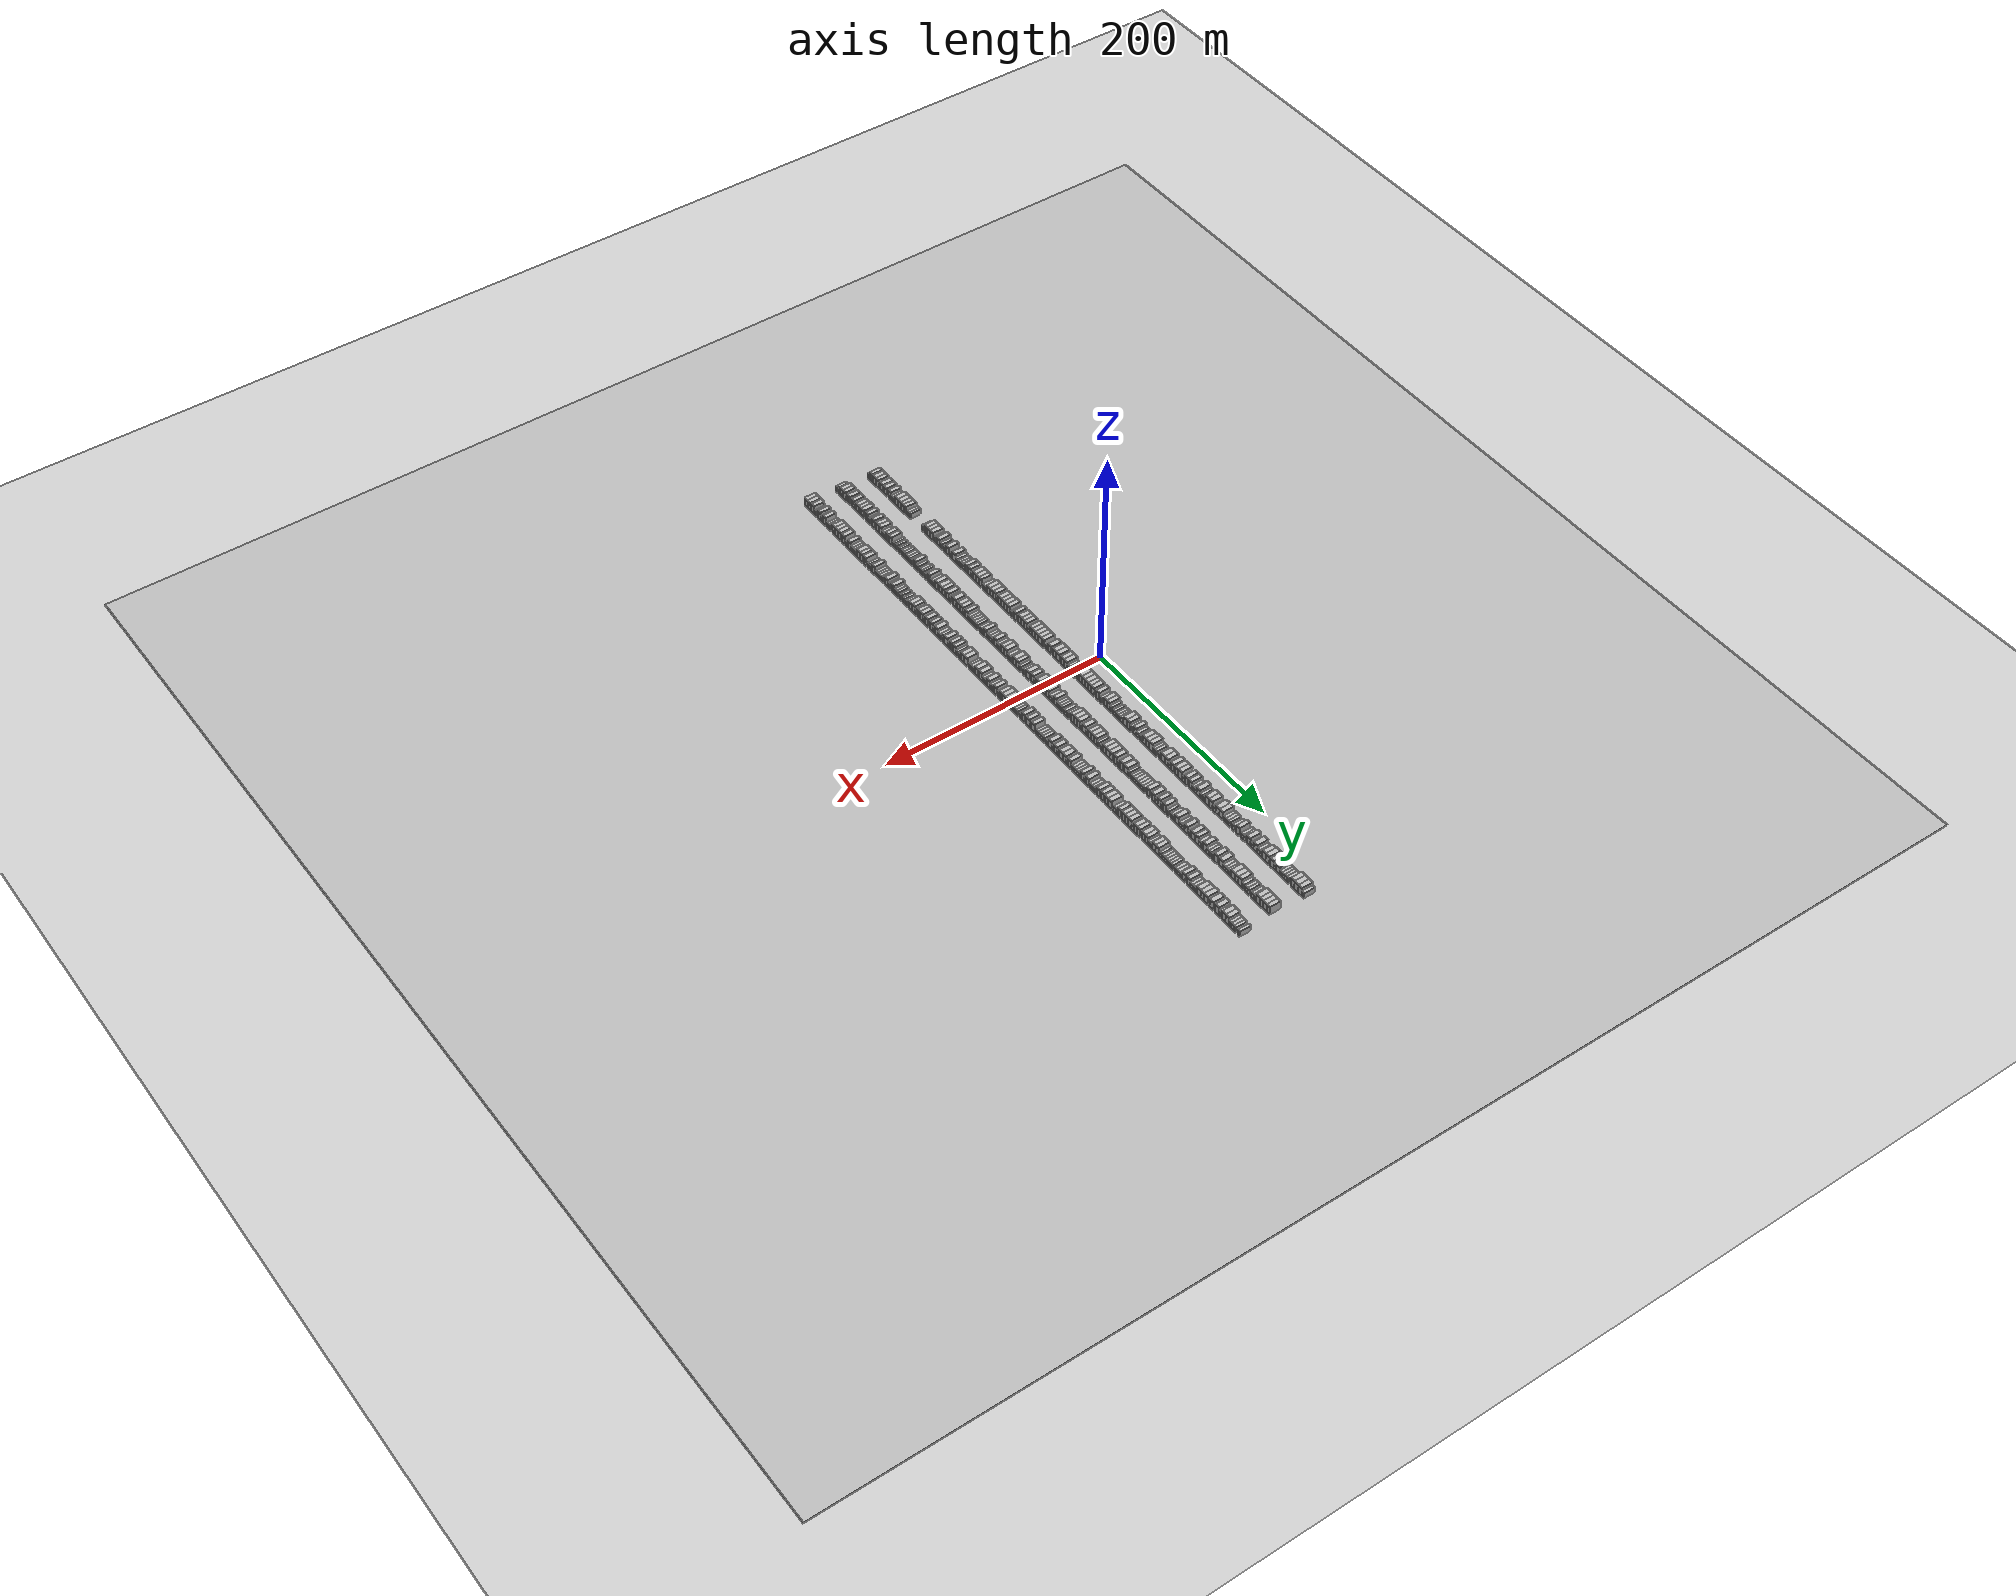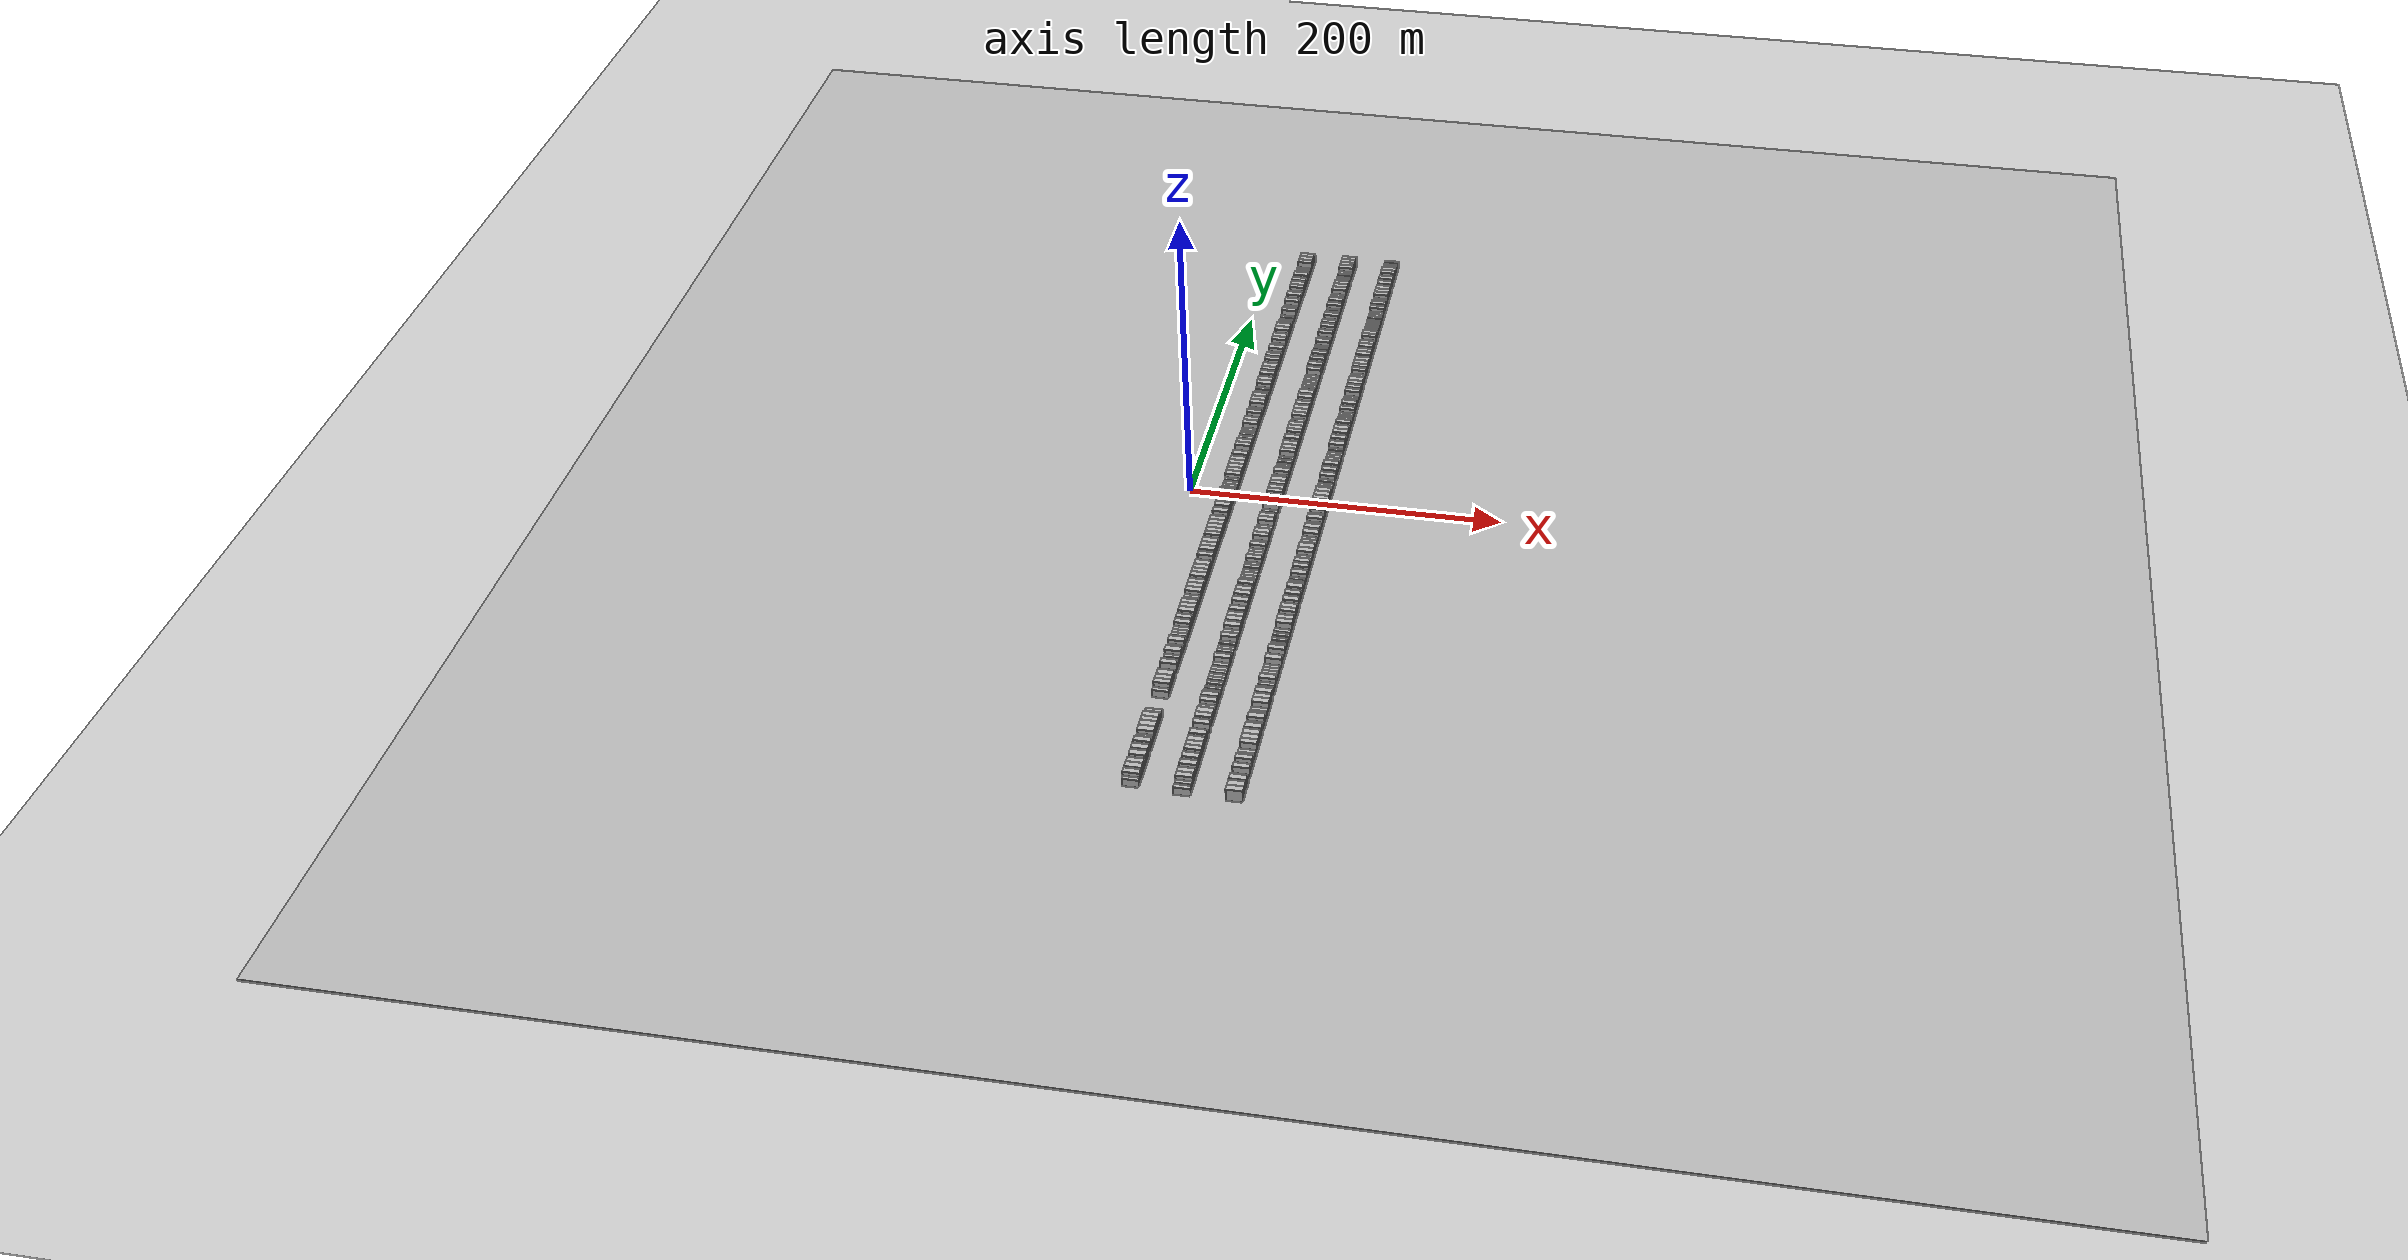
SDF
<?xml version="1.0" encoding="utf-8"?>

<sdf version="1.6">

   <world name="default">

      <gui fullscreen="0">

         <camera name="user_camera">

            <pose>-15 0 4.57585 0 0 0</pose>

            <view_controller>orbit</view_controller>

         </camera>

      </gui>

      <scene>

         <sky>

           <clouds>

             <speed>12</speed>

           </clouds>

         </sky>

         <ambient>0.4 0.4 0.4 1</ambient>

         <background>0.7 0.7 0.7 1</background>

         <shadows>1</shadows>

      </scene>

      <gravity>0 0 -9.8066</gravity>

      <magnetic_field>6e-06 2.3e-05 -4.2e-05</magnetic_field>

      <physics default="0" name="default_physics" type="ode">

         <ode>

            <solver>

               <type>quick</type>

               <iters>10</iters>

               <sor>1.0</sor>

               <use_dynamic_moi_rescaling>0</use_dynamic_moi_rescaling>

            </solver>

            <constraints>

               <cfm>0</cfm>

               <erp>0.2</erp>

               <contact_max_correcting_vel>100</contact_max_correcting_vel>

               <contact_surface_layer>0.001</contact_surface_layer>

            </constraints>

         </ode>

         <max_step_size>0.004</max_step_size>

         <real_time_factor>1</real_time_factor>

         <real_time_update_rate>250</real_time_update_rate>

      </physics>

      <light name="sun" type="directional">

         <cast_shadows>1</cast_shadows>

         <pose>0 0 10 0 0 0</pose>

         <diffuse>0.8 0.8 0.8 1</diffuse>

         <specular>0.2 0.2 0.2 1</specular>

         <attenuation>

            <range>1000</range>

            <constant>0.9</constant>

            <linear>0.01</linear>

            <quadratic>0.001</quadratic>

         </attenuation>

         <direction>-0.5 0.1 -0.9</direction>

      </light>

      <include>

         <name>ground_plane_1</name>

         <uri>model://HANNAS_ground_plane</uri>

         <pose>0 0 0  0 0 0</pose>

      </include>

      <include>

         <name>ground_plane_2</name>

         <uri>model://HANNAS_ground_plane</uri>

         <pose>100 0 0  0 0 0</pose>

      </include>

      <model name="building_1">

         <static>1</static>

         <pose frame="">25.0000 -276.7250 0 0.000000 0.000000 0.000000</pose>

         <link name="link">

            <pose frame="">0 0 3.00 0 0 0</pose>

            <collision name="collision">

               <geometry>

                  <box>

                     <size>10.0000 2.5499 6.0000</size>

                  </box>

               </geometry>

               <max_contacts>10</max_contacts>

               <surface>

                  <contact>

                     <ode/>

                  </contact>

                  <bounce/>

                  <friction>

                     <torsional>

                        <ode/>

                     </torsional>

                     <ode/>

                  </friction>

               </surface>

            </collision>

            <visual name="visual">

               <cast_shadows>0</cast_shadows>

               <geometry>

                  <box>

                     <size>10.0000 2.5499 6.0000</size>

                  </box>

               </geometry>

               <material>

                  <script>

                     <uri>model://HANNAS_wall/materials/scripts</uri>

                     <uri>model://HANNAS_wall/materials/textures</uri>

                     <name>vrc/HANNAS_wall</name>

                  </script>

               </material>

            </visual>

            <self_collide>0</self_collide>

            <enable_wind>0</enable_wind>

            <kinematic>0</kinematic>

         </link>

      </model>

      <model name="building_2">

         <static>1</static>

         <pose frame="">25.0000 -273.5485 0 0.000000 0.000000 0.000000</pose>

         <link name="link">

            <pose frame="">0 0 4.50 0 0 0</pose>

            <collision name="collision">

               <geometry>

                  <box>

                     <size>10.0000 3.8032 9.0000</size>

                  </box>

               </geometry>

               <max_contacts>10</max_contacts>

               <surface>

                  <contact>

                     <ode/>

                  </contact>

                  <bounce/>

                  <friction>

                     <torsional>

                        <ode/>

                     </torsional>

                     <ode/>

                  </friction>

               </surface>

            </collision>

            <visual name="visual">

               <cast_shadows>0</cast_shadows>

               <geometry>

                  <box>

                     <size>10.0000 3.8032 9.0000</size>

                  </box>

               </geometry>

               <material>

                  <script>

                     <uri>model://HANNAS_wall/materials/scripts</uri>

                     <uri>model://HANNAS_wall/materials/textures</uri>

                     <name>vrc/HANNAS_wall</name>

                  </script>

               </material>

            </visual>

            <self_collide>0</self_collide>

            <enable_wind>0</enable_wind>

            <kinematic>0</kinematic>

         </link>

      </model>

      <model name="building_3">

         <static>1</static>

         <pose frame="">25.0000 -268.5318 0 0.000000 0.000000 0.000000</pose>

         <link name="link">

            <pose frame="">0 0 4.50 0 0 0</pose>

            <collision name="collision">

               <geometry>

                  <box>

                     <size>10.0000 4.2303 9.0000</size>

                  </box>

               </geometry>

               <max_contacts>10</max_contacts>

               <surface>

                  <contact>

                     <ode/>

                  </contact>

                  <bounce/>

                  <friction>

                     <torsional>

                        <ode/>

                     </torsional>

                     <ode/>

                  </friction>

               </surface>

            </collision>

            <visual name="visual">

               <cast_shadows>0</cast_shadows>

               <geometry>

                  <box>

                     <size>10.0000 4.2303 9.0000</size>

                  </box>

               </geometry>

               <material>

                  <script>

                     <uri>model://HANNAS_wall/materials/scripts</uri>

                     <uri>model://HANNAS_wall/materials/textures</uri>

                     <name>vrc/HANNAS_wall</name>

                  </script>

               </material>

            </visual>

            <self_collide>0</self_collide>

            <enable_wind>0</enable_wind>

            <kinematic>0</kinematic>

         </link>

      </model>

      <model name="building_4">

         <static>1</static>

         <pose frame="">25.0000 -264.5383 0 0.000000 0.000000 0.000000</pose>

         <link name="link">

            <pose frame="">0 0 4.50 0 0 0</pose>

            <collision name="collision">

               <geometry>

                  <box>

                     <size>10.0000 3.7567 9.0000</size>

                  </box>

               </geometry>

               <max_contacts>10</max_contacts>

               <surface>

                  <contact>

                     <ode/>

                  </contact>

                  <bounce/>

                  <friction>

                     <torsional>

                        <ode/>

                     </torsional>

                     <ode/>

                  </friction>

               </surface>

            </collision>

            <visual name="visual">

               <cast_shadows>0</cast_shadows>

               <geometry>

                  <box>

                     <size>10.0000 3.7567 9.0000</size>

                  </box>

               </geometry>

               <material>

                  <script>

                     <uri>model://HANNAS_wall/materials/scripts</uri>

                     <uri>model://HANNAS_wall/materials/textures</uri>

                     <name>vrc/HANNAS_wall</name>

                  </script>

               </material>

            </visual>

            <self_collide>0</self_collide>

            <enable_wind>0</enable_wind>

            <kinematic>0</kinematic>

         </link>

      </model>

      <model name="building_5">

         <static>1</static>

         <pose frame="">25.0000 -261.4245 0 0.000000 0.000000 0.000000</pose>

         <link name="link">

            <pose frame="">0 0 3.00 0 0 0</pose>

            <collision name="collision">

               <geometry>

                  <box>

                     <size>10.0000 2.4708 6.0000</size>

                  </box>

               </geometry>

               <max_contacts>10</max_contacts>

               <surface>

                  <contact>

                     <ode/>

                  </contact>

                  <bounce/>

                  <friction>

                     <torsional>

                        <ode/>

                     </torsional>

                     <ode/>

                  </friction>

               </surface>

            </collision>

            <visual name="visual">

               <cast_shadows>0</cast_shadows>

               <geometry>

                  <box>

                     <size>10.0000 2.4708 6.0000</size>

                  </box>

               </geometry>

               <material>

                  <script>

                     <uri>model://HANNAS_wall/materials/scripts</uri>

                     <uri>model://HANNAS_wall/materials/textures</uri>

                     <name>vrc/HANNAS_wall</name>

                  </script>

               </material>

            </visual>

            <self_collide>0</self_collide>

            <enable_wind>0</enable_wind>

            <kinematic>0</kinematic>

         </link>

      </model>

      <model name="building_6">

         <static>1</static>

         <pose frame="">25.0000 -257.9877 0 0.000000 0.000000 0.000000</pose>

         <link name="link">

            <pose frame="">0 0 4.50 0 0 0</pose>

            <collision name="collision">

               <geometry>

                  <box>

                     <size>10.0000 4.4028 9.0000</size>

                  </box>

               </geometry>

               <max_contacts>10</max_contacts>

               <surface>

                  <contact>

                     <ode/>

                  </contact>

                  <bounce/>

                  <friction>

                     <torsional>

                        <ode/>

                     </torsional>

                     <ode/>

                  </friction>

               </surface>

            </collision>

            <visual name="visual">

               <cast_shadows>0</cast_shadows>

               <geometry>

                  <box>

                     <size>10.0000 4.4028 9.0000</size>

                  </box>

               </geometry>

               <material>

                  <script>

                     <uri>model://HANNAS_wall/materials/scripts</uri>

                     <uri>model://HANNAS_wall/materials/textures</uri>

                     <name>vrc/HANNAS_wall</name>

                  </script>

               </material>

            </visual>

            <self_collide>0</self_collide>

            <enable_wind>0</enable_wind>

            <kinematic>0</kinematic>

         </link>

      </model>

      <model name="building_7">

         <static>1</static>

         <pose frame="">25.0000 -252.6310 0 0.000000 0.000000 0.000000</pose>

         <link name="link">

            <pose frame="">0 0 4.50 0 0 0</pose>

            <collision name="collision">

               <geometry>

                  <box>

                     <size>10.0000 4.3106 9.0000</size>

                  </box>

               </geometry>

               <max_contacts>10</max_contacts>

               <surface>

                  <contact>

                     <ode/>

                  </contact>

                  <bounce/>

                  <friction>

                     <torsional>

                        <ode/>

                     </torsional>

                     <ode/>

                  </friction>

               </surface>

            </collision>

            <visual name="visual">

               <cast_shadows>0</cast_shadows>

               <geometry>

                  <box>

                     <size>10.0000 4.3106 9.0000</size>

                  </box>

               </geometry>

               <material>

                  <script>

                     <uri>model://HANNAS_wall/materials/scripts</uri>

                     <uri>model://HANNAS_wall/materials/textures</uri>

                     <name>vrc/HANNAS_wall</name>

                  </script>

               </material>

            </visual>

            <self_collide>0</self_collide>

            <enable_wind>0</enable_wind>

            <kinematic>0</kinematic>

         </link>

      </model>

      <model name="building_8">

         <static>1</static>

         <pose frame="">25.0000 -246.4828 0 0.000000 0.000000 0.000000</pose>

         <link name="link">

            <pose frame="">0 0 4.50 0 0 0</pose>

            <collision name="collision">

               <geometry>

                  <box>

                     <size>10.0000 3.9860 9.0000</size>

                  </box>

               </geometry>

               <max_contacts>10</max_contacts>

               <surface>

                  <contact>

                     <ode/>

                  </contact>

                  <bounce/>

                  <friction>

                     <torsional>

                        <ode/>

                     </torsional>

                     <ode/>

                  </friction>

               </surface>

            </collision>

            <visual name="visual">

               <cast_shadows>0</cast_shadows>

               <geometry>

                  <box>

                     <size>10.0000 3.9860 9.0000</size>

                  </box>

               </geometry>

               <material>

                  <script>

                     <uri>model://HANNAS_wall/materials/scripts</uri>

                     <uri>model://HANNAS_wall/materials/textures</uri>

                     <name>vrc/HANNAS_wall</name>

                  </script>

               </material>

            </visual>

            <self_collide>0</self_collide>

            <enable_wind>0</enable_wind>

            <kinematic>0</kinematic>

         </link>

      </model>

      <model name="building_9">

         <static>1</static>

         <pose frame="">25.0000 -243.1892 0 0.000000 0.000000 0.000000</pose>

         <link name="link">

            <pose frame="">0 0 3.00 0 0 0</pose>

            <collision name="collision">

               <geometry>

                  <box>

                     <size>10.0000 2.6011 6.0000</size>

                  </box>

               </geometry>

               <max_contacts>10</max_contacts>

               <surface>

                  <contact>

                     <ode/>

                  </contact>

                  <bounce/>

                  <friction>

                     <torsional>

                        <ode/>

                     </torsional>

                     <ode/>

                  </friction>

               </surface>

            </collision>

            <visual name="visual">

               <cast_shadows>0</cast_shadows>

               <geometry>

                  <box>

                     <size>10.0000 2.6011 6.0000</size>

                  </box>

               </geometry>

               <material>

                  <script>

                     <uri>model://HANNAS_wall/materials/scripts</uri>

                     <uri>model://HANNAS_wall/materials/textures</uri>

                     <name>vrc/HANNAS_wall</name>

                  </script>

               </material>

            </visual>

            <self_collide>0</self_collide>

            <enable_wind>0</enable_wind>

            <kinematic>0</kinematic>

         </link>

      </model>

      <model name="building_10">

         <static>1</static>

         <pose frame="">25.0000 -240.5972 0 0.000000 0.000000 0.000000</pose>

         <link name="link">

            <pose frame="">0 0 3.00 0 0 0</pose>

            <collision name="collision">

               <geometry>

                  <box>

                     <size>10.0000 2.5830 6.0000</size>

                  </box>

               </geometry>

               <max_contacts>10</max_contacts>

               <surface>

                  <contact>

                     <ode/>

                  </contact>

                  <bounce/>

                  <friction>

                     <torsional>

                        <ode/>

                     </torsional>

                     <ode/>

                  </friction>

               </surface>

            </collision>

            <visual name="visual">

               <cast_shadows>0</cast_shadows>

               <geometry>

                  <box>

                     <size>10.0000 2.5830 6.0000</size>

                  </box>

               </geometry>

               <material>

                  <script>

                     <uri>model://HANNAS_wall/materials/scripts</uri>

                     <uri>model://HANNAS_wall/materials/textures</uri>

                     <name>vrc/HANNAS_wall</name>

                  </script>

               </material>

            </visual>

            <self_collide>0</self_collide>

            <enable_wind>0</enable_wind>

            <kinematic>0</kinematic>

         </link>

      </model>

      <model name="building_11">

         <static>1</static>

         <pose frame="">25.0000 -237.0894 0 0.000000 0.000000 0.000000</pose>

         <link name="link">

            <pose frame="">0 0 4.50 0 0 0</pose>

            <collision name="collision">

               <geometry>

                  <box>

                     <size>10.0000 4.4326 9.0000</size>

                  </box>

               </geometry>

               <max_contacts>10</max_contacts>

               <surface>

                  <contact>

                     <ode/>

                  </contact>

                  <bounce/>

                  <friction>

                     <torsional>

                        <ode/>

                     </torsional>

                     <ode/>

                  </friction>

               </surface>

            </collision>

            <visual name="visual">

               <cast_shadows>0</cast_shadows>

               <geometry>

                  <box>

                     <size>10.0000 4.4326 9.0000</size>

                  </box>

               </geometry>

               <material>

                  <script>

                     <uri>model://HANNAS_wall/materials/scripts</uri>

                     <uri>model://HANNAS_wall/materials/textures</uri>

                     <name>vrc/HANNAS_wall</name>

                  </script>

               </material>

            </visual>

            <self_collide>0</self_collide>

            <enable_wind>0</enable_wind>

            <kinematic>0</kinematic>

         </link>

      </model>

      <model name="building_12">

         <static>1</static>

         <pose frame="">25.0000 -232.6515 0 0.000000 0.000000 0.000000</pose>

         <link name="link">

            <pose frame="">0 0 4.50 0 0 0</pose>

            <collision name="collision">

               <geometry>

                  <box>

                     <size>10.0000 4.4432 9.0000</size>

                  </box>

               </geometry>

               <max_contacts>10</max_contacts>

               <surface>

                  <contact>

                     <ode/>

                  </contact>

                  <bounce/>

                  <friction>

                     <torsional>

                        <ode/>

                     </torsional>

                     <ode/>

                  </friction>

               </surface>

            </collision>

            <visual name="visual">

               <cast_shadows>0</cast_shadows>

               <geometry>

                  <box>

                     <size>10.0000 4.4432 9.0000</size>

                  </box>

               </geometry>

               <material>

                  <script>

                     <uri>model://HANNAS_wall/materials/scripts</uri>

                     <uri>model://HANNAS_wall/materials/textures</uri>

                     <name>vrc/HANNAS_wall</name>

                  </script>

               </material>

            </visual>

            <self_collide>0</self_collide>

            <enable_wind>0</enable_wind>

            <kinematic>0</kinematic>

         </link>

      </model>

      <model name="building_13">

         <static>1</static>

         <pose frame="">25.0000 -228.6149 0 0.000000 0.000000 0.000000</pose>

         <link name="link">

            <pose frame="">0 0 4.50 0 0 0</pose>

            <collision name="collision">

               <geometry>

                  <box>

                     <size>10.0000 3.6301 9.0000</size>

                  </box>

               </geometry>

               <max_contacts>10</max_contacts>

               <surface>

                  <contact>

                     <ode/>

                  </contact>

                  <bounce/>

                  <friction>

                     <torsional>

                        <ode/>

                     </torsional>

                     <ode/>

                  </friction>

               </surface>

            </collision>

            <visual name="visual">

               <cast_shadows>0</cast_shadows>

               <geometry>

                  <box>

                     <size>10.0000 3.6301 9.0000</size>

                  </box>

               </geometry>

               <material>

                  <script>

                     <uri>model://HANNAS_wall/materials/scripts</uri>

                     <uri>model://HANNAS_wall/materials/textures</uri>

                     <name>vrc/HANNAS_wall</name>

                  </script>

               </material>

            </visual>

            <self_collide>0</self_collide>

            <enable_wind>0</enable_wind>

            <kinematic>0</kinematic>

         </link>

      </model>

      <model name="building_14">

         <static>1</static>

         <pose frame="">25.0000 -224.8320 0 0.000000 0.000000 0.000000</pose>

         <link name="link">

            <pose frame="">0 0 4.50 0 0 0</pose>

            <collision name="collision">

               <geometry>

                  <box>

                     <size>10.0000 3.9356 9.0000</size>

                  </box>

               </geometry>

               <max_contacts>10</max_contacts>

               <surface>

                  <contact>

                     <ode/>

                  </contact>

                  <bounce/>

                  <friction>

                     <torsional>

                        <ode/>

                     </torsional>

                     <ode/>

                  </friction>

               </surface>

            </collision>

            <visual name="visual">

               <cast_shadows>0</cast_shadows>

               <geometry>

                  <box>

                     <size>10.0000 3.9356 9.0000</size>

                  </box>

               </geometry>

               <material>

                  <script>

                     <uri>model://HANNAS_wall/materials/scripts</uri>

                     <uri>model://HANNAS_wall/materials/textures</uri>

                     <name>vrc/HANNAS_wall</name>

                  </script>

               </material>

            </visual>

            <self_collide>0</self_collide>

            <enable_wind>0</enable_wind>

            <kinematic>0</kinematic>

         </link>

      </model>

      <model name="building_15">

         <static>1</static>

         <pose frame="">25.0000 -220.4967 0 0.000000 0.000000 0.000000</pose>

         <link name="link">

            <pose frame="">0 0 3.00 0 0 0</pose>

            <collision name="collision">

               <geometry>

                  <box>

                     <size>10.0000 2.7349 6.0000</size>

                  </box>

               </geometry>

               <max_contacts>10</max_contacts>

               <surface>

                  <contact>

                     <ode/>

                  </contact>

                  <bounce/>

                  <friction>

                     <torsional>

                        <ode/>

                     </torsional>

                     <ode/>

                  </friction>

               </surface>

            </collision>

            <visual name="visual">

               <cast_shadows>0</cast_shadows>

               <geometry>

                  <box>

                     <size>10.0000 2.7349 6.0000</size>

                  </box>

               </geometry>

               <material>

                  <script>

                     <uri>model://HANNAS_wall/materials/scripts</uri>

                     <uri>model://HANNAS_wall/materials/textures</uri>

                     <name>vrc/HANNAS_wall</name>

                  </script>

               </material>

            </visual>

            <self_collide>0</self_collide>

            <enable_wind>0</enable_wind>

            <kinematic>0</kinematic>

         </link>

      </model>

      <model name="building_16">

         <static>1</static>

         <pose frame="">25.0000 -217.9195 0 0.000000 0.000000 0.000000</pose>

         <link name="link">

            <pose frame="">0 0 3.00 0 0 0</pose>

            <collision name="collision">

               <geometry>

                  <box>

                     <size>10.0000 2.4194 6.0000</size>

                  </box>

               </geometry>

               <max_contacts>10</max_contacts>

               <surface>

                  <contact>

                     <ode/>

                  </contact>

                  <bounce/>

                  <friction>

                     <torsional>

                        <ode/>

                     </torsional>

                     <ode/>

                  </friction>

               </surface>

            </collision>

            <visual name="visual">

               <cast_shadows>0</cast_shadows>

               <geometry>

                  <box>

                     <size>10.0000 2.4194 6.0000</size>

                  </box>

               </geometry>

               <material>

                  <script>

                     <uri>model://HANNAS_wall/materials/scripts</uri>

                     <uri>model://HANNAS_wall/materials/textures</uri>

                     <name>vrc/HANNAS_wall</name>

                  </script>

               </material>

            </visual>

            <self_collide>0</self_collide>

            <enable_wind>0</enable_wind>

            <kinematic>0</kinematic>

         </link>

      </model>

      <model name="building_17">

         <static>1</static>

         <pose frame="">25.0000 -199.4089 0 0.000000 0.000000 0.000000</pose>

         <link name="link">

            <pose frame="">0 0 3.00 0 0 0</pose>

            <collision name="collision">

               <geometry>

                  <box>

                     <size>10.0000 2.8673 6.0000</size>

                  </box>

               </geometry>

               <max_contacts>10</max_contacts>

               <surface>

                  <contact>

                     <ode/>

                  </contact>

                  <bounce/>

                  <friction>

                     <torsional>

                        <ode/>

                     </torsional>

                     <ode/>

                  </friction>

               </surface>

            </collision>

            <visual name="visual">

               <cast_shadows>0</cast_shadows>

               <geometry>

                  <box>

                     <size>10.0000 2.8673 6.0000</size>

                  </box>

               </geometry>

               <material>

                  <script>

                     <uri>model://HANNAS_wall/materials/scripts</uri>

                     <uri>model://HANNAS_wall/materials/textures</uri>

                     <name>vrc/HANNAS_wall</name>

                  </script>

               </material>

            </visual>

            <self_collide>0</self_collide>

            <enable_wind>0</enable_wind>

            <kinematic>0</kinematic>

         </link>

      </model>

      <model name="building_18">

         <static>1</static>

         <pose frame="">25.0000 -195.0465 0 0.000000 0.000000 0.000000</pose>

         <link name="link">

            <pose frame="">0 0 4.50 0 0 0</pose>

            <collision name="collision">

               <geometry>

                  <box>

                     <size>10.0000 3.8573 9.0000</size>

                  </box>

               </geometry>

               <max_contacts>10</max_contacts>

               <surface>

                  <contact>

                     <ode/>

                  </contact>

                  <bounce/>

                  <friction>

                     <torsional>

                        <ode/>

                     </torsional>

                     <ode/>

                  </friction>

               </surface>

            </collision>

            <visual name="visual">

               <cast_shadows>0</cast_shadows>

               <geometry>

                  <box>

                     <size>10.0000 3.8573 9.0000</size>

                  </box>

               </geometry>

               <material>

                  <script>

                     <uri>model://HANNAS_wall/materials/scripts</uri>

                     <uri>model://HANNAS_wall/materials/textures</uri>

                     <name>vrc/HANNAS_wall</name>

                  </script>

               </material>

            </visual>

            <self_collide>0</self_collide>

            <enable_wind>0</enable_wind>

            <kinematic>0</kinematic>

         </link>

      </model>

      <model name="building_19">

         <static>1</static>

         <pose frame="">25.0000 -191.1698 0 0.000000 0.000000 0.000000</pose>

         <link name="link">

            <pose frame="">0 0 4.50 0 0 0</pose>

            <collision name="collision">

               <geometry>

                  <box>

                     <size>10.0000 3.8960 9.0000</size>

                  </box>

               </geometry>

               <max_contacts>10</max_contacts>

               <surface>

                  <contact>

                     <ode/>

                  </contact>

                  <bounce/>

                  <friction>

                     <torsional>

                        <ode/>

                     </torsional>

                     <ode/>

                  </friction>

               </surface>

            </collision>

            <visual name="visual">

               <cast_shadows>0</cast_shadows>

               <geometry>

                  <box>

                     <size>10.0000 3.8960 9.0000</size>

                  </box>

               </geometry>

               <material>

                  <script>

                     <uri>model://HANNAS_wall/materials/scripts</uri>

                     <uri>model://HANNAS_wall/materials/textures</uri>

                     <name>vrc/HANNAS_wall</name>

                  </script>

               </material>

            </visual>

            <self_collide>0</self_collide>

            <enable_wind>0</enable_wind>

            <kinematic>0</kinematic>

         </link>

      </model>

      <model name="building_20">

         <static>1</static>

         <pose frame="">25.0000 -186.9760 0 0.000000 0.000000 0.000000</pose>

         <link name="link">

            <pose frame="">0 0 4.50 0 0 0</pose>

            <collision name="collision">

               <geometry>

                  <box>

                     <size>10.0000 4.4915 9.0000</size>

                  </box>

               </geometry>

               <max_contacts>10</max_contacts>

               <surface>

                  <contact>

                     <ode/>

                  </contact>

                  <bounce/>

                  <friction>

                     <torsional>

                        <ode/>

                     </torsional>

                     <ode/>

                  </friction>

               </surface>

            </collision>

            <visual name="visual">

               <cast_shadows>0</cast_shadows>

               <geometry>

                  <box>

                     <size>10.0000 4.4915 9.0000</size>

                  </box>

               </geometry>

               <material>

                  <script>

                     <uri>model://HANNAS_wall/materials/scripts</uri>

                     <uri>model://HANNAS_wall/materials/textures</uri>

                     <name>vrc/HANNAS_wall</name>

                  </script>

               </material>

            </visual>

            <self_collide>0</self_collide>

            <enable_wind>0</enable_wind>

            <kinematic>0</kinematic>

         </link>

      </model>

      <model name="building_21">

         <static>1</static>

         <pose frame="">25.0000 -182.4449 0 0.000000 0.000000 0.000000</pose>

         <link name="link">

            <pose frame="">0 0 3.00 0 0 0</pose>

            <collision name="collision">

               <geometry>

                  <box>

                     <size>10.0000 2.5707 6.0000</size>

                  </box>

               </geometry>

               <max_contacts>10</max_contacts>

               <surface>

                  <contact>

                     <ode/>

                  </contact>

                  <bounce/>

                  <friction>

                     <torsional>

                        <ode/>

                     </torsional>

                     <ode/>

                  </friction>

               </surface>

            </collision>

            <visual name="visual">

               <cast_shadows>0</cast_shadows>

               <geometry>

                  <box>

                     <size>10.0000 2.5707 6.0000</size>

                  </box>

               </geometry>

               <material>

                  <script>

                     <uri>model://HANNAS_wall/materials/scripts</uri>

                     <uri>model://HANNAS_wall/materials/textures</uri>

                     <name>vrc/HANNAS_wall</name>

                  </script>

               </material>

            </visual>

            <self_collide>0</self_collide>

            <enable_wind>0</enable_wind>

            <kinematic>0</kinematic>

         </link>

      </model>

      <model name="building_22">

         <static>1</static>

         <pose frame="">25.0000 -177.0999 0 0.000000 0.000000 0.000000</pose>

         <link name="link">

            <pose frame="">0 0 4.50 0 0 0</pose>

            <collision name="collision">

               <geometry>

                  <box>

                     <size>10.0000 4.1193 9.0000</size>

                  </box>

               </geometry>

               <max_contacts>10</max_contacts>

               <surface>

                  <contact>

                     <ode/>

                  </contact>

                  <bounce/>

                  <friction>

                     <torsional>

                        <ode/>

                     </torsional>

                     <ode/>

                  </friction>

               </surface>

            </collision>

            <visual name="visual">

               <cast_shadows>0</cast_shadows>

               <geometry>

                  <box>

                     <size>10.0000 4.1193 9.0000</size>

                  </box>

               </geometry>

               <material>

                  <script>

                     <uri>model://HANNAS_wall/materials/scripts</uri>

                     <uri>model://HANNAS_wall/materials/textures</uri>

                     <name>vrc/HANNAS_wall</name>

                  </script>

               </material>

            </visual>

            <self_collide>0</self_collide>

            <enable_wind>0</enable_wind>

            <kinematic>0</kinematic>

         </link>

      </model>

      <model name="building_23">

         <static>1</static>

         <pose frame="">25.0000 -173.5735 0 0.000000 0.000000 0.000000</pose>

         <link name="link">

            <pose frame="">0 0 3.00 0 0 0</pose>

            <collision name="collision">

               <geometry>

                  <box>

                     <size>10.0000 2.9335 6.0000</size>

                  </box>

               </geometry>

               <max_contacts>10</max_contacts>

               <surface>

                  <contact>

                     <ode/>

                  </contact>

                  <bounce/>

                  <friction>

                     <torsional>

                        <ode/>

                     </torsional>

                     <ode/>

                  </friction>

               </surface>

            </collision>

            <visual name="visual">

               <cast_shadows>0</cast_shadows>

               <geometry>

                  <box>

                     <size>10.0000 2.9335 6.0000</size>

                  </box>

               </geometry>

               <material>

                  <script>

                     <uri>model://HANNAS_wall/materials/scripts</uri>

                     <uri>model://HANNAS_wall/materials/textures</uri>

                     <name>vrc/HANNAS_wall</name>

                  </script>

               </material>

            </visual>

            <self_collide>0</self_collide>

            <enable_wind>0</enable_wind>

            <kinematic>0</kinematic>

         </link>

      </model>

      <model name="building_24">

         <static>1</static>

         <pose frame="">25.0000 -168.7866 0 0.000000 0.000000 0.000000</pose>

         <link name="link">

            <pose frame="">0 0 3.00 0 0 0</pose>

            <collision name="collision">

               <geometry>

                  <box>

                     <size>10.0000 2.6401 6.0000</size>

                  </box>

               </geometry>

               <max_contacts>10</max_contacts>

               <surface>

                  <contact>

                     <ode/>

                  </contact>

                  <bounce/>

                  <friction>

                     <torsional>

                        <ode/>

                     </torsional>

                     <ode/>

                  </friction>

               </surface>

            </collision>

            <visual name="visual">

               <cast_shadows>0</cast_shadows>

               <geometry>

                  <box>

                     <size>10.0000 2.6401 6.0000</size>

                  </box>

               </geometry>

               <material>

                  <script>

                     <uri>model://HANNAS_wall/materials/scripts</uri>

                     <uri>model://HANNAS_wall/materials/textures</uri>

                     <name>vrc/HANNAS_wall</name>

                  </script>

               </material>

            </visual>

            <self_collide>0</self_collide>

            <enable_wind>0</enable_wind>

            <kinematic>0</kinematic>

         </link>

      </model>

      <model name="building_25">

         <static>1</static>

         <pose frame="">25.0000 -165.2260 0 0.000000 0.000000 0.000000</pose>

         <link name="link">

            <pose frame="">0 0 4.50 0 0 0</pose>

            <collision name="collision">

               <geometry>

                  <box>

                     <size>10.0000 4.4811 9.0000</size>

                  </box>

               </geometry>

               <max_contacts>10</max_contacts>

               <surface>

                  <contact>

                     <ode/>

                  </contact>

                  <bounce/>

                  <friction>

                     <torsional>

                        <ode/>

                     </torsional>

                     <ode/>

                  </friction>

               </surface>

            </collision>

            <visual name="visual">

               <cast_shadows>0</cast_shadows>

               <geometry>

                  <box>

                     <size>10.0000 4.4811 9.0000</size>

                  </box>

               </geometry>

               <material>

                  <script>

                     <uri>model://HANNAS_wall/materials/scripts</uri>

                     <uri>model://HANNAS_wall/materials/textures</uri>

                     <name>vrc/HANNAS_wall</name>

                  </script>

               </material>

            </visual>

            <self_collide>0</self_collide>

            <enable_wind>0</enable_wind>

            <kinematic>0</kinematic>

         </link>

      </model>

      <model name="building_26">

         <static>1</static>

         <pose frame="">25.0000 -159.5359 0 0.000000 0.000000 0.000000</pose>

         <link name="link">

            <pose frame="">0 0 3.00 0 0 0</pose>

            <collision name="collision">

               <geometry>

                  <box>

                     <size>10.0000 2.8993 6.0000</size>

                  </box>

               </geometry>

               <max_contacts>10</max_contacts>

               <surface>

                  <contact>

                     <ode/>

                  </contact>

                  <bounce/>

                  <friction>

                     <torsional>

                        <ode/>

                     </torsional>

                     <ode/>

                  </friction>

               </surface>

            </collision>

            <visual name="visual">

               <cast_shadows>0</cast_shadows>

               <geometry>

                  <box>

                     <size>10.0000 2.8993 6.0000</size>

                  </box>

               </geometry>

               <material>

                  <script>

                     <uri>model://HANNAS_wall/materials/scripts</uri>

                     <uri>model://HANNAS_wall/materials/textures</uri>

                     <name>vrc/HANNAS_wall</name>

                  </script>

               </material>

            </visual>

            <self_collide>0</self_collide>

            <enable_wind>0</enable_wind>

            <kinematic>0</kinematic>

         </link>

      </model>

      <model name="building_27">

         <static>1</static>

         <pose frame="">25.0000 -155.9383 0 0.000000 0.000000 0.000000</pose>

         <link name="link">

            <pose frame="">0 0 4.50 0 0 0</pose>

            <collision name="collision">

               <geometry>

                  <box>

                     <size>10.0000 4.2959 9.0000</size>

                  </box>

               </geometry>

               <max_contacts>10</max_contacts>

               <surface>

                  <contact>

                     <ode/>

                  </contact>

                  <bounce/>

                  <friction>

                     <torsional>

                        <ode/>

                     </torsional>

                     <ode/>

                  </friction>

               </surface>

            </collision>

            <visual name="visual">

               <cast_shadows>0</cast_shadows>

               <geometry>

                  <box>

                     <size>10.0000 4.2959 9.0000</size>

                  </box>

               </geometry>

               <material>

                  <script>

                     <uri>model://HANNAS_wall/materials/scripts</uri>

                     <uri>model://HANNAS_wall/materials/textures</uri>

                     <name>vrc/HANNAS_wall</name>

                  </script>

               </material>

            </visual>

            <self_collide>0</self_collide>

            <enable_wind>0</enable_wind>

            <kinematic>0</kinematic>

         </link>

      </model>

      <model name="building_28">

         <static>1</static>

         <pose frame="">25.0000 -152.2957 0 0.000000 0.000000 0.000000</pose>

         <link name="link">

            <pose frame="">0 0 3.00 0 0 0</pose>

            <collision name="collision">

               <geometry>

                  <box>

                     <size>10.0000 2.9892 6.0000</size>

                  </box>

               </geometry>

               <max_contacts>10</max_contacts>

               <surface>

                  <contact>

                     <ode/>

                  </contact>

                  <bounce/>

                  <friction>

                     <torsional>

                        <ode/>

                     </torsional>

                     <ode/>

                  </friction>

               </surface>

            </collision>

            <visual name="visual">

               <cast_shadows>0</cast_shadows>

               <geometry>

                  <box>

                     <size>10.0000 2.9892 6.0000</size>

                  </box>

               </geometry>

               <material>

                  <script>

                     <uri>model://HANNAS_wall/materials/scripts</uri>

                     <uri>model://HANNAS_wall/materials/textures</uri>

                     <name>vrc/HANNAS_wall</name>

                  </script>

               </material>

            </visual>

            <self_collide>0</self_collide>

            <enable_wind>0</enable_wind>

            <kinematic>0</kinematic>

         </link>

      </model>

      <model name="building_29">

         <static>1</static>

         <pose frame="">25.0000 -148.4157 0 0.000000 0.000000 0.000000</pose>

         <link name="link">

            <pose frame="">0 0 3.00 0 0 0</pose>

            <collision name="collision">

               <geometry>

                  <box>

                     <size>10.0000 2.7708 6.0000</size>

                  </box>

               </geometry>

               <max_contacts>10</max_contacts>

               <surface>

                  <contact>

                     <ode/>

                  </contact>

                  <bounce/>

                  <friction>

                     <torsional>

                        <ode/>

                     </torsional>

                     <ode/>

                  </friction>

               </surface>

            </collision>

            <visual name="visual">

               <cast_shadows>0</cast_shadows>

               <geometry>

                  <box>

                     <size>10.0000 2.7708 6.0000</size>

                  </box>

               </geometry>

               <material>

                  <script>

                     <uri>model://HANNAS_wall/materials/scripts</uri>

                     <uri>model://HANNAS_wall/materials/textures</uri>

                     <name>vrc/HANNAS_wall</name>

                  </script>

               </material>

            </visual>

            <self_collide>0</self_collide>

            <enable_wind>0</enable_wind>

            <kinematic>0</kinematic>

         </link>

      </model>

      <model name="building_30">

         <static>1</static>

         <pose frame="">25.0000 -145.6385 0 0.000000 0.000000 0.000000</pose>

         <link name="link">

            <pose frame="">0 0 3.00 0 0 0</pose>

            <collision name="collision">

               <geometry>

                  <box>

                     <size>10.0000 2.7837 6.0000</size>

                  </box>

               </geometry>

               <max_contacts>10</max_contacts>

               <surface>

                  <contact>

                     <ode/>

                  </contact>

                  <bounce/>

                  <friction>

                     <torsional>

                        <ode/>

                     </torsional>

                     <ode/>

                  </friction>

               </surface>

            </collision>

            <visual name="visual">

               <cast_shadows>0</cast_shadows>

               <geometry>

                  <box>

                     <size>10.0000 2.7837 6.0000</size>

                  </box>

               </geometry>

               <material>

                  <script>

                     <uri>model://HANNAS_wall/materials/scripts</uri>

                     <uri>model://HANNAS_wall/materials/textures</uri>

                     <name>vrc/HANNAS_wall</name>

                  </script>

               </material>

            </visual>

            <self_collide>0</self_collide>

            <enable_wind>0</enable_wind>

            <kinematic>0</kinematic>

         </link>

      </model>

      <model name="building_31">

         <static>1</static>

         <pose frame="">25.0000 -142.8072 0 0.000000 0.000000 0.000000</pose>

         <link name="link">

            <pose frame="">0 0 3.00 0 0 0</pose>

            <collision name="collision">

               <geometry>

                  <box>

                     <size>10.0000 2.8789 6.0000</size>

                  </box>

               </geometry>

               <max_contacts>10</max_contacts>

               <surface>

                  <contact>

                     <ode/>

                  </contact>

                  <bounce/>

                  <friction>

                     <torsional>

                        <ode/>

                     </torsional>

                     <ode/>

                  </friction>

               </surface>

            </collision>

            <visual name="visual">

               <cast_shadows>0</cast_shadows>

               <geometry>

                  <box>

                     <size>10.0000 2.8789 6.0000</size>

                  </box>

               </geometry>

               <material>

                  <script>

                     <uri>model://HANNAS_wall/materials/scripts</uri>

                     <uri>model://HANNAS_wall/materials/textures</uri>

                     <name>vrc/HANNAS_wall</name>

                  </script>

               </material>

            </visual>

            <self_collide>0</self_collide>

            <enable_wind>0</enable_wind>

            <kinematic>0</kinematic>

         </link>

      </model>

      <model name="building_32">

         <static>1</static>

         <pose frame="">25.0000 -139.3813 0 0.000000 0.000000 0.000000</pose>

         <link name="link">

            <pose frame="">0 0 4.50 0 0 0</pose>

            <collision name="collision">

               <geometry>

                  <box>

                     <size>10.0000 3.9728 9.0000</size>

                  </box>

               </geometry>

               <max_contacts>10</max_contacts>

               <surface>

                  <contact>

                     <ode/>

                  </contact>

                  <bounce/>

                  <friction>

                     <torsional>

                        <ode/>

                     </torsional>

                     <ode/>

                  </friction>

               </surface>

            </collision>

            <visual name="visual">

               <cast_shadows>0</cast_shadows>

               <geometry>

                  <box>

                     <size>10.0000 3.9728 9.0000</size>

                  </box>

               </geometry>

               <material>

                  <script>

                     <uri>model://HANNAS_wall/materials/scripts</uri>

                     <uri>model://HANNAS_wall/materials/textures</uri>

                     <name>vrc/HANNAS_wall</name>

                  </script>

               </material>

            </visual>

            <self_collide>0</self_collide>

            <enable_wind>0</enable_wind>

            <kinematic>0</kinematic>

         </link>

      </model>

      <model name="building_33">

         <static>1</static>

         <pose frame="">25.0000 -134.5381 0 0.000000 0.000000 0.000000</pose>

         <link name="link">

            <pose frame="">0 0 4.50 0 0 0</pose>

            <collision name="collision">

               <geometry>

                  <box>

                     <size>10.0000 3.7136 9.0000</size>

                  </box>

               </geometry>

               <max_contacts>10</max_contacts>

               <surface>

                  <contact>

                     <ode/>

                  </contact>

                  <bounce/>

                  <friction>

                     <torsional>

                        <ode/>

                     </torsional>

                     <ode/>

                  </friction>

               </surface>

            </collision>

            <visual name="visual">

               <cast_shadows>0</cast_shadows>

               <geometry>

                  <box>

                     <size>10.0000 3.7136 9.0000</size>

                  </box>

               </geometry>

               <material>

                  <script>

                     <uri>model://HANNAS_wall/materials/scripts</uri>

                     <uri>model://HANNAS_wall/materials/textures</uri>

                     <name>vrc/HANNAS_wall</name>

                  </script>

               </material>

            </visual>

            <self_collide>0</self_collide>

            <enable_wind>0</enable_wind>

            <kinematic>0</kinematic>

         </link>

      </model>

      <model name="building_34">

         <static>1</static>

         <pose frame="">25.0000 -131.3532 0 0.000000 0.000000 0.000000</pose>

         <link name="link">

            <pose frame="">0 0 3.00 0 0 0</pose>

            <collision name="collision">

               <geometry>

                  <box>

                     <size>10.0000 2.6562 6.0000</size>

                  </box>

               </geometry>

               <max_contacts>10</max_contacts>

               <surface>

                  <contact>

                     <ode/>

                  </contact>

                  <bounce/>

                  <friction>

                     <torsional>

                        <ode/>

                     </torsional>

                     <ode/>

                  </friction>

               </surface>

            </collision>

            <visual name="visual">

               <cast_shadows>0</cast_shadows>

               <geometry>

                  <box>

                     <size>10.0000 2.6562 6.0000</size>

                  </box>

               </geometry>

               <material>

                  <script>

                     <uri>model://HANNAS_wall/materials/scripts</uri>

                     <uri>model://HANNAS_wall/materials/textures</uri>

                     <name>vrc/HANNAS_wall</name>

                  </script>

               </material>

            </visual>

            <self_collide>0</self_collide>

            <enable_wind>0</enable_wind>

            <kinematic>0</kinematic>

         </link>

      </model>

      <model name="building_35">

         <static>1</static>

         <pose frame="">25.0000 -127.8609 0 0.000000 0.000000 0.000000</pose>

         <link name="link">

            <pose frame="">0 0 4.50 0 0 0</pose>

            <collision name="collision">

               <geometry>

                  <box>

                     <size>10.0000 4.3284 9.0000</size>

                  </box>

               </geometry>

               <max_contacts>10</max_contacts>

               <surface>

                  <contact>

                     <ode/>

                  </contact>

                  <bounce/>

                  <friction>

                     <torsional>

                        <ode/>

                     </torsional>

                     <ode/>

                  </friction>

               </surface>

            </collision>

            <visual name="visual">

               <cast_shadows>0</cast_shadows>

               <geometry>

                  <box>

                     <size>10.0000 4.3284 9.0000</size>

                  </box>

               </geometry>

               <material>

                  <script>

                     <uri>model://HANNAS_wall/materials/scripts</uri>

                     <uri>model://HANNAS_wall/materials/textures</uri>

                     <name>vrc/HANNAS_wall</name>

                  </script>

               </material>

            </visual>

            <self_collide>0</self_collide>

            <enable_wind>0</enable_wind>

            <kinematic>0</kinematic>

         </link>

      </model>

      <model name="building_36">

         <static>1</static>

         <pose frame="">25.0000 -123.7512 0 0.000000 0.000000 0.000000</pose>

         <link name="link">

            <pose frame="">0 0 4.50 0 0 0</pose>

            <collision name="collision">

               <geometry>

                  <box>

                     <size>10.0000 3.8909 9.0000</size>

                  </box>

               </geometry>

               <max_contacts>10</max_contacts>

               <surface>

                  <contact>

                     <ode/>

                  </contact>

                  <bounce/>

                  <friction>

                     <torsional>

                        <ode/>

                     </torsional>

                     <ode/>

                  </friction>

               </surface>

            </collision>

            <visual name="visual">

               <cast_shadows>0</cast_shadows>

               <geometry>

                  <box>

                     <size>10.0000 3.8909 9.0000</size>

                  </box>

               </geometry>

               <material>

                  <script>

                     <uri>model://HANNAS_wall/materials/scripts</uri>

                     <uri>model://HANNAS_wall/materials/textures</uri>

                     <name>vrc/HANNAS_wall</name>

                  </script>

               </material>

            </visual>

            <self_collide>0</self_collide>

            <enable_wind>0</enable_wind>

            <kinematic>0</kinematic>

         </link>

      </model>

      <model name="building_37">

         <static>1</static>

         <pose frame="">25.0000 -119.9716 0 0.000000 0.000000 0.000000</pose>

         <link name="link">

            <pose frame="">0 0 4.50 0 0 0</pose>

            <collision name="collision">

               <geometry>

                  <box>

                     <size>10.0000 3.6684 9.0000</size>

                  </box>

               </geometry>

               <max_contacts>10</max_contacts>

               <surface>

                  <contact>

                     <ode/>

                  </contact>

                  <bounce/>

                  <friction>

                     <torsional>

                        <ode/>

                     </torsional>

                     <ode/>

                  </friction>

               </surface>

            </collision>

            <visual name="visual">

               <cast_shadows>0</cast_shadows>

               <geometry>

                  <box>

                     <size>10.0000 3.6684 9.0000</size>

                  </box>

               </geometry>

               <material>

                  <script>

                     <uri>model://HANNAS_wall/materials/scripts</uri>

                     <uri>model://HANNAS_wall/materials/textures</uri>

                     <name>vrc/HANNAS_wall</name>

                  </script>

               </material>

            </visual>

            <self_collide>0</self_collide>

            <enable_wind>0</enable_wind>

            <kinematic>0</kinematic>

         </link>

      </model>

      <model name="building_38">

         <static>1</static>

         <pose frame="">25.0000 -114.6735 0 0.000000 0.000000 0.000000</pose>

         <link name="link">

            <pose frame="">0 0 3.00 0 0 0</pose>

            <collision name="collision">

               <geometry>

                  <box>

                     <size>10.0000 2.9277 6.0000</size>

                  </box>

               </geometry>

               <max_contacts>10</max_contacts>

               <surface>

                  <contact>

                     <ode/>

                  </contact>

                  <bounce/>

                  <friction>

                     <torsional>

                        <ode/>

                     </torsional>

                     <ode/>

                  </friction>

               </surface>

            </collision>

            <visual name="visual">

               <cast_shadows>0</cast_shadows>

               <geometry>

                  <box>

                     <size>10.0000 2.9277 6.0000</size>

                  </box>

               </geometry>

               <material>

                  <script>

                     <uri>model://HANNAS_wall/materials/scripts</uri>

                     <uri>model://HANNAS_wall/materials/textures</uri>

                     <name>vrc/HANNAS_wall</name>

                  </script>

               </material>

            </visual>

            <self_collide>0</self_collide>

            <enable_wind>0</enable_wind>

            <kinematic>0</kinematic>

         </link>

      </model>

      <model name="building_39">

         <static>1</static>

         <pose frame="">25.0000 -111.8203 0 0.000000 0.000000 0.000000</pose>

         <link name="link">

            <pose frame="">0 0 3.00 0 0 0</pose>

            <collision name="collision">

               <geometry>

                  <box>

                     <size>10.0000 2.7787 6.0000</size>

                  </box>

               </geometry>

               <max_contacts>10</max_contacts>

               <surface>

                  <contact>

                     <ode/>

                  </contact>

                  <bounce/>

                  <friction>

                     <torsional>

                        <ode/>

                     </torsional>

                     <ode/>

                  </friction>

               </surface>

            </collision>

            <visual name="visual">

               <cast_shadows>0</cast_shadows>

               <geometry>

                  <box>

                     <size>10.0000 2.7787 6.0000</size>

                  </box>

               </geometry>

               <material>

                  <script>

                     <uri>model://HANNAS_wall/materials/scripts</uri>

                     <uri>model://HANNAS_wall/materials/textures</uri>

                     <name>vrc/HANNAS_wall</name>

                  </script>

               </material>

            </visual>

            <self_collide>0</self_collide>

            <enable_wind>0</enable_wind>

            <kinematic>0</kinematic>

         </link>

      </model>

      <model name="building_40">

         <static>1</static>

         <pose frame="">25.0000 -108.3246 0 0.000000 0.000000 0.000000</pose>

         <link name="link">

            <pose frame="">0 0 4.50 0 0 0</pose>

            <collision name="collision">

               <geometry>

                  <box>

                     <size>10.0000 4.2128 9.0000</size>

                  </box>

               </geometry>

               <max_contacts>10</max_contacts>

               <surface>

                  <contact>

                     <ode/>

                  </contact>

                  <bounce/>

                  <friction>

                     <torsional>

                        <ode/>

                     </torsional>

                     <ode/>

                  </friction>

               </surface>

            </collision>

            <visual name="visual">

               <cast_shadows>0</cast_shadows>

               <geometry>

                  <box>

                     <size>10.0000 4.2128 9.0000</size>

                  </box>

               </geometry>

               <material>

                  <script>

                     <uri>model://HANNAS_wall/materials/scripts</uri>

                     <uri>model://HANNAS_wall/materials/textures</uri>

                     <name>vrc/HANNAS_wall</name>

                  </script>

               </material>

            </visual>

            <self_collide>0</self_collide>

            <enable_wind>0</enable_wind>

            <kinematic>0</kinematic>

         </link>

      </model>

      <model name="building_41">

         <static>1</static>

         <pose frame="">25.0000 -104.1066 0 0.000000 0.000000 0.000000</pose>

         <link name="link">

            <pose frame="">0 0 4.50 0 0 0</pose>

            <collision name="collision">

               <geometry>

                  <box>

                     <size>10.0000 4.2232 9.0000</size>

                  </box>

               </geometry>

               <max_contacts>10</max_contacts>

               <surface>

                  <contact>

                     <ode/>

                  </contact>

                  <bounce/>

                  <friction>

                     <torsional>

                        <ode/>

                     </torsional>

                     <ode/>

                  </friction>

               </surface>

            </collision>

            <visual name="visual">

               <cast_shadows>0</cast_shadows>

               <geometry>

                  <box>

                     <size>10.0000 4.2232 9.0000</size>

                  </box>

               </geometry>

               <material>

                  <script>

                     <uri>model://HANNAS_wall/materials/scripts</uri>

                     <uri>model://HANNAS_wall/materials/textures</uri>

                     <name>vrc/HANNAS_wall</name>

                  </script>

               </material>

            </visual>

            <self_collide>0</self_collide>

            <enable_wind>0</enable_wind>

            <kinematic>0</kinematic>

         </link>

      </model>

      <model name="building_42">

         <static>1</static>

         <pose frame="">25.0000 -100.1209 0 0.000000 0.000000 0.000000</pose>

         <link name="link">

            <pose frame="">0 0 4.50 0 0 0</pose>

            <collision name="collision">

               <geometry>

                  <box>

                     <size>10.0000 3.7483 9.0000</size>

                  </box>

               </geometry>

               <max_contacts>10</max_contacts>

               <surface>

                  <contact>

                     <ode/>

                  </contact>

                  <bounce/>

                  <friction>

                     <torsional>

                        <ode/>

                     </torsional>

                     <ode/>

                  </friction>

               </surface>

            </collision>

            <visual name="visual">

               <cast_shadows>0</cast_shadows>

               <geometry>

                  <box>

                     <size>10.0000 3.7483 9.0000</size>

                  </box>

               </geometry>

               <material>

                  <script>

                     <uri>model://HANNAS_wall/materials/scripts</uri>

                     <uri>model://HANNAS_wall/materials/textures</uri>

                     <name>vrc/HANNAS_wall</name>

                  </script>

               </material>

            </visual>

            <self_collide>0</self_collide>

            <enable_wind>0</enable_wind>

            <kinematic>0</kinematic>

         </link>

      </model>

      <model name="building_43">

         <static>1</static>

         <pose frame="">25.0000 -96.9372 0 0.000000 0.000000 0.000000</pose>

         <link name="link">

            <pose frame="">0 0 3.00 0 0 0</pose>

            <collision name="collision">

               <geometry>

                  <box>

                     <size>10.0000 2.6193 6.0000</size>

                  </box>

               </geometry>

               <max_contacts>10</max_contacts>

               <surface>

                  <contact>

                     <ode/>

                  </contact>

                  <bounce/>

                  <friction>

                     <torsional>

                        <ode/>

                     </torsional>

                     <ode/>

                  </friction>

               </surface>

            </collision>

            <visual name="visual">

               <cast_shadows>0</cast_shadows>

               <geometry>

                  <box>

                     <size>10.0000 2.6193 6.0000</size>

                  </box>

               </geometry>

               <material>

                  <script>

                     <uri>model://HANNAS_wall/materials/scripts</uri>

                     <uri>model://HANNAS_wall/materials/textures</uri>

                     <name>vrc/HANNAS_wall</name>

                  </script>

               </material>

            </visual>

            <self_collide>0</self_collide>

            <enable_wind>0</enable_wind>

            <kinematic>0</kinematic>

         </link>

      </model>

      <model name="building_44">

         <static>1</static>

         <pose frame="">25.0000 -93.5105 0 0.000000 0.000000 0.000000</pose>

         <link name="link">

            <pose frame="">0 0 4.50 0 0 0</pose>

            <collision name="collision">

               <geometry>

                  <box>

                     <size>10.0000 4.2341 9.0000</size>

                  </box>

               </geometry>

               <max_contacts>10</max_contacts>

               <surface>

                  <contact>

                     <ode/>

                  </contact>

                  <bounce/>

                  <friction>

                     <torsional>

                        <ode/>

                     </torsional>

                     <ode/>

                  </friction>

               </surface>

            </collision>

            <visual name="visual">

               <cast_shadows>0</cast_shadows>

               <geometry>

                  <box>

                     <size>10.0000 4.2341 9.0000</size>

                  </box>

               </geometry>

               <material>

                  <script>

                     <uri>model://HANNAS_wall/materials/scripts</uri>

                     <uri>model://HANNAS_wall/materials/textures</uri>

                     <name>vrc/HANNAS_wall</name>

                  </script>

               </material>

            </visual>

            <self_collide>0</self_collide>

            <enable_wind>0</enable_wind>

            <kinematic>0</kinematic>

         </link>

      </model>

      <model name="building_45">

         <static>1</static>

         <pose frame="">25.0000 -89.5842 0 0.000000 0.000000 0.000000</pose>

         <link name="link">

            <pose frame="">0 0 4.50 0 0 0</pose>

            <collision name="collision">

               <geometry>

                  <box>

                     <size>10.0000 3.6184 9.0000</size>

                  </box>

               </geometry>

               <max_contacts>10</max_contacts>

               <surface>

                  <contact>

                     <ode/>

                  </contact>

                  <bounce/>

                  <friction>

                     <torsional>

                        <ode/>

                     </torsional>

                     <ode/>

                  </friction>

               </surface>

            </collision>

            <visual name="visual">

               <cast_shadows>0</cast_shadows>

               <geometry>

                  <box>

                     <size>10.0000 3.6184 9.0000</size>

                  </box>

               </geometry>

               <material>

                  <script>

                     <uri>model://HANNAS_wall/materials/scripts</uri>

                     <uri>model://HANNAS_wall/materials/textures</uri>

                     <name>vrc/HANNAS_wall</name>

                  </script>

               </material>

            </visual>

            <self_collide>0</self_collide>

            <enable_wind>0</enable_wind>

            <kinematic>0</kinematic>

         </link>

      </model>

      <model name="building_46">

         <static>1</static>

         <pose frame="">25.0000 -85.7618 0 0.000000 0.000000 0.000000</pose>

         <link name="link">

            <pose frame="">0 0 4.50 0 0 0</pose>

            <collision name="collision">

               <geometry>

                  <box>

                     <size>10.0000 4.0264 9.0000</size>

                  </box>

               </geometry>

               <max_contacts>10</max_contacts>

               <surface>

                  <contact>

                     <ode/>

                  </contact>

                  <bounce/>

                  <friction>

                     <torsional>

                        <ode/>

                     </torsional>

                     <ode/>

                  </friction>

               </surface>

            </collision>

            <visual name="visual">

               <cast_shadows>0</cast_shadows>

               <geometry>

                  <box>

                     <size>10.0000 4.0264 9.0000</size>

                  </box>

               </geometry>

               <material>

                  <script>

                     <uri>model://HANNAS_wall/materials/scripts</uri>

                     <uri>model://HANNAS_wall/materials/textures</uri>

                     <name>vrc/HANNAS_wall</name>

                  </script>

               </material>

            </visual>

            <self_collide>0</self_collide>

            <enable_wind>0</enable_wind>

            <kinematic>0</kinematic>

         </link>

      </model>

      <model name="building_47">

         <static>1</static>

         <pose frame="">25.0000 -81.6204 0 0.000000 0.000000 0.000000</pose>

         <link name="link">

            <pose frame="">0 0 4.50 0 0 0</pose>

            <collision name="collision">

               <geometry>

                  <box>

                     <size>10.0000 4.2564 9.0000</size>

                  </box>

               </geometry>

               <max_contacts>10</max_contacts>

               <surface>

                  <contact>

                     <ode/>

                  </contact>

                  <bounce/>

                  <friction>

                     <torsional>

                        <ode/>

                     </torsional>

                     <ode/>

                  </friction>

               </surface>

            </collision>

            <visual name="visual">

               <cast_shadows>0</cast_shadows>

               <geometry>

                  <box>

                     <size>10.0000 4.2564 9.0000</size>

                  </box>

               </geometry>

               <material>

                  <script>

                     <uri>model://HANNAS_wall/materials/scripts</uri>

                     <uri>model://HANNAS_wall/materials/textures</uri>

                     <name>vrc/HANNAS_wall</name>

                  </script>

               </material>

            </visual>

            <self_collide>0</self_collide>

            <enable_wind>0</enable_wind>

            <kinematic>0</kinematic>

         </link>

      </model>

      <model name="building_48">

         <static>1</static>

         <pose frame="">25.0000 -77.0894 0 0.000000 0.000000 0.000000</pose>

         <link name="link">

            <pose frame="">0 0 3.00 0 0 0</pose>

            <collision name="collision">

               <geometry>

                  <box>

                     <size>10.0000 2.8056 6.0000</size>

                  </box>

               </geometry>

               <max_contacts>10</max_contacts>

               <surface>

                  <contact>

                     <ode/>

                  </contact>

                  <bounce/>

                  <friction>

                     <torsional>

                        <ode/>

                     </torsional>

                     <ode/>

                  </friction>

               </surface>

            </collision>

            <visual name="visual">

               <cast_shadows>0</cast_shadows>

               <geometry>

                  <box>

                     <size>10.0000 2.8056 6.0000</size>

                  </box>

               </geometry>

               <material>

                  <script>

                     <uri>model://HANNAS_wall/materials/scripts</uri>

                     <uri>model://HANNAS_wall/materials/textures</uri>

                     <name>vrc/HANNAS_wall</name>

                  </script>

               </material>

            </visual>

            <self_collide>0</self_collide>

            <enable_wind>0</enable_wind>

            <kinematic>0</kinematic>

         </link>

      </model>

      <model name="building_49">

         <static>1</static>

         <pose frame="">25.0000 -72.8081 0 0.000000 0.000000 0.000000</pose>

         <link name="link">

            <pose frame="">0 0 4.50 0 0 0</pose>

            <collision name="collision">

               <geometry>

                  <box>

                     <size>10.0000 3.7571 9.0000</size>

                  </box>

               </geometry>

               <max_contacts>10</max_contacts>

               <surface>

                  <contact>

                     <ode/>

                  </contact>

                  <bounce/>

                  <friction>

                     <torsional>

                        <ode/>

                     </torsional>

                     <ode/>

                  </friction>

               </surface>

            </collision>

            <visual name="visual">

               <cast_shadows>0</cast_shadows>

               <geometry>

                  <box>

                     <size>10.0000 3.7571 9.0000</size>

                  </box>

               </geometry>

               <material>

                  <script>

                     <uri>model://HANNAS_wall/materials/scripts</uri>

                     <uri>model://HANNAS_wall/materials/textures</uri>

                     <name>vrc/HANNAS_wall</name>

                  </script>

               </material>

            </visual>

            <self_collide>0</self_collide>

            <enable_wind>0</enable_wind>

            <kinematic>0</kinematic>

         </link>

      </model>

      <model name="building_50">

         <static>1</static>

         <pose frame="">25.0000 -66.7980 0 0.000000 0.000000 0.000000</pose>

         <link name="link">

            <pose frame="">0 0 4.50 0 0 0</pose>

            <collision name="collision">

               <geometry>

                  <box>

                     <size>10.0000 4.2631 9.0000</size>

                  </box>

               </geometry>

               <max_contacts>10</max_contacts>

               <surface>

                  <contact>

                     <ode/>

                  </contact>

                  <bounce/>

                  <friction>

                     <torsional>

                        <ode/>

                     </torsional>

                     <ode/>

                  </friction>

               </surface>

            </collision>

            <visual name="visual">

               <cast_shadows>0</cast_shadows>

               <geometry>

                  <box>

                     <size>10.0000 4.2631 9.0000</size>

                  </box>

               </geometry>

               <material>

                  <script>

                     <uri>model://HANNAS_wall/materials/scripts</uri>

                     <uri>model://HANNAS_wall/materials/textures</uri>

                     <name>vrc/HANNAS_wall</name>

                  </script>

               </material>

            </visual>

            <self_collide>0</self_collide>

            <enable_wind>0</enable_wind>

            <kinematic>0</kinematic>

         </link>

      </model>

      <model name="building_51">

         <static>1</static>

         <pose frame="">25.0000 -62.8518 0 0.000000 0.000000 0.000000</pose>

         <link name="link">

            <pose frame="">0 0 4.50 0 0 0</pose>

            <collision name="collision">

               <geometry>

                  <box>

                     <size>10.0000 3.6294 9.0000</size>

                  </box>

               </geometry>

               <max_contacts>10</max_contacts>

               <surface>

                  <contact>

                     <ode/>

                  </contact>

                  <bounce/>

                  <friction>

                     <torsional>

                        <ode/>

                     </torsional>

                     <ode/>

                  </friction>

               </surface>

            </collision>

            <visual name="visual">

               <cast_shadows>0</cast_shadows>

               <geometry>

                  <box>

                     <size>10.0000 3.6294 9.0000</size>

                  </box>

               </geometry>

               <material>

                  <script>

                     <uri>model://HANNAS_wall/materials/scripts</uri>

                     <uri>model://HANNAS_wall/materials/textures</uri>

                     <name>vrc/HANNAS_wall</name>

                  </script>

               </material>

            </visual>

            <self_collide>0</self_collide>

            <enable_wind>0</enable_wind>

            <kinematic>0</kinematic>

         </link>

      </model>

      <model name="building_52">

         <static>1</static>

         <pose frame="">25.0000 -58.8679 0 0.000000 0.000000 0.000000</pose>

         <link name="link">

            <pose frame="">0 0 4.50 0 0 0</pose>

            <collision name="collision">

               <geometry>

                  <box>

                     <size>10.0000 4.3384 9.0000</size>

                  </box>

               </geometry>

               <max_contacts>10</max_contacts>

               <surface>

                  <contact>

                     <ode/>

                  </contact>

                  <bounce/>

                  <friction>

                     <torsional>

                        <ode/>

                     </torsional>

                     <ode/>

                  </friction>

               </surface>

            </collision>

            <visual name="visual">

               <cast_shadows>0</cast_shadows>

               <geometry>

                  <box>

                     <size>10.0000 4.3384 9.0000</size>

                  </box>

               </geometry>

               <material>

                  <script>

                     <uri>model://HANNAS_wall/materials/scripts</uri>

                     <uri>model://HANNAS_wall/materials/textures</uri>

                     <name>vrc/HANNAS_wall</name>

                  </script>

               </material>

            </visual>

            <self_collide>0</self_collide>

            <enable_wind>0</enable_wind>

            <kinematic>0</kinematic>

         </link>

      </model>

      <model name="building_53">

         <static>1</static>

         <pose frame="">25.0000 -55.2191 0 0.000000 0.000000 0.000000</pose>

         <link name="link">

            <pose frame="">0 0 3.00 0 0 0</pose>

            <collision name="collision">

               <geometry>

                  <box>

                     <size>10.0000 2.9593 6.0000</size>

                  </box>

               </geometry>

               <max_contacts>10</max_contacts>

               <surface>

                  <contact>

                     <ode/>

                  </contact>

                  <bounce/>

                  <friction>

                     <torsional>

                        <ode/>

                     </torsional>

                     <ode/>

                  </friction>

               </surface>

            </collision>

            <visual name="visual">

               <cast_shadows>0</cast_shadows>

               <geometry>

                  <box>

                     <size>10.0000 2.9593 6.0000</size>

                  </box>

               </geometry>

               <material>

                  <script>

                     <uri>model://HANNAS_wall/materials/scripts</uri>

                     <uri>model://HANNAS_wall/materials/textures</uri>

                     <name>vrc/HANNAS_wall</name>

                  </script>

               </material>

            </visual>

            <self_collide>0</self_collide>

            <enable_wind>0</enable_wind>

            <kinematic>0</kinematic>

         </link>

      </model>

      <model name="building_54">

         <static>1</static>

         <pose frame="">25.0000 -51.9248 0 0.000000 0.000000 0.000000</pose>

         <link name="link">

            <pose frame="">0 0 4.50 0 0 0</pose>

            <collision name="collision">

               <geometry>

                  <box>

                     <size>10.0000 3.6293 9.0000</size>

                  </box>

               </geometry>

               <max_contacts>10</max_contacts>

               <surface>

                  <contact>

                     <ode/>

                  </contact>

                  <bounce/>

                  <friction>

                     <torsional>

                        <ode/>

                     </torsional>

                     <ode/>

                  </friction>

               </surface>

            </collision>

            <visual name="visual">

               <cast_shadows>0</cast_shadows>

               <geometry>

                  <box>

                     <size>10.0000 3.6293 9.0000</size>

                  </box>

               </geometry>

               <material>

                  <script>

                     <uri>model://HANNAS_wall/materials/scripts</uri>

                     <uri>model://HANNAS_wall/materials/textures</uri>

                     <name>vrc/HANNAS_wall</name>

                  </script>

               </material>

            </visual>

            <self_collide>0</self_collide>

            <enable_wind>0</enable_wind>

            <kinematic>0</kinematic>

         </link>

      </model>

      <model name="building_55">

         <static>1</static>

         <pose frame="">25.0000 -48.1286 0 0.000000 0.000000 0.000000</pose>

         <link name="link">

            <pose frame="">0 0 4.50 0 0 0</pose>

            <collision name="collision">

               <geometry>

                  <box>

                     <size>10.0000 3.9632 9.0000</size>

                  </box>

               </geometry>

               <max_contacts>10</max_contacts>

               <surface>

                  <contact>

                     <ode/>

                  </contact>

                  <bounce/>

                  <friction>

                     <torsional>

                        <ode/>

                     </torsional>

                     <ode/>

                  </friction>

               </surface>

            </collision>

            <visual name="visual">

               <cast_shadows>0</cast_shadows>

               <geometry>

                  <box>

                     <size>10.0000 3.9632 9.0000</size>

                  </box>

               </geometry>

               <material>

                  <script>

                     <uri>model://HANNAS_wall/materials/scripts</uri>

                     <uri>model://HANNAS_wall/materials/textures</uri>

                     <name>vrc/HANNAS_wall</name>

                  </script>

               </material>

            </visual>

            <self_collide>0</self_collide>

            <enable_wind>0</enable_wind>

            <kinematic>0</kinematic>

         </link>

      </model>

      <model name="building_56">

         <static>1</static>

         <pose frame="">25.0000 -44.0574 0 0.000000 0.000000 0.000000</pose>

         <link name="link">

            <pose frame="">0 0 4.50 0 0 0</pose>

            <collision name="collision">

               <geometry>

                  <box>

                     <size>10.0000 4.1792 9.0000</size>

                  </box>

               </geometry>

               <max_contacts>10</max_contacts>

               <surface>

                  <contact>

                     <ode/>

                  </contact>

                  <bounce/>

                  <friction>

                     <torsional>

                        <ode/>

                     </torsional>

                     <ode/>

                  </friction>

               </surface>

            </collision>

            <visual name="visual">

               <cast_shadows>0</cast_shadows>

               <geometry>

                  <box>

                     <size>10.0000 4.1792 9.0000</size>

                  </box>

               </geometry>

               <material>

                  <script>

                     <uri>model://HANNAS_wall/materials/scripts</uri>

                     <uri>model://HANNAS_wall/materials/textures</uri>

                     <name>vrc/HANNAS_wall</name>

                  </script>

               </material>

            </visual>

            <self_collide>0</self_collide>

            <enable_wind>0</enable_wind>

            <kinematic>0</kinematic>

         </link>

      </model>

      <model name="building_57">

         <static>1</static>

         <pose frame="">25.0000 -39.9187 0 0.000000 0.000000 0.000000</pose>

         <link name="link">

            <pose frame="">0 0 4.50 0 0 0</pose>

            <collision name="collision">

               <geometry>

                  <box>

                     <size>10.0000 4.0983 9.0000</size>

                  </box>

               </geometry>

               <max_contacts>10</max_contacts>

               <surface>

                  <contact>

                     <ode/>

                  </contact>

                  <bounce/>

                  <friction>

                     <torsional>

                        <ode/>

                     </torsional>

                     <ode/>

                  </friction>

               </surface>

            </collision>

            <visual name="visual">

               <cast_shadows>0</cast_shadows>

               <geometry>

                  <box>

                     <size>10.0000 4.0983 9.0000</size>

                  </box>

               </geometry>

               <material>

                  <script>

                     <uri>model://HANNAS_wall/materials/scripts</uri>

                     <uri>model://HANNAS_wall/materials/textures</uri>

                     <name>vrc/HANNAS_wall</name>

                  </script>

               </material>

            </visual>

            <self_collide>0</self_collide>

            <enable_wind>0</enable_wind>

            <kinematic>0</kinematic>

         </link>

      </model>

      <model name="building_58">

         <static>1</static>

         <pose frame="">25.0000 -35.9599 0 0.000000 0.000000 0.000000</pose>

         <link name="link">

            <pose frame="">0 0 4.50 0 0 0</pose>

            <collision name="collision">

               <geometry>

                  <box>

                     <size>10.0000 3.8193 9.0000</size>

                  </box>

               </geometry>

               <max_contacts>10</max_contacts>

               <surface>

                  <contact>

                     <ode/>

                  </contact>

                  <bounce/>

                  <friction>

                     <torsional>

                        <ode/>

                     </torsional>

                     <ode/>

                  </friction>

               </surface>

            </collision>

            <visual name="visual">

               <cast_shadows>0</cast_shadows>

               <geometry>

                  <box>

                     <size>10.0000 3.8193 9.0000</size>

                  </box>

               </geometry>

               <material>

                  <script>

                     <uri>model://HANNAS_wall/materials/scripts</uri>

                     <uri>model://HANNAS_wall/materials/textures</uri>

                     <name>vrc/HANNAS_wall</name>

                  </script>

               </material>

            </visual>

            <self_collide>0</self_collide>

            <enable_wind>0</enable_wind>

            <kinematic>0</kinematic>

         </link>

      </model>

      <model name="building_59">

         <static>1</static>

         <pose frame="">25.0000 -30.7808 0 0.000000 0.000000 0.000000</pose>

         <link name="link">

            <pose frame="">0 0 3.00 0 0 0</pose>

            <collision name="collision">

               <geometry>

                  <box>

                     <size>10.0000 2.5389 6.0000</size>

                  </box>

               </geometry>

               <max_contacts>10</max_contacts>

               <surface>

                  <contact>

                     <ode/>

                  </contact>

                  <bounce/>

                  <friction>

                     <torsional>

                        <ode/>

                     </torsional>

                     <ode/>

                  </friction>

               </surface>

            </collision>

            <visual name="visual">

               <cast_shadows>0</cast_shadows>

               <geometry>

                  <box>

                     <size>10.0000 2.5389 6.0000</size>

                  </box>

               </geometry>

               <material>

                  <script>

                     <uri>model://HANNAS_wall/materials/scripts</uri>

                     <uri>model://HANNAS_wall/materials/textures</uri>

                     <name>vrc/HANNAS_wall</name>

                  </script>

               </material>

            </visual>

            <self_collide>0</self_collide>

            <enable_wind>0</enable_wind>

            <kinematic>0</kinematic>

         </link>

      </model>

      <model name="building_60">

         <static>1</static>

         <pose frame="">25.0000 -27.3280 0 0.000000 0.000000 0.000000</pose>

         <link name="link">

            <pose frame="">0 0 4.50 0 0 0</pose>

            <collision name="collision">

               <geometry>

                  <box>

                     <size>10.0000 4.3667 9.0000</size>

                  </box>

               </geometry>

               <max_contacts>10</max_contacts>

               <surface>

                  <contact>

                     <ode/>

                  </contact>

                  <bounce/>

                  <friction>

                     <torsional>

                        <ode/>

                     </torsional>

                     <ode/>

                  </friction>

               </surface>

            </collision>

            <visual name="visual">

               <cast_shadows>0</cast_shadows>

               <geometry>

                  <box>

                     <size>10.0000 4.3667 9.0000</size>

                  </box>

               </geometry>

               <material>

                  <script>

                     <uri>model://HANNAS_wall/materials/scripts</uri>

                     <uri>model://HANNAS_wall/materials/textures</uri>

                     <name>vrc/HANNAS_wall</name>

                  </script>

               </material>

            </visual>

            <self_collide>0</self_collide>

            <enable_wind>0</enable_wind>

            <kinematic>0</kinematic>

         </link>

      </model>

      <model name="building_61">

         <static>1</static>

         <pose frame="">25.0000 -20.9555 0 0.000000 0.000000 0.000000</pose>

         <link name="link">

            <pose frame="">0 0 4.50 0 0 0</pose>

            <collision name="collision">

               <geometry>

                  <box>

                     <size>10.0000 4.3783 9.0000</size>

                  </box>

               </geometry>

               <max_contacts>10</max_contacts>

               <surface>

                  <contact>

                     <ode/>

                  </contact>

                  <bounce/>

                  <friction>

                     <torsional>

                        <ode/>

                     </torsional>

                     <ode/>

                  </friction>

               </surface>

            </collision>

            <visual name="visual">

               <cast_shadows>0</cast_shadows>

               <geometry>

                  <box>

                     <size>10.0000 4.3783 9.0000</size>

                  </box>

               </geometry>

               <material>

                  <script>

                     <uri>model://HANNAS_wall/materials/scripts</uri>

                     <uri>model://HANNAS_wall/materials/textures</uri>

                     <name>vrc/HANNAS_wall</name>

                  </script>

               </material>

            </visual>

            <self_collide>0</self_collide>

            <enable_wind>0</enable_wind>

            <kinematic>0</kinematic>

         </link>

      </model>

      <model name="building_62">

         <static>1</static>

         <pose frame="">25.0000 -16.5582 0 0.000000 0.000000 0.000000</pose>

         <link name="link">

            <pose frame="">0 0 4.50 0 0 0</pose>

            <collision name="collision">

               <geometry>

                  <box>

                     <size>10.0000 4.4162 9.0000</size>

                  </box>

               </geometry>

               <max_contacts>10</max_contacts>

               <surface>

                  <contact>

                     <ode/>

                  </contact>

                  <bounce/>

                  <friction>

                     <torsional>

                        <ode/>

                     </torsional>

                     <ode/>

                  </friction>

               </surface>

            </collision>

            <visual name="visual">

               <cast_shadows>0</cast_shadows>

               <geometry>

                  <box>

                     <size>10.0000 4.4162 9.0000</size>

                  </box>

               </geometry>

               <material>

                  <script>

                     <uri>model://HANNAS_wall/materials/scripts</uri>

                     <uri>model://HANNAS_wall/materials/textures</uri>

                     <name>vrc/HANNAS_wall</name>

                  </script>

               </material>

            </visual>

            <self_collide>0</self_collide>

            <enable_wind>0</enable_wind>

            <kinematic>0</kinematic>

         </link>

      </model>

      <model name="building_63">

         <static>1</static>

         <pose frame="">25.0000 -10.4904 0 0.000000 0.000000 0.000000</pose>

         <link name="link">

            <pose frame="">0 0 4.50 0 0 0</pose>

            <collision name="collision">

               <geometry>

                  <box>

                     <size>10.0000 3.7194 9.0000</size>

                  </box>

               </geometry>

               <max_contacts>10</max_contacts>

               <surface>

                  <contact>

                     <ode/>

                  </contact>

                  <bounce/>

                  <friction>

                     <torsional>

                        <ode/>

                     </torsional>

                     <ode/>

                  </friction>

               </surface>

            </collision>

            <visual name="visual">

               <cast_shadows>0</cast_shadows>

               <geometry>

                  <box>

                     <size>10.0000 3.7194 9.0000</size>

                  </box>

               </geometry>

               <material>

                  <script>

                     <uri>model://HANNAS_wall/materials/scripts</uri>

                     <uri>model://HANNAS_wall/materials/textures</uri>

                     <name>vrc/HANNAS_wall</name>

                  </script>

               </material>

            </visual>

            <self_collide>0</self_collide>

            <enable_wind>0</enable_wind>

            <kinematic>0</kinematic>

         </link>

      </model>

      <model name="building_64">

         <static>1</static>

         <pose frame="">25.0000 -6.4388 0 0.000000 0.000000 0.000000</pose>

         <link name="link">

            <pose frame="">0 0 4.50 0 0 0</pose>

            <collision name="collision">

               <geometry>

                  <box>

                     <size>10.0000 4.3837 9.0000</size>

                  </box>

               </geometry>

               <max_contacts>10</max_contacts>

               <surface>

                  <contact>

                     <ode/>

                  </contact>

                  <bounce/>

                  <friction>

                     <torsional>

                        <ode/>

                     </torsional>

                     <ode/>

                  </friction>

               </surface>

            </collision>

            <visual name="visual">

               <cast_shadows>0</cast_shadows>

               <geometry>

                  <box>

                     <size>10.0000 4.3837 9.0000</size>

                  </box>

               </geometry>

               <material>

                  <script>

                     <uri>model://HANNAS_wall/materials/scripts</uri>

                     <uri>model://HANNAS_wall/materials/textures</uri>

                     <name>vrc/HANNAS_wall</name>

                  </script>

               </material>

            </visual>

            <self_collide>0</self_collide>

            <enable_wind>0</enable_wind>

            <kinematic>0</kinematic>

         </link>

      </model>

      <model name="building_65">

         <static>1</static>

         <pose frame="">25.0000 -2.8826 0 0.000000 0.000000 0.000000</pose>

         <link name="link">

            <pose frame="">0 0 3.00 0 0 0</pose>

            <collision name="collision">

               <geometry>

                  <box>

                     <size>10.0000 2.7288 6.0000</size>

                  </box>

               </geometry>

               <max_contacts>10</max_contacts>

               <surface>

                  <contact>

                     <ode/>

                  </contact>

                  <bounce/>

                  <friction>

                     <torsional>

                        <ode/>

                     </torsional>

                     <ode/>

                  </friction>

               </surface>

            </collision>

            <visual name="visual">

               <cast_shadows>0</cast_shadows>

               <geometry>

                  <box>

                     <size>10.0000 2.7288 6.0000</size>

                  </box>

               </geometry>

               <material>

                  <script>

                     <uri>model://HANNAS_wall/materials/scripts</uri>

                     <uri>model://HANNAS_wall/materials/textures</uri>

                     <name>vrc/HANNAS_wall</name>

                  </script>

               </material>

            </visual>

            <self_collide>0</self_collide>

            <enable_wind>0</enable_wind>

            <kinematic>0</kinematic>

         </link>

      </model>

      <model name="building_66">

         <static>1</static>

         <pose frame="">25.0000 -0.2152 0 0.000000 0.000000 0.000000</pose>

         <link name="link">

            <pose frame="">0 0 3.00 0 0 0</pose>

            <collision name="collision">

               <geometry>

                  <box>

                     <size>10.0000 2.6060 6.0000</size>

                  </box>

               </geometry>

               <max_contacts>10</max_contacts>

               <surface>

                  <contact>

                     <ode/>

                  </contact>

                  <bounce/>

                  <friction>

                     <torsional>

                        <ode/>

                     </torsional>

                     <ode/>

                  </friction>

               </surface>

            </collision>

            <visual name="visual">

               <cast_shadows>0</cast_shadows>

               <geometry>

                  <box>

                     <size>10.0000 2.6060 6.0000</size>

                  </box>

               </geometry>

               <material>

                  <script>

                     <uri>model://HANNAS_wall/materials/scripts</uri>

                     <uri>model://HANNAS_wall/materials/textures</uri>

                     <name>vrc/HANNAS_wall</name>

                  </script>

               </material>

            </visual>

            <self_collide>0</self_collide>

            <enable_wind>0</enable_wind>

            <kinematic>0</kinematic>

         </link>

      </model>

      <model name="building_67">

         <static>1</static>

         <pose frame="">25.0000 2.5015 0 0.000000 0.000000 0.000000</pose>

         <link name="link">

            <pose frame="">0 0 3.00 0 0 0</pose>

            <collision name="collision">

               <geometry>

                  <box>

                     <size>10.0000 2.8276 6.0000</size>

                  </box>

               </geometry>

               <max_contacts>10</max_contacts>

               <surface>

                  <contact>

                     <ode/>

                  </contact>

                  <bounce/>

                  <friction>

                     <torsional>

                        <ode/>

                     </torsional>

                     <ode/>

                  </friction>

               </surface>

            </collision>

            <visual name="visual">

               <cast_shadows>0</cast_shadows>

               <geometry>

                  <box>

                     <size>10.0000 2.8276 6.0000</size>

                  </box>

               </geometry>

               <material>

                  <script>

                     <uri>model://HANNAS_wall/materials/scripts</uri>

                     <uri>model://HANNAS_wall/materials/textures</uri>

                     <name>vrc/HANNAS_wall</name>

                  </script>

               </material>

            </visual>

            <self_collide>0</self_collide>

            <enable_wind>0</enable_wind>

            <kinematic>0</kinematic>

         </link>

      </model>

      <model name="building_68">

         <static>1</static>

         <pose frame="">25.0000 5.3743 0 0.000000 0.000000 0.000000</pose>

         <link name="link">

            <pose frame="">0 0 3.00 0 0 0</pose>

            <collision name="collision">

               <geometry>

                  <box>

                     <size>10.0000 2.9180 6.0000</size>

                  </box>

               </geometry>

               <max_contacts>10</max_contacts>

               <surface>

                  <contact>

                     <ode/>

                  </contact>

                  <bounce/>

                  <friction>

                     <torsional>

                        <ode/>

                     </torsional>

                     <ode/>

                  </friction>

               </surface>

            </collision>

            <visual name="visual">

               <cast_shadows>0</cast_shadows>

               <geometry>

                  <box>

                     <size>10.0000 2.9180 6.0000</size>

                  </box>

               </geometry>

               <material>

                  <script>

                     <uri>model://HANNAS_wall/materials/scripts</uri>

                     <uri>model://HANNAS_wall/materials/textures</uri>

                     <name>vrc/HANNAS_wall</name>

                  </script>

               </material>

            </visual>

            <self_collide>0</self_collide>

            <enable_wind>0</enable_wind>

            <kinematic>0</kinematic>

         </link>

      </model>

      <model name="building_69">

         <static>1</static>

         <pose frame="">25.0000 9.1517 0 0.000000 0.000000 0.000000</pose>

         <link name="link">

            <pose frame="">0 0 3.00 0 0 0</pose>

            <collision name="collision">

               <geometry>

                  <box>

                     <size>10.0000 2.6368 6.0000</size>

                  </box>

               </geometry>

               <max_contacts>10</max_contacts>

               <surface>

                  <contact>

                     <ode/>

                  </contact>

                  <bounce/>

                  <friction>

                     <torsional>

                        <ode/>

                     </torsional>

                     <ode/>

                  </friction>

               </surface>

            </collision>

            <visual name="visual">

               <cast_shadows>0</cast_shadows>

               <geometry>

                  <box>

                     <size>10.0000 2.6368 6.0000</size>

                  </box>

               </geometry>

               <material>

                  <script>

                     <uri>model://HANNAS_wall/materials/scripts</uri>

                     <uri>model://HANNAS_wall/materials/textures</uri>

                     <name>vrc/HANNAS_wall</name>

                  </script>

               </material>

            </visual>

            <self_collide>0</self_collide>

            <enable_wind>0</enable_wind>

            <kinematic>0</kinematic>

         </link>

      </model>

      <model name="building_70">

         <static>1</static>

         <pose frame="">25.0000 12.4730 0 0.000000 0.000000 0.000000</pose>

         <link name="link">

            <pose frame="">0 0 4.50 0 0 0</pose>

            <collision name="collision">

               <geometry>

                  <box>

                     <size>10.0000 4.0057 9.0000</size>

                  </box>

               </geometry>

               <max_contacts>10</max_contacts>

               <surface>

                  <contact>

                     <ode/>

                  </contact>

                  <bounce/>

                  <friction>

                     <torsional>

                        <ode/>

                     </torsional>

                     <ode/>

                  </friction>

               </surface>

            </collision>

            <visual name="visual">

               <cast_shadows>0</cast_shadows>

               <geometry>

                  <box>

                     <size>10.0000 4.0057 9.0000</size>

                  </box>

               </geometry>

               <material>

                  <script>

                     <uri>model://HANNAS_wall/materials/scripts</uri>

                     <uri>model://HANNAS_wall/materials/textures</uri>

                     <name>vrc/HANNAS_wall</name>

                  </script>

               </material>

            </visual>

            <self_collide>0</self_collide>

            <enable_wind>0</enable_wind>

            <kinematic>0</kinematic>

         </link>

      </model>

      <model name="building_71">

         <static>1</static>

         <pose frame="">25.0000 16.3809 0 0.000000 0.000000 0.000000</pose>

         <link name="link">

            <pose frame="">0 0 4.50 0 0 0</pose>

            <collision name="collision">

               <geometry>

                  <box>

                     <size>10.0000 3.8100 9.0000</size>

                  </box>

               </geometry>

               <max_contacts>10</max_contacts>

               <surface>

                  <contact>

                     <ode/>

                  </contact>

                  <bounce/>

                  <friction>

                     <torsional>

                        <ode/>

                     </torsional>

                     <ode/>

                  </friction>

               </surface>

            </collision>

            <visual name="visual">

               <cast_shadows>0</cast_shadows>

               <geometry>

                  <box>

                     <size>10.0000 3.8100 9.0000</size>

                  </box>

               </geometry>

               <material>

                  <script>

                     <uri>model://HANNAS_wall/materials/scripts</uri>

                     <uri>model://HANNAS_wall/materials/textures</uri>

                     <name>vrc/HANNAS_wall</name>

                  </script>

               </material>

            </visual>

            <self_collide>0</self_collide>

            <enable_wind>0</enable_wind>

            <kinematic>0</kinematic>

         </link>

      </model>

      <model name="building_72">

         <static>1</static>

         <pose frame="">25.0000 20.4324 0 0.000000 0.000000 0.000000</pose>

         <link name="link">

            <pose frame="">0 0 4.50 0 0 0</pose>

            <collision name="collision">

               <geometry>

                  <box>

                     <size>10.0000 4.2931 9.0000</size>

                  </box>

               </geometry>

               <max_contacts>10</max_contacts>

               <surface>

                  <contact>

                     <ode/>

                  </contact>

                  <bounce/>

                  <friction>

                     <torsional>

                        <ode/>

                     </torsional>

                     <ode/>

                  </friction>

               </surface>

            </collision>

            <visual name="visual">

               <cast_shadows>0</cast_shadows>

               <geometry>

                  <box>

                     <size>10.0000 4.2931 9.0000</size>

                  </box>

               </geometry>

               <material>

                  <script>

                     <uri>model://HANNAS_wall/materials/scripts</uri>

                     <uri>model://HANNAS_wall/materials/textures</uri>

                     <name>vrc/HANNAS_wall</name>

                  </script>

               </material>

            </visual>

            <self_collide>0</self_collide>

            <enable_wind>0</enable_wind>

            <kinematic>0</kinematic>

         </link>

      </model>

      <model name="building_73">

         <static>1</static>

         <pose frame="">25.0000 24.5011 0 0.000000 0.000000 0.000000</pose>

         <link name="link">

            <pose frame="">0 0 4.50 0 0 0</pose>

            <collision name="collision">

               <geometry>

                  <box>

                     <size>10.0000 3.8441 9.0000</size>

                  </box>

               </geometry>

               <max_contacts>10</max_contacts>

               <surface>

                  <contact>

                     <ode/>

                  </contact>

                  <bounce/>

                  <friction>

                     <torsional>

                        <ode/>

                     </torsional>

                     <ode/>

                  </friction>

               </surface>

            </collision>

            <visual name="visual">

               <cast_shadows>0</cast_shadows>

               <geometry>

                  <box>

                     <size>10.0000 3.8441 9.0000</size>

                  </box>

               </geometry>

               <material>

                  <script>

                     <uri>model://HANNAS_wall/materials/scripts</uri>

                     <uri>model://HANNAS_wall/materials/textures</uri>

                     <name>vrc/HANNAS_wall</name>

                  </script>

               </material>

            </visual>

            <self_collide>0</self_collide>

            <enable_wind>0</enable_wind>

            <kinematic>0</kinematic>

         </link>

      </model>

      <model name="building_74">

         <static>1</static>

         <pose frame="">25.0000 28.5045 0 0.000000 0.000000 0.000000</pose>

         <link name="link">

            <pose frame="">0 0 4.50 0 0 0</pose>

            <collision name="collision">

               <geometry>

                  <box>

                     <size>10.0000 4.1627 9.0000</size>

                  </box>

               </geometry>

               <max_contacts>10</max_contacts>

               <surface>

                  <contact>

                     <ode/>

                  </contact>

                  <bounce/>

                  <friction>

                     <torsional>

                        <ode/>

                     </torsional>

                     <ode/>

                  </friction>

               </surface>

            </collision>

            <visual name="visual">

               <cast_shadows>0</cast_shadows>

               <geometry>

                  <box>

                     <size>10.0000 4.1627 9.0000</size>

                  </box>

               </geometry>

               <material>

                  <script>

                     <uri>model://HANNAS_wall/materials/scripts</uri>

                     <uri>model://HANNAS_wall/materials/textures</uri>

                     <name>vrc/HANNAS_wall</name>

                  </script>

               </material>

            </visual>

            <self_collide>0</self_collide>

            <enable_wind>0</enable_wind>

            <kinematic>0</kinematic>

         </link>

      </model>

      <model name="building_75">

         <static>1</static>

         <pose frame="">25.0000 34.7156 0 0.000000 0.000000 0.000000</pose>

         <link name="link">

            <pose frame="">0 0 4.50 0 0 0</pose>

            <collision name="collision">

               <geometry>

                  <box>

                     <size>10.0000 4.2596 9.0000</size>

                  </box>

               </geometry>

               <max_contacts>10</max_contacts>

               <surface>

                  <contact>

                     <ode/>

                  </contact>

                  <bounce/>

                  <friction>

                     <torsional>

                        <ode/>

                     </torsional>

                     <ode/>

                  </friction>

               </surface>

            </collision>

            <visual name="visual">

               <cast_shadows>0</cast_shadows>

               <geometry>

                  <box>

                     <size>10.0000 4.2596 9.0000</size>

                  </box>

               </geometry>

               <material>

                  <script>

                     <uri>model://HANNAS_wall/materials/scripts</uri>

                     <uri>model://HANNAS_wall/materials/textures</uri>

                     <name>vrc/HANNAS_wall</name>

                  </script>

               </material>

            </visual>

            <self_collide>0</self_collide>

            <enable_wind>0</enable_wind>

            <kinematic>0</kinematic>

         </link>

      </model>

      <model name="building_76">

         <static>1</static>

         <pose frame="">25.0000 39.1798 0 0.000000 0.000000 0.000000</pose>

         <link name="link">

            <pose frame="">0 0 3.00 0 0 0</pose>

            <collision name="collision">

               <geometry>

                  <box>

                     <size>10.0000 2.6688 6.0000</size>

                  </box>

               </geometry>

               <max_contacts>10</max_contacts>

               <surface>

                  <contact>

                     <ode/>

                  </contact>

                  <bounce/>

                  <friction>

                     <torsional>

                        <ode/>

                     </torsional>

                     <ode/>

                  </friction>

               </surface>

            </collision>

            <visual name="visual">

               <cast_shadows>0</cast_shadows>

               <geometry>

                  <box>

                     <size>10.0000 2.6688 6.0000</size>

                  </box>

               </geometry>

               <material>

                  <script>

                     <uri>model://HANNAS_wall/materials/scripts</uri>

                     <uri>model://HANNAS_wall/materials/textures</uri>

                     <name>vrc/HANNAS_wall</name>

                  </script>

               </material>

            </visual>

            <self_collide>0</self_collide>

            <enable_wind>0</enable_wind>

            <kinematic>0</kinematic>

         </link>

      </model>

      <model name="building_77">

         <static>1</static>

         <pose frame="">25.0000 44.3700 0 0.000000 0.000000 0.000000</pose>

         <link name="link">

            <pose frame="">0 0 4.50 0 0 0</pose>

            <collision name="collision">

               <geometry>

                  <box>

                     <size>10.0000 3.7116 9.0000</size>

                  </box>

               </geometry>

               <max_contacts>10</max_contacts>

               <surface>

                  <contact>

                     <ode/>

                  </contact>

                  <bounce/>

                  <friction>

                     <torsional>

                        <ode/>

                     </torsional>

                     <ode/>

                  </friction>

               </surface>

            </collision>

            <visual name="visual">

               <cast_shadows>0</cast_shadows>

               <geometry>

                  <box>

                     <size>10.0000 3.7116 9.0000</size>

                  </box>

               </geometry>

               <material>

                  <script>

                     <uri>model://HANNAS_wall/materials/scripts</uri>

                     <uri>model://HANNAS_wall/materials/textures</uri>

                     <name>vrc/HANNAS_wall</name>

                  </script>

               </material>

            </visual>

            <self_collide>0</self_collide>

            <enable_wind>0</enable_wind>

            <kinematic>0</kinematic>

         </link>

      </model>

      <model name="building_78">

         <static>1</static>

         <pose frame="">25.0000 48.1157 0 0.000000 0.000000 0.000000</pose>

         <link name="link">

            <pose frame="">0 0 4.50 0 0 0</pose>

            <collision name="collision">

               <geometry>

                  <box>

                     <size>10.0000 3.7798 9.0000</size>

                  </box>

               </geometry>

               <max_contacts>10</max_contacts>

               <surface>

                  <contact>

                     <ode/>

                  </contact>

                  <bounce/>

                  <friction>

                     <torsional>

                        <ode/>

                     </torsional>

                     <ode/>

                  </friction>

               </surface>

            </collision>

            <visual name="visual">

               <cast_shadows>0</cast_shadows>

               <geometry>

                  <box>

                     <size>10.0000 3.7798 9.0000</size>

                  </box>

               </geometry>

               <material>

                  <script>

                     <uri>model://HANNAS_wall/materials/scripts</uri>

                     <uri>model://HANNAS_wall/materials/textures</uri>

                     <name>vrc/HANNAS_wall</name>

                  </script>

               </material>

            </visual>

            <self_collide>0</self_collide>

            <enable_wind>0</enable_wind>

            <kinematic>0</kinematic>

         </link>

      </model>

      <model name="building_79">

         <static>1</static>

         <pose frame="">25.0000 51.2251 0 0.000000 0.000000 0.000000</pose>

         <link name="link">

            <pose frame="">0 0 3.00 0 0 0</pose>

            <collision name="collision">

               <geometry>

                  <box>

                     <size>10.0000 2.4389 6.0000</size>

                  </box>

               </geometry>

               <max_contacts>10</max_contacts>

               <surface>

                  <contact>

                     <ode/>

                  </contact>

                  <bounce/>

                  <friction>

                     <torsional>

                        <ode/>

                     </torsional>

                     <ode/>

                  </friction>

               </surface>

            </collision>

            <visual name="visual">

               <cast_shadows>0</cast_shadows>

               <geometry>

                  <box>

                     <size>10.0000 2.4389 6.0000</size>

                  </box>

               </geometry>

               <material>

                  <script>

                     <uri>model://HANNAS_wall/materials/scripts</uri>

                     <uri>model://HANNAS_wall/materials/textures</uri>

                     <name>vrc/HANNAS_wall</name>

                  </script>

               </material>

            </visual>

            <self_collide>0</self_collide>

            <enable_wind>0</enable_wind>

            <kinematic>0</kinematic>

         </link>

      </model>

      <model name="building_80">

         <static>1</static>

         <pose frame="">25.0000 55.9031 0 0.000000 0.000000 0.000000</pose>

         <link name="link">

            <pose frame="">0 0 3.00 0 0 0</pose>

            <collision name="collision">

               <geometry>

                  <box>

                     <size>10.0000 2.9170 6.0000</size>

                  </box>

               </geometry>

               <max_contacts>10</max_contacts>

               <surface>

                  <contact>

                     <ode/>

                  </contact>

                  <bounce/>

                  <friction>

                     <torsional>

                        <ode/>

                     </torsional>

                     <ode/>

                  </friction>

               </surface>

            </collision>

            <visual name="visual">

               <cast_shadows>0</cast_shadows>

               <geometry>

                  <box>

                     <size>10.0000 2.9170 6.0000</size>

                  </box>

               </geometry>

               <material>

                  <script>

                     <uri>model://HANNAS_wall/materials/scripts</uri>

                     <uri>model://HANNAS_wall/materials/textures</uri>

                     <name>vrc/HANNAS_wall</name>

                  </script>

               </material>

            </visual>

            <self_collide>0</self_collide>

            <enable_wind>0</enable_wind>

            <kinematic>0</kinematic>

         </link>

      </model>

      <model name="building_81">

         <static>1</static>

         <pose frame="">25.0000 59.6497 0 0.000000 0.000000 0.000000</pose>

         <link name="link">

            <pose frame="">0 0 3.00 0 0 0</pose>

            <collision name="collision">

               <geometry>

                  <box>

                     <size>10.0000 2.5763 6.0000</size>

                  </box>

               </geometry>

               <max_contacts>10</max_contacts>

               <surface>

                  <contact>

                     <ode/>

                  </contact>

                  <bounce/>

                  <friction>

                     <torsional>

                        <ode/>

                     </torsional>

                     <ode/>

                  </friction>

               </surface>

            </collision>

            <visual name="visual">

               <cast_shadows>0</cast_shadows>

               <geometry>

                  <box>

                     <size>10.0000 2.5763 6.0000</size>

                  </box>

               </geometry>

               <material>

                  <script>

                     <uri>model://HANNAS_wall/materials/scripts</uri>

                     <uri>model://HANNAS_wall/materials/textures</uri>

                     <name>vrc/HANNAS_wall</name>

                  </script>

               </material>

            </visual>

            <self_collide>0</self_collide>

            <enable_wind>0</enable_wind>

            <kinematic>0</kinematic>

         </link>

      </model>

      <model name="building_82">

         <static>1</static>

         <pose frame="">25.0000 62.1545 0 0.000000 0.000000 0.000000</pose>

         <link name="link">

            <pose frame="">0 0 3.00 0 0 0</pose>

            <collision name="collision">

               <geometry>

                  <box>

                     <size>10.0000 2.4333 6.0000</size>

                  </box>

               </geometry>

               <max_contacts>10</max_contacts>

               <surface>

                  <contact>

                     <ode/>

                  </contact>

                  <bounce/>

                  <friction>

                     <torsional>

                        <ode/>

                     </torsional>

                     <ode/>

                  </friction>

               </surface>

            </collision>

            <visual name="visual">

               <cast_shadows>0</cast_shadows>

               <geometry>

                  <box>

                     <size>10.0000 2.4333 6.0000</size>

                  </box>

               </geometry>

               <material>

                  <script>

                     <uri>model://HANNAS_wall/materials/scripts</uri>

                     <uri>model://HANNAS_wall/materials/textures</uri>

                     <name>vrc/HANNAS_wall</name>

                  </script>

               </material>

            </visual>

            <self_collide>0</self_collide>

            <enable_wind>0</enable_wind>

            <kinematic>0</kinematic>

         </link>

      </model>

      <model name="building_83">

         <static>1</static>

         <pose frame="">25.0000 64.7932 0 0.000000 0.000000 0.000000</pose>

         <link name="link">

            <pose frame="">0 0 3.00 0 0 0</pose>

            <collision name="collision">

               <geometry>

                  <box>

                     <size>10.0000 2.8440 6.0000</size>

                  </box>

               </geometry>

               <max_contacts>10</max_contacts>

               <surface>

                  <contact>

                     <ode/>

                  </contact>

                  <bounce/>

                  <friction>

                     <torsional>

                        <ode/>

                     </torsional>

                     <ode/>

                  </friction>

               </surface>

            </collision>

            <visual name="visual">

               <cast_shadows>0</cast_shadows>

               <geometry>

                  <box>

                     <size>10.0000 2.8440 6.0000</size>

                  </box>

               </geometry>

               <material>

                  <script>

                     <uri>model://HANNAS_wall/materials/scripts</uri>

                     <uri>model://HANNAS_wall/materials/textures</uri>

                     <name>vrc/HANNAS_wall</name>

                  </script>

               </material>

            </visual>

            <self_collide>0</self_collide>

            <enable_wind>0</enable_wind>

            <kinematic>0</kinematic>

         </link>

      </model>

      <model name="building_84">

         <static>1</static>

         <pose frame="">25.0000 69.2838 0 0.000000 0.000000 0.000000</pose>

         <link name="link">

            <pose frame="">0 0 4.50 0 0 0</pose>

            <collision name="collision">

               <geometry>

                  <box>

                     <size>10.0000 4.1374 9.0000</size>

                  </box>

               </geometry>

               <max_contacts>10</max_contacts>

               <surface>

                  <contact>

                     <ode/>

                  </contact>

                  <bounce/>

                  <friction>

                     <torsional>

                        <ode/>

                     </torsional>

                     <ode/>

                  </friction>

               </surface>

            </collision>

            <visual name="visual">

               <cast_shadows>0</cast_shadows>

               <geometry>

                  <box>

                     <size>10.0000 4.1374 9.0000</size>

                  </box>

               </geometry>

               <material>

                  <script>

                     <uri>model://HANNAS_wall/materials/scripts</uri>

                     <uri>model://HANNAS_wall/materials/textures</uri>

                     <name>vrc/HANNAS_wall</name>

                  </script>

               </material>

            </visual>

            <self_collide>0</self_collide>

            <enable_wind>0</enable_wind>

            <kinematic>0</kinematic>

         </link>

      </model>

      <model name="building_85">

         <static>1</static>

         <pose frame="">25.0000 73.3424 0 0.000000 0.000000 0.000000</pose>

         <link name="link">

            <pose frame="">0 0 4.50 0 0 0</pose>

            <collision name="collision">

               <geometry>

                  <box>

                     <size>10.0000 3.9798 9.0000</size>

                  </box>

               </geometry>

               <max_contacts>10</max_contacts>

               <surface>

                  <contact>

                     <ode/>

                  </contact>

                  <bounce/>

                  <friction>

                     <torsional>

                        <ode/>

                     </torsional>

                     <ode/>

                  </friction>

               </surface>

            </collision>

            <visual name="visual">

               <cast_shadows>0</cast_shadows>

               <geometry>

                  <box>

                     <size>10.0000 3.9798 9.0000</size>

                  </box>

               </geometry>

               <material>

                  <script>

                     <uri>model://HANNAS_wall/materials/scripts</uri>

                     <uri>model://HANNAS_wall/materials/textures</uri>

                     <name>vrc/HANNAS_wall</name>

                  </script>

               </material>

            </visual>

            <self_collide>0</self_collide>

            <enable_wind>0</enable_wind>

            <kinematic>0</kinematic>

         </link>

      </model>

      <model name="building_86">

         <static>1</static>

         <pose frame="">25.0000 76.5625 0 0.000000 0.000000 0.000000</pose>

         <link name="link">

            <pose frame="">0 0 3.00 0 0 0</pose>

            <collision name="collision">

               <geometry>

                  <box>

                     <size>10.0000 2.4604 6.0000</size>

                  </box>

               </geometry>

               <max_contacts>10</max_contacts>

               <surface>

                  <contact>

                     <ode/>

                  </contact>

                  <bounce/>

                  <friction>

                     <torsional>

                        <ode/>

                     </torsional>

                     <ode/>

                  </friction>

               </surface>

            </collision>

            <visual name="visual">

               <cast_shadows>0</cast_shadows>

               <geometry>

                  <box>

                     <size>10.0000 2.4604 6.0000</size>

                  </box>

               </geometry>

               <material>

                  <script>

                     <uri>model://HANNAS_wall/materials/scripts</uri>

                     <uri>model://HANNAS_wall/materials/textures</uri>

                     <name>vrc/HANNAS_wall</name>

                  </script>

               </material>

            </visual>

            <self_collide>0</self_collide>

            <enable_wind>0</enable_wind>

            <kinematic>0</kinematic>

         </link>

      </model>

      <model name="building_87">

         <static>1</static>

         <pose frame="">25.0000 81.6150 0 0.000000 0.000000 0.000000</pose>

         <link name="link">

            <pose frame="">0 0 4.50 0 0 0</pose>

            <collision name="collision">

               <geometry>

                  <box>

                     <size>10.0000 3.6445 9.0000</size>

                  </box>

               </geometry>

               <max_contacts>10</max_contacts>

               <surface>

                  <contact>

                     <ode/>

                  </contact>

                  <bounce/>

                  <friction>

                     <torsional>

                        <ode/>

                     </torsional>

                     <ode/>

                  </friction>

               </surface>

            </collision>

            <visual name="visual">

               <cast_shadows>0</cast_shadows>

               <geometry>

                  <box>

                     <size>10.0000 3.6445 9.0000</size>

                  </box>

               </geometry>

               <material>

                  <script>

                     <uri>model://HANNAS_wall/materials/scripts</uri>

                     <uri>model://HANNAS_wall/materials/textures</uri>

                     <name>vrc/HANNAS_wall</name>

                  </script>

               </material>

            </visual>

            <self_collide>0</self_collide>

            <enable_wind>0</enable_wind>

            <kinematic>0</kinematic>

         </link>

      </model>

      <model name="building_88">

         <static>1</static>

         <pose frame="">25.0000 84.9180 0 0.000000 0.000000 0.000000</pose>

         <link name="link">

            <pose frame="">0 0 3.00 0 0 0</pose>

            <collision name="collision">

               <geometry>

                  <box>

                     <size>10.0000 2.9616 6.0000</size>

                  </box>

               </geometry>

               <max_contacts>10</max_contacts>

               <surface>

                  <contact>

                     <ode/>

                  </contact>

                  <bounce/>

                  <friction>

                     <torsional>

                        <ode/>

                     </torsional>

                     <ode/>

                  </friction>

               </surface>

            </collision>

            <visual name="visual">

               <cast_shadows>0</cast_shadows>

               <geometry>

                  <box>

                     <size>10.0000 2.9616 6.0000</size>

                  </box>

               </geometry>

               <material>

                  <script>

                     <uri>model://HANNAS_wall/materials/scripts</uri>

                     <uri>model://HANNAS_wall/materials/textures</uri>

                     <name>vrc/HANNAS_wall</name>

                  </script>

               </material>

            </visual>

            <self_collide>0</self_collide>

            <enable_wind>0</enable_wind>

            <kinematic>0</kinematic>

         </link>

      </model>

      <model name="building_89">

         <static>1</static>

         <pose frame="">25.0000 88.7152 0 0.000000 0.000000 0.000000</pose>

         <link name="link">

            <pose frame="">0 0 3.00 0 0 0</pose>

            <collision name="collision">

               <geometry>

                  <box>

                     <size>10.0000 2.6328 6.0000</size>

                  </box>

               </geometry>

               <max_contacts>10</max_contacts>

               <surface>

                  <contact>

                     <ode/>

                  </contact>

                  <bounce/>

                  <friction>

                     <torsional>

                        <ode/>

                     </torsional>

                     <ode/>

                  </friction>

               </surface>

            </collision>

            <visual name="visual">

               <cast_shadows>0</cast_shadows>

               <geometry>

                  <box>

                     <size>10.0000 2.6328 6.0000</size>

                  </box>

               </geometry>

               <material>

                  <script>

                     <uri>model://HANNAS_wall/materials/scripts</uri>

                     <uri>model://HANNAS_wall/materials/textures</uri>

                     <name>vrc/HANNAS_wall</name>

                  </script>

               </material>

            </visual>

            <self_collide>0</self_collide>

            <enable_wind>0</enable_wind>

            <kinematic>0</kinematic>

         </link>

      </model>

      <model name="building_90">

         <static>1</static>

         <pose frame="">25.0000 93.1855 0 0.000000 0.000000 0.000000</pose>

         <link name="link">

            <pose frame="">0 0 4.50 0 0 0</pose>

            <collision name="collision">

               <geometry>

                  <box>

                     <size>10.0000 4.3077 9.0000</size>

                  </box>

               </geometry>

               <max_contacts>10</max_contacts>

               <surface>

                  <contact>

                     <ode/>

                  </contact>

                  <bounce/>

                  <friction>

                     <torsional>

                        <ode/>

                     </torsional>

                     <ode/>

                  </friction>

               </surface>

            </collision>

            <visual name="visual">

               <cast_shadows>0</cast_shadows>

               <geometry>

                  <box>

                     <size>10.0000 4.3077 9.0000</size>

                  </box>

               </geometry>

               <material>

                  <script>

                     <uri>model://HANNAS_wall/materials/scripts</uri>

                     <uri>model://HANNAS_wall/materials/textures</uri>

                     <name>vrc/HANNAS_wall</name>

                  </script>

               </material>

            </visual>

            <self_collide>0</self_collide>

            <enable_wind>0</enable_wind>

            <kinematic>0</kinematic>

         </link>

      </model>

      <model name="building_91">

         <static>1</static>

         <pose frame="">25.0000 97.3183 0 0.000000 0.000000 0.000000</pose>

         <link name="link">

            <pose frame="">0 0 4.50 0 0 0</pose>

            <collision name="collision">

               <geometry>

                  <box>

                     <size>10.0000 3.9579 9.0000</size>

                  </box>

               </geometry>

               <max_contacts>10</max_contacts>

               <surface>

                  <contact>

                     <ode/>

                  </contact>

                  <bounce/>

                  <friction>

                     <torsional>

                        <ode/>

                     </torsional>

                     <ode/>

                  </friction>

               </surface>

            </collision>

            <visual name="visual">

               <cast_shadows>0</cast_shadows>

               <geometry>

                  <box>

                     <size>10.0000 3.9579 9.0000</size>

                  </box>

               </geometry>

               <material>

                  <script>

                     <uri>model://HANNAS_wall/materials/scripts</uri>

                     <uri>model://HANNAS_wall/materials/textures</uri>

                     <name>vrc/HANNAS_wall</name>

                  </script>

               </material>

            </visual>

            <self_collide>0</self_collide>

            <enable_wind>0</enable_wind>

            <kinematic>0</kinematic>

         </link>

      </model>

      <model name="building_92">

         <static>1</static>

         <pose frame="">25.0000 101.3994 0 0.000000 0.000000 0.000000</pose>

         <link name="link">

            <pose frame="">0 0 4.50 0 0 0</pose>

            <collision name="collision">

               <geometry>

                  <box>

                     <size>10.0000 4.2042 9.0000</size>

                  </box>

               </geometry>

               <max_contacts>10</max_contacts>

               <surface>

                  <contact>

                     <ode/>

                  </contact>

                  <bounce/>

                  <friction>

                     <torsional>

                        <ode/>

                     </torsional>

                     <ode/>

                  </friction>

               </surface>

            </collision>

            <visual name="visual">

               <cast_shadows>0</cast_shadows>

               <geometry>

                  <box>

                     <size>10.0000 4.2042 9.0000</size>

                  </box>

               </geometry>

               <material>

                  <script>

                     <uri>model://HANNAS_wall/materials/scripts</uri>

                     <uri>model://HANNAS_wall/materials/textures</uri>

                     <name>vrc/HANNAS_wall</name>

                  </script>

               </material>

            </visual>

            <self_collide>0</self_collide>

            <enable_wind>0</enable_wind>

            <kinematic>0</kinematic>

         </link>

      </model>

      <model name="building_93">

         <static>1</static>

         <pose frame="">25.0000 104.8030 0 0.000000 0.000000 0.000000</pose>

         <link name="link">

            <pose frame="">0 0 3.00 0 0 0</pose>

            <collision name="collision">

               <geometry>

                  <box>

                     <size>10.0000 2.6030 6.0000</size>

                  </box>

               </geometry>

               <max_contacts>10</max_contacts>

               <surface>

                  <contact>

                     <ode/>

                  </contact>

                  <bounce/>

                  <friction>

                     <torsional>

                        <ode/>

                     </torsional>

                     <ode/>

                  </friction>

               </surface>

            </collision>

            <visual name="visual">

               <cast_shadows>0</cast_shadows>

               <geometry>

                  <box>

                     <size>10.0000 2.6030 6.0000</size>

                  </box>

               </geometry>

               <material>

                  <script>

                     <uri>model://HANNAS_wall/materials/scripts</uri>

                     <uri>model://HANNAS_wall/materials/textures</uri>

                     <name>vrc/HANNAS_wall</name>

                  </script>

               </material>

            </visual>

            <self_collide>0</self_collide>

            <enable_wind>0</enable_wind>

            <kinematic>0</kinematic>

         </link>

      </model>

      <model name="building_94">

         <static>1</static>

         <pose frame="">25.0000 107.5714 0 0.000000 0.000000 0.000000</pose>

         <link name="link">

            <pose frame="">0 0 3.00 0 0 0</pose>

            <collision name="collision">

               <geometry>

                  <box>

                     <size>10.0000 2.9339 6.0000</size>

                  </box>

               </geometry>

               <max_contacts>10</max_contacts>

               <surface>

                  <contact>

                     <ode/>

                  </contact>

                  <bounce/>

                  <friction>

                     <torsional>

                        <ode/>

                     </torsional>

                     <ode/>

                  </friction>

               </surface>

            </collision>

            <visual name="visual">

               <cast_shadows>0</cast_shadows>

               <geometry>

                  <box>

                     <size>10.0000 2.9339 6.0000</size>

                  </box>

               </geometry>

               <material>

                  <script>

                     <uri>model://HANNAS_wall/materials/scripts</uri>

                     <uri>model://HANNAS_wall/materials/textures</uri>

                     <name>vrc/HANNAS_wall</name>

                  </script>

               </material>

            </visual>

            <self_collide>0</self_collide>

            <enable_wind>0</enable_wind>

            <kinematic>0</kinematic>

         </link>

      </model>

      <model name="building_95">

         <static>1</static>

         <pose frame="">25.0000 112.4303 0 0.000000 0.000000 0.000000</pose>

         <link name="link">

            <pose frame="">0 0 3.00 0 0 0</pose>

            <collision name="collision">

               <geometry>

                  <box>

                     <size>10.0000 2.7839 6.0000</size>

                  </box>

               </geometry>

               <max_contacts>10</max_contacts>

               <surface>

                  <contact>

                     <ode/>

                  </contact>

                  <bounce/>

                  <friction>

                     <torsional>

                        <ode/>

                     </torsional>

                     <ode/>

                  </friction>

               </surface>

            </collision>

            <visual name="visual">

               <cast_shadows>0</cast_shadows>

               <geometry>

                  <box>

                     <size>10.0000 2.7839 6.0000</size>

                  </box>

               </geometry>

               <material>

                  <script>

                     <uri>model://HANNAS_wall/materials/scripts</uri>

                     <uri>model://HANNAS_wall/materials/textures</uri>

                     <name>vrc/HANNAS_wall</name>

                  </script>

               </material>

            </visual>

            <self_collide>0</self_collide>

            <enable_wind>0</enable_wind>

            <kinematic>0</kinematic>

         </link>

      </model>

      <model name="building_96">

         <static>1</static>

         <pose frame="">25.0000 116.0674 0 0.000000 0.000000 0.000000</pose>

         <link name="link">

            <pose frame="">0 0 4.50 0 0 0</pose>

            <collision name="collision">

               <geometry>

                  <box>

                     <size>10.0000 4.4903 9.0000</size>

                  </box>

               </geometry>

               <max_contacts>10</max_contacts>

               <surface>

                  <contact>

                     <ode/>

                  </contact>

                  <bounce/>

                  <friction>

                     <torsional>

                        <ode/>

                     </torsional>

                     <ode/>

                  </friction>

               </surface>

            </collision>

            <visual name="visual">

               <cast_shadows>0</cast_shadows>

               <geometry>

                  <box>

                     <size>10.0000 4.4903 9.0000</size>

                  </box>

               </geometry>

               <material>

                  <script>

                     <uri>model://HANNAS_wall/materials/scripts</uri>

                     <uri>model://HANNAS_wall/materials/textures</uri>

                     <name>vrc/HANNAS_wall</name>

                  </script>

               </material>

            </visual>

            <self_collide>0</self_collide>

            <enable_wind>0</enable_wind>

            <kinematic>0</kinematic>

         </link>

      </model>

      <model name="building_97">

         <static>1</static>

         <pose frame="">25.0000 120.5453 0 0.000000 0.000000 0.000000</pose>

         <link name="link">

            <pose frame="">0 0 4.50 0 0 0</pose>

            <collision name="collision">

               <geometry>

                  <box>

                     <size>10.0000 4.4655 9.0000</size>

                  </box>

               </geometry>

               <max_contacts>10</max_contacts>

               <surface>

                  <contact>

                     <ode/>

                  </contact>

                  <bounce/>

                  <friction>

                     <torsional>

                        <ode/>

                     </torsional>

                     <ode/>

                  </friction>

               </surface>

            </collision>

            <visual name="visual">

               <cast_shadows>0</cast_shadows>

               <geometry>

                  <box>

                     <size>10.0000 4.4655 9.0000</size>

                  </box>

               </geometry>

               <material>

                  <script>

                     <uri>model://HANNAS_wall/materials/scripts</uri>

                     <uri>model://HANNAS_wall/materials/textures</uri>

                     <name>vrc/HANNAS_wall</name>

                  </script>

               </material>

            </visual>

            <self_collide>0</self_collide>

            <enable_wind>0</enable_wind>

            <kinematic>0</kinematic>

         </link>

      </model>

      <model name="building_98">

         <static>1</static>

         <pose frame="">25.0000 124.1472 0 0.000000 0.000000 0.000000</pose>

         <link name="link">

            <pose frame="">0 0 3.00 0 0 0</pose>

            <collision name="collision">

               <geometry>

                  <box>

                     <size>10.0000 2.7383 6.0000</size>

                  </box>

               </geometry>

               <max_contacts>10</max_contacts>

               <surface>

                  <contact>

                     <ode/>

                  </contact>

                  <bounce/>

                  <friction>

                     <torsional>

                        <ode/>

                     </torsional>

                     <ode/>

                  </friction>

               </surface>

            </collision>

            <visual name="visual">

               <cast_shadows>0</cast_shadows>

               <geometry>

                  <box>

                     <size>10.0000 2.7383 6.0000</size>

                  </box>

               </geometry>

               <material>

                  <script>

                     <uri>model://HANNAS_wall/materials/scripts</uri>

                     <uri>model://HANNAS_wall/materials/textures</uri>

                     <name>vrc/HANNAS_wall</name>

                  </script>

               </material>

            </visual>

            <self_collide>0</self_collide>

            <enable_wind>0</enable_wind>

            <kinematic>0</kinematic>

         </link>

      </model>

      <model name="building_99">

         <static>1</static>

         <pose frame="">25.0000 127.6087 0 0.000000 0.000000 0.000000</pose>

         <link name="link">

            <pose frame="">0 0 4.50 0 0 0</pose>

            <collision name="collision">

               <geometry>

                  <box>

                     <size>10.0000 4.1847 9.0000</size>

                  </box>

               </geometry>

               <max_contacts>10</max_contacts>

               <surface>

                  <contact>

                     <ode/>

                  </contact>

                  <bounce/>

                  <friction>

                     <torsional>

                        <ode/>

                     </torsional>

                     <ode/>

                  </friction>

               </surface>

            </collision>

            <visual name="visual">

               <cast_shadows>0</cast_shadows>

               <geometry>

                  <box>

                     <size>10.0000 4.1847 9.0000</size>

                  </box>

               </geometry>

               <material>

                  <script>

                     <uri>model://HANNAS_wall/materials/scripts</uri>

                     <uri>model://HANNAS_wall/materials/textures</uri>

                     <name>vrc/HANNAS_wall</name>

                  </script>

               </material>

            </visual>

            <self_collide>0</self_collide>

            <enable_wind>0</enable_wind>

            <kinematic>0</kinematic>

         </link>

      </model>

      <model name="building_100">

         <static>1</static>

         <pose frame="">25.0000 132.6512 0 0.000000 0.000000 0.000000</pose>

         <link name="link">

            <pose frame="">0 0 4.50 0 0 0</pose>

            <collision name="collision">

               <geometry>

                  <box>

                     <size>10.0000 3.9002 9.0000</size>

                  </box>

               </geometry>

               <max_contacts>10</max_contacts>

               <surface>

                  <contact>

                     <ode/>

                  </contact>

                  <bounce/>

                  <friction>

                     <torsional>

                        <ode/>

                     </torsional>

                     <ode/>

                  </friction>

               </surface>

            </collision>

            <visual name="visual">

               <cast_shadows>0</cast_shadows>

               <geometry>

                  <box>

                     <size>10.0000 3.9002 9.0000</size>

                  </box>

               </geometry>

               <material>

                  <script>

                     <uri>model://HANNAS_wall/materials/scripts</uri>

                     <uri>model://HANNAS_wall/materials/textures</uri>

                     <name>vrc/HANNAS_wall</name>

                  </script>

               </material>

            </visual>

            <self_collide>0</self_collide>

            <enable_wind>0</enable_wind>

            <kinematic>0</kinematic>

         </link>

      </model>

      <model name="building_101">

         <static>1</static>

         <pose frame="">25.0000 136.8071 0 0.000000 0.000000 0.000000</pose>

         <link name="link">

            <pose frame="">0 0 4.50 0 0 0</pose>

            <collision name="collision">

               <geometry>

                  <box>

                     <size>10.0000 4.4117 9.0000</size>

                  </box>

               </geometry>

               <max_contacts>10</max_contacts>

               <surface>

                  <contact>

                     <ode/>

                  </contact>

                  <bounce/>

                  <friction>

                     <torsional>

                        <ode/>

                     </torsional>

                     <ode/>

                  </friction>

               </surface>

            </collision>

            <visual name="visual">

               <cast_shadows>0</cast_shadows>

               <geometry>

                  <box>

                     <size>10.0000 4.4117 9.0000</size>

                  </box>

               </geometry>

               <material>

                  <script>

                     <uri>model://HANNAS_wall/materials/scripts</uri>

                     <uri>model://HANNAS_wall/materials/textures</uri>

                     <name>vrc/HANNAS_wall</name>

                  </script>

               </material>

            </visual>

            <self_collide>0</self_collide>

            <enable_wind>0</enable_wind>

            <kinematic>0</kinematic>

         </link>

      </model>

      <model name="building_102">

         <static>1</static>

         <pose frame="">25.0000 141.3751 0 0.000000 0.000000 0.000000</pose>

         <link name="link">

            <pose frame="">0 0 3.00 0 0 0</pose>

            <collision name="collision">

               <geometry>

                  <box>

                     <size>10.0000 2.7243 6.0000</size>

                  </box>

               </geometry>

               <max_contacts>10</max_contacts>

               <surface>

                  <contact>

                     <ode/>

                  </contact>

                  <bounce/>

                  <friction>

                     <torsional>

                        <ode/>

                     </torsional>

                     <ode/>

                  </friction>

               </surface>

            </collision>

            <visual name="visual">

               <cast_shadows>0</cast_shadows>

               <geometry>

                  <box>

                     <size>10.0000 2.7243 6.0000</size>

                  </box>

               </geometry>

               <material>

                  <script>

                     <uri>model://HANNAS_wall/materials/scripts</uri>

                     <uri>model://HANNAS_wall/materials/textures</uri>

                     <name>vrc/HANNAS_wall</name>

                  </script>

               </material>

            </visual>

            <self_collide>0</self_collide>

            <enable_wind>0</enable_wind>

            <kinematic>0</kinematic>

         </link>

      </model>

      <model name="building_103">

         <static>1</static>

         <pose frame="">25.0000 144.6150 0 0.000000 0.000000 0.000000</pose>

         <link name="link">

            <pose frame="">0 0 4.50 0 0 0</pose>

            <collision name="collision">

               <geometry>

                  <box>

                     <size>10.0000 3.7555 9.0000</size>

                  </box>

               </geometry>

               <max_contacts>10</max_contacts>

               <surface>

                  <contact>

                     <ode/>

                  </contact>

                  <bounce/>

                  <friction>

                     <torsional>

                        <ode/>

                     </torsional>

                     <ode/>

                  </friction>

               </surface>

            </collision>

            <visual name="visual">

               <cast_shadows>0</cast_shadows>

               <geometry>

                  <box>

                     <size>10.0000 3.7555 9.0000</size>

                  </box>

               </geometry>

               <material>

                  <script>

                     <uri>model://HANNAS_wall/materials/scripts</uri>

                     <uri>model://HANNAS_wall/materials/textures</uri>

                     <name>vrc/HANNAS_wall</name>

                  </script>

               </material>

            </visual>

            <self_collide>0</self_collide>

            <enable_wind>0</enable_wind>

            <kinematic>0</kinematic>

         </link>

      </model>

      <model name="building_104">

         <static>1</static>

         <pose frame="">25.0000 149.3965 0 0.000000 0.000000 0.000000</pose>

         <link name="link">

            <pose frame="">0 0 4.50 0 0 0</pose>

            <collision name="collision">

               <geometry>

                  <box>

                     <size>10.0000 3.8076 9.0000</size>

                  </box>

               </geometry>

               <max_contacts>10</max_contacts>

               <surface>

                  <contact>

                     <ode/>

                  </contact>

                  <bounce/>

                  <friction>

                     <torsional>

                        <ode/>

                     </torsional>

                     <ode/>

                  </friction>

               </surface>

            </collision>

            <visual name="visual">

               <cast_shadows>0</cast_shadows>

               <geometry>

                  <box>

                     <size>10.0000 3.8076 9.0000</size>

                  </box>

               </geometry>

               <material>

                  <script>

                     <uri>model://HANNAS_wall/materials/scripts</uri>

                     <uri>model://HANNAS_wall/materials/textures</uri>

                     <name>vrc/HANNAS_wall</name>

                  </script>

               </material>

            </visual>

            <self_collide>0</self_collide>

            <enable_wind>0</enable_wind>

            <kinematic>0</kinematic>

         </link>

      </model>

      <model name="building_105">

         <static>1</static>

         <pose frame="">25.0000 152.6643 0 0.000000 0.000000 0.000000</pose>

         <link name="link">

            <pose frame="">0 0 3.00 0 0 0</pose>

            <collision name="collision">

               <geometry>

                  <box>

                     <size>10.0000 2.7279 6.0000</size>

                  </box>

               </geometry>

               <max_contacts>10</max_contacts>

               <surface>

                  <contact>

                     <ode/>

                  </contact>

                  <bounce/>

                  <friction>

                     <torsional>

                        <ode/>

                     </torsional>

                     <ode/>

                  </friction>

               </surface>

            </collision>

            <visual name="visual">

               <cast_shadows>0</cast_shadows>

               <geometry>

                  <box>

                     <size>10.0000 2.7279 6.0000</size>

                  </box>

               </geometry>

               <material>

                  <script>

                     <uri>model://HANNAS_wall/materials/scripts</uri>

                     <uri>model://HANNAS_wall/materials/textures</uri>

                     <name>vrc/HANNAS_wall</name>

                  </script>

               </material>

            </visual>

            <self_collide>0</self_collide>

            <enable_wind>0</enable_wind>

            <kinematic>0</kinematic>

         </link>

      </model>

      <model name="building_106">

         <static>1</static>

         <pose frame="">25.0000 155.4519 0 0.000000 0.000000 0.000000</pose>

         <link name="link">

            <pose frame="">0 0 3.00 0 0 0</pose>

            <collision name="collision">

               <geometry>

                  <box>

                     <size>10.0000 2.8474 6.0000</size>

                  </box>

               </geometry>

               <max_contacts>10</max_contacts>

               <surface>

                  <contact>

                     <ode/>

                  </contact>

                  <bounce/>

                  <friction>

                     <torsional>

                        <ode/>

                     </torsional>

                     <ode/>

                  </friction>

               </surface>

            </collision>

            <visual name="visual">

               <cast_shadows>0</cast_shadows>

               <geometry>

                  <box>

                     <size>10.0000 2.8474 6.0000</size>

                  </box>

               </geometry>

               <material>

                  <script>

                     <uri>model://HANNAS_wall/materials/scripts</uri>

                     <uri>model://HANNAS_wall/materials/textures</uri>

                     <name>vrc/HANNAS_wall</name>

                  </script>

               </material>

            </visual>

            <self_collide>0</self_collide>

            <enable_wind>0</enable_wind>

            <kinematic>0</kinematic>

         </link>

      </model>

      <model name="building_107">

         <static>1</static>

         <pose frame="">25.0000 159.0963 0 0.000000 0.000000 0.000000</pose>

         <link name="link">

            <pose frame="">0 0 4.50 0 0 0</pose>

            <collision name="collision">

               <geometry>

                  <box>

                     <size>10.0000 4.4415 9.0000</size>

                  </box>

               </geometry>

               <max_contacts>10</max_contacts>

               <surface>

                  <contact>

                     <ode/>

                  </contact>

                  <bounce/>

                  <friction>

                     <torsional>

                        <ode/>

                     </torsional>

                     <ode/>

                  </friction>

               </surface>

            </collision>

            <visual name="visual">

               <cast_shadows>0</cast_shadows>

               <geometry>

                  <box>

                     <size>10.0000 4.4415 9.0000</size>

                  </box>

               </geometry>

               <material>

                  <script>

                     <uri>model://HANNAS_wall/materials/scripts</uri>

                     <uri>model://HANNAS_wall/materials/textures</uri>

                     <name>vrc/HANNAS_wall</name>

                  </script>

               </material>

            </visual>

            <self_collide>0</self_collide>

            <enable_wind>0</enable_wind>

            <kinematic>0</kinematic>

         </link>

      </model>

      <model name="building_108">

         <static>1</static>

         <pose frame="">25.0000 162.6706 0 0.000000 0.000000 0.000000</pose>

         <link name="link">

            <pose frame="">0 0 3.00 0 0 0</pose>

            <collision name="collision">

               <geometry>

                  <box>

                     <size>10.0000 2.7070 6.0000</size>

                  </box>

               </geometry>

               <max_contacts>10</max_contacts>

               <surface>

                  <contact>

                     <ode/>

                  </contact>

                  <bounce/>

                  <friction>

                     <torsional>

                        <ode/>

                     </torsional>

                     <ode/>

                  </friction>

               </surface>

            </collision>

            <visual name="visual">

               <cast_shadows>0</cast_shadows>

               <geometry>

                  <box>

                     <size>10.0000 2.7070 6.0000</size>

                  </box>

               </geometry>

               <material>

                  <script>

                     <uri>model://HANNAS_wall/materials/scripts</uri>

                     <uri>model://HANNAS_wall/materials/textures</uri>

                     <name>vrc/HANNAS_wall</name>

                  </script>

               </material>

            </visual>

            <self_collide>0</self_collide>

            <enable_wind>0</enable_wind>

            <kinematic>0</kinematic>

         </link>

      </model>

      <model name="building_109">

         <static>1</static>

         <pose frame="">25.0000 166.2439 0 0.000000 0.000000 0.000000</pose>

         <link name="link">

            <pose frame="">0 0 3.00 0 0 0</pose>

            <collision name="collision">

               <geometry>

                  <box>

                     <size>10.0000 2.4397 6.0000</size>

                  </box>

               </geometry>

               <max_contacts>10</max_contacts>

               <surface>

                  <contact>

                     <ode/>

                  </contact>

                  <bounce/>

                  <friction>

                     <torsional>

                        <ode/>

                     </torsional>

                     <ode/>

                  </friction>

               </surface>

            </collision>

            <visual name="visual">

               <cast_shadows>0</cast_shadows>

               <geometry>

                  <box>

                     <size>10.0000 2.4397 6.0000</size>

                  </box>

               </geometry>

               <material>

                  <script>

                     <uri>model://HANNAS_wall/materials/scripts</uri>

                     <uri>model://HANNAS_wall/materials/textures</uri>

                     <name>vrc/HANNAS_wall</name>

                  </script>

               </material>

            </visual>

            <self_collide>0</self_collide>

            <enable_wind>0</enable_wind>

            <kinematic>0</kinematic>

         </link>

      </model>

      <model name="building_110">

         <static>1</static>

         <pose frame="">25.0000 169.4790 0 0.000000 0.000000 0.000000</pose>

         <link name="link">

            <pose frame="">0 0 4.50 0 0 0</pose>

            <collision name="collision">

               <geometry>

                  <box>

                     <size>10.0000 4.0306 9.0000</size>

                  </box>

               </geometry>

               <max_contacts>10</max_contacts>

               <surface>

                  <contact>

                     <ode/>

                  </contact>

                  <bounce/>

                  <friction>

                     <torsional>

                        <ode/>

                     </torsional>

                     <ode/>

                  </friction>

               </surface>

            </collision>

            <visual name="visual">

               <cast_shadows>0</cast_shadows>

               <geometry>

                  <box>

                     <size>10.0000 4.0306 9.0000</size>

                  </box>

               </geometry>

               <material>

                  <script>

                     <uri>model://HANNAS_wall/materials/scripts</uri>

                     <uri>model://HANNAS_wall/materials/textures</uri>

                     <name>vrc/HANNAS_wall</name>

                  </script>

               </material>

            </visual>

            <self_collide>0</self_collide>

            <enable_wind>0</enable_wind>

            <kinematic>0</kinematic>

         </link>

      </model>

      <model name="building_111">

         <static>1</static>

         <pose frame="">25.0000 173.6791 0 0.000000 0.000000 0.000000</pose>

         <link name="link">

            <pose frame="">0 0 4.50 0 0 0</pose>

            <collision name="collision">

               <geometry>

                  <box>

                     <size>10.0000 4.3695 9.0000</size>

                  </box>

               </geometry>

               <max_contacts>10</max_contacts>

               <surface>

                  <contact>

                     <ode/>

                  </contact>

                  <bounce/>

                  <friction>

                     <torsional>

                        <ode/>

                     </torsional>

                     <ode/>

                  </friction>

               </surface>

            </collision>

            <visual name="visual">

               <cast_shadows>0</cast_shadows>

               <geometry>

                  <box>

                     <size>10.0000 4.3695 9.0000</size>

                  </box>

               </geometry>

               <material>

                  <script>

                     <uri>model://HANNAS_wall/materials/scripts</uri>

                     <uri>model://HANNAS_wall/materials/textures</uri>

                     <name>vrc/HANNAS_wall</name>

                  </script>

               </material>

            </visual>

            <self_collide>0</self_collide>

            <enable_wind>0</enable_wind>

            <kinematic>0</kinematic>

         </link>

      </model>

      <model name="building_112">

         <static>1</static>

         <pose frame="">25.0000 178.2667 0 0.000000 0.000000 0.000000</pose>

         <link name="link">

            <pose frame="">0 0 3.00 0 0 0</pose>

            <collision name="collision">

               <geometry>

                  <box>

                     <size>10.0000 2.8055 6.0000</size>

                  </box>

               </geometry>

               <max_contacts>10</max_contacts>

               <surface>

                  <contact>

                     <ode/>

                  </contact>

                  <bounce/>

                  <friction>

                     <torsional>

                        <ode/>

                     </torsional>

                     <ode/>

                  </friction>

               </surface>

            </collision>

            <visual name="visual">

               <cast_shadows>0</cast_shadows>

               <geometry>

                  <box>

                     <size>10.0000 2.8055 6.0000</size>

                  </box>

               </geometry>

               <material>

                  <script>

                     <uri>model://HANNAS_wall/materials/scripts</uri>

                     <uri>model://HANNAS_wall/materials/textures</uri>

                     <name>vrc/HANNAS_wall</name>

                  </script>

               </material>

            </visual>

            <self_collide>0</self_collide>

            <enable_wind>0</enable_wind>

            <kinematic>0</kinematic>

         </link>

      </model>

      <model name="building_113">

         <static>1</static>

         <pose frame="">25.0000 181.9166 0 0.000000 0.000000 0.000000</pose>

         <link name="link">

            <pose frame="">0 0 4.50 0 0 0</pose>

            <collision name="collision">

               <geometry>

                  <box>

                     <size>10.0000 4.4944 9.0000</size>

                  </box>

               </geometry>

               <max_contacts>10</max_contacts>

               <surface>

                  <contact>

                     <ode/>

                  </contact>

                  <bounce/>

                  <friction>

                     <torsional>

                        <ode/>

                     </torsional>

                     <ode/>

                  </friction>

               </surface>

            </collision>

            <visual name="visual">

               <cast_shadows>0</cast_shadows>

               <geometry>

                  <box>

                     <size>10.0000 4.4944 9.0000</size>

                  </box>

               </geometry>

               <material>

                  <script>

                     <uri>model://HANNAS_wall/materials/scripts</uri>

                     <uri>model://HANNAS_wall/materials/textures</uri>

                     <name>vrc/HANNAS_wall</name>

                  </script>

               </material>

            </visual>

            <self_collide>0</self_collide>

            <enable_wind>0</enable_wind>

            <kinematic>0</kinematic>

         </link>

      </model>

      <model name="building_114">

         <static>1</static>

         <pose frame="">25.0000 186.3397 0 0.000000 0.000000 0.000000</pose>

         <link name="link">

            <pose frame="">0 0 4.50 0 0 0</pose>

            <collision name="collision">

               <geometry>

                  <box>

                     <size>10.0000 4.3518 9.0000</size>

                  </box>

               </geometry>

               <max_contacts>10</max_contacts>

               <surface>

                  <contact>

                     <ode/>

                  </contact>

                  <bounce/>

                  <friction>

                     <torsional>

                        <ode/>

                     </torsional>

                     <ode/>

                  </friction>

               </surface>

            </collision>

            <visual name="visual">

               <cast_shadows>0</cast_shadows>

               <geometry>

                  <box>

                     <size>10.0000 4.3518 9.0000</size>

                  </box>

               </geometry>

               <material>

                  <script>

                     <uri>model://HANNAS_wall/materials/scripts</uri>

                     <uri>model://HANNAS_wall/materials/textures</uri>

                     <name>vrc/HANNAS_wall</name>

                  </script>

               </material>

            </visual>

            <self_collide>0</self_collide>

            <enable_wind>0</enable_wind>

            <kinematic>0</kinematic>

         </link>

      </model>

      <model name="building_115">

         <static>1</static>

         <pose frame="">25.0000 190.8106 0 0.000000 0.000000 0.000000</pose>

         <link name="link">

            <pose frame="">0 0 3.00 0 0 0</pose>

            <collision name="collision">

               <geometry>

                  <box>

                     <size>10.0000 2.5899 6.0000</size>

                  </box>

               </geometry>

               <max_contacts>10</max_contacts>

               <surface>

                  <contact>

                     <ode/>

                  </contact>

                  <bounce/>

                  <friction>

                     <torsional>

                        <ode/>

                     </torsional>

                     <ode/>

                  </friction>

               </surface>

            </collision>

            <visual name="visual">

               <cast_shadows>0</cast_shadows>

               <geometry>

                  <box>

                     <size>10.0000 2.5899 6.0000</size>

                  </box>

               </geometry>

               <material>

                  <script>

                     <uri>model://HANNAS_wall/materials/scripts</uri>

                     <uri>model://HANNAS_wall/materials/textures</uri>

                     <name>vrc/HANNAS_wall</name>

                  </script>

               </material>

            </visual>

            <self_collide>0</self_collide>

            <enable_wind>0</enable_wind>

            <kinematic>0</kinematic>

         </link>

      </model>

      <model name="building_116">

         <static>1</static>

         <pose frame="">25.0000 193.5250 0 0.000000 0.000000 0.000000</pose>

         <link name="link">

            <pose frame="">0 0 3.00 0 0 0</pose>

            <collision name="collision">

               <geometry>

                  <box>

                     <size>10.0000 2.8390 6.0000</size>

                  </box>

               </geometry>

               <max_contacts>10</max_contacts>

               <surface>

                  <contact>

                     <ode/>

                  </contact>

                  <bounce/>

                  <friction>

                     <torsional>

                        <ode/>

                     </torsional>

                     <ode/>

                  </friction>

               </surface>

            </collision>

            <visual name="visual">

               <cast_shadows>0</cast_shadows>

               <geometry>

                  <box>

                     <size>10.0000 2.8390 6.0000</size>

                  </box>

               </geometry>

               <material>

                  <script>

                     <uri>model://HANNAS_wall/materials/scripts</uri>

                     <uri>model://HANNAS_wall/materials/textures</uri>

                     <name>vrc/HANNAS_wall</name>

                  </script>

               </material>

            </visual>

            <self_collide>0</self_collide>

            <enable_wind>0</enable_wind>

            <kinematic>0</kinematic>

         </link>

      </model>

      <model name="building_117">

         <static>1</static>

         <pose frame="">25.0000 196.1999 0 0.000000 0.000000 0.000000</pose>

         <link name="link">

            <pose frame="">0 0 3.00 0 0 0</pose>

            <collision name="collision">

               <geometry>

                  <box>

                     <size>10.0000 2.5108 6.0000</size>

                  </box>

               </geometry>

               <max_contacts>10</max_contacts>

               <surface>

                  <contact>

                     <ode/>

                  </contact>

                  <bounce/>

                  <friction>

                     <torsional>

                        <ode/>

                     </torsional>

                     <ode/>

                  </friction>

               </surface>

            </collision>

            <visual name="visual">

               <cast_shadows>0</cast_shadows>

               <geometry>

                  <box>

                     <size>10.0000 2.5108 6.0000</size>

                  </box>

               </geometry>

               <material>

                  <script>

                     <uri>model://HANNAS_wall/materials/scripts</uri>

                     <uri>model://HANNAS_wall/materials/textures</uri>

                     <name>vrc/HANNAS_wall</name>

                  </script>

               </material>

            </visual>

            <self_collide>0</self_collide>

            <enable_wind>0</enable_wind>

            <kinematic>0</kinematic>

         </link>

      </model>

      <model name="building_118">

         <static>1</static>

         <pose frame="">25.0000 200.8502 0 0.000000 0.000000 0.000000</pose>

         <link name="link">

            <pose frame="">0 0 3.00 0 0 0</pose>

            <collision name="collision">

               <geometry>

                  <box>

                     <size>10.0000 2.7897 6.0000</size>

                  </box>

               </geometry>

               <max_contacts>10</max_contacts>

               <surface>

                  <contact>

                     <ode/>

                  </contact>

                  <bounce/>

                  <friction>

                     <torsional>

                        <ode/>

                     </torsional>

                     <ode/>

                  </friction>

               </surface>

            </collision>

            <visual name="visual">

               <cast_shadows>0</cast_shadows>

               <geometry>

                  <box>

                     <size>10.0000 2.7897 6.0000</size>

                  </box>

               </geometry>

               <material>

                  <script>

                     <uri>model://HANNAS_wall/materials/scripts</uri>

                     <uri>model://HANNAS_wall/materials/textures</uri>

                     <name>vrc/HANNAS_wall</name>

                  </script>

               </material>

            </visual>

            <self_collide>0</self_collide>

            <enable_wind>0</enable_wind>

            <kinematic>0</kinematic>

         </link>

      </model>

      <model name="building_119">

         <static>1</static>

         <pose frame="">25.0000 206.1018 0 0.000000 0.000000 0.000000</pose>

         <link name="link">

            <pose frame="">0 0 4.50 0 0 0</pose>

            <collision name="collision">

               <geometry>

                  <box>

                     <size>10.0000 3.7135 9.0000</size>

                  </box>

               </geometry>

               <max_contacts>10</max_contacts>

               <surface>

                  <contact>

                     <ode/>

                  </contact>

                  <bounce/>

                  <friction>

                     <torsional>

                        <ode/>

                     </torsional>

                     <ode/>

                  </friction>

               </surface>

            </collision>

            <visual name="visual">

               <cast_shadows>0</cast_shadows>

               <geometry>

                  <box>

                     <size>10.0000 3.7135 9.0000</size>

                  </box>

               </geometry>

               <material>

                  <script>

                     <uri>model://HANNAS_wall/materials/scripts</uri>

                     <uri>model://HANNAS_wall/materials/textures</uri>

                     <name>vrc/HANNAS_wall</name>

                  </script>

               </material>

            </visual>

            <self_collide>0</self_collide>

            <enable_wind>0</enable_wind>

            <kinematic>0</kinematic>

         </link>

      </model>

      <model name="building_120">

         <static>1</static>

         <pose frame="">25.0000 211.3129 0 0.000000 0.000000 0.000000</pose>

         <link name="link">

            <pose frame="">0 0 3.00 0 0 0</pose>

            <collision name="collision">

               <geometry>

                  <box>

                     <size>10.0000 2.7085 6.0000</size>

                  </box>

               </geometry>

               <max_contacts>10</max_contacts>

               <surface>

                  <contact>

                     <ode/>

                  </contact>

                  <bounce/>

                  <friction>

                     <torsional>

                        <ode/>

                     </torsional>

                     <ode/>

                  </friction>

               </surface>

            </collision>

            <visual name="visual">

               <cast_shadows>0</cast_shadows>

               <geometry>

                  <box>

                     <size>10.0000 2.7085 6.0000</size>

                  </box>

               </geometry>

               <material>

                  <script>

                     <uri>model://HANNAS_wall/materials/scripts</uri>

                     <uri>model://HANNAS_wall/materials/textures</uri>

                     <name>vrc/HANNAS_wall</name>

                  </script>

               </material>

            </visual>

            <self_collide>0</self_collide>

            <enable_wind>0</enable_wind>

            <kinematic>0</kinematic>

         </link>

      </model>

      <model name="building_121">

         <static>1</static>

         <pose frame="">25.0000 214.0283 0 0.000000 0.000000 0.000000</pose>

         <link name="link">

            <pose frame="">0 0 3.00 0 0 0</pose>

            <collision name="collision">

               <geometry>

                  <box>

                     <size>10.0000 2.7224 6.0000</size>

                  </box>

               </geometry>

               <max_contacts>10</max_contacts>

               <surface>

                  <contact>

                     <ode/>

                  </contact>

                  <bounce/>

                  <friction>

                     <torsional>

                        <ode/>

                     </torsional>

                     <ode/>

                  </friction>

               </surface>

            </collision>

            <visual name="visual">

               <cast_shadows>0</cast_shadows>

               <geometry>

                  <box>

                     <size>10.0000 2.7224 6.0000</size>

                  </box>

               </geometry>

               <material>

                  <script>

                     <uri>model://HANNAS_wall/materials/scripts</uri>

                     <uri>model://HANNAS_wall/materials/textures</uri>

                     <name>vrc/HANNAS_wall</name>

                  </script>

               </material>

            </visual>

            <self_collide>0</self_collide>

            <enable_wind>0</enable_wind>

            <kinematic>0</kinematic>

         </link>

      </model>

      <model name="building_122">

         <static>1</static>

         <pose frame="">25.0000 218.4825 0 0.000000 0.000000 0.000000</pose>

         <link name="link">

            <pose frame="">0 0 4.50 0 0 0</pose>

            <collision name="collision">

               <geometry>

                  <box>

                     <size>10.0000 4.1858 9.0000</size>

                  </box>

               </geometry>

               <max_contacts>10</max_contacts>

               <surface>

                  <contact>

                     <ode/>

                  </contact>

                  <bounce/>

                  <friction>

                     <torsional>

                        <ode/>

                     </torsional>

                     <ode/>

                  </friction>

               </surface>

            </collision>

            <visual name="visual">

               <cast_shadows>0</cast_shadows>

               <geometry>

                  <box>

                     <size>10.0000 4.1858 9.0000</size>

                  </box>

               </geometry>

               <material>

                  <script>

                     <uri>model://HANNAS_wall/materials/scripts</uri>

                     <uri>model://HANNAS_wall/materials/textures</uri>

                     <name>vrc/HANNAS_wall</name>

                  </script>

               </material>

            </visual>

            <self_collide>0</self_collide>

            <enable_wind>0</enable_wind>

            <kinematic>0</kinematic>

         </link>

      </model>

      <model name="building_123">

         <static>1</static>

         <pose frame="">25.0000 222.9684 0 0.000000 0.000000 0.000000</pose>

         <link name="link">

            <pose frame="">0 0 3.00 0 0 0</pose>

            <collision name="collision">

               <geometry>

                  <box>

                     <size>10.0000 2.7861 6.0000</size>

                  </box>

               </geometry>

               <max_contacts>10</max_contacts>

               <surface>

                  <contact>

                     <ode/>

                  </contact>

                  <bounce/>

                  <friction>

                     <torsional>

                        <ode/>

                     </torsional>

                     <ode/>

                  </friction>

               </surface>

            </collision>

            <visual name="visual">

               <cast_shadows>0</cast_shadows>

               <geometry>

                  <box>

                     <size>10.0000 2.7861 6.0000</size>

                  </box>

               </geometry>

               <material>

                  <script>

                     <uri>model://HANNAS_wall/materials/scripts</uri>

                     <uri>model://HANNAS_wall/materials/textures</uri>

                     <name>vrc/HANNAS_wall</name>

                  </script>

               </material>

            </visual>

            <self_collide>0</self_collide>

            <enable_wind>0</enable_wind>

            <kinematic>0</kinematic>

         </link>

      </model>

      <model name="building_124">

         <static>1</static>

         <pose frame="">25.0000 226.5602 0 0.000000 0.000000 0.000000</pose>

         <link name="link">

            <pose frame="">0 0 4.50 0 0 0</pose>

            <collision name="collision">

               <geometry>

                  <box>

                     <size>10.0000 4.3974 9.0000</size>

                  </box>

               </geometry>

               <max_contacts>10</max_contacts>

               <surface>

                  <contact>

                     <ode/>

                  </contact>

                  <bounce/>

                  <friction>

                     <torsional>

                        <ode/>

                     </torsional>

                     <ode/>

                  </friction>

               </surface>

            </collision>

            <visual name="visual">

               <cast_shadows>0</cast_shadows>

               <geometry>

                  <box>

                     <size>10.0000 4.3974 9.0000</size>

                  </box>

               </geometry>

               <material>

                  <script>

                     <uri>model://HANNAS_wall/materials/scripts</uri>

                     <uri>model://HANNAS_wall/materials/textures</uri>

                     <name>vrc/HANNAS_wall</name>

                  </script>

               </material>

            </visual>

            <self_collide>0</self_collide>

            <enable_wind>0</enable_wind>

            <kinematic>0</kinematic>

         </link>

      </model>

      <model name="building_125">

         <static>1</static>

         <pose frame="">25.0000 230.0820 0 0.000000 0.000000 0.000000</pose>

         <link name="link">

            <pose frame="">0 0 3.00 0 0 0</pose>

            <collision name="collision">

               <geometry>

                  <box>

                     <size>10.0000 2.6462 6.0000</size>

                  </box>

               </geometry>

               <max_contacts>10</max_contacts>

               <surface>

                  <contact>

                     <ode/>

                  </contact>

                  <bounce/>

                  <friction>

                     <torsional>

                        <ode/>

                     </torsional>

                     <ode/>

                  </friction>

               </surface>

            </collision>

            <visual name="visual">

               <cast_shadows>0</cast_shadows>

               <geometry>

                  <box>

                     <size>10.0000 2.6462 6.0000</size>

                  </box>

               </geometry>

               <material>

                  <script>

                     <uri>model://HANNAS_wall/materials/scripts</uri>

                     <uri>model://HANNAS_wall/materials/textures</uri>

                     <name>vrc/HANNAS_wall</name>

                  </script>

               </material>

            </visual>

            <self_collide>0</self_collide>

            <enable_wind>0</enable_wind>

            <kinematic>0</kinematic>

         </link>

      </model>

      <model name="building_126">

         <static>1</static>

         <pose frame="">25.0000 232.8873 0 0.000000 0.000000 0.000000</pose>

         <link name="link">

            <pose frame="">0 0 3.00 0 0 0</pose>

            <collision name="collision">

               <geometry>

                  <box>

                     <size>10.0000 2.9642 6.0000</size>

                  </box>

               </geometry>

               <max_contacts>10</max_contacts>

               <surface>

                  <contact>

                     <ode/>

                  </contact>

                  <bounce/>

                  <friction>

                     <torsional>

                        <ode/>

                     </torsional>

                     <ode/>

                  </friction>

               </surface>

            </collision>

            <visual name="visual">

               <cast_shadows>0</cast_shadows>

               <geometry>

                  <box>

                     <size>10.0000 2.9642 6.0000</size>

                  </box>

               </geometry>

               <material>

                  <script>

                     <uri>model://HANNAS_wall/materials/scripts</uri>

                     <uri>model://HANNAS_wall/materials/textures</uri>

                     <name>vrc/HANNAS_wall</name>

                  </script>

               </material>

            </visual>

            <self_collide>0</self_collide>

            <enable_wind>0</enable_wind>

            <kinematic>0</kinematic>

         </link>

      </model>

      <model name="building_127">

         <static>1</static>

         <pose frame="">25.0000 236.3215 0 0.000000 0.000000 0.000000</pose>

         <link name="link">

            <pose frame="">0 0 4.50 0 0 0</pose>

            <collision name="collision">

               <geometry>

                  <box>

                     <size>10.0000 3.9041 9.0000</size>

                  </box>

               </geometry>

               <max_contacts>10</max_contacts>

               <surface>

                  <contact>

                     <ode/>

                  </contact>

                  <bounce/>

                  <friction>

                     <torsional>

                        <ode/>

                     </torsional>

                     <ode/>

                  </friction>

               </surface>

            </collision>

            <visual name="visual">

               <cast_shadows>0</cast_shadows>

               <geometry>

                  <box>

                     <size>10.0000 3.9041 9.0000</size>

                  </box>

               </geometry>

               <material>

                  <script>

                     <uri>model://HANNAS_wall/materials/scripts</uri>

                     <uri>model://HANNAS_wall/materials/textures</uri>

                     <name>vrc/HANNAS_wall</name>

                  </script>

               </material>

            </visual>

            <self_collide>0</self_collide>

            <enable_wind>0</enable_wind>

            <kinematic>0</kinematic>

         </link>

      </model>

      <model name="building_128">

         <static>1</static>

         <pose frame="">25.0000 240.4634 0 0.000000 0.000000 0.000000</pose>

         <link name="link">

            <pose frame="">0 0 4.50 0 0 0</pose>

            <collision name="collision">

               <geometry>

                  <box>

                     <size>10.0000 4.3798 9.0000</size>

                  </box>

               </geometry>

               <max_contacts>10</max_contacts>

               <surface>

                  <contact>

                     <ode/>

                  </contact>

                  <bounce/>

                  <friction>

                     <torsional>

                        <ode/>

                     </torsional>

                     <ode/>

                  </friction>

               </surface>

            </collision>

            <visual name="visual">

               <cast_shadows>0</cast_shadows>

               <geometry>

                  <box>

                     <size>10.0000 4.3798 9.0000</size>

                  </box>

               </geometry>

               <material>

                  <script>

                     <uri>model://HANNAS_wall/materials/scripts</uri>

                     <uri>model://HANNAS_wall/materials/textures</uri>

                     <name>vrc/HANNAS_wall</name>

                  </script>

               </material>

            </visual>

            <self_collide>0</self_collide>

            <enable_wind>0</enable_wind>

            <kinematic>0</kinematic>

         </link>

      </model>

      <model name="building_129">

         <static>1</static>

         <pose frame="">25.0000 245.6209 0 0.000000 0.000000 0.000000</pose>

         <link name="link">

            <pose frame="">0 0 4.50 0 0 0</pose>

            <collision name="collision">

               <geometry>

                  <box>

                     <size>10.0000 3.9352 9.0000</size>

                  </box>

               </geometry>

               <max_contacts>10</max_contacts>

               <surface>

                  <contact>

                     <ode/>

                  </contact>

                  <bounce/>

                  <friction>

                     <torsional>

                        <ode/>

                     </torsional>

                     <ode/>

                  </friction>

               </surface>

            </collision>

            <visual name="visual">

               <cast_shadows>0</cast_shadows>

               <geometry>

                  <box>

                     <size>10.0000 3.9352 9.0000</size>

                  </box>

               </geometry>

               <material>

                  <script>

                     <uri>model://HANNAS_wall/materials/scripts</uri>

                     <uri>model://HANNAS_wall/materials/textures</uri>

                     <name>vrc/HANNAS_wall</name>

                  </script>

               </material>

            </visual>

            <self_collide>0</self_collide>

            <enable_wind>0</enable_wind>

            <kinematic>0</kinematic>

         </link>

      </model>

      <model name="building_130">

         <static>1</static>

         <pose frame="">25.0000 249.0496 0 0.000000 0.000000 0.000000</pose>

         <link name="link">

            <pose frame="">0 0 3.00 0 0 0</pose>

            <collision name="collision">

               <geometry>

                  <box>

                     <size>10.0000 2.9222 6.0000</size>

                  </box>

               </geometry>

               <max_contacts>10</max_contacts>

               <surface>

                  <contact>

                     <ode/>

                  </contact>

                  <bounce/>

                  <friction>

                     <torsional>

                        <ode/>

                     </torsional>

                     <ode/>

                  </friction>

               </surface>

            </collision>

            <visual name="visual">

               <cast_shadows>0</cast_shadows>

               <geometry>

                  <box>

                     <size>10.0000 2.9222 6.0000</size>

                  </box>

               </geometry>

               <material>

                  <script>

                     <uri>model://HANNAS_wall/materials/scripts</uri>

                     <uri>model://HANNAS_wall/materials/textures</uri>

                     <name>vrc/HANNAS_wall</name>

                  </script>

               </material>

            </visual>

            <self_collide>0</self_collide>

            <enable_wind>0</enable_wind>

            <kinematic>0</kinematic>

         </link>

      </model>

      <model name="building_131">

         <static>1</static>

         <pose frame="">25.0000 252.7315 0 0.000000 0.000000 0.000000</pose>

         <link name="link">

            <pose frame="">0 0 4.50 0 0 0</pose>

            <collision name="collision">

               <geometry>

                  <box>

                     <size>10.0000 4.4417 9.0000</size>

                  </box>

               </geometry>

               <max_contacts>10</max_contacts>

               <surface>

                  <contact>

                     <ode/>

                  </contact>

                  <bounce/>

                  <friction>

                     <torsional>

                        <ode/>

                     </torsional>

                     <ode/>

                  </friction>

               </surface>

            </collision>

            <visual name="visual">

               <cast_shadows>0</cast_shadows>

               <geometry>

                  <box>

                     <size>10.0000 4.4417 9.0000</size>

                  </box>

               </geometry>

               <material>

                  <script>

                     <uri>model://HANNAS_wall/materials/scripts</uri>

                     <uri>model://HANNAS_wall/materials/textures</uri>

                     <name>vrc/HANNAS_wall</name>

                  </script>

               </material>

            </visual>

            <self_collide>0</self_collide>

            <enable_wind>0</enable_wind>

            <kinematic>0</kinematic>

         </link>

      </model>

      <model name="building_132">

         <static>1</static>

         <pose frame="">25.0000 256.2675 0 0.000000 0.000000 0.000000</pose>

         <link name="link">

            <pose frame="">0 0 3.00 0 0 0</pose>

            <collision name="collision">

               <geometry>

                  <box>

                     <size>10.0000 2.6302 6.0000</size>

                  </box>

               </geometry>

               <max_contacts>10</max_contacts>

               <surface>

                  <contact>

                     <ode/>

                  </contact>

                  <bounce/>

                  <friction>

                     <torsional>

                        <ode/>

                     </torsional>

                     <ode/>

                  </friction>

               </surface>

            </collision>

            <visual name="visual">

               <cast_shadows>0</cast_shadows>

               <geometry>

                  <box>

                     <size>10.0000 2.6302 6.0000</size>

                  </box>

               </geometry>

               <material>

                  <script>

                     <uri>model://HANNAS_wall/materials/scripts</uri>

                     <uri>model://HANNAS_wall/materials/textures</uri>

                     <name>vrc/HANNAS_wall</name>

                  </script>

               </material>

            </visual>

            <self_collide>0</self_collide>

            <enable_wind>0</enable_wind>

            <kinematic>0</kinematic>

         </link>

      </model>

      <model name="building_133">

         <static>1</static>

         <pose frame="">25.0000 258.8365 0 0.000000 0.000000 0.000000</pose>

         <link name="link">

            <pose frame="">0 0 3.00 0 0 0</pose>

            <collision name="collision">

               <geometry>

                  <box>

                     <size>10.0000 2.5078 6.0000</size>

                  </box>

               </geometry>

               <max_contacts>10</max_contacts>

               <surface>

                  <contact>

                     <ode/>

                  </contact>

                  <bounce/>

                  <friction>

                     <torsional>

                        <ode/>

                     </torsional>

                     <ode/>

                  </friction>

               </surface>

            </collision>

            <visual name="visual">

               <cast_shadows>0</cast_shadows>

               <geometry>

                  <box>

                     <size>10.0000 2.5078 6.0000</size>

                  </box>

               </geometry>

               <material>

                  <script>

                     <uri>model://HANNAS_wall/materials/scripts</uri>

                     <uri>model://HANNAS_wall/materials/textures</uri>

                     <name>vrc/HANNAS_wall</name>

                  </script>

               </material>

            </visual>

            <self_collide>0</self_collide>

            <enable_wind>0</enable_wind>

            <kinematic>0</kinematic>

         </link>

      </model>

      <model name="building_134">

         <static>1</static>

         <pose frame="">25.0000 261.3510 0 0.000000 0.000000 0.000000</pose>

         <link name="link">

            <pose frame="">0 0 3.00 0 0 0</pose>

            <collision name="collision">

               <geometry>

                  <box>

                     <size>10.0000 2.5211 6.0000</size>

                  </box>

               </geometry>

               <max_contacts>10</max_contacts>

               <surface>

                  <contact>

                     <ode/>

                  </contact>

                  <bounce/>

                  <friction>

                     <torsional>

                        <ode/>

                     </torsional>

                     <ode/>

                  </friction>

               </surface>

            </collision>

            <visual name="visual">

               <cast_shadows>0</cast_shadows>

               <geometry>

                  <box>

                     <size>10.0000 2.5211 6.0000</size>

                  </box>

               </geometry>

               <material>

                  <script>

                     <uri>model://HANNAS_wall/materials/scripts</uri>

                     <uri>model://HANNAS_wall/materials/textures</uri>

                     <name>vrc/HANNAS_wall</name>

                  </script>

               </material>

            </visual>

            <self_collide>0</self_collide>

            <enable_wind>0</enable_wind>

            <kinematic>0</kinematic>

         </link>

      </model>

      <model name="building_135">

         <static>1</static>

         <pose frame="">25.0000 263.9515 0 0.000000 0.000000 0.000000</pose>

         <link name="link">

            <pose frame="">0 0 3.00 0 0 0</pose>

            <collision name="collision">

               <geometry>

                  <box>

                     <size>10.0000 2.6798 6.0000</size>

                  </box>

               </geometry>

               <max_contacts>10</max_contacts>

               <surface>

                  <contact>

                     <ode/>

                  </contact>

                  <bounce/>

                  <friction>

                     <torsional>

                        <ode/>

                     </torsional>

                     <ode/>

                  </friction>

               </surface>

            </collision>

            <visual name="visual">

               <cast_shadows>0</cast_shadows>

               <geometry>

                  <box>

                     <size>10.0000 2.6798 6.0000</size>

                  </box>

               </geometry>

               <material>

                  <script>

                     <uri>model://HANNAS_wall/materials/scripts</uri>

                     <uri>model://HANNAS_wall/materials/textures</uri>

                     <name>vrc/HANNAS_wall</name>

                  </script>

               </material>

            </visual>

            <self_collide>0</self_collide>

            <enable_wind>0</enable_wind>

            <kinematic>0</kinematic>

         </link>

      </model>

      <model name="building_136">

         <static>1</static>

         <pose frame="">25.0000 269.2805 0 0.000000 0.000000 0.000000</pose>

         <link name="link">

            <pose frame="">0 0 4.50 0 0 0</pose>

            <collision name="collision">

               <geometry>

                  <box>

                     <size>10.0000 3.9783 9.0000</size>

                  </box>

               </geometry>

               <max_contacts>10</max_contacts>

               <surface>

                  <contact>

                     <ode/>

                  </contact>

                  <bounce/>

                  <friction>

                     <torsional>

                        <ode/>

                     </torsional>

                     <ode/>

                  </friction>

               </surface>

            </collision>

            <visual name="visual">

               <cast_shadows>0</cast_shadows>

               <geometry>

                  <box>

                     <size>10.0000 3.9783 9.0000</size>

                  </box>

               </geometry>

               <material>

                  <script>

                     <uri>model://HANNAS_wall/materials/scripts</uri>

                     <uri>model://HANNAS_wall/materials/textures</uri>

                     <name>vrc/HANNAS_wall</name>

                  </script>

               </material>

            </visual>

            <self_collide>0</self_collide>

            <enable_wind>0</enable_wind>

            <kinematic>0</kinematic>

         </link>

      </model>

      <model name="building_137">

         <static>1</static>

         <pose frame="">25.0000 273.4937 0 0.000000 0.000000 0.000000</pose>

         <link name="link">

            <pose frame="">0 0 4.50 0 0 0</pose>

            <collision name="collision">

               <geometry>

                  <box>

                     <size>10.0000 4.4482 9.0000</size>

                  </box>

               </geometry>

               <max_contacts>10</max_contacts>

               <surface>

                  <contact>

                     <ode/>

                  </contact>

                  <bounce/>

                  <friction>

                     <torsional>

                        <ode/>

                     </torsional>

                     <ode/>

                  </friction>

               </surface>

            </collision>

            <visual name="visual">

               <cast_shadows>0</cast_shadows>

               <geometry>

                  <box>

                     <size>10.0000 4.4482 9.0000</size>

                  </box>

               </geometry>

               <material>

                  <script>

                     <uri>model://HANNAS_wall/materials/scripts</uri>

                     <uri>model://HANNAS_wall/materials/textures</uri>

                     <name>vrc/HANNAS_wall</name>

                  </script>

               </material>

            </visual>

            <self_collide>0</self_collide>

            <enable_wind>0</enable_wind>

            <kinematic>0</kinematic>

         </link>

      </model>

      <model name="building_138">

         <static>1</static>

         <pose frame="">25.0000 277.7498 0 0.000000 0.000000 0.000000</pose>

         <link name="link">

            <pose frame="">0 0 4.50 0 0 0</pose>

            <collision name="collision">

               <geometry>

                  <box>

                     <size>10.0000 4.0640 9.0000</size>

                  </box>

               </geometry>

               <max_contacts>10</max_contacts>

               <surface>

                  <contact>

                     <ode/>

                  </contact>

                  <bounce/>

                  <friction>

                     <torsional>

                        <ode/>

                     </torsional>

                     <ode/>

                  </friction>

               </surface>

            </collision>

            <visual name="visual">

               <cast_shadows>0</cast_shadows>

               <geometry>

                  <box>

                     <size>10.0000 4.0640 9.0000</size>

                  </box>

               </geometry>

               <material>

                  <script>

                     <uri>model://HANNAS_wall/materials/scripts</uri>

                     <uri>model://HANNAS_wall/materials/textures</uri>

                     <name>vrc/HANNAS_wall</name>

                  </script>

               </material>

            </visual>

            <self_collide>0</self_collide>

            <enable_wind>0</enable_wind>

            <kinematic>0</kinematic>

         </link>

      </model>

      <model name="building_139">

         <static>1</static>

         <pose frame="">25.0000 281.2172 0 0.000000 0.000000 0.000000</pose>

         <link name="link">

            <pose frame="">0 0 3.00 0 0 0</pose>

            <collision name="collision">

               <geometry>

                  <box>

                     <size>10.0000 2.8707 6.0000</size>

                  </box>

               </geometry>

               <max_contacts>10</max_contacts>

               <surface>

                  <contact>

                     <ode/>

                  </contact>

                  <bounce/>

                  <friction>

                     <torsional>

                        <ode/>

                     </torsional>

                     <ode/>

                  </friction>

               </surface>

            </collision>

            <visual name="visual">

               <cast_shadows>0</cast_shadows>

               <geometry>

                  <box>

                     <size>10.0000 2.8707 6.0000</size>

                  </box>

               </geometry>

               <material>

                  <script>

                     <uri>model://HANNAS_wall/materials/scripts</uri>

                     <uri>model://HANNAS_wall/materials/textures</uri>

                     <name>vrc/HANNAS_wall</name>

                  </script>

               </material>

            </visual>

            <self_collide>0</self_collide>

            <enable_wind>0</enable_wind>

            <kinematic>0</kinematic>

         </link>

      </model>

      <model name="building_140">

         <static>1</static>

         <pose frame="">55.0000 -278.5639 0 0.000000 0.000000 0.000000</pose>

         <link name="link">

            <pose frame="">0 0 3.00 0 0 0</pose>

            <collision name="collision">

               <geometry>

                  <box>

                     <size>10.0000 2.8722 6.0000</size>

                  </box>

               </geometry>

               <max_contacts>10</max_contacts>

               <surface>

                  <contact>

                     <ode/>

                  </contact>

                  <bounce/>

                  <friction>

                     <torsional>

                        <ode/>

                     </torsional>

                     <ode/>

                  </friction>

               </surface>

            </collision>

            <visual name="visual">

               <cast_shadows>0</cast_shadows>

               <geometry>

                  <box>

                     <size>10.0000 2.8722 6.0000</size>

                  </box>

               </geometry>

               <material>

                  <script>

                     <uri>model://HANNAS_wall/materials/scripts</uri>

                     <uri>model://HANNAS_wall/materials/textures</uri>

                     <name>vrc/HANNAS_wall</name>

                  </script>

               </material>

            </visual>

            <self_collide>0</self_collide>

            <enable_wind>0</enable_wind>

            <kinematic>0</kinematic>

         </link>

      </model>

      <model name="building_141">

         <static>1</static>

         <pose frame="">55.0000 -274.8090 0 0.000000 0.000000 0.000000</pose>

         <link name="link">

            <pose frame="">0 0 3.00 0 0 0</pose>

            <collision name="collision">

               <geometry>

                  <box>

                     <size>10.0000 2.6376 6.0000</size>

                  </box>

               </geometry>

               <max_contacts>10</max_contacts>

               <surface>

                  <contact>

                     <ode/>

                  </contact>

                  <bounce/>

                  <friction>

                     <torsional>

                        <ode/>

                     </torsional>

                     <ode/>

                  </friction>

               </surface>

            </collision>

            <visual name="visual">

               <cast_shadows>0</cast_shadows>

               <geometry>

                  <box>

                     <size>10.0000 2.6376 6.0000</size>

                  </box>

               </geometry>

               <material>

                  <script>

                     <uri>model://HANNAS_wall/materials/scripts</uri>

                     <uri>model://HANNAS_wall/materials/textures</uri>

                     <name>vrc/HANNAS_wall</name>

                  </script>

               </material>

            </visual>

            <self_collide>0</self_collide>

            <enable_wind>0</enable_wind>

            <kinematic>0</kinematic>

         </link>

      </model>

      <model name="building_142">

         <static>1</static>

         <pose frame="">55.0000 -271.5252 0 0.000000 0.000000 0.000000</pose>

         <link name="link">

            <pose frame="">0 0 4.50 0 0 0</pose>

            <collision name="collision">

               <geometry>

                  <box>

                     <size>10.0000 3.9299 9.0000</size>

                  </box>

               </geometry>

               <max_contacts>10</max_contacts>

               <surface>

                  <contact>

                     <ode/>

                  </contact>

                  <bounce/>

                  <friction>

                     <torsional>

                        <ode/>

                     </torsional>

                     <ode/>

                  </friction>

               </surface>

            </collision>

            <visual name="visual">

               <cast_shadows>0</cast_shadows>

               <geometry>

                  <box>

                     <size>10.0000 3.9299 9.0000</size>

                  </box>

               </geometry>

               <material>

                  <script>

                     <uri>model://HANNAS_wall/materials/scripts</uri>

                     <uri>model://HANNAS_wall/materials/textures</uri>

                     <name>vrc/HANNAS_wall</name>

                  </script>

               </material>

            </visual>

            <self_collide>0</self_collide>

            <enable_wind>0</enable_wind>

            <kinematic>0</kinematic>

         </link>

      </model>

      <model name="building_143">

         <static>1</static>

         <pose frame="">55.0000 -267.6933 0 0.000000 0.000000 0.000000</pose>

         <link name="link">

            <pose frame="">0 0 4.50 0 0 0</pose>

            <collision name="collision">

               <geometry>

                  <box>

                     <size>10.0000 3.7339 9.0000</size>

                  </box>

               </geometry>

               <max_contacts>10</max_contacts>

               <surface>

                  <contact>

                     <ode/>

                  </contact>

                  <bounce/>

                  <friction>

                     <torsional>

                        <ode/>

                     </torsional>

                     <ode/>

                  </friction>

               </surface>

            </collision>

            <visual name="visual">

               <cast_shadows>0</cast_shadows>

               <geometry>

                  <box>

                     <size>10.0000 3.7339 9.0000</size>

                  </box>

               </geometry>

               <material>

                  <script>

                     <uri>model://HANNAS_wall/materials/scripts</uri>

                     <uri>model://HANNAS_wall/materials/textures</uri>

                     <name>vrc/HANNAS_wall</name>

                  </script>

               </material>

            </visual>

            <self_collide>0</self_collide>

            <enable_wind>0</enable_wind>

            <kinematic>0</kinematic>

         </link>

      </model>

      <model name="building_144">

         <static>1</static>

         <pose frame="">55.0000 -264.4380 0 0.000000 0.000000 0.000000</pose>

         <link name="link">

            <pose frame="">0 0 3.00 0 0 0</pose>

            <collision name="collision">

               <geometry>

                  <box>

                     <size>10.0000 2.7768 6.0000</size>

                  </box>

               </geometry>

               <max_contacts>10</max_contacts>

               <surface>

                  <contact>

                     <ode/>

                  </contact>

                  <bounce/>

                  <friction>

                     <torsional>

                        <ode/>

                     </torsional>

                     <ode/>

                  </friction>

               </surface>

            </collision>

            <visual name="visual">

               <cast_shadows>0</cast_shadows>

               <geometry>

                  <box>

                     <size>10.0000 2.7768 6.0000</size>

                  </box>

               </geometry>

               <material>

                  <script>

                     <uri>model://HANNAS_wall/materials/scripts</uri>

                     <uri>model://HANNAS_wall/materials/textures</uri>

                     <name>vrc/HANNAS_wall</name>

                  </script>

               </material>

            </visual>

            <self_collide>0</self_collide>

            <enable_wind>0</enable_wind>

            <kinematic>0</kinematic>

         </link>

      </model>

      <model name="building_145">

         <static>1</static>

         <pose frame="">55.0000 -261.0116 0 0.000000 0.000000 0.000000</pose>

         <link name="link">

            <pose frame="">0 0 4.50 0 0 0</pose>

            <collision name="collision">

               <geometry>

                  <box>

                     <size>10.0000 4.0759 9.0000</size>

                  </box>

               </geometry>

               <max_contacts>10</max_contacts>

               <surface>

                  <contact>

                     <ode/>

                  </contact>

                  <bounce/>

                  <friction>

                     <torsional>

                        <ode/>

                     </torsional>

                     <ode/>

                  </friction>

               </surface>

            </collision>

            <visual name="visual">

               <cast_shadows>0</cast_shadows>

               <geometry>

                  <box>

                     <size>10.0000 4.0759 9.0000</size>

                  </box>

               </geometry>

               <material>

                  <script>

                     <uri>model://HANNAS_wall/materials/scripts</uri>

                     <uri>model://HANNAS_wall/materials/textures</uri>

                     <name>vrc/HANNAS_wall</name>

                  </script>

               </material>

            </visual>

            <self_collide>0</self_collide>

            <enable_wind>0</enable_wind>

            <kinematic>0</kinematic>

         </link>

      </model>

      <model name="building_146">

         <static>1</static>

         <pose frame="">55.0000 -254.9062 0 0.000000 0.000000 0.000000</pose>

         <link name="link">

            <pose frame="">0 0 4.50 0 0 0</pose>

            <collision name="collision">

               <geometry>

                  <box>

                     <size>10.0000 4.1348 9.0000</size>

                  </box>

               </geometry>

               <max_contacts>10</max_contacts>

               <surface>

                  <contact>

                     <ode/>

                  </contact>

                  <bounce/>

                  <friction>

                     <torsional>

                        <ode/>

                     </torsional>

                     <ode/>

                  </friction>

               </surface>

            </collision>

            <visual name="visual">

               <cast_shadows>0</cast_shadows>

               <geometry>

                  <box>

                     <size>10.0000 4.1348 9.0000</size>

                  </box>

               </geometry>

               <material>

                  <script>

                     <uri>model://HANNAS_wall/materials/scripts</uri>

                     <uri>model://HANNAS_wall/materials/textures</uri>

                     <name>vrc/HANNAS_wall</name>

                  </script>

               </material>

            </visual>

            <self_collide>0</self_collide>

            <enable_wind>0</enable_wind>

            <kinematic>0</kinematic>

         </link>

      </model>

      <model name="building_147">

         <static>1</static>

         <pose frame="">55.0000 -251.5833 0 0.000000 0.000000 0.000000</pose>

         <link name="link">

            <pose frame="">0 0 3.00 0 0 0</pose>

            <collision name="collision">

               <geometry>

                  <box>

                     <size>10.0000 2.5111 6.0000</size>

                  </box>

               </geometry>

               <max_contacts>10</max_contacts>

               <surface>

                  <contact>

                     <ode/>

                  </contact>

                  <bounce/>

                  <friction>

                     <torsional>

                        <ode/>

                     </torsional>

                     <ode/>

                  </friction>

               </surface>

            </collision>

            <visual name="visual">

               <cast_shadows>0</cast_shadows>

               <geometry>

                  <box>

                     <size>10.0000 2.5111 6.0000</size>

                  </box>

               </geometry>

               <material>

                  <script>

                     <uri>model://HANNAS_wall/materials/scripts</uri>

                     <uri>model://HANNAS_wall/materials/textures</uri>

                     <name>vrc/HANNAS_wall</name>

                  </script>

               </material>

            </visual>

            <self_collide>0</self_collide>

            <enable_wind>0</enable_wind>

            <kinematic>0</kinematic>

         </link>

      </model>

      <model name="building_148">

         <static>1</static>

         <pose frame="">55.0000 -248.5088 0 0.000000 0.000000 0.000000</pose>

         <link name="link">

            <pose frame="">0 0 4.50 0 0 0</pose>

            <collision name="collision">

               <geometry>

                  <box>

                     <size>10.0000 3.6379 9.0000</size>

                  </box>

               </geometry>

               <max_contacts>10</max_contacts>

               <surface>

                  <contact>

                     <ode/>

                  </contact>

                  <bounce/>

                  <friction>

                     <torsional>

                        <ode/>

                     </torsional>

                     <ode/>

                  </friction>

               </surface>

            </collision>

            <visual name="visual">

               <cast_shadows>0</cast_shadows>

               <geometry>

                  <box>

                     <size>10.0000 3.6379 9.0000</size>

                  </box>

               </geometry>

               <material>

                  <script>

                     <uri>model://HANNAS_wall/materials/scripts</uri>

                     <uri>model://HANNAS_wall/materials/textures</uri>

                     <name>vrc/HANNAS_wall</name>

                  </script>

               </material>

            </visual>

            <self_collide>0</self_collide>

            <enable_wind>0</enable_wind>

            <kinematic>0</kinematic>

         </link>

      </model>

      <model name="building_149">

         <static>1</static>

         <pose frame="">55.0000 -244.8402 0 0.000000 0.000000 0.000000</pose>

         <link name="link">

            <pose frame="">0 0 4.50 0 0 0</pose>

            <collision name="collision">

               <geometry>

                  <box>

                     <size>10.0000 3.6993 9.0000</size>

                  </box>

               </geometry>

               <max_contacts>10</max_contacts>

               <surface>

                  <contact>

                     <ode/>

                  </contact>

                  <bounce/>

                  <friction>

                     <torsional>

                        <ode/>

                     </torsional>

                     <ode/>

                  </friction>

               </surface>

            </collision>

            <visual name="visual">

               <cast_shadows>0</cast_shadows>

               <geometry>

                  <box>

                     <size>10.0000 3.6993 9.0000</size>

                  </box>

               </geometry>

               <material>

                  <script>

                     <uri>model://HANNAS_wall/materials/scripts</uri>

                     <uri>model://HANNAS_wall/materials/textures</uri>

                     <name>vrc/HANNAS_wall</name>

                  </script>

               </material>

            </visual>

            <self_collide>0</self_collide>

            <enable_wind>0</enable_wind>

            <kinematic>0</kinematic>

         </link>

      </model>

      <model name="building_150">

         <static>1</static>

         <pose frame="">55.0000 -240.9382 0 0.000000 0.000000 0.000000</pose>

         <link name="link">

            <pose frame="">0 0 4.50 0 0 0</pose>

            <collision name="collision">

               <geometry>

                  <box>

                     <size>10.0000 4.1047 9.0000</size>

                  </box>

               </geometry>

               <max_contacts>10</max_contacts>

               <surface>

                  <contact>

                     <ode/>

                  </contact>

                  <bounce/>

                  <friction>

                     <torsional>

                        <ode/>

                     </torsional>

                     <ode/>

                  </friction>

               </surface>

            </collision>

            <visual name="visual">

               <cast_shadows>0</cast_shadows>

               <geometry>

                  <box>

                     <size>10.0000 4.1047 9.0000</size>

                  </box>

               </geometry>

               <material>

                  <script>

                     <uri>model://HANNAS_wall/materials/scripts</uri>

                     <uri>model://HANNAS_wall/materials/textures</uri>

                     <name>vrc/HANNAS_wall</name>

                  </script>

               </material>

            </visual>

            <self_collide>0</self_collide>

            <enable_wind>0</enable_wind>

            <kinematic>0</kinematic>

         </link>

      </model>

      <model name="building_151">

         <static>1</static>

         <pose frame="">55.0000 -234.8003 0 0.000000 0.000000 0.000000</pose>

         <link name="link">

            <pose frame="">0 0 4.50 0 0 0</pose>

            <collision name="collision">

               <geometry>

                  <box>

                     <size>10.0000 4.1713 9.0000</size>

                  </box>

               </geometry>

               <max_contacts>10</max_contacts>

               <surface>

                  <contact>

                     <ode/>

                  </contact>

                  <bounce/>

                  <friction>

                     <torsional>

                        <ode/>

                     </torsional>

                     <ode/>

                  </friction>

               </surface>

            </collision>

            <visual name="visual">

               <cast_shadows>0</cast_shadows>

               <geometry>

                  <box>

                     <size>10.0000 4.1713 9.0000</size>

                  </box>

               </geometry>

               <material>

                  <script>

                     <uri>model://HANNAS_wall/materials/scripts</uri>

                     <uri>model://HANNAS_wall/materials/textures</uri>

                     <name>vrc/HANNAS_wall</name>

                  </script>

               </material>

            </visual>

            <self_collide>0</self_collide>

            <enable_wind>0</enable_wind>

            <kinematic>0</kinematic>

         </link>

      </model>

      <model name="building_152">

         <static>1</static>

         <pose frame="">55.0000 -231.2804 0 0.000000 0.000000 0.000000</pose>

         <link name="link">

            <pose frame="">0 0 3.00 0 0 0</pose>

            <collision name="collision">

               <geometry>

                  <box>

                     <size>10.0000 2.8684 6.0000</size>

                  </box>

               </geometry>

               <max_contacts>10</max_contacts>

               <surface>

                  <contact>

                     <ode/>

                  </contact>

                  <bounce/>

                  <friction>

                     <torsional>

                        <ode/>

                     </torsional>

                     <ode/>

                  </friction>

               </surface>

            </collision>

            <visual name="visual">

               <cast_shadows>0</cast_shadows>

               <geometry>

                  <box>

                     <size>10.0000 2.8684 6.0000</size>

                  </box>

               </geometry>

               <material>

                  <script>

                     <uri>model://HANNAS_wall/materials/scripts</uri>

                     <uri>model://HANNAS_wall/materials/textures</uri>

                     <name>vrc/HANNAS_wall</name>

                  </script>

               </material>

            </visual>

            <self_collide>0</self_collide>

            <enable_wind>0</enable_wind>

            <kinematic>0</kinematic>

         </link>

      </model>

      <model name="building_153">

         <static>1</static>

         <pose frame="">55.0000 -225.8944 0 0.000000 0.000000 0.000000</pose>

         <link name="link">

            <pose frame="">0 0 4.50 0 0 0</pose>

            <collision name="collision">

               <geometry>

                  <box>

                     <size>10.0000 3.9038 9.0000</size>

                  </box>

               </geometry>

               <max_contacts>10</max_contacts>

               <surface>

                  <contact>

                     <ode/>

                  </contact>

                  <bounce/>

                  <friction>

                     <torsional>

                        <ode/>

                     </torsional>

                     <ode/>

                  </friction>

               </surface>

            </collision>

            <visual name="visual">

               <cast_shadows>0</cast_shadows>

               <geometry>

                  <box>

                     <size>10.0000 3.9038 9.0000</size>

                  </box>

               </geometry>

               <material>

                  <script>

                     <uri>model://HANNAS_wall/materials/scripts</uri>

                     <uri>model://HANNAS_wall/materials/textures</uri>

                     <name>vrc/HANNAS_wall</name>

                  </script>

               </material>

            </visual>

            <self_collide>0</self_collide>

            <enable_wind>0</enable_wind>

            <kinematic>0</kinematic>

         </link>

      </model>

      <model name="building_154">

         <static>1</static>

         <pose frame="">55.0000 -220.0046 0 0.000000 0.000000 0.000000</pose>

         <link name="link">

            <pose frame="">0 0 4.50 0 0 0</pose>

            <collision name="collision">

               <geometry>

                  <box>

                     <size>10.0000 3.8757 9.0000</size>

                  </box>

               </geometry>

               <max_contacts>10</max_contacts>

               <surface>

                  <contact>

                     <ode/>

                  </contact>

                  <bounce/>

                  <friction>

                     <torsional>

                        <ode/>

                     </torsional>

                     <ode/>

                  </friction>

               </surface>

            </collision>

            <visual name="visual">

               <cast_shadows>0</cast_shadows>

               <geometry>

                  <box>

                     <size>10.0000 3.8757 9.0000</size>

                  </box>

               </geometry>

               <material>

                  <script>

                     <uri>model://HANNAS_wall/materials/scripts</uri>

                     <uri>model://HANNAS_wall/materials/textures</uri>

                     <name>vrc/HANNAS_wall</name>

                  </script>

               </material>

            </visual>

            <self_collide>0</self_collide>

            <enable_wind>0</enable_wind>

            <kinematic>0</kinematic>

         </link>

      </model>

      <model name="building_155">

         <static>1</static>

         <pose frame="">55.0000 -215.8731 0 0.000000 0.000000 0.000000</pose>

         <link name="link">

            <pose frame="">0 0 4.50 0 0 0</pose>

            <collision name="collision">

               <geometry>

                  <box>

                     <size>10.0000 4.3874 9.0000</size>

                  </box>

               </geometry>

               <max_contacts>10</max_contacts>

               <surface>

                  <contact>

                     <ode/>

                  </contact>

                  <bounce/>

                  <friction>

                     <torsional>

                        <ode/>

                     </torsional>

                     <ode/>

                  </friction>

               </surface>

            </collision>

            <visual name="visual">

               <cast_shadows>0</cast_shadows>

               <geometry>

                  <box>

                     <size>10.0000 4.3874 9.0000</size>

                  </box>

               </geometry>

               <material>

                  <script>

                     <uri>model://HANNAS_wall/materials/scripts</uri>

                     <uri>model://HANNAS_wall/materials/textures</uri>

                     <name>vrc/HANNAS_wall</name>

                  </script>

               </material>

            </visual>

            <self_collide>0</self_collide>

            <enable_wind>0</enable_wind>

            <kinematic>0</kinematic>

         </link>

      </model>

      <model name="building_156">

         <static>1</static>

         <pose frame="">55.0000 -212.3606 0 0.000000 0.000000 0.000000</pose>

         <link name="link">

            <pose frame="">0 0 3.00 0 0 0</pose>

            <collision name="collision">

               <geometry>

                  <box>

                     <size>10.0000 2.6376 6.0000</size>

                  </box>

               </geometry>

               <max_contacts>10</max_contacts>

               <surface>

                  <contact>

                     <ode/>

                  </contact>

                  <bounce/>

                  <friction>

                     <torsional>

                        <ode/>

                     </torsional>

                     <ode/>

                  </friction>

               </surface>

            </collision>

            <visual name="visual">

               <cast_shadows>0</cast_shadows>

               <geometry>

                  <box>

                     <size>10.0000 2.6376 6.0000</size>

                  </box>

               </geometry>

               <material>

                  <script>

                     <uri>model://HANNAS_wall/materials/scripts</uri>

                     <uri>model://HANNAS_wall/materials/textures</uri>

                     <name>vrc/HANNAS_wall</name>

                  </script>

               </material>

            </visual>

            <self_collide>0</self_collide>

            <enable_wind>0</enable_wind>

            <kinematic>0</kinematic>

         </link>

      </model>

      <model name="building_157">

         <static>1</static>

         <pose frame="">55.0000 -209.5592 0 0.000000 0.000000 0.000000</pose>

         <link name="link">

            <pose frame="">0 0 3.00 0 0 0</pose>

            <collision name="collision">

               <geometry>

                  <box>

                     <size>10.0000 2.9651 6.0000</size>

                  </box>

               </geometry>

               <max_contacts>10</max_contacts>

               <surface>

                  <contact>

                     <ode/>

                  </contact>

                  <bounce/>

                  <friction>

                     <torsional>

                        <ode/>

                     </torsional>

                     <ode/>

                  </friction>

               </surface>

            </collision>

            <visual name="visual">

               <cast_shadows>0</cast_shadows>

               <geometry>

                  <box>

                     <size>10.0000 2.9651 6.0000</size>

                  </box>

               </geometry>

               <material>

                  <script>

                     <uri>model://HANNAS_wall/materials/scripts</uri>

                     <uri>model://HANNAS_wall/materials/textures</uri>

                     <name>vrc/HANNAS_wall</name>

                  </script>

               </material>

            </visual>

            <self_collide>0</self_collide>

            <enable_wind>0</enable_wind>

            <kinematic>0</kinematic>

         </link>

      </model>

      <model name="building_158">

         <static>1</static>

         <pose frame="">55.0000 -206.2237 0 0.000000 0.000000 0.000000</pose>

         <link name="link">

            <pose frame="">0 0 4.50 0 0 0</pose>

            <collision name="collision">

               <geometry>

                  <box>

                     <size>10.0000 3.7059 9.0000</size>

                  </box>

               </geometry>

               <max_contacts>10</max_contacts>

               <surface>

                  <contact>

                     <ode/>

                  </contact>

                  <bounce/>

                  <friction>

                     <torsional>

                        <ode/>

                     </torsional>

                     <ode/>

                  </friction>

               </surface>

            </collision>

            <visual name="visual">

               <cast_shadows>0</cast_shadows>

               <geometry>

                  <box>

                     <size>10.0000 3.7059 9.0000</size>

                  </box>

               </geometry>

               <material>

                  <script>

                     <uri>model://HANNAS_wall/materials/scripts</uri>

                     <uri>model://HANNAS_wall/materials/textures</uri>

                     <name>vrc/HANNAS_wall</name>

                  </script>

               </material>

            </visual>

            <self_collide>0</self_collide>

            <enable_wind>0</enable_wind>

            <kinematic>0</kinematic>

         </link>

      </model>

      <model name="building_159">

         <static>1</static>

         <pose frame="">55.0000 -201.4409 0 0.000000 0.000000 0.000000</pose>

         <link name="link">

            <pose frame="">0 0 4.50 0 0 0</pose>

            <collision name="collision">

               <geometry>

                  <box>

                     <size>10.0000 3.8598 9.0000</size>

                  </box>

               </geometry>

               <max_contacts>10</max_contacts>

               <surface>

                  <contact>

                     <ode/>

                  </contact>

                  <bounce/>

                  <friction>

                     <torsional>

                        <ode/>

                     </torsional>

                     <ode/>

                  </friction>

               </surface>

            </collision>

            <visual name="visual">

               <cast_shadows>0</cast_shadows>

               <geometry>

                  <box>

                     <size>10.0000 3.8598 9.0000</size>

                  </box>

               </geometry>

               <material>

                  <script>

                     <uri>model://HANNAS_wall/materials/scripts</uri>

                     <uri>model://HANNAS_wall/materials/textures</uri>

                     <name>vrc/HANNAS_wall</name>

                  </script>

               </material>

            </visual>

            <self_collide>0</self_collide>

            <enable_wind>0</enable_wind>

            <kinematic>0</kinematic>

         </link>

      </model>

      <model name="building_160">

         <static>1</static>

         <pose frame="">55.0000 -196.2289 0 0.000000 0.000000 0.000000</pose>

         <link name="link">

            <pose frame="">0 0 3.00 0 0 0</pose>

            <collision name="collision">

               <geometry>

                  <box>

                     <size>10.0000 2.5640 6.0000</size>

                  </box>

               </geometry>

               <max_contacts>10</max_contacts>

               <surface>

                  <contact>

                     <ode/>

                  </contact>

                  <bounce/>

                  <friction>

                     <torsional>

                        <ode/>

                     </torsional>

                     <ode/>

                  </friction>

               </surface>

            </collision>

            <visual name="visual">

               <cast_shadows>0</cast_shadows>

               <geometry>

                  <box>

                     <size>10.0000 2.5640 6.0000</size>

                  </box>

               </geometry>

               <material>

                  <script>

                     <uri>model://HANNAS_wall/materials/scripts</uri>

                     <uri>model://HANNAS_wall/materials/textures</uri>

                     <name>vrc/HANNAS_wall</name>

                  </script>

               </material>

            </visual>

            <self_collide>0</self_collide>

            <enable_wind>0</enable_wind>

            <kinematic>0</kinematic>

         </link>

      </model>

      <model name="building_161">

         <static>1</static>

         <pose frame="">55.0000 -192.7100 0 0.000000 0.000000 0.000000</pose>

         <link name="link">

            <pose frame="">0 0 3.00 0 0 0</pose>

            <collision name="collision">

               <geometry>

                  <box>

                     <size>10.0000 2.4739 6.0000</size>

                  </box>

               </geometry>

               <max_contacts>10</max_contacts>

               <surface>

                  <contact>

                     <ode/>

                  </contact>

                  <bounce/>

                  <friction>

                     <torsional>

                        <ode/>

                     </torsional>

                     <ode/>

                  </friction>

               </surface>

            </collision>

            <visual name="visual">

               <cast_shadows>0</cast_shadows>

               <geometry>

                  <box>

                     <size>10.0000 2.4739 6.0000</size>

                  </box>

               </geometry>

               <material>

                  <script>

                     <uri>model://HANNAS_wall/materials/scripts</uri>

                     <uri>model://HANNAS_wall/materials/textures</uri>

                     <name>vrc/HANNAS_wall</name>

                  </script>

               </material>

            </visual>

            <self_collide>0</self_collide>

            <enable_wind>0</enable_wind>

            <kinematic>0</kinematic>

         </link>

      </model>

      <model name="building_162">

         <static>1</static>

         <pose frame="">55.0000 -188.1226 0 0.000000 0.000000 0.000000</pose>

         <link name="link">

            <pose frame="">0 0 3.00 0 0 0</pose>

            <collision name="collision">

               <geometry>

                  <box>

                     <size>10.0000 2.7008 6.0000</size>

                  </box>

               </geometry>

               <max_contacts>10</max_contacts>

               <surface>

                  <contact>

                     <ode/>

                  </contact>

                  <bounce/>

                  <friction>

                     <torsional>

                        <ode/>

                     </torsional>

                     <ode/>

                  </friction>

               </surface>

            </collision>

            <visual name="visual">

               <cast_shadows>0</cast_shadows>

               <geometry>

                  <box>

                     <size>10.0000 2.7008 6.0000</size>

                  </box>

               </geometry>

               <material>

                  <script>

                     <uri>model://HANNAS_wall/materials/scripts</uri>

                     <uri>model://HANNAS_wall/materials/textures</uri>

                     <name>vrc/HANNAS_wall</name>

                  </script>

               </material>

            </visual>

            <self_collide>0</self_collide>

            <enable_wind>0</enable_wind>

            <kinematic>0</kinematic>

         </link>

      </model>

      <model name="building_163">

         <static>1</static>

         <pose frame="">55.0000 -184.3727 0 0.000000 0.000000 0.000000</pose>

         <link name="link">

            <pose frame="">0 0 3.00 0 0 0</pose>

            <collision name="collision">

               <geometry>

                  <box>

                     <size>10.0000 2.7990 6.0000</size>

                  </box>

               </geometry>

               <max_contacts>10</max_contacts>

               <surface>

                  <contact>

                     <ode/>

                  </contact>

                  <bounce/>

                  <friction>

                     <torsional>

                        <ode/>

                     </torsional>

                     <ode/>

                  </friction>

               </surface>

            </collision>

            <visual name="visual">

               <cast_shadows>0</cast_shadows>

               <geometry>

                  <box>

                     <size>10.0000 2.7990 6.0000</size>

                  </box>

               </geometry>

               <material>

                  <script>

                     <uri>model://HANNAS_wall/materials/scripts</uri>

                     <uri>model://HANNAS_wall/materials/textures</uri>

                     <name>vrc/HANNAS_wall</name>

                  </script>

               </material>

            </visual>

            <self_collide>0</self_collide>

            <enable_wind>0</enable_wind>

            <kinematic>0</kinematic>

         </link>

      </model>

      <model name="building_164">

         <static>1</static>

         <pose frame="">55.0000 -181.6175 0 0.000000 0.000000 0.000000</pose>

         <link name="link">

            <pose frame="">0 0 3.00 0 0 0</pose>

            <collision name="collision">

               <geometry>

                  <box>

                     <size>10.0000 2.7114 6.0000</size>

                  </box>

               </geometry>

               <max_contacts>10</max_contacts>

               <surface>

                  <contact>

                     <ode/>

                  </contact>

                  <bounce/>

                  <friction>

                     <torsional>

                        <ode/>

                     </torsional>

                     <ode/>

                  </friction>

               </surface>

            </collision>

            <visual name="visual">

               <cast_shadows>0</cast_shadows>

               <geometry>

                  <box>

                     <size>10.0000 2.7114 6.0000</size>

                  </box>

               </geometry>

               <material>

                  <script>

                     <uri>model://HANNAS_wall/materials/scripts</uri>

                     <uri>model://HANNAS_wall/materials/textures</uri>

                     <name>vrc/HANNAS_wall</name>

                  </script>

               </material>

            </visual>

            <self_collide>0</self_collide>

            <enable_wind>0</enable_wind>

            <kinematic>0</kinematic>

         </link>

      </model>

      <model name="building_165">

         <static>1</static>

         <pose frame="">55.0000 -177.8883 0 0.000000 0.000000 0.000000</pose>

         <link name="link">

            <pose frame="">0 0 3.00 0 0 0</pose>

            <collision name="collision">

               <geometry>

                  <box>

                     <size>10.0000 2.7468 6.0000</size>

                  </box>

               </geometry>

               <max_contacts>10</max_contacts>

               <surface>

                  <contact>

                     <ode/>

                  </contact>

                  <bounce/>

                  <friction>

                     <torsional>

                        <ode/>

                     </torsional>

                     <ode/>

                  </friction>

               </surface>

            </collision>

            <visual name="visual">

               <cast_shadows>0</cast_shadows>

               <geometry>

                  <box>

                     <size>10.0000 2.7468 6.0000</size>

                  </box>

               </geometry>

               <material>

                  <script>

                     <uri>model://HANNAS_wall/materials/scripts</uri>

                     <uri>model://HANNAS_wall/materials/textures</uri>

                     <name>vrc/HANNAS_wall</name>

                  </script>

               </material>

            </visual>

            <self_collide>0</self_collide>

            <enable_wind>0</enable_wind>

            <kinematic>0</kinematic>

         </link>

      </model>

      <model name="building_166">

         <static>1</static>

         <pose frame="">55.0000 -175.0810 0 0.000000 0.000000 0.000000</pose>

         <link name="link">

            <pose frame="">0 0 3.00 0 0 0</pose>

            <collision name="collision">

               <geometry>

                  <box>

                     <size>10.0000 2.8679 6.0000</size>

                  </box>

               </geometry>

               <max_contacts>10</max_contacts>

               <surface>

                  <contact>

                     <ode/>

                  </contact>

                  <bounce/>

                  <friction>

                     <torsional>

                        <ode/>

                     </torsional>

                     <ode/>

                  </friction>

               </surface>

            </collision>

            <visual name="visual">

               <cast_shadows>0</cast_shadows>

               <geometry>

                  <box>

                     <size>10.0000 2.8679 6.0000</size>

                  </box>

               </geometry>

               <material>

                  <script>

                     <uri>model://HANNAS_wall/materials/scripts</uri>

                     <uri>model://HANNAS_wall/materials/textures</uri>

                     <name>vrc/HANNAS_wall</name>

                  </script>

               </material>

            </visual>

            <self_collide>0</self_collide>

            <enable_wind>0</enable_wind>

            <kinematic>0</kinematic>

         </link>

      </model>

      <model name="building_167">

         <static>1</static>

         <pose frame="">55.0000 -171.1595 0 0.000000 0.000000 0.000000</pose>

         <link name="link">

            <pose frame="">0 0 3.00 0 0 0</pose>

            <collision name="collision">

               <geometry>

                  <box>

                     <size>10.0000 2.9753 6.0000</size>

                  </box>

               </geometry>

               <max_contacts>10</max_contacts>

               <surface>

                  <contact>

                     <ode/>

                  </contact>

                  <bounce/>

                  <friction>

                     <torsional>

                        <ode/>

                     </torsional>

                     <ode/>

                  </friction>

               </surface>

            </collision>

            <visual name="visual">

               <cast_shadows>0</cast_shadows>

               <geometry>

                  <box>

                     <size>10.0000 2.9753 6.0000</size>

                  </box>

               </geometry>

               <material>

                  <script>

                     <uri>model://HANNAS_wall/materials/scripts</uri>

                     <uri>model://HANNAS_wall/materials/textures</uri>

                     <name>vrc/HANNAS_wall</name>

                  </script>

               </material>

            </visual>

            <self_collide>0</self_collide>

            <enable_wind>0</enable_wind>

            <kinematic>0</kinematic>

         </link>

      </model>

      <model name="building_168">

         <static>1</static>

         <pose frame="">55.0000 -166.7075 0 0.000000 0.000000 0.000000</pose>

         <link name="link">

            <pose frame="">0 0 4.50 0 0 0</pose>

            <collision name="collision">

               <geometry>

                  <box>

                     <size>10.0000 3.9287 9.0000</size>

                  </box>

               </geometry>

               <max_contacts>10</max_contacts>

               <surface>

                  <contact>

                     <ode/>

                  </contact>

                  <bounce/>

                  <friction>

                     <torsional>

                        <ode/>

                     </torsional>

                     <ode/>

                  </friction>

               </surface>

            </collision>

            <visual name="visual">

               <cast_shadows>0</cast_shadows>

               <geometry>

                  <box>

                     <size>10.0000 3.9287 9.0000</size>

                  </box>

               </geometry>

               <material>

                  <script>

                     <uri>model://HANNAS_wall/materials/scripts</uri>

                     <uri>model://HANNAS_wall/materials/textures</uri>

                     <name>vrc/HANNAS_wall</name>

                  </script>

               </material>

            </visual>

            <self_collide>0</self_collide>

            <enable_wind>0</enable_wind>

            <kinematic>0</kinematic>

         </link>

      </model>

      <model name="building_169">

         <static>1</static>

         <pose frame="">55.0000 -163.3071 0 0.000000 0.000000 0.000000</pose>

         <link name="link">

            <pose frame="">0 0 3.00 0 0 0</pose>

            <collision name="collision">

               <geometry>

                  <box>

                     <size>10.0000 2.8720 6.0000</size>

                  </box>

               </geometry>

               <max_contacts>10</max_contacts>

               <surface>

                  <contact>

                     <ode/>

                  </contact>

                  <bounce/>

                  <friction>

                     <torsional>

                        <ode/>

                     </torsional>

                     <ode/>

                  </friction>

               </surface>

            </collision>

            <visual name="visual">

               <cast_shadows>0</cast_shadows>

               <geometry>

                  <box>

                     <size>10.0000 2.8720 6.0000</size>

                  </box>

               </geometry>

               <material>

                  <script>

                     <uri>model://HANNAS_wall/materials/scripts</uri>

                     <uri>model://HANNAS_wall/materials/textures</uri>

                     <name>vrc/HANNAS_wall</name>

                  </script>

               </material>

            </visual>

            <self_collide>0</self_collide>

            <enable_wind>0</enable_wind>

            <kinematic>0</kinematic>

         </link>

      </model>

      <model name="building_170">

         <static>1</static>

         <pose frame="">55.0000 -158.5044 0 0.000000 0.000000 0.000000</pose>

         <link name="link">

            <pose frame="">0 0 3.00 0 0 0</pose>

            <collision name="collision">

               <geometry>

                  <box>

                     <size>10.0000 2.7335 6.0000</size>

                  </box>

               </geometry>

               <max_contacts>10</max_contacts>

               <surface>

                  <contact>

                     <ode/>

                  </contact>

                  <bounce/>

                  <friction>

                     <torsional>

                        <ode/>

                     </torsional>

                     <ode/>

                  </friction>

               </surface>

            </collision>

            <visual name="visual">

               <cast_shadows>0</cast_shadows>

               <geometry>

                  <box>

                     <size>10.0000 2.7335 6.0000</size>

                  </box>

               </geometry>

               <material>

                  <script>

                     <uri>model://HANNAS_wall/materials/scripts</uri>

                     <uri>model://HANNAS_wall/materials/textures</uri>

                     <name>vrc/HANNAS_wall</name>

                  </script>

               </material>

            </visual>

            <self_collide>0</self_collide>

            <enable_wind>0</enable_wind>

            <kinematic>0</kinematic>

         </link>

      </model>

      <model name="building_171">

         <static>1</static>

         <pose frame="">55.0000 -155.8340 0 0.000000 0.000000 0.000000</pose>

         <link name="link">

            <pose frame="">0 0 3.00 0 0 0</pose>

            <collision name="collision">

               <geometry>

                  <box>

                     <size>10.0000 2.6073 6.0000</size>

                  </box>

               </geometry>

               <max_contacts>10</max_contacts>

               <surface>

                  <contact>

                     <ode/>

                  </contact>

                  <bounce/>

                  <friction>

                     <torsional>

                        <ode/>

                     </torsional>

                     <ode/>

                  </friction>

               </surface>

            </collision>

            <visual name="visual">

               <cast_shadows>0</cast_shadows>

               <geometry>

                  <box>

                     <size>10.0000 2.6073 6.0000</size>

                  </box>

               </geometry>

               <material>

                  <script>

                     <uri>model://HANNAS_wall/materials/scripts</uri>

                     <uri>model://HANNAS_wall/materials/textures</uri>

                     <name>vrc/HANNAS_wall</name>

                  </script>

               </material>

            </visual>

            <self_collide>0</self_collide>

            <enable_wind>0</enable_wind>

            <kinematic>0</kinematic>

         </link>

      </model>

      <model name="building_172">

         <static>1</static>

         <pose frame="">55.0000 -151.2718 0 0.000000 0.000000 0.000000</pose>

         <link name="link">

            <pose frame="">0 0 3.00 0 0 0</pose>

            <collision name="collision">

               <geometry>

                  <box>

                     <size>10.0000 2.5171 6.0000</size>

                  </box>

               </geometry>

               <max_contacts>10</max_contacts>

               <surface>

                  <contact>

                     <ode/>

                  </contact>

                  <bounce/>

                  <friction>

                     <torsional>

                        <ode/>

                     </torsional>

                     <ode/>

                  </friction>

               </surface>

            </collision>

            <visual name="visual">

               <cast_shadows>0</cast_shadows>

               <geometry>

                  <box>

                     <size>10.0000 2.5171 6.0000</size>

                  </box>

               </geometry>

               <material>

                  <script>

                     <uri>model://HANNAS_wall/materials/scripts</uri>

                     <uri>model://HANNAS_wall/materials/textures</uri>

                     <name>vrc/HANNAS_wall</name>

                  </script>

               </material>

            </visual>

            <self_collide>0</self_collide>

            <enable_wind>0</enable_wind>

            <kinematic>0</kinematic>

         </link>

      </model>

      <model name="building_173">

         <static>1</static>

         <pose frame="">55.0000 -147.1477 0 0.000000 0.000000 0.000000</pose>

         <link name="link">

            <pose frame="">0 0 4.50 0 0 0</pose>

            <collision name="collision">

               <geometry>

                  <box>

                     <size>10.0000 3.7311 9.0000</size>

                  </box>

               </geometry>

               <max_contacts>10</max_contacts>

               <surface>

                  <contact>

                     <ode/>

                  </contact>

                  <bounce/>

                  <friction>

                     <torsional>

                        <ode/>

                     </torsional>

                     <ode/>

                  </friction>

               </surface>

            </collision>

            <visual name="visual">

               <cast_shadows>0</cast_shadows>

               <geometry>

                  <box>

                     <size>10.0000 3.7311 9.0000</size>

                  </box>

               </geometry>

               <material>

                  <script>

                     <uri>model://HANNAS_wall/materials/scripts</uri>

                     <uri>model://HANNAS_wall/materials/textures</uri>

                     <name>vrc/HANNAS_wall</name>

                  </script>

               </material>

            </visual>

            <self_collide>0</self_collide>

            <enable_wind>0</enable_wind>

            <kinematic>0</kinematic>

         </link>

      </model>

      <model name="building_174">

         <static>1</static>

         <pose frame="">55.0000 -142.8978 0 0.000000 0.000000 0.000000</pose>

         <link name="link">

            <pose frame="">0 0 3.00 0 0 0</pose>

            <collision name="collision">

               <geometry>

                  <box>

                     <size>10.0000 2.7685 6.0000</size>

                  </box>

               </geometry>

               <max_contacts>10</max_contacts>

               <surface>

                  <contact>

                     <ode/>

                  </contact>

                  <bounce/>

                  <friction>

                     <torsional>

                        <ode/>

                     </torsional>

                     <ode/>

                  </friction>

               </surface>

            </collision>

            <visual name="visual">

               <cast_shadows>0</cast_shadows>

               <geometry>

                  <box>

                     <size>10.0000 2.7685 6.0000</size>

                  </box>

               </geometry>

               <material>

                  <script>

                     <uri>model://HANNAS_wall/materials/scripts</uri>

                     <uri>model://HANNAS_wall/materials/textures</uri>

                     <name>vrc/HANNAS_wall</name>

                  </script>

               </material>

            </visual>

            <self_collide>0</self_collide>

            <enable_wind>0</enable_wind>

            <kinematic>0</kinematic>

         </link>

      </model>

      <model name="building_175">

         <static>1</static>

         <pose frame="">55.0000 -140.1805 0 0.000000 0.000000 0.000000</pose>

         <link name="link">

            <pose frame="">0 0 3.00 0 0 0</pose>

            <collision name="collision">

               <geometry>

                  <box>

                     <size>10.0000 2.6662 6.0000</size>

                  </box>

               </geometry>

               <max_contacts>10</max_contacts>

               <surface>

                  <contact>

                     <ode/>

                  </contact>

                  <bounce/>

                  <friction>

                     <torsional>

                        <ode/>

                     </torsional>

                     <ode/>

                  </friction>

               </surface>

            </collision>

            <visual name="visual">

               <cast_shadows>0</cast_shadows>

               <geometry>

                  <box>

                     <size>10.0000 2.6662 6.0000</size>

                  </box>

               </geometry>

               <material>

                  <script>

                     <uri>model://HANNAS_wall/materials/scripts</uri>

                     <uri>model://HANNAS_wall/materials/textures</uri>

                     <name>vrc/HANNAS_wall</name>

                  </script>

               </material>

            </visual>

            <self_collide>0</self_collide>

            <enable_wind>0</enable_wind>

            <kinematic>0</kinematic>

         </link>

      </model>

      <model name="building_176">

         <static>1</static>

         <pose frame="">55.0000 -136.6841 0 0.000000 0.000000 0.000000</pose>

         <link name="link">

            <pose frame="">0 0 4.50 0 0 0</pose>

            <collision name="collision">

               <geometry>

                  <box>

                     <size>10.0000 4.3267 9.0000</size>

                  </box>

               </geometry>

               <max_contacts>10</max_contacts>

               <surface>

                  <contact>

                     <ode/>

                  </contact>

                  <bounce/>

                  <friction>

                     <torsional>

                        <ode/>

                     </torsional>

                     <ode/>

                  </friction>

               </surface>

            </collision>

            <visual name="visual">

               <cast_shadows>0</cast_shadows>

               <geometry>

                  <box>

                     <size>10.0000 4.3267 9.0000</size>

                  </box>

               </geometry>

               <material>

                  <script>

                     <uri>model://HANNAS_wall/materials/scripts</uri>

                     <uri>model://HANNAS_wall/materials/textures</uri>

                     <name>vrc/HANNAS_wall</name>

                  </script>

               </material>

            </visual>

            <self_collide>0</self_collide>

            <enable_wind>0</enable_wind>

            <kinematic>0</kinematic>

         </link>

      </model>

      <model name="building_177">

         <static>1</static>

         <pose frame="">55.0000 -131.2930 0 0.000000 0.000000 0.000000</pose>

         <link name="link">

            <pose frame="">0 0 4.50 0 0 0</pose>

            <collision name="collision">

               <geometry>

                  <box>

                     <size>10.0000 4.4554 9.0000</size>

                  </box>

               </geometry>

               <max_contacts>10</max_contacts>

               <surface>

                  <contact>

                     <ode/>

                  </contact>

                  <bounce/>

                  <friction>

                     <torsional>

                        <ode/>

                     </torsional>

                     <ode/>

                  </friction>

               </surface>

            </collision>

            <visual name="visual">

               <cast_shadows>0</cast_shadows>

               <geometry>

                  <box>

                     <size>10.0000 4.4554 9.0000</size>

                  </box>

               </geometry>

               <material>

                  <script>

                     <uri>model://HANNAS_wall/materials/scripts</uri>

                     <uri>model://HANNAS_wall/materials/textures</uri>

                     <name>vrc/HANNAS_wall</name>

                  </script>

               </material>

            </visual>

            <self_collide>0</self_collide>

            <enable_wind>0</enable_wind>

            <kinematic>0</kinematic>

         </link>

      </model>

      <model name="building_178">

         <static>1</static>

         <pose frame="">55.0000 -127.2445 0 0.000000 0.000000 0.000000</pose>

         <link name="link">

            <pose frame="">0 0 4.50 0 0 0</pose>

            <collision name="collision">

               <geometry>

                  <box>

                     <size>10.0000 3.6415 9.0000</size>

                  </box>

               </geometry>

               <max_contacts>10</max_contacts>

               <surface>

                  <contact>

                     <ode/>

                  </contact>

                  <bounce/>

                  <friction>

                     <torsional>

                        <ode/>

                     </torsional>

                     <ode/>

                  </friction>

               </surface>

            </collision>

            <visual name="visual">

               <cast_shadows>0</cast_shadows>

               <geometry>

                  <box>

                     <size>10.0000 3.6415 9.0000</size>

                  </box>

               </geometry>

               <material>

                  <script>

                     <uri>model://HANNAS_wall/materials/scripts</uri>

                     <uri>model://HANNAS_wall/materials/textures</uri>

                     <name>vrc/HANNAS_wall</name>

                  </script>

               </material>

            </visual>

            <self_collide>0</self_collide>

            <enable_wind>0</enable_wind>

            <kinematic>0</kinematic>

         </link>

      </model>

      <model name="building_179">

         <static>1</static>

         <pose frame="">55.0000 -121.4429 0 0.000000 0.000000 0.000000</pose>

         <link name="link">

            <pose frame="">0 0 4.50 0 0 0</pose>

            <collision name="collision">

               <geometry>

                  <box>

                     <size>10.0000 3.9616 9.0000</size>

                  </box>

               </geometry>

               <max_contacts>10</max_contacts>

               <surface>

                  <contact>

                     <ode/>

                  </contact>

                  <bounce/>

                  <friction>

                     <torsional>

                        <ode/>

                     </torsional>

                     <ode/>

                  </friction>

               </surface>

            </collision>

            <visual name="visual">

               <cast_shadows>0</cast_shadows>

               <geometry>

                  <box>

                     <size>10.0000 3.9616 9.0000</size>

                  </box>

               </geometry>

               <material>

                  <script>

                     <uri>model://HANNAS_wall/materials/scripts</uri>

                     <uri>model://HANNAS_wall/materials/textures</uri>

                     <name>vrc/HANNAS_wall</name>

                  </script>

               </material>

            </visual>

            <self_collide>0</self_collide>

            <enable_wind>0</enable_wind>

            <kinematic>0</kinematic>

         </link>

      </model>

      <model name="building_180">

         <static>1</static>

         <pose frame="">55.0000 -118.2333 0 0.000000 0.000000 0.000000</pose>

         <link name="link">

            <pose frame="">0 0 3.00 0 0 0</pose>

            <collision name="collision">

               <geometry>

                  <box>

                     <size>10.0000 2.4577 6.0000</size>

                  </box>

               </geometry>

               <max_contacts>10</max_contacts>

               <surface>

                  <contact>

                     <ode/>

                  </contact>

                  <bounce/>

                  <friction>

                     <torsional>

                        <ode/>

                     </torsional>

                     <ode/>

                  </friction>

               </surface>

            </collision>

            <visual name="visual">

               <cast_shadows>0</cast_shadows>

               <geometry>

                  <box>

                     <size>10.0000 2.4577 6.0000</size>

                  </box>

               </geometry>

               <material>

                  <script>

                     <uri>model://HANNAS_wall/materials/scripts</uri>

                     <uri>model://HANNAS_wall/materials/textures</uri>

                     <name>vrc/HANNAS_wall</name>

                  </script>

               </material>

            </visual>

            <self_collide>0</self_collide>

            <enable_wind>0</enable_wind>

            <kinematic>0</kinematic>

         </link>

      </model>

      <model name="building_181">

         <static>1</static>

         <pose frame="">55.0000 -112.8418 0 0.000000 0.000000 0.000000</pose>

         <link name="link">

            <pose frame="">0 0 4.50 0 0 0</pose>

            <collision name="collision">

               <geometry>

                  <box>

                     <size>10.0000 4.3252 9.0000</size>

                  </box>

               </geometry>

               <max_contacts>10</max_contacts>

               <surface>

                  <contact>

                     <ode/>

                  </contact>

                  <bounce/>

                  <friction>

                     <torsional>

                        <ode/>

                     </torsional>

                     <ode/>

                  </friction>

               </surface>

            </collision>

            <visual name="visual">

               <cast_shadows>0</cast_shadows>

               <geometry>

                  <box>

                     <size>10.0000 4.3252 9.0000</size>

                  </box>

               </geometry>

               <material>

                  <script>

                     <uri>model://HANNAS_wall/materials/scripts</uri>

                     <uri>model://HANNAS_wall/materials/textures</uri>

                     <name>vrc/HANNAS_wall</name>

                  </script>

               </material>

            </visual>

            <self_collide>0</self_collide>

            <enable_wind>0</enable_wind>

            <kinematic>0</kinematic>

         </link>

      </model>

      <model name="building_182">

         <static>1</static>

         <pose frame="">55.0000 -109.4632 0 0.000000 0.000000 0.000000</pose>

         <link name="link">

            <pose frame="">0 0 3.00 0 0 0</pose>

            <collision name="collision">

               <geometry>

                  <box>

                     <size>10.0000 2.4322 6.0000</size>

                  </box>

               </geometry>

               <max_contacts>10</max_contacts>

               <surface>

                  <contact>

                     <ode/>

                  </contact>

                  <bounce/>

                  <friction>

                     <torsional>

                        <ode/>

                     </torsional>

                     <ode/>

                  </friction>

               </surface>

            </collision>

            <visual name="visual">

               <cast_shadows>0</cast_shadows>

               <geometry>

                  <box>

                     <size>10.0000 2.4322 6.0000</size>

                  </box>

               </geometry>

               <material>

                  <script>

                     <uri>model://HANNAS_wall/materials/scripts</uri>

                     <uri>model://HANNAS_wall/materials/textures</uri>

                     <name>vrc/HANNAS_wall</name>

                  </script>

               </material>

            </visual>

            <self_collide>0</self_collide>

            <enable_wind>0</enable_wind>

            <kinematic>0</kinematic>

         </link>

      </model>

      <model name="building_183">

         <static>1</static>

         <pose frame="">55.0000 -106.2067 0 0.000000 0.000000 0.000000</pose>

         <link name="link">

            <pose frame="">0 0 4.50 0 0 0</pose>

            <collision name="collision">

               <geometry>

                  <box>

                     <size>10.0000 4.0807 9.0000</size>

                  </box>

               </geometry>

               <max_contacts>10</max_contacts>

               <surface>

                  <contact>

                     <ode/>

                  </contact>

                  <bounce/>

                  <friction>

                     <torsional>

                        <ode/>

                     </torsional>

                     <ode/>

                  </friction>

               </surface>

            </collision>

            <visual name="visual">

               <cast_shadows>0</cast_shadows>

               <geometry>

                  <box>

                     <size>10.0000 4.0807 9.0000</size>

                  </box>

               </geometry>

               <material>

                  <script>

                     <uri>model://HANNAS_wall/materials/scripts</uri>

                     <uri>model://HANNAS_wall/materials/textures</uri>

                     <name>vrc/HANNAS_wall</name>

                  </script>

               </material>

            </visual>

            <self_collide>0</self_collide>

            <enable_wind>0</enable_wind>

            <kinematic>0</kinematic>

         </link>

      </model>

      <model name="building_184">

         <static>1</static>

         <pose frame="">55.0000 -102.1364 0 0.000000 0.000000 0.000000</pose>

         <link name="link">

            <pose frame="">0 0 4.50 0 0 0</pose>

            <collision name="collision">

               <geometry>

                  <box>

                     <size>10.0000 4.0601 9.0000</size>

                  </box>

               </geometry>

               <max_contacts>10</max_contacts>

               <surface>

                  <contact>

                     <ode/>

                  </contact>

                  <bounce/>

                  <friction>

                     <torsional>

                        <ode/>

                     </torsional>

                     <ode/>

                  </friction>

               </surface>

            </collision>

            <visual name="visual">

               <cast_shadows>0</cast_shadows>

               <geometry>

                  <box>

                     <size>10.0000 4.0601 9.0000</size>

                  </box>

               </geometry>

               <material>

                  <script>

                     <uri>model://HANNAS_wall/materials/scripts</uri>

                     <uri>model://HANNAS_wall/materials/textures</uri>

                     <name>vrc/HANNAS_wall</name>

                  </script>

               </material>

            </visual>

            <self_collide>0</self_collide>

            <enable_wind>0</enable_wind>

            <kinematic>0</kinematic>

         </link>

      </model>

      <model name="building_185">

         <static>1</static>

         <pose frame="">55.0000 -98.8446 0 0.000000 0.000000 0.000000</pose>

         <link name="link">

            <pose frame="">0 0 3.00 0 0 0</pose>

            <collision name="collision">

               <geometry>

                  <box>

                     <size>10.0000 2.5235 6.0000</size>

                  </box>

               </geometry>

               <max_contacts>10</max_contacts>

               <surface>

                  <contact>

                     <ode/>

                  </contact>

                  <bounce/>

                  <friction>

                     <torsional>

                        <ode/>

                     </torsional>

                     <ode/>

                  </friction>

               </surface>

            </collision>

            <visual name="visual">

               <cast_shadows>0</cast_shadows>

               <geometry>

                  <box>

                     <size>10.0000 2.5235 6.0000</size>

                  </box>

               </geometry>

               <material>

                  <script>

                     <uri>model://HANNAS_wall/materials/scripts</uri>

                     <uri>model://HANNAS_wall/materials/textures</uri>

                     <name>vrc/HANNAS_wall</name>

                  </script>

               </material>

            </visual>

            <self_collide>0</self_collide>

            <enable_wind>0</enable_wind>

            <kinematic>0</kinematic>

         </link>

      </model>

      <model name="building_186">

         <static>1</static>

         <pose frame="">55.0000 -95.7008 0 0.000000 0.000000 0.000000</pose>

         <link name="link">

            <pose frame="">0 0 4.50 0 0 0</pose>

            <collision name="collision">

               <geometry>

                  <box>

                     <size>10.0000 3.7642 9.0000</size>

                  </box>

               </geometry>

               <max_contacts>10</max_contacts>

               <surface>

                  <contact>

                     <ode/>

                  </contact>

                  <bounce/>

                  <friction>

                     <torsional>

                        <ode/>

                     </torsional>

                     <ode/>

                  </friction>

               </surface>

            </collision>

            <visual name="visual">

               <cast_shadows>0</cast_shadows>

               <geometry>

                  <box>

                     <size>10.0000 3.7642 9.0000</size>

                  </box>

               </geometry>

               <material>

                  <script>

                     <uri>model://HANNAS_wall/materials/scripts</uri>

                     <uri>model://HANNAS_wall/materials/textures</uri>

                     <name>vrc/HANNAS_wall</name>

                  </script>

               </material>

            </visual>

            <self_collide>0</self_collide>

            <enable_wind>0</enable_wind>

            <kinematic>0</kinematic>

         </link>

      </model>

      <model name="building_187">

         <static>1</static>

         <pose frame="">55.0000 -92.4305 0 0.000000 0.000000 0.000000</pose>

         <link name="link">

            <pose frame="">0 0 3.00 0 0 0</pose>

            <collision name="collision">

               <geometry>

                  <box>

                     <size>10.0000 2.7763 6.0000</size>

                  </box>

               </geometry>

               <max_contacts>10</max_contacts>

               <surface>

                  <contact>

                     <ode/>

                  </contact>

                  <bounce/>

                  <friction>

                     <torsional>

                        <ode/>

                     </torsional>

                     <ode/>

                  </friction>

               </surface>

            </collision>

            <visual name="visual">

               <cast_shadows>0</cast_shadows>

               <geometry>

                  <box>

                     <size>10.0000 2.7763 6.0000</size>

                  </box>

               </geometry>

               <material>

                  <script>

                     <uri>model://HANNAS_wall/materials/scripts</uri>

                     <uri>model://HANNAS_wall/materials/textures</uri>

                     <name>vrc/HANNAS_wall</name>

                  </script>

               </material>

            </visual>

            <self_collide>0</self_collide>

            <enable_wind>0</enable_wind>

            <kinematic>0</kinematic>

         </link>

      </model>

      <model name="building_188">

         <static>1</static>

         <pose frame="">55.0000 -89.8046 0 0.000000 0.000000 0.000000</pose>

         <link name="link">

            <pose frame="">0 0 3.00 0 0 0</pose>

            <collision name="collision">

               <geometry>

                  <box>

                     <size>10.0000 2.4756 6.0000</size>

                  </box>

               </geometry>

               <max_contacts>10</max_contacts>

               <surface>

                  <contact>

                     <ode/>

                  </contact>

                  <bounce/>

                  <friction>

                     <torsional>

                        <ode/>

                     </torsional>

                     <ode/>

                  </friction>

               </surface>

            </collision>

            <visual name="visual">

               <cast_shadows>0</cast_shadows>

               <geometry>

                  <box>

                     <size>10.0000 2.4756 6.0000</size>

                  </box>

               </geometry>

               <material>

                  <script>

                     <uri>model://HANNAS_wall/materials/scripts</uri>

                     <uri>model://HANNAS_wall/materials/textures</uri>

                     <name>vrc/HANNAS_wall</name>

                  </script>

               </material>

            </visual>

            <self_collide>0</self_collide>

            <enable_wind>0</enable_wind>

            <kinematic>0</kinematic>

         </link>

      </model>

      <model name="building_189">

         <static>1</static>

         <pose frame="">55.0000 -87.1867 0 0.000000 0.000000 0.000000</pose>

         <link name="link">

            <pose frame="">0 0 3.00 0 0 0</pose>

            <collision name="collision">

               <geometry>

                  <box>

                     <size>10.0000 2.7602 6.0000</size>

                  </box>

               </geometry>

               <max_contacts>10</max_contacts>

               <surface>

                  <contact>

                     <ode/>

                  </contact>

                  <bounce/>

                  <friction>

                     <torsional>

                        <ode/>

                     </torsional>

                     <ode/>

                  </friction>

               </surface>

            </collision>

            <visual name="visual">

               <cast_shadows>0</cast_shadows>

               <geometry>

                  <box>

                     <size>10.0000 2.7602 6.0000</size>

                  </box>

               </geometry>

               <material>

                  <script>

                     <uri>model://HANNAS_wall/materials/scripts</uri>

                     <uri>model://HANNAS_wall/materials/textures</uri>

                     <name>vrc/HANNAS_wall</name>

                  </script>

               </material>

            </visual>

            <self_collide>0</self_collide>

            <enable_wind>0</enable_wind>

            <kinematic>0</kinematic>

         </link>

      </model>

      <model name="building_190">

         <static>1</static>

         <pose frame="">55.0000 -84.3106 0 0.000000 0.000000 0.000000</pose>

         <link name="link">

            <pose frame="">0 0 3.00 0 0 0</pose>

            <collision name="collision">

               <geometry>

                  <box>

                     <size>10.0000 2.9920 6.0000</size>

                  </box>

               </geometry>

               <max_contacts>10</max_contacts>

               <surface>

                  <contact>

                     <ode/>

                  </contact>

                  <bounce/>

                  <friction>

                     <torsional>

                        <ode/>

                     </torsional>

                     <ode/>

                  </friction>

               </surface>

            </collision>

            <visual name="visual">

               <cast_shadows>0</cast_shadows>

               <geometry>

                  <box>

                     <size>10.0000 2.9920 6.0000</size>

                  </box>

               </geometry>

               <material>

                  <script>

                     <uri>model://HANNAS_wall/materials/scripts</uri>

                     <uri>model://HANNAS_wall/materials/textures</uri>

                     <name>vrc/HANNAS_wall</name>

                  </script>

               </material>

            </visual>

            <self_collide>0</self_collide>

            <enable_wind>0</enable_wind>

            <kinematic>0</kinematic>

         </link>

      </model>

      <model name="building_191">

         <static>1</static>

         <pose frame="">55.0000 -81.5571 0 0.000000 0.000000 0.000000</pose>

         <link name="link">

            <pose frame="">0 0 3.00 0 0 0</pose>

            <collision name="collision">

               <geometry>

                  <box>

                     <size>10.0000 2.5150 6.0000</size>

                  </box>

               </geometry>

               <max_contacts>10</max_contacts>

               <surface>

                  <contact>

                     <ode/>

                  </contact>

                  <bounce/>

                  <friction>

                     <torsional>

                        <ode/>

                     </torsional>

                     <ode/>

                  </friction>

               </surface>

            </collision>

            <visual name="visual">

               <cast_shadows>0</cast_shadows>

               <geometry>

                  <box>

                     <size>10.0000 2.5150 6.0000</size>

                  </box>

               </geometry>

               <material>

                  <script>

                     <uri>model://HANNAS_wall/materials/scripts</uri>

                     <uri>model://HANNAS_wall/materials/textures</uri>

                     <name>vrc/HANNAS_wall</name>

                  </script>

               </material>

            </visual>

            <self_collide>0</self_collide>

            <enable_wind>0</enable_wind>

            <kinematic>0</kinematic>

         </link>

      </model>

      <model name="building_192">

         <static>1</static>

         <pose frame="">55.0000 -76.8362 0 0.000000 0.000000 0.000000</pose>

         <link name="link">

            <pose frame="">0 0 3.00 0 0 0</pose>

            <collision name="collision">

               <geometry>

                  <box>

                     <size>10.0000 2.9268 6.0000</size>

                  </box>

               </geometry>

               <max_contacts>10</max_contacts>

               <surface>

                  <contact>

                     <ode/>

                  </contact>

                  <bounce/>

                  <friction>

                     <torsional>

                        <ode/>

                     </torsional>

                     <ode/>

                  </friction>

               </surface>

            </collision>

            <visual name="visual">

               <cast_shadows>0</cast_shadows>

               <geometry>

                  <box>

                     <size>10.0000 2.9268 6.0000</size>

                  </box>

               </geometry>

               <material>

                  <script>

                     <uri>model://HANNAS_wall/materials/scripts</uri>

                     <uri>model://HANNAS_wall/materials/textures</uri>

                     <name>vrc/HANNAS_wall</name>

                  </script>

               </material>

            </visual>

            <self_collide>0</self_collide>

            <enable_wind>0</enable_wind>

            <kinematic>0</kinematic>

         </link>

      </model>

      <model name="building_193">

         <static>1</static>

         <pose frame="">55.0000 -74.0799 0 0.000000 0.000000 0.000000</pose>

         <link name="link">

            <pose frame="">0 0 3.00 0 0 0</pose>

            <collision name="collision">

               <geometry>

                  <box>

                     <size>10.0000 2.5858 6.0000</size>

                  </box>

               </geometry>

               <max_contacts>10</max_contacts>

               <surface>

                  <contact>

                     <ode/>

                  </contact>

                  <bounce/>

                  <friction>

                     <torsional>

                        <ode/>

                     </torsional>

                     <ode/>

                  </friction>

               </surface>

            </collision>

            <visual name="visual">

               <cast_shadows>0</cast_shadows>

               <geometry>

                  <box>

                     <size>10.0000 2.5858 6.0000</size>

                  </box>

               </geometry>

               <material>

                  <script>

                     <uri>model://HANNAS_wall/materials/scripts</uri>

                     <uri>model://HANNAS_wall/materials/textures</uri>

                     <name>vrc/HANNAS_wall</name>

                  </script>

               </material>

            </visual>

            <self_collide>0</self_collide>

            <enable_wind>0</enable_wind>

            <kinematic>0</kinematic>

         </link>

      </model>

      <model name="building_194">

         <static>1</static>

         <pose frame="">55.0000 -70.9197 0 0.000000 0.000000 0.000000</pose>

         <link name="link">

            <pose frame="">0 0 4.50 0 0 0</pose>

            <collision name="collision">

               <geometry>

                  <box>

                     <size>10.0000 3.7346 9.0000</size>

                  </box>

               </geometry>

               <max_contacts>10</max_contacts>

               <surface>

                  <contact>

                     <ode/>

                  </contact>

                  <bounce/>

                  <friction>

                     <torsional>

                        <ode/>

                     </torsional>

                     <ode/>

                  </friction>

               </surface>

            </collision>

            <visual name="visual">

               <cast_shadows>0</cast_shadows>

               <geometry>

                  <box>

                     <size>10.0000 3.7346 9.0000</size>

                  </box>

               </geometry>

               <material>

                  <script>

                     <uri>model://HANNAS_wall/materials/scripts</uri>

                     <uri>model://HANNAS_wall/materials/textures</uri>

                     <name>vrc/HANNAS_wall</name>

                  </script>

               </material>

            </visual>

            <self_collide>0</self_collide>

            <enable_wind>0</enable_wind>

            <kinematic>0</kinematic>

         </link>

      </model>

      <model name="building_195">

         <static>1</static>

         <pose frame="">55.0000 -66.6272 0 0.000000 0.000000 0.000000</pose>

         <link name="link">

            <pose frame="">0 0 3.00 0 0 0</pose>

            <collision name="collision">

               <geometry>

                  <box>

                     <size>10.0000 2.8502 6.0000</size>

                  </box>

               </geometry>

               <max_contacts>10</max_contacts>

               <surface>

                  <contact>

                     <ode/>

                  </contact>

                  <bounce/>

                  <friction>

                     <torsional>

                        <ode/>

                     </torsional>

                     <ode/>

                  </friction>

               </surface>

            </collision>

            <visual name="visual">

               <cast_shadows>0</cast_shadows>

               <geometry>

                  <box>

                     <size>10.0000 2.8502 6.0000</size>

                  </box>

               </geometry>

               <material>

                  <script>

                     <uri>model://HANNAS_wall/materials/scripts</uri>

                     <uri>model://HANNAS_wall/materials/textures</uri>

                     <name>vrc/HANNAS_wall</name>

                  </script>

               </material>

            </visual>

            <self_collide>0</self_collide>

            <enable_wind>0</enable_wind>

            <kinematic>0</kinematic>

         </link>

      </model>

      <model name="building_196">

         <static>1</static>

         <pose frame="">55.0000 -63.7630 0 0.000000 0.000000 0.000000</pose>

         <link name="link">

            <pose frame="">0 0 3.00 0 0 0</pose>

            <collision name="collision">

               <geometry>

                  <box>

                     <size>10.0000 2.8782 6.0000</size>

                  </box>

               </geometry>

               <max_contacts>10</max_contacts>

               <surface>

                  <contact>

                     <ode/>

                  </contact>

                  <bounce/>

                  <friction>

                     <torsional>

                        <ode/>

                     </torsional>

                     <ode/>

                  </friction>

               </surface>

            </collision>

            <visual name="visual">

               <cast_shadows>0</cast_shadows>

               <geometry>

                  <box>

                     <size>10.0000 2.8782 6.0000</size>

                  </box>

               </geometry>

               <material>

                  <script>

                     <uri>model://HANNAS_wall/materials/scripts</uri>

                     <uri>model://HANNAS_wall/materials/textures</uri>

                     <name>vrc/HANNAS_wall</name>

                  </script>

               </material>

            </visual>

            <self_collide>0</self_collide>

            <enable_wind>0</enable_wind>

            <kinematic>0</kinematic>

         </link>

      </model>

      <model name="building_197">

         <static>1</static>

         <pose frame="">55.0000 -60.8472 0 0.000000 0.000000 0.000000</pose>

         <link name="link">

            <pose frame="">0 0 3.00 0 0 0</pose>

            <collision name="collision">

               <geometry>

                  <box>

                     <size>10.0000 2.9534 6.0000</size>

                  </box>

               </geometry>

               <max_contacts>10</max_contacts>

               <surface>

                  <contact>

                     <ode/>

                  </contact>

                  <bounce/>

                  <friction>

                     <torsional>

                        <ode/>

                     </torsional>

                     <ode/>

                  </friction>

               </surface>

            </collision>

            <visual name="visual">

               <cast_shadows>0</cast_shadows>

               <geometry>

                  <box>

                     <size>10.0000 2.9534 6.0000</size>

                  </box>

               </geometry>

               <material>

                  <script>

                     <uri>model://HANNAS_wall/materials/scripts</uri>

                     <uri>model://HANNAS_wall/materials/textures</uri>

                     <name>vrc/HANNAS_wall</name>

                  </script>

               </material>

            </visual>

            <self_collide>0</self_collide>

            <enable_wind>0</enable_wind>

            <kinematic>0</kinematic>

         </link>

      </model>

      <model name="building_198">

         <static>1</static>

         <pose frame="">55.0000 -57.4483 0 0.000000 0.000000 0.000000</pose>

         <link name="link">

            <pose frame="">0 0 4.50 0 0 0</pose>

            <collision name="collision">

               <geometry>

                  <box>

                     <size>10.0000 3.8444 9.0000</size>

                  </box>

               </geometry>

               <max_contacts>10</max_contacts>

               <surface>

                  <contact>

                     <ode/>

                  </contact>

                  <bounce/>

                  <friction>

                     <torsional>

                        <ode/>

                     </torsional>

                     <ode/>

                  </friction>

               </surface>

            </collision>

            <visual name="visual">

               <cast_shadows>0</cast_shadows>

               <geometry>

                  <box>

                     <size>10.0000 3.8444 9.0000</size>

                  </box>

               </geometry>

               <material>

                  <script>

                     <uri>model://HANNAS_wall/materials/scripts</uri>

                     <uri>model://HANNAS_wall/materials/textures</uri>

                     <name>vrc/HANNAS_wall</name>

                  </script>

               </material>

            </visual>

            <self_collide>0</self_collide>

            <enable_wind>0</enable_wind>

            <kinematic>0</kinematic>

         </link>

      </model>

      <model name="building_199">

         <static>1</static>

         <pose frame="">55.0000 -54.2458 0 0.000000 0.000000 0.000000</pose>

         <link name="link">

            <pose frame="">0 0 3.00 0 0 0</pose>

            <collision name="collision">

               <geometry>

                  <box>

                     <size>10.0000 2.5604 6.0000</size>

                  </box>

               </geometry>

               <max_contacts>10</max_contacts>

               <surface>

                  <contact>

                     <ode/>

                  </contact>

                  <bounce/>

                  <friction>

                     <torsional>

                        <ode/>

                     </torsional>

                     <ode/>

                  </friction>

               </surface>

            </collision>

            <visual name="visual">

               <cast_shadows>0</cast_shadows>

               <geometry>

                  <box>

                     <size>10.0000 2.5604 6.0000</size>

                  </box>

               </geometry>

               <material>

                  <script>

                     <uri>model://HANNAS_wall/materials/scripts</uri>

                     <uri>model://HANNAS_wall/materials/textures</uri>

                     <name>vrc/HANNAS_wall</name>

                  </script>

               </material>

            </visual>

            <self_collide>0</self_collide>

            <enable_wind>0</enable_wind>

            <kinematic>0</kinematic>

         </link>

      </model>

      <model name="building_200">

         <static>1</static>

         <pose frame="">55.0000 -51.7610 0 0.000000 0.000000 0.000000</pose>

         <link name="link">

            <pose frame="">0 0 3.00 0 0 0</pose>

            <collision name="collision">

               <geometry>

                  <box>

                     <size>10.0000 2.4092 6.0000</size>

                  </box>

               </geometry>

               <max_contacts>10</max_contacts>

               <surface>

                  <contact>

                     <ode/>

                  </contact>

                  <bounce/>

                  <friction>

                     <torsional>

                        <ode/>

                     </torsional>

                     <ode/>

                  </friction>

               </surface>

            </collision>

            <visual name="visual">

               <cast_shadows>0</cast_shadows>

               <geometry>

                  <box>

                     <size>10.0000 2.4092 6.0000</size>

                  </box>

               </geometry>

               <material>

                  <script>

                     <uri>model://HANNAS_wall/materials/scripts</uri>

                     <uri>model://HANNAS_wall/materials/textures</uri>

                     <name>vrc/HANNAS_wall</name>

                  </script>

               </material>

            </visual>

            <self_collide>0</self_collide>

            <enable_wind>0</enable_wind>

            <kinematic>0</kinematic>

         </link>

      </model>

      <model name="building_201">

         <static>1</static>

         <pose frame="">55.0000 -47.7189 0 0.000000 0.000000 0.000000</pose>

         <link name="link">

            <pose frame="">0 0 4.50 0 0 0</pose>

            <collision name="collision">

               <geometry>

                  <box>

                     <size>10.0000 3.6751 9.0000</size>

                  </box>

               </geometry>

               <max_contacts>10</max_contacts>

               <surface>

                  <contact>

                     <ode/>

                  </contact>

                  <bounce/>

                  <friction>

                     <torsional>

                        <ode/>

                     </torsional>

                     <ode/>

                  </friction>

               </surface>

            </collision>

            <visual name="visual">

               <cast_shadows>0</cast_shadows>

               <geometry>

                  <box>

                     <size>10.0000 3.6751 9.0000</size>

                  </box>

               </geometry>

               <material>

                  <script>

                     <uri>model://HANNAS_wall/materials/scripts</uri>

                     <uri>model://HANNAS_wall/materials/textures</uri>

                     <name>vrc/HANNAS_wall</name>

                  </script>

               </material>

            </visual>

            <self_collide>0</self_collide>

            <enable_wind>0</enable_wind>

            <kinematic>0</kinematic>

         </link>

      </model>

      <model name="building_202">

         <static>1</static>

         <pose frame="">55.0000 -43.7553 0 0.000000 0.000000 0.000000</pose>

         <link name="link">

            <pose frame="">0 0 4.50 0 0 0</pose>

            <collision name="collision">

               <geometry>

                  <box>

                     <size>10.0000 4.2521 9.0000</size>

                  </box>

               </geometry>

               <max_contacts>10</max_contacts>

               <surface>

                  <contact>

                     <ode/>

                  </contact>

                  <bounce/>

                  <friction>

                     <torsional>

                        <ode/>

                     </torsional>

                     <ode/>

                  </friction>

               </surface>

            </collision>

            <visual name="visual">

               <cast_shadows>0</cast_shadows>

               <geometry>

                  <box>

                     <size>10.0000 4.2521 9.0000</size>

                  </box>

               </geometry>

               <material>

                  <script>

                     <uri>model://HANNAS_wall/materials/scripts</uri>

                     <uri>model://HANNAS_wall/materials/textures</uri>

                     <name>vrc/HANNAS_wall</name>

                  </script>

               </material>

            </visual>

            <self_collide>0</self_collide>

            <enable_wind>0</enable_wind>

            <kinematic>0</kinematic>

         </link>

      </model>

      <model name="building_203">

         <static>1</static>

         <pose frame="">55.0000 -39.1882 0 0.000000 0.000000 0.000000</pose>

         <link name="link">

            <pose frame="">0 0 3.00 0 0 0</pose>

            <collision name="collision">

               <geometry>

                  <box>

                     <size>10.0000 2.8820 6.0000</size>

                  </box>

               </geometry>

               <max_contacts>10</max_contacts>

               <surface>

                  <contact>

                     <ode/>

                  </contact>

                  <bounce/>

                  <friction>

                     <torsional>

                        <ode/>

                     </torsional>

                     <ode/>

                  </friction>

               </surface>

            </collision>

            <visual name="visual">

               <cast_shadows>0</cast_shadows>

               <geometry>

                  <box>

                     <size>10.0000 2.8820 6.0000</size>

                  </box>

               </geometry>

               <material>

                  <script>

                     <uri>model://HANNAS_wall/materials/scripts</uri>

                     <uri>model://HANNAS_wall/materials/textures</uri>

                     <name>vrc/HANNAS_wall</name>

                  </script>

               </material>

            </visual>

            <self_collide>0</self_collide>

            <enable_wind>0</enable_wind>

            <kinematic>0</kinematic>

         </link>

      </model>

      <model name="building_204">

         <static>1</static>

         <pose frame="">55.0000 -36.2846 0 0.000000 0.000000 0.000000</pose>

         <link name="link">

            <pose frame="">0 0 3.00 0 0 0</pose>

            <collision name="collision">

               <geometry>

                  <box>

                     <size>10.0000 2.9252 6.0000</size>

                  </box>

               </geometry>

               <max_contacts>10</max_contacts>

               <surface>

                  <contact>

                     <ode/>

                  </contact>

                  <bounce/>

                  <friction>

                     <torsional>

                        <ode/>

                     </torsional>

                     <ode/>

                  </friction>

               </surface>

            </collision>

            <visual name="visual">

               <cast_shadows>0</cast_shadows>

               <geometry>

                  <box>

                     <size>10.0000 2.9252 6.0000</size>

                  </box>

               </geometry>

               <material>

                  <script>

                     <uri>model://HANNAS_wall/materials/scripts</uri>

                     <uri>model://HANNAS_wall/materials/textures</uri>

                     <name>vrc/HANNAS_wall</name>

                  </script>

               </material>

            </visual>

            <self_collide>0</self_collide>

            <enable_wind>0</enable_wind>

            <kinematic>0</kinematic>

         </link>

      </model>

      <model name="building_205">

         <static>1</static>

         <pose frame="">55.0000 -31.6635 0 0.000000 0.000000 0.000000</pose>

         <link name="link">

            <pose frame="">0 0 4.50 0 0 0</pose>

            <collision name="collision">

               <geometry>

                  <box>

                     <size>10.0000 4.3172 9.0000</size>

                  </box>

               </geometry>

               <max_contacts>10</max_contacts>

               <surface>

                  <contact>

                     <ode/>

                  </contact>

                  <bounce/>

                  <friction>

                     <torsional>

                        <ode/>

                     </torsional>

                     <ode/>

                  </friction>

               </surface>

            </collision>

            <visual name="visual">

               <cast_shadows>0</cast_shadows>

               <geometry>

                  <box>

                     <size>10.0000 4.3172 9.0000</size>

                  </box>

               </geometry>

               <material>

                  <script>

                     <uri>model://HANNAS_wall/materials/scripts</uri>

                     <uri>model://HANNAS_wall/materials/textures</uri>

                     <name>vrc/HANNAS_wall</name>

                  </script>

               </material>

            </visual>

            <self_collide>0</self_collide>

            <enable_wind>0</enable_wind>

            <kinematic>0</kinematic>

         </link>

      </model>

      <model name="building_206">

         <static>1</static>

         <pose frame="">55.0000 -27.6043 0 0.000000 0.000000 0.000000</pose>

         <link name="link">

            <pose frame="">0 0 4.50 0 0 0</pose>

            <collision name="collision">

               <geometry>

                  <box>

                     <size>10.0000 3.8011 9.0000</size>

                  </box>

               </geometry>

               <max_contacts>10</max_contacts>

               <surface>

                  <contact>

                     <ode/>

                  </contact>

                  <bounce/>

                  <friction>

                     <torsional>

                        <ode/>

                     </torsional>

                     <ode/>

                  </friction>

               </surface>

            </collision>

            <visual name="visual">

               <cast_shadows>0</cast_shadows>

               <geometry>

                  <box>

                     <size>10.0000 3.8011 9.0000</size>

                  </box>

               </geometry>

               <material>

                  <script>

                     <uri>model://HANNAS_wall/materials/scripts</uri>

                     <uri>model://HANNAS_wall/materials/textures</uri>

                     <name>vrc/HANNAS_wall</name>

                  </script>

               </material>

            </visual>

            <self_collide>0</self_collide>

            <enable_wind>0</enable_wind>

            <kinematic>0</kinematic>

         </link>

      </model>

      <model name="building_207">

         <static>1</static>

         <pose frame="">55.0000 -24.3445 0 0.000000 0.000000 0.000000</pose>

         <link name="link">

            <pose frame="">0 0 3.00 0 0 0</pose>

            <collision name="collision">

               <geometry>

                  <box>

                     <size>10.0000 2.7186 6.0000</size>

                  </box>

               </geometry>

               <max_contacts>10</max_contacts>

               <surface>

                  <contact>

                     <ode/>

                  </contact>

                  <bounce/>

                  <friction>

                     <torsional>

                        <ode/>

                     </torsional>

                     <ode/>

                  </friction>

               </surface>

            </collision>

            <visual name="visual">

               <cast_shadows>0</cast_shadows>

               <geometry>

                  <box>

                     <size>10.0000 2.7186 6.0000</size>

                  </box>

               </geometry>

               <material>

                  <script>

                     <uri>model://HANNAS_wall/materials/scripts</uri>

                     <uri>model://HANNAS_wall/materials/textures</uri>

                     <name>vrc/HANNAS_wall</name>

                  </script>

               </material>

            </visual>

            <self_collide>0</self_collide>

            <enable_wind>0</enable_wind>

            <kinematic>0</kinematic>

         </link>

      </model>

      <model name="building_208">

         <static>1</static>

         <pose frame="">55.0000 -19.6292 0 0.000000 0.000000 0.000000</pose>

         <link name="link">

            <pose frame="">0 0 3.00 0 0 0</pose>

            <collision name="collision">

               <geometry>

                  <box>

                     <size>10.0000 2.7120 6.0000</size>

                  </box>

               </geometry>

               <max_contacts>10</max_contacts>

               <surface>

                  <contact>

                     <ode/>

                  </contact>

                  <bounce/>

                  <friction>

                     <torsional>

                        <ode/>

                     </torsional>

                     <ode/>

                  </friction>

               </surface>

            </collision>

            <visual name="visual">

               <cast_shadows>0</cast_shadows>

               <geometry>

                  <box>

                     <size>10.0000 2.7120 6.0000</size>

                  </box>

               </geometry>

               <material>

                  <script>

                     <uri>model://HANNAS_wall/materials/scripts</uri>

                     <uri>model://HANNAS_wall/materials/textures</uri>

                     <name>vrc/HANNAS_wall</name>

                  </script>

               </material>

            </visual>

            <self_collide>0</self_collide>

            <enable_wind>0</enable_wind>

            <kinematic>0</kinematic>

         </link>

      </model>

      <model name="building_209">

         <static>1</static>

         <pose frame="">55.0000 -14.0733 0 0.000000 0.000000 0.000000</pose>

         <link name="link">

            <pose frame="">0 0 4.50 0 0 0</pose>

            <collision name="collision">

               <geometry>

                  <box>

                     <size>10.0000 4.3997 9.0000</size>

                  </box>

               </geometry>

               <max_contacts>10</max_contacts>

               <surface>

                  <contact>

                     <ode/>

                  </contact>

                  <bounce/>

                  <friction>

                     <torsional>

                        <ode/>

                     </torsional>

                     <ode/>

                  </friction>

               </surface>

            </collision>

            <visual name="visual">

               <cast_shadows>0</cast_shadows>

               <geometry>

                  <box>

                     <size>10.0000 4.3997 9.0000</size>

                  </box>

               </geometry>

               <material>

                  <script>

                     <uri>model://HANNAS_wall/materials/scripts</uri>

                     <uri>model://HANNAS_wall/materials/textures</uri>

                     <name>vrc/HANNAS_wall</name>

                  </script>

               </material>

            </visual>

            <self_collide>0</self_collide>

            <enable_wind>0</enable_wind>

            <kinematic>0</kinematic>

         </link>

      </model>

      <model name="building_210">

         <static>1</static>

         <pose frame="">55.0000 -8.8160 0 0.000000 0.000000 0.000000</pose>

         <link name="link">

            <pose frame="">0 0 4.50 0 0 0</pose>

            <collision name="collision">

               <geometry>

                  <box>

                     <size>10.0000 4.1148 9.0000</size>

                  </box>

               </geometry>

               <max_contacts>10</max_contacts>

               <surface>

                  <contact>

                     <ode/>

                  </contact>

                  <bounce/>

                  <friction>

                     <torsional>

                        <ode/>

                     </torsional>

                     <ode/>

                  </friction>

               </surface>

            </collision>

            <visual name="visual">

               <cast_shadows>0</cast_shadows>

               <geometry>

                  <box>

                     <size>10.0000 4.1148 9.0000</size>

                  </box>

               </geometry>

               <material>

                  <script>

                     <uri>model://HANNAS_wall/materials/scripts</uri>

                     <uri>model://HANNAS_wall/materials/textures</uri>

                     <name>vrc/HANNAS_wall</name>

                  </script>

               </material>

            </visual>

            <self_collide>0</self_collide>

            <enable_wind>0</enable_wind>

            <kinematic>0</kinematic>

         </link>

      </model>

      <model name="building_211">

         <static>1</static>

         <pose frame="">55.0000 -5.4858 0 0.000000 0.000000 0.000000</pose>

         <link name="link">

            <pose frame="">0 0 3.00 0 0 0</pose>

            <collision name="collision">

               <geometry>

                  <box>

                     <size>10.0000 2.5456 6.0000</size>

                  </box>

               </geometry>

               <max_contacts>10</max_contacts>

               <surface>

                  <contact>

                     <ode/>

                  </contact>

                  <bounce/>

                  <friction>

                     <torsional>

                        <ode/>

                     </torsional>

                     <ode/>

                  </friction>

               </surface>

            </collision>

            <visual name="visual">

               <cast_shadows>0</cast_shadows>

               <geometry>

                  <box>

                     <size>10.0000 2.5456 6.0000</size>

                  </box>

               </geometry>

               <material>

                  <script>

                     <uri>model://HANNAS_wall/materials/scripts</uri>

                     <uri>model://HANNAS_wall/materials/textures</uri>

                     <name>vrc/HANNAS_wall</name>

                  </script>

               </material>

            </visual>

            <self_collide>0</self_collide>

            <enable_wind>0</enable_wind>

            <kinematic>0</kinematic>

         </link>

      </model>

      <model name="building_212">

         <static>1</static>

         <pose frame="">55.0000 -1.3410 0 0.000000 0.000000 0.000000</pose>

         <link name="link">

            <pose frame="">0 0 4.50 0 0 0</pose>

            <collision name="collision">

               <geometry>

                  <box>

                     <size>10.0000 3.7441 9.0000</size>

                  </box>

               </geometry>

               <max_contacts>10</max_contacts>

               <surface>

                  <contact>

                     <ode/>

                  </contact>

                  <bounce/>

                  <friction>

                     <torsional>

                        <ode/>

                     </torsional>

                     <ode/>

                  </friction>

               </surface>

            </collision>

            <visual name="visual">

               <cast_shadows>0</cast_shadows>

               <geometry>

                  <box>

                     <size>10.0000 3.7441 9.0000</size>

                  </box>

               </geometry>

               <material>

                  <script>

                     <uri>model://HANNAS_wall/materials/scripts</uri>

                     <uri>model://HANNAS_wall/materials/textures</uri>

                     <name>vrc/HANNAS_wall</name>

                  </script>

               </material>

            </visual>

            <self_collide>0</self_collide>

            <enable_wind>0</enable_wind>

            <kinematic>0</kinematic>

         </link>

      </model>

      <model name="building_213">

         <static>1</static>

         <pose frame="">55.0000 2.4802 0 0.000000 0.000000 0.000000</pose>

         <link name="link">

            <pose frame="">0 0 4.50 0 0 0</pose>

            <collision name="collision">

               <geometry>

                  <box>

                     <size>10.0000 3.8981 9.0000</size>

                  </box>

               </geometry>

               <max_contacts>10</max_contacts>

               <surface>

                  <contact>

                     <ode/>

                  </contact>

                  <bounce/>

                  <friction>

                     <torsional>

                        <ode/>

                     </torsional>

                     <ode/>

                  </friction>

               </surface>

            </collision>

            <visual name="visual">

               <cast_shadows>0</cast_shadows>

               <geometry>

                  <box>

                     <size>10.0000 3.8981 9.0000</size>

                  </box>

               </geometry>

               <material>

                  <script>

                     <uri>model://HANNAS_wall/materials/scripts</uri>

                     <uri>model://HANNAS_wall/materials/textures</uri>

                     <name>vrc/HANNAS_wall</name>

                  </script>

               </material>

            </visual>

            <self_collide>0</self_collide>

            <enable_wind>0</enable_wind>

            <kinematic>0</kinematic>

         </link>

      </model>

      <model name="building_214">

         <static>1</static>

         <pose frame="">55.0000 7.2455 0 0.000000 0.000000 0.000000</pose>

         <link name="link">

            <pose frame="">0 0 4.50 0 0 0</pose>

            <collision name="collision">

               <geometry>

                  <box>

                     <size>10.0000 3.6325 9.0000</size>

                  </box>

               </geometry>

               <max_contacts>10</max_contacts>

               <surface>

                  <contact>

                     <ode/>

                  </contact>

                  <bounce/>

                  <friction>

                     <torsional>

                        <ode/>

                     </torsional>

                     <ode/>

                  </friction>

               </surface>

            </collision>

            <visual name="visual">

               <cast_shadows>0</cast_shadows>

               <geometry>

                  <box>

                     <size>10.0000 3.6325 9.0000</size>

                  </box>

               </geometry>

               <material>

                  <script>

                     <uri>model://HANNAS_wall/materials/scripts</uri>

                     <uri>model://HANNAS_wall/materials/textures</uri>

                     <name>vrc/HANNAS_wall</name>

                  </script>

               </material>

            </visual>

            <self_collide>0</self_collide>

            <enable_wind>0</enable_wind>

            <kinematic>0</kinematic>

         </link>

      </model>

      <model name="building_215">

         <static>1</static>

         <pose frame="">55.0000 11.2846 0 0.000000 0.000000 0.000000</pose>

         <link name="link">

            <pose frame="">0 0 4.50 0 0 0</pose>

            <collision name="collision">

               <geometry>

                  <box>

                     <size>10.0000 4.4457 9.0000</size>

                  </box>

               </geometry>

               <max_contacts>10</max_contacts>

               <surface>

                  <contact>

                     <ode/>

                  </contact>

                  <bounce/>

                  <friction>

                     <torsional>

                        <ode/>

                     </torsional>

                     <ode/>

                  </friction>

               </surface>

            </collision>

            <visual name="visual">

               <cast_shadows>0</cast_shadows>

               <geometry>

                  <box>

                     <size>10.0000 4.4457 9.0000</size>

                  </box>

               </geometry>

               <material>

                  <script>

                     <uri>model://HANNAS_wall/materials/scripts</uri>

                     <uri>model://HANNAS_wall/materials/textures</uri>

                     <name>vrc/HANNAS_wall</name>

                  </script>

               </material>

            </visual>

            <self_collide>0</self_collide>

            <enable_wind>0</enable_wind>

            <kinematic>0</kinematic>

         </link>

      </model>

      <model name="building_216">

         <static>1</static>

         <pose frame="">55.0000 14.9952 0 0.000000 0.000000 0.000000</pose>

         <link name="link">

            <pose frame="">0 0 3.00 0 0 0</pose>

            <collision name="collision">

               <geometry>

                  <box>

                     <size>10.0000 2.9755 6.0000</size>

                  </box>

               </geometry>

               <max_contacts>10</max_contacts>

               <surface>

                  <contact>

                     <ode/>

                  </contact>

                  <bounce/>

                  <friction>

                     <torsional>

                        <ode/>

                     </torsional>

                     <ode/>

                  </friction>

               </surface>

            </collision>

            <visual name="visual">

               <cast_shadows>0</cast_shadows>

               <geometry>

                  <box>

                     <size>10.0000 2.9755 6.0000</size>

                  </box>

               </geometry>

               <material>

                  <script>

                     <uri>model://HANNAS_wall/materials/scripts</uri>

                     <uri>model://HANNAS_wall/materials/textures</uri>

                     <name>vrc/HANNAS_wall</name>

                  </script>

               </material>

            </visual>

            <self_collide>0</self_collide>

            <enable_wind>0</enable_wind>

            <kinematic>0</kinematic>

         </link>

      </model>

      <model name="building_217">

         <static>1</static>

         <pose frame="">55.0000 17.7045 0 0.000000 0.000000 0.000000</pose>

         <link name="link">

            <pose frame="">0 0 3.00 0 0 0</pose>

            <collision name="collision">

               <geometry>

                  <box>

                     <size>10.0000 2.4432 6.0000</size>

                  </box>

               </geometry>

               <max_contacts>10</max_contacts>

               <surface>

                  <contact>

                     <ode/>

                  </contact>

                  <bounce/>

                  <friction>

                     <torsional>

                        <ode/>

                     </torsional>

                     <ode/>

                  </friction>

               </surface>

            </collision>

            <visual name="visual">

               <cast_shadows>0</cast_shadows>

               <geometry>

                  <box>

                     <size>10.0000 2.4432 6.0000</size>

                  </box>

               </geometry>

               <material>

                  <script>

                     <uri>model://HANNAS_wall/materials/scripts</uri>

                     <uri>model://HANNAS_wall/materials/textures</uri>

                     <name>vrc/HANNAS_wall</name>

                  </script>

               </material>

            </visual>

            <self_collide>0</self_collide>

            <enable_wind>0</enable_wind>

            <kinematic>0</kinematic>

         </link>

      </model>

      <model name="building_218">

         <static>1</static>

         <pose frame="">55.0000 20.9870 0 0.000000 0.000000 0.000000</pose>

         <link name="link">

            <pose frame="">0 0 4.50 0 0 0</pose>

            <collision name="collision">

               <geometry>

                  <box>

                     <size>10.0000 4.1217 9.0000</size>

                  </box>

               </geometry>

               <max_contacts>10</max_contacts>

               <surface>

                  <contact>

                     <ode/>

                  </contact>

                  <bounce/>

                  <friction>

                     <torsional>

                        <ode/>

                     </torsional>

                     <ode/>

                  </friction>

               </surface>

            </collision>

            <visual name="visual">

               <cast_shadows>0</cast_shadows>

               <geometry>

                  <box>

                     <size>10.0000 4.1217 9.0000</size>

                  </box>

               </geometry>

               <material>

                  <script>

                     <uri>model://HANNAS_wall/materials/scripts</uri>

                     <uri>model://HANNAS_wall/materials/textures</uri>

                     <name>vrc/HANNAS_wall</name>

                  </script>

               </material>

            </visual>

            <self_collide>0</self_collide>

            <enable_wind>0</enable_wind>

            <kinematic>0</kinematic>

         </link>

      </model>

      <model name="building_219">

         <static>1</static>

         <pose frame="">55.0000 24.3437 0 0.000000 0.000000 0.000000</pose>

         <link name="link">

            <pose frame="">0 0 3.00 0 0 0</pose>

            <collision name="collision">

               <geometry>

                  <box>

                     <size>10.0000 2.5918 6.0000</size>

                  </box>

               </geometry>

               <max_contacts>10</max_contacts>

               <surface>

                  <contact>

                     <ode/>

                  </contact>

                  <bounce/>

                  <friction>

                     <torsional>

                        <ode/>

                     </torsional>

                     <ode/>

                  </friction>

               </surface>

            </collision>

            <visual name="visual">

               <cast_shadows>0</cast_shadows>

               <geometry>

                  <box>

                     <size>10.0000 2.5918 6.0000</size>

                  </box>

               </geometry>

               <material>

                  <script>

                     <uri>model://HANNAS_wall/materials/scripts</uri>

                     <uri>model://HANNAS_wall/materials/textures</uri>

                     <name>vrc/HANNAS_wall</name>

                  </script>

               </material>

            </visual>

            <self_collide>0</self_collide>

            <enable_wind>0</enable_wind>

            <kinematic>0</kinematic>

         </link>

      </model>

      <model name="building_220">

         <static>1</static>

         <pose frame="">55.0000 27.0000 0 0.000000 0.000000 0.000000</pose>

         <link name="link">

            <pose frame="">0 0 3.00 0 0 0</pose>

            <collision name="collision">

               <geometry>

                  <box>

                     <size>10.0000 2.7207 6.0000</size>

                  </box>

               </geometry>

               <max_contacts>10</max_contacts>

               <surface>

                  <contact>

                     <ode/>

                  </contact>

                  <bounce/>

                  <friction>

                     <torsional>

                        <ode/>

                     </torsional>

                     <ode/>

                  </friction>

               </surface>

            </collision>

            <visual name="visual">

               <cast_shadows>0</cast_shadows>

               <geometry>

                  <box>

                     <size>10.0000 2.7207 6.0000</size>

                  </box>

               </geometry>

               <material>

                  <script>

                     <uri>model://HANNAS_wall/materials/scripts</uri>

                     <uri>model://HANNAS_wall/materials/textures</uri>

                     <name>vrc/HANNAS_wall</name>

                  </script>

               </material>

            </visual>

            <self_collide>0</self_collide>

            <enable_wind>0</enable_wind>

            <kinematic>0</kinematic>

         </link>

      </model>

      <model name="building_221">

         <static>1</static>

         <pose frame="">55.0000 29.5731 0 0.000000 0.000000 0.000000</pose>

         <link name="link">

            <pose frame="">0 0 3.00 0 0 0</pose>

            <collision name="collision">

               <geometry>

                  <box>

                     <size>10.0000 2.4255 6.0000</size>

                  </box>

               </geometry>

               <max_contacts>10</max_contacts>

               <surface>

                  <contact>

                     <ode/>

                  </contact>

                  <bounce/>

                  <friction>

                     <torsional>

                        <ode/>

                     </torsional>

                     <ode/>

                  </friction>

               </surface>

            </collision>

            <visual name="visual">

               <cast_shadows>0</cast_shadows>

               <geometry>

                  <box>

                     <size>10.0000 2.4255 6.0000</size>

                  </box>

               </geometry>

               <material>

                  <script>

                     <uri>model://HANNAS_wall/materials/scripts</uri>

                     <uri>model://HANNAS_wall/materials/textures</uri>

                     <name>vrc/HANNAS_wall</name>

                  </script>

               </material>

            </visual>

            <self_collide>0</self_collide>

            <enable_wind>0</enable_wind>

            <kinematic>0</kinematic>

         </link>

      </model>

      <model name="building_222">

         <static>1</static>

         <pose frame="">55.0000 34.1643 0 0.000000 0.000000 0.000000</pose>

         <link name="link">

            <pose frame="">0 0 3.00 0 0 0</pose>

            <collision name="collision">

               <geometry>

                  <box>

                     <size>10.0000 2.7571 6.0000</size>

                  </box>

               </geometry>

               <max_contacts>10</max_contacts>

               <surface>

                  <contact>

                     <ode/>

                  </contact>

                  <bounce/>

                  <friction>

                     <torsional>

                        <ode/>

                     </torsional>

                     <ode/>

                  </friction>

               </surface>

            </collision>

            <visual name="visual">

               <cast_shadows>0</cast_shadows>

               <geometry>

                  <box>

                     <size>10.0000 2.7571 6.0000</size>

                  </box>

               </geometry>

               <material>

                  <script>

                     <uri>model://HANNAS_wall/materials/scripts</uri>

                     <uri>model://HANNAS_wall/materials/textures</uri>

                     <name>vrc/HANNAS_wall</name>

                  </script>

               </material>

            </visual>

            <self_collide>0</self_collide>

            <enable_wind>0</enable_wind>

            <kinematic>0</kinematic>

         </link>

      </model>

      <model name="building_223">

         <static>1</static>

         <pose frame="">55.0000 37.7818 0 0.000000 0.000000 0.000000</pose>

         <link name="link">

            <pose frame="">0 0 3.00 0 0 0</pose>

            <collision name="collision">

               <geometry>

                  <box>

                     <size>10.0000 2.4778 6.0000</size>

                  </box>

               </geometry>

               <max_contacts>10</max_contacts>

               <surface>

                  <contact>

                     <ode/>

                  </contact>

                  <bounce/>

                  <friction>

                     <torsional>

                        <ode/>

                     </torsional>

                     <ode/>

                  </friction>

               </surface>

            </collision>

            <visual name="visual">

               <cast_shadows>0</cast_shadows>

               <geometry>

                  <box>

                     <size>10.0000 2.4778 6.0000</size>

                  </box>

               </geometry>

               <material>

                  <script>

                     <uri>model://HANNAS_wall/materials/scripts</uri>

                     <uri>model://HANNAS_wall/materials/textures</uri>

                     <name>vrc/HANNAS_wall</name>

                  </script>

               </material>

            </visual>

            <self_collide>0</self_collide>

            <enable_wind>0</enable_wind>

            <kinematic>0</kinematic>

         </link>

      </model>

      <model name="building_224">

         <static>1</static>

         <pose frame="">55.0000 42.8329 0 0.000000 0.000000 0.000000</pose>

         <link name="link">

            <pose frame="">0 0 4.50 0 0 0</pose>

            <collision name="collision">

               <geometry>

                  <box>

                     <size>10.0000 3.6245 9.0000</size>

                  </box>

               </geometry>

               <max_contacts>10</max_contacts>

               <surface>

                  <contact>

                     <ode/>

                  </contact>

                  <bounce/>

                  <friction>

                     <torsional>

                        <ode/>

                     </torsional>

                     <ode/>

                  </friction>

               </surface>

            </collision>

            <visual name="visual">

               <cast_shadows>0</cast_shadows>

               <geometry>

                  <box>

                     <size>10.0000 3.6245 9.0000</size>

                  </box>

               </geometry>

               <material>

                  <script>

                     <uri>model://HANNAS_wall/materials/scripts</uri>

                     <uri>model://HANNAS_wall/materials/textures</uri>

                     <name>vrc/HANNAS_wall</name>

                  </script>

               </material>

            </visual>

            <self_collide>0</self_collide>

            <enable_wind>0</enable_wind>

            <kinematic>0</kinematic>

         </link>

      </model>

      <model name="building_225">

         <static>1</static>

         <pose frame="">55.0000 46.7389 0 0.000000 0.000000 0.000000</pose>

         <link name="link">

            <pose frame="">0 0 4.50 0 0 0</pose>

            <collision name="collision">

               <geometry>

                  <box>

                     <size>10.0000 4.1873 9.0000</size>

                  </box>

               </geometry>

               <max_contacts>10</max_contacts>

               <surface>

                  <contact>

                     <ode/>

                  </contact>

                  <bounce/>

                  <friction>

                     <torsional>

                        <ode/>

                     </torsional>

                     <ode/>

                  </friction>

               </surface>

            </collision>

            <visual name="visual">

               <cast_shadows>0</cast_shadows>

               <geometry>

                  <box>

                     <size>10.0000 4.1873 9.0000</size>

                  </box>

               </geometry>

               <material>

                  <script>

                     <uri>model://HANNAS_wall/materials/scripts</uri>

                     <uri>model://HANNAS_wall/materials/textures</uri>

                     <name>vrc/HANNAS_wall</name>

                  </script>

               </material>

            </visual>

            <self_collide>0</self_collide>

            <enable_wind>0</enable_wind>

            <kinematic>0</kinematic>

         </link>

      </model>

      <model name="building_226">

         <static>1</static>

         <pose frame="">55.0000 50.8969 0 0.000000 0.000000 0.000000</pose>

         <link name="link">

            <pose frame="">0 0 4.50 0 0 0</pose>

            <collision name="collision">

               <geometry>

                  <box>

                     <size>10.0000 4.1287 9.0000</size>

                  </box>

               </geometry>

               <max_contacts>10</max_contacts>

               <surface>

                  <contact>

                     <ode/>

                  </contact>

                  <bounce/>

                  <friction>

                     <torsional>

                        <ode/>

                     </torsional>

                     <ode/>

                  </friction>

               </surface>

            </collision>

            <visual name="visual">

               <cast_shadows>0</cast_shadows>

               <geometry>

                  <box>

                     <size>10.0000 4.1287 9.0000</size>

                  </box>

               </geometry>

               <material>

                  <script>

                     <uri>model://HANNAS_wall/materials/scripts</uri>

                     <uri>model://HANNAS_wall/materials/textures</uri>

                     <name>vrc/HANNAS_wall</name>

                  </script>

               </material>

            </visual>

            <self_collide>0</self_collide>

            <enable_wind>0</enable_wind>

            <kinematic>0</kinematic>

         </link>

      </model>

      <model name="building_227">

         <static>1</static>

         <pose frame="">55.0000 54.3528 0 0.000000 0.000000 0.000000</pose>

         <link name="link">

            <pose frame="">0 0 3.00 0 0 0</pose>

            <collision name="collision">

               <geometry>

                  <box>

                     <size>10.0000 2.7833 6.0000</size>

                  </box>

               </geometry>

               <max_contacts>10</max_contacts>

               <surface>

                  <contact>

                     <ode/>

                  </contact>

                  <bounce/>

                  <friction>

                     <torsional>

                        <ode/>

                     </torsional>

                     <ode/>

                  </friction>

               </surface>

            </collision>

            <visual name="visual">

               <cast_shadows>0</cast_shadows>

               <geometry>

                  <box>

                     <size>10.0000 2.7833 6.0000</size>

                  </box>

               </geometry>

               <material>

                  <script>

                     <uri>model://HANNAS_wall/materials/scripts</uri>

                     <uri>model://HANNAS_wall/materials/textures</uri>

                     <name>vrc/HANNAS_wall</name>

                  </script>

               </material>

            </visual>

            <self_collide>0</self_collide>

            <enable_wind>0</enable_wind>

            <kinematic>0</kinematic>

         </link>

      </model>

      <model name="building_228">

         <static>1</static>

         <pose frame="">55.0000 57.9406 0 0.000000 0.000000 0.000000</pose>

         <link name="link">

            <pose frame="">0 0 4.50 0 0 0</pose>

            <collision name="collision">

               <geometry>

                  <box>

                     <size>10.0000 4.3922 9.0000</size>

                  </box>

               </geometry>

               <max_contacts>10</max_contacts>

               <surface>

                  <contact>

                     <ode/>

                  </contact>

                  <bounce/>

                  <friction>

                     <torsional>

                        <ode/>

                     </torsional>

                     <ode/>

                  </friction>

               </surface>

            </collision>

            <visual name="visual">

               <cast_shadows>0</cast_shadows>

               <geometry>

                  <box>

                     <size>10.0000 4.3922 9.0000</size>

                  </box>

               </geometry>

               <material>

                  <script>

                     <uri>model://HANNAS_wall/materials/scripts</uri>

                     <uri>model://HANNAS_wall/materials/textures</uri>

                     <name>vrc/HANNAS_wall</name>

                  </script>

               </material>

            </visual>

            <self_collide>0</self_collide>

            <enable_wind>0</enable_wind>

            <kinematic>0</kinematic>

         </link>

      </model>

      <model name="building_229">

         <static>1</static>

         <pose frame="">55.0000 61.5303 0 0.000000 0.000000 0.000000</pose>

         <link name="link">

            <pose frame="">0 0 3.00 0 0 0</pose>

            <collision name="collision">

               <geometry>

                  <box>

                     <size>10.0000 2.7872 6.0000</size>

                  </box>

               </geometry>

               <max_contacts>10</max_contacts>

               <surface>

                  <contact>

                     <ode/>

                  </contact>

                  <bounce/>

                  <friction>

                     <torsional>

                        <ode/>

                     </torsional>

                     <ode/>

                  </friction>

               </surface>

            </collision>

            <visual name="visual">

               <cast_shadows>0</cast_shadows>

               <geometry>

                  <box>

                     <size>10.0000 2.7872 6.0000</size>

                  </box>

               </geometry>

               <material>

                  <script>

                     <uri>model://HANNAS_wall/materials/scripts</uri>

                     <uri>model://HANNAS_wall/materials/textures</uri>

                     <name>vrc/HANNAS_wall</name>

                  </script>

               </material>

            </visual>

            <self_collide>0</self_collide>

            <enable_wind>0</enable_wind>

            <kinematic>0</kinematic>

         </link>

      </model>

      <model name="building_230">

         <static>1</static>

         <pose frame="">55.0000 64.7393 0 0.000000 0.000000 0.000000</pose>

         <link name="link">

            <pose frame="">0 0 4.50 0 0 0</pose>

            <collision name="collision">

               <geometry>

                  <box>

                     <size>10.0000 3.6307 9.0000</size>

                  </box>

               </geometry>

               <max_contacts>10</max_contacts>

               <surface>

                  <contact>

                     <ode/>

                  </contact>

                  <bounce/>

                  <friction>

                     <torsional>

                        <ode/>

                     </torsional>

                     <ode/>

                  </friction>

               </surface>

            </collision>

            <visual name="visual">

               <cast_shadows>0</cast_shadows>

               <geometry>

                  <box>

                     <size>10.0000 3.6307 9.0000</size>

                  </box>

               </geometry>

               <material>

                  <script>

                     <uri>model://HANNAS_wall/materials/scripts</uri>

                     <uri>model://HANNAS_wall/materials/textures</uri>

                     <name>vrc/HANNAS_wall</name>

                  </script>

               </material>

            </visual>

            <self_collide>0</self_collide>

            <enable_wind>0</enable_wind>

            <kinematic>0</kinematic>

         </link>

      </model>

      <model name="building_231">

         <static>1</static>

         <pose frame="">55.0000 68.6512 0 0.000000 0.000000 0.000000</pose>

         <link name="link">

            <pose frame="">0 0 4.50 0 0 0</pose>

            <collision name="collision">

               <geometry>

                  <box>

                     <size>10.0000 4.1932 9.0000</size>

                  </box>

               </geometry>

               <max_contacts>10</max_contacts>

               <surface>

                  <contact>

                     <ode/>

                  </contact>

                  <bounce/>

                  <friction>

                     <torsional>

                        <ode/>

                     </torsional>

                     <ode/>

                  </friction>

               </surface>

            </collision>

            <visual name="visual">

               <cast_shadows>0</cast_shadows>

               <geometry>

                  <box>

                     <size>10.0000 4.1932 9.0000</size>

                  </box>

               </geometry>

               <material>

                  <script>

                     <uri>model://HANNAS_wall/materials/scripts</uri>

                     <uri>model://HANNAS_wall/materials/textures</uri>

                     <name>vrc/HANNAS_wall</name>

                  </script>

               </material>

            </visual>

            <self_collide>0</self_collide>

            <enable_wind>0</enable_wind>

            <kinematic>0</kinematic>

         </link>

      </model>

      <model name="building_232">

         <static>1</static>

         <pose frame="">55.0000 72.5952 0 0.000000 0.000000 0.000000</pose>

         <link name="link">

            <pose frame="">0 0 4.50 0 0 0</pose>

            <collision name="collision">

               <geometry>

                  <box>

                     <size>10.0000 3.6947 9.0000</size>

                  </box>

               </geometry>

               <max_contacts>10</max_contacts>

               <surface>

                  <contact>

                     <ode/>

                  </contact>

                  <bounce/>

                  <friction>

                     <torsional>

                        <ode/>

                     </torsional>

                     <ode/>

                  </friction>

               </surface>

            </collision>

            <visual name="visual">

               <cast_shadows>0</cast_shadows>

               <geometry>

                  <box>

                     <size>10.0000 3.6947 9.0000</size>

                  </box>

               </geometry>

               <material>

                  <script>

                     <uri>model://HANNAS_wall/materials/scripts</uri>

                     <uri>model://HANNAS_wall/materials/textures</uri>

                     <name>vrc/HANNAS_wall</name>

                  </script>

               </material>

            </visual>

            <self_collide>0</self_collide>

            <enable_wind>0</enable_wind>

            <kinematic>0</kinematic>

         </link>

      </model>

      <model name="building_233">

         <static>1</static>

         <pose frame="">55.0000 75.6715 0 0.000000 0.000000 0.000000</pose>

         <link name="link">

            <pose frame="">0 0 3.00 0 0 0</pose>

            <collision name="collision">

               <geometry>

                  <box>

                     <size>10.0000 2.4580 6.0000</size>

                  </box>

               </geometry>

               <max_contacts>10</max_contacts>

               <surface>

                  <contact>

                     <ode/>

                  </contact>

                  <bounce/>

                  <friction>

                     <torsional>

                        <ode/>

                     </torsional>

                     <ode/>

                  </friction>

               </surface>

            </collision>

            <visual name="visual">

               <cast_shadows>0</cast_shadows>

               <geometry>

                  <box>

                     <size>10.0000 2.4580 6.0000</size>

                  </box>

               </geometry>

               <material>

                  <script>

                     <uri>model://HANNAS_wall/materials/scripts</uri>

                     <uri>model://HANNAS_wall/materials/textures</uri>

                     <name>vrc/HANNAS_wall</name>

                  </script>

               </material>

            </visual>

            <self_collide>0</self_collide>

            <enable_wind>0</enable_wind>

            <kinematic>0</kinematic>

         </link>

      </model>

      <model name="building_234">

         <static>1</static>

         <pose frame="">55.0000 80.3546 0 0.000000 0.000000 0.000000</pose>

         <link name="link">

            <pose frame="">0 0 3.00 0 0 0</pose>

            <collision name="collision">

               <geometry>

                  <box>

                     <size>10.0000 2.9081 6.0000</size>

                  </box>

               </geometry>

               <max_contacts>10</max_contacts>

               <surface>

                  <contact>

                     <ode/>

                  </contact>

                  <bounce/>

                  <friction>

                     <torsional>

                        <ode/>

                     </torsional>

                     <ode/>

                  </friction>

               </surface>

            </collision>

            <visual name="visual">

               <cast_shadows>0</cast_shadows>

               <geometry>

                  <box>

                     <size>10.0000 2.9081 6.0000</size>

                  </box>

               </geometry>

               <material>

                  <script>

                     <uri>model://HANNAS_wall/materials/scripts</uri>

                     <uri>model://HANNAS_wall/materials/textures</uri>

                     <name>vrc/HANNAS_wall</name>

                  </script>

               </material>

            </visual>

            <self_collide>0</self_collide>

            <enable_wind>0</enable_wind>

            <kinematic>0</kinematic>

         </link>

      </model>

      <model name="building_235">

         <static>1</static>

         <pose frame="">55.0000 83.7127 0 0.000000 0.000000 0.000000</pose>

         <link name="link">

            <pose frame="">0 0 4.50 0 0 0</pose>

            <collision name="collision">

               <geometry>

                  <box>

                     <size>10.0000 3.8082 9.0000</size>

                  </box>

               </geometry>

               <max_contacts>10</max_contacts>

               <surface>

                  <contact>

                     <ode/>

                  </contact>

                  <bounce/>

                  <friction>

                     <torsional>

                        <ode/>

                     </torsional>

                     <ode/>

                  </friction>

               </surface>

            </collision>

            <visual name="visual">

               <cast_shadows>0</cast_shadows>

               <geometry>

                  <box>

                     <size>10.0000 3.8082 9.0000</size>

                  </box>

               </geometry>

               <material>

                  <script>

                     <uri>model://HANNAS_wall/materials/scripts</uri>

                     <uri>model://HANNAS_wall/materials/textures</uri>

                     <name>vrc/HANNAS_wall</name>

                  </script>

               </material>

            </visual>

            <self_collide>0</self_collide>

            <enable_wind>0</enable_wind>

            <kinematic>0</kinematic>

         </link>

      </model>

      <model name="building_236">

         <static>1</static>

         <pose frame="">55.0000 87.6999 0 0.000000 0.000000 0.000000</pose>

         <link name="link">

            <pose frame="">0 0 4.50 0 0 0</pose>

            <collision name="collision">

               <geometry>

                  <box>

                     <size>10.0000 4.1662 9.0000</size>

                  </box>

               </geometry>

               <max_contacts>10</max_contacts>

               <surface>

                  <contact>

                     <ode/>

                  </contact>

                  <bounce/>

                  <friction>

                     <torsional>

                        <ode/>

                     </torsional>

                     <ode/>

                  </friction>

               </surface>

            </collision>

            <visual name="visual">

               <cast_shadows>0</cast_shadows>

               <geometry>

                  <box>

                     <size>10.0000 4.1662 9.0000</size>

                  </box>

               </geometry>

               <material>

                  <script>

                     <uri>model://HANNAS_wall/materials/scripts</uri>

                     <uri>model://HANNAS_wall/materials/textures</uri>

                     <name>vrc/HANNAS_wall</name>

                  </script>

               </material>

            </visual>

            <self_collide>0</self_collide>

            <enable_wind>0</enable_wind>

            <kinematic>0</kinematic>

         </link>

      </model>

      <model name="building_237">

         <static>1</static>

         <pose frame="">55.0000 91.8786 0 0.000000 0.000000 0.000000</pose>

         <link name="link">

            <pose frame="">0 0 4.50 0 0 0</pose>

            <collision name="collision">

               <geometry>

                  <box>

                     <size>10.0000 4.1913 9.0000</size>

                  </box>

               </geometry>

               <max_contacts>10</max_contacts>

               <surface>

                  <contact>

                     <ode/>

                  </contact>

                  <bounce/>

                  <friction>

                     <torsional>

                        <ode/>

                     </torsional>

                     <ode/>

                  </friction>

               </surface>

            </collision>

            <visual name="visual">

               <cast_shadows>0</cast_shadows>

               <geometry>

                  <box>

                     <size>10.0000 4.1913 9.0000</size>

                  </box>

               </geometry>

               <material>

                  <script>

                     <uri>model://HANNAS_wall/materials/scripts</uri>

                     <uri>model://HANNAS_wall/materials/textures</uri>

                     <name>vrc/HANNAS_wall</name>

                  </script>

               </material>

            </visual>

            <self_collide>0</self_collide>

            <enable_wind>0</enable_wind>

            <kinematic>0</kinematic>

         </link>

      </model>

      <model name="building_238">

         <static>1</static>

         <pose frame="">55.0000 96.9450 0 0.000000 0.000000 0.000000</pose>

         <link name="link">

            <pose frame="">0 0 4.50 0 0 0</pose>

            <collision name="collision">

               <geometry>

                  <box>

                     <size>10.0000 3.9414 9.0000</size>

                  </box>

               </geometry>

               <max_contacts>10</max_contacts>

               <surface>

                  <contact>

                     <ode/>

                  </contact>

                  <bounce/>

                  <friction>

                     <torsional>

                        <ode/>

                     </torsional>

                     <ode/>

                  </friction>

               </surface>

            </collision>

            <visual name="visual">

               <cast_shadows>0</cast_shadows>

               <geometry>

                  <box>

                     <size>10.0000 3.9414 9.0000</size>

                  </box>

               </geometry>

               <material>

                  <script>

                     <uri>model://HANNAS_wall/materials/scripts</uri>

                     <uri>model://HANNAS_wall/materials/textures</uri>

                     <name>vrc/HANNAS_wall</name>

                  </script>

               </material>

            </visual>

            <self_collide>0</self_collide>

            <enable_wind>0</enable_wind>

            <kinematic>0</kinematic>

         </link>

      </model>

      <model name="building_239">

         <static>1</static>

         <pose frame="">55.0000 101.2289 0 0.000000 0.000000 0.000000</pose>

         <link name="link">

            <pose frame="">0 0 3.00 0 0 0</pose>

            <collision name="collision">

               <geometry>

                  <box>

                     <size>10.0000 2.6264 6.0000</size>

                  </box>

               </geometry>

               <max_contacts>10</max_contacts>

               <surface>

                  <contact>

                     <ode/>

                  </contact>

                  <bounce/>

                  <friction>

                     <torsional>

                        <ode/>

                     </torsional>

                     <ode/>

                  </friction>

               </surface>

            </collision>

            <visual name="visual">

               <cast_shadows>0</cast_shadows>

               <geometry>

                  <box>

                     <size>10.0000 2.6264 6.0000</size>

                  </box>

               </geometry>

               <material>

                  <script>

                     <uri>model://HANNAS_wall/materials/scripts</uri>

                     <uri>model://HANNAS_wall/materials/textures</uri>

                     <name>vrc/HANNAS_wall</name>

                  </script>

               </material>

            </visual>

            <self_collide>0</self_collide>

            <enable_wind>0</enable_wind>

            <kinematic>0</kinematic>

         </link>

      </model>

      <model name="building_240">

         <static>1</static>

         <pose frame="">55.0000 104.6842 0 0.000000 0.000000 0.000000</pose>

         <link name="link">

            <pose frame="">0 0 4.50 0 0 0</pose>

            <collision name="collision">

               <geometry>

                  <box>

                     <size>10.0000 4.2841 9.0000</size>

                  </box>

               </geometry>

               <max_contacts>10</max_contacts>

               <surface>

                  <contact>

                     <ode/>

                  </contact>

                  <bounce/>

                  <friction>

                     <torsional>

                        <ode/>

                     </torsional>

                     <ode/>

                  </friction>

               </surface>

            </collision>

            <visual name="visual">

               <cast_shadows>0</cast_shadows>

               <geometry>

                  <box>

                     <size>10.0000 4.2841 9.0000</size>

                  </box>

               </geometry>

               <material>

                  <script>

                     <uri>model://HANNAS_wall/materials/scripts</uri>

                     <uri>model://HANNAS_wall/materials/textures</uri>

                     <name>vrc/HANNAS_wall</name>

                  </script>

               </material>

            </visual>

            <self_collide>0</self_collide>

            <enable_wind>0</enable_wind>

            <kinematic>0</kinematic>

         </link>

      </model>

      <model name="building_241">

         <static>1</static>

         <pose frame="">55.0000 110.0590 0 0.000000 0.000000 0.000000</pose>

         <link name="link">

            <pose frame="">0 0 4.50 0 0 0</pose>

            <collision name="collision">

               <geometry>

                  <box>

                     <size>10.0000 4.4657 9.0000</size>

                  </box>

               </geometry>

               <max_contacts>10</max_contacts>

               <surface>

                  <contact>

                     <ode/>

                  </contact>

                  <bounce/>

                  <friction>

                     <torsional>

                        <ode/>

                     </torsional>

                     <ode/>

                  </friction>

               </surface>

            </collision>

            <visual name="visual">

               <cast_shadows>0</cast_shadows>

               <geometry>

                  <box>

                     <size>10.0000 4.4657 9.0000</size>

                  </box>

               </geometry>

               <material>

                  <script>

                     <uri>model://HANNAS_wall/materials/scripts</uri>

                     <uri>model://HANNAS_wall/materials/textures</uri>

                     <name>vrc/HANNAS_wall</name>

                  </script>

               </material>

            </visual>

            <self_collide>0</self_collide>

            <enable_wind>0</enable_wind>

            <kinematic>0</kinematic>

         </link>

      </model>

      <model name="building_242">

         <static>1</static>

         <pose frame="">55.0000 113.5144 0 0.000000 0.000000 0.000000</pose>

         <link name="link">

            <pose frame="">0 0 3.00 0 0 0</pose>

            <collision name="collision">

               <geometry>

                  <box>

                     <size>10.0000 2.4450 6.0000</size>

                  </box>

               </geometry>

               <max_contacts>10</max_contacts>

               <surface>

                  <contact>

                     <ode/>

                  </contact>

                  <bounce/>

                  <friction>

                     <torsional>

                        <ode/>

                     </torsional>

                     <ode/>

                  </friction>

               </surface>

            </collision>

            <visual name="visual">

               <cast_shadows>0</cast_shadows>

               <geometry>

                  <box>

                     <size>10.0000 2.4450 6.0000</size>

                  </box>

               </geometry>

               <material>

                  <script>

                     <uri>model://HANNAS_wall/materials/scripts</uri>

                     <uri>model://HANNAS_wall/materials/textures</uri>

                     <name>vrc/HANNAS_wall</name>

                  </script>

               </material>

            </visual>

            <self_collide>0</self_collide>

            <enable_wind>0</enable_wind>

            <kinematic>0</kinematic>

         </link>

      </model>

      <model name="building_243">

         <static>1</static>

         <pose frame="">55.0000 117.9965 0 0.000000 0.000000 0.000000</pose>

         <link name="link">

            <pose frame="">0 0 3.00 0 0 0</pose>

            <collision name="collision">

               <geometry>

                  <box>

                     <size>10.0000 2.5193 6.0000</size>

                  </box>

               </geometry>

               <max_contacts>10</max_contacts>

               <surface>

                  <contact>

                     <ode/>

                  </contact>

                  <bounce/>

                  <friction>

                     <torsional>

                        <ode/>

                     </torsional>

                     <ode/>

                  </friction>

               </surface>

            </collision>

            <visual name="visual">

               <cast_shadows>0</cast_shadows>

               <geometry>

                  <box>

                     <size>10.0000 2.5193 6.0000</size>

                  </box>

               </geometry>

               <material>

                  <script>

                     <uri>model://HANNAS_wall/materials/scripts</uri>

                     <uri>model://HANNAS_wall/materials/textures</uri>

                     <name>vrc/HANNAS_wall</name>

                  </script>

               </material>

            </visual>

            <self_collide>0</self_collide>

            <enable_wind>0</enable_wind>

            <kinematic>0</kinematic>

         </link>

      </model>

      <model name="building_244">

         <static>1</static>

         <pose frame="">55.0000 120.5782 0 0.000000 0.000000 0.000000</pose>

         <link name="link">

            <pose frame="">0 0 3.00 0 0 0</pose>

            <collision name="collision">

               <geometry>

                  <box>

                     <size>10.0000 2.6441 6.0000</size>

                  </box>

               </geometry>

               <max_contacts>10</max_contacts>

               <surface>

                  <contact>

                     <ode/>

                  </contact>

                  <bounce/>

                  <friction>

                     <torsional>

                        <ode/>

                     </torsional>

                     <ode/>

                  </friction>

               </surface>

            </collision>

            <visual name="visual">

               <cast_shadows>0</cast_shadows>

               <geometry>

                  <box>

                     <size>10.0000 2.6441 6.0000</size>

                  </box>

               </geometry>

               <material>

                  <script>

                     <uri>model://HANNAS_wall/materials/scripts</uri>

                     <uri>model://HANNAS_wall/materials/textures</uri>

                     <name>vrc/HANNAS_wall</name>

                  </script>

               </material>

            </visual>

            <self_collide>0</self_collide>

            <enable_wind>0</enable_wind>

            <kinematic>0</kinematic>

         </link>

      </model>

      <model name="building_245">

         <static>1</static>

         <pose frame="">55.0000 123.3737 0 0.000000 0.000000 0.000000</pose>

         <link name="link">

            <pose frame="">0 0 3.00 0 0 0</pose>

            <collision name="collision">

               <geometry>

                  <box>

                     <size>10.0000 2.9469 6.0000</size>

                  </box>

               </geometry>

               <max_contacts>10</max_contacts>

               <surface>

                  <contact>

                     <ode/>

                  </contact>

                  <bounce/>

                  <friction>

                     <torsional>

                        <ode/>

                     </torsional>

                     <ode/>

                  </friction>

               </surface>

            </collision>

            <visual name="visual">

               <cast_shadows>0</cast_shadows>

               <geometry>

                  <box>

                     <size>10.0000 2.9469 6.0000</size>

                  </box>

               </geometry>

               <material>

                  <script>

                     <uri>model://HANNAS_wall/materials/scripts</uri>

                     <uri>model://HANNAS_wall/materials/textures</uri>

                     <name>vrc/HANNAS_wall</name>

                  </script>

               </material>

            </visual>

            <self_collide>0</self_collide>

            <enable_wind>0</enable_wind>

            <kinematic>0</kinematic>

         </link>

      </model>

      <model name="building_246">

         <static>1</static>

         <pose frame="">55.0000 126.3096 0 0.000000 0.000000 0.000000</pose>

         <link name="link">

            <pose frame="">0 0 3.00 0 0 0</pose>

            <collision name="collision">

               <geometry>

                  <box>

                     <size>10.0000 2.9248 6.0000</size>

                  </box>

               </geometry>

               <max_contacts>10</max_contacts>

               <surface>

                  <contact>

                     <ode/>

                  </contact>

                  <bounce/>

                  <friction>

                     <torsional>

                        <ode/>

                     </torsional>

                     <ode/>

                  </friction>

               </surface>

            </collision>

            <visual name="visual">

               <cast_shadows>0</cast_shadows>

               <geometry>

                  <box>

                     <size>10.0000 2.9248 6.0000</size>

                  </box>

               </geometry>

               <material>

                  <script>

                     <uri>model://HANNAS_wall/materials/scripts</uri>

                     <uri>model://HANNAS_wall/materials/textures</uri>

                     <name>vrc/HANNAS_wall</name>

                  </script>

               </material>

            </visual>

            <self_collide>0</self_collide>

            <enable_wind>0</enable_wind>

            <kinematic>0</kinematic>

         </link>

      </model>

      <model name="building_247">

         <static>1</static>

         <pose frame="">55.0000 129.2288 0 0.000000 0.000000 0.000000</pose>

         <link name="link">

            <pose frame="">0 0 3.00 0 0 0</pose>

            <collision name="collision">

               <geometry>

                  <box>

                     <size>10.0000 2.9137 6.0000</size>

                  </box>

               </geometry>

               <max_contacts>10</max_contacts>

               <surface>

                  <contact>

                     <ode/>

                  </contact>

                  <bounce/>

                  <friction>

                     <torsional>

                        <ode/>

                     </torsional>

                     <ode/>

                  </friction>

               </surface>

            </collision>

            <visual name="visual">

               <cast_shadows>0</cast_shadows>

               <geometry>

                  <box>

                     <size>10.0000 2.9137 6.0000</size>

                  </box>

               </geometry>

               <material>

                  <script>

                     <uri>model://HANNAS_wall/materials/scripts</uri>

                     <uri>model://HANNAS_wall/materials/textures</uri>

                     <name>vrc/HANNAS_wall</name>

                  </script>

               </material>

            </visual>

            <self_collide>0</self_collide>

            <enable_wind>0</enable_wind>

            <kinematic>0</kinematic>

         </link>

      </model>

      <model name="building_248">

         <static>1</static>

         <pose frame="">55.0000 132.1472 0 0.000000 0.000000 0.000000</pose>

         <link name="link">

            <pose frame="">0 0 3.00 0 0 0</pose>

            <collision name="collision">

               <geometry>

                  <box>

                     <size>10.0000 2.9232 6.0000</size>

                  </box>

               </geometry>

               <max_contacts>10</max_contacts>

               <surface>

                  <contact>

                     <ode/>

                  </contact>

                  <bounce/>

                  <friction>

                     <torsional>

                        <ode/>

                     </torsional>

                     <ode/>

                  </friction>

               </surface>

            </collision>

            <visual name="visual">

               <cast_shadows>0</cast_shadows>

               <geometry>

                  <box>

                     <size>10.0000 2.9232 6.0000</size>

                  </box>

               </geometry>

               <material>

                  <script>

                     <uri>model://HANNAS_wall/materials/scripts</uri>

                     <uri>model://HANNAS_wall/materials/textures</uri>

                     <name>vrc/HANNAS_wall</name>

                  </script>

               </material>

            </visual>

            <self_collide>0</self_collide>

            <enable_wind>0</enable_wind>

            <kinematic>0</kinematic>

         </link>

      </model>

      <model name="building_249">

         <static>1</static>

         <pose frame="">55.0000 137.6207 0 0.000000 0.000000 0.000000</pose>

         <link name="link">

            <pose frame="">0 0 4.50 0 0 0</pose>

            <collision name="collision">

               <geometry>

                  <box>

                     <size>10.0000 4.0237 9.0000</size>

                  </box>

               </geometry>

               <max_contacts>10</max_contacts>

               <surface>

                  <contact>

                     <ode/>

                  </contact>

                  <bounce/>

                  <friction>

                     <torsional>

                        <ode/>

                     </torsional>

                     <ode/>

                  </friction>

               </surface>

            </collision>

            <visual name="visual">

               <cast_shadows>0</cast_shadows>

               <geometry>

                  <box>

                     <size>10.0000 4.0237 9.0000</size>

                  </box>

               </geometry>

               <material>

                  <script>

                     <uri>model://HANNAS_wall/materials/scripts</uri>

                     <uri>model://HANNAS_wall/materials/textures</uri>

                     <name>vrc/HANNAS_wall</name>

                  </script>

               </material>

            </visual>

            <self_collide>0</self_collide>

            <enable_wind>0</enable_wind>

            <kinematic>0</kinematic>

         </link>

      </model>

      <model name="building_250">

         <static>1</static>

         <pose frame="">55.0000 143.7388 0 0.000000 0.000000 0.000000</pose>

         <link name="link">

            <pose frame="">0 0 4.50 0 0 0</pose>

            <collision name="collision">

               <geometry>

                  <box>

                     <size>10.0000 4.2125 9.0000</size>

                  </box>

               </geometry>

               <max_contacts>10</max_contacts>

               <surface>

                  <contact>

                     <ode/>

                  </contact>

                  <bounce/>

                  <friction>

                     <torsional>

                        <ode/>

                     </torsional>

                     <ode/>

                  </friction>

               </surface>

            </collision>

            <visual name="visual">

               <cast_shadows>0</cast_shadows>

               <geometry>

                  <box>

                     <size>10.0000 4.2125 9.0000</size>

                  </box>

               </geometry>

               <material>

                  <script>

                     <uri>model://HANNAS_wall/materials/scripts</uri>

                     <uri>model://HANNAS_wall/materials/textures</uri>

                     <name>vrc/HANNAS_wall</name>

                  </script>

               </material>

            </visual>

            <self_collide>0</self_collide>

            <enable_wind>0</enable_wind>

            <kinematic>0</kinematic>

         </link>

      </model>

      <model name="building_251">

         <static>1</static>

         <pose frame="">55.0000 147.3148 0 0.000000 0.000000 0.000000</pose>

         <link name="link">

            <pose frame="">0 0 3.00 0 0 0</pose>

            <collision name="collision">

               <geometry>

                  <box>

                     <size>10.0000 2.9395 6.0000</size>

                  </box>

               </geometry>

               <max_contacts>10</max_contacts>

               <surface>

                  <contact>

                     <ode/>

                  </contact>

                  <bounce/>

                  <friction>

                     <torsional>

                        <ode/>

                     </torsional>

                     <ode/>

                  </friction>

               </surface>

            </collision>

            <visual name="visual">

               <cast_shadows>0</cast_shadows>

               <geometry>

                  <box>

                     <size>10.0000 2.9395 6.0000</size>

                  </box>

               </geometry>

               <material>

                  <script>

                     <uri>model://HANNAS_wall/materials/scripts</uri>

                     <uri>model://HANNAS_wall/materials/textures</uri>

                     <name>vrc/HANNAS_wall</name>

                  </script>

               </material>

            </visual>

            <self_collide>0</self_collide>

            <enable_wind>0</enable_wind>

            <kinematic>0</kinematic>

         </link>

      </model>

      <model name="building_252">

         <static>1</static>

         <pose frame="">55.0000 150.6607 0 0.000000 0.000000 0.000000</pose>

         <link name="link">

            <pose frame="">0 0 4.50 0 0 0</pose>

            <collision name="collision">

               <geometry>

                  <box>

                     <size>10.0000 3.7522 9.0000</size>

                  </box>

               </geometry>

               <max_contacts>10</max_contacts>

               <surface>

                  <contact>

                     <ode/>

                  </contact>

                  <bounce/>

                  <friction>

                     <torsional>

                        <ode/>

                     </torsional>

                     <ode/>

                  </friction>

               </surface>

            </collision>

            <visual name="visual">

               <cast_shadows>0</cast_shadows>

               <geometry>

                  <box>

                     <size>10.0000 3.7522 9.0000</size>

                  </box>

               </geometry>

               <material>

                  <script>

                     <uri>model://HANNAS_wall/materials/scripts</uri>

                     <uri>model://HANNAS_wall/materials/textures</uri>

                     <name>vrc/HANNAS_wall</name>

                  </script>

               </material>

            </visual>

            <self_collide>0</self_collide>

            <enable_wind>0</enable_wind>

            <kinematic>0</kinematic>

         </link>

      </model>

      <model name="building_253">

         <static>1</static>

         <pose frame="">55.0000 153.9927 0 0.000000 0.000000 0.000000</pose>

         <link name="link">

            <pose frame="">0 0 3.00 0 0 0</pose>

            <collision name="collision">

               <geometry>

                  <box>

                     <size>10.0000 2.9120 6.0000</size>

                  </box>

               </geometry>

               <max_contacts>10</max_contacts>

               <surface>

                  <contact>

                     <ode/>

                  </contact>

                  <bounce/>

                  <friction>

                     <torsional>

                        <ode/>

                     </torsional>

                     <ode/>

                  </friction>

               </surface>

            </collision>

            <visual name="visual">

               <cast_shadows>0</cast_shadows>

               <geometry>

                  <box>

                     <size>10.0000 2.9120 6.0000</size>

                  </box>

               </geometry>

               <material>

                  <script>

                     <uri>model://HANNAS_wall/materials/scripts</uri>

                     <uri>model://HANNAS_wall/materials/textures</uri>

                     <name>vrc/HANNAS_wall</name>

                  </script>

               </material>

            </visual>

            <self_collide>0</self_collide>

            <enable_wind>0</enable_wind>

            <kinematic>0</kinematic>

         </link>

      </model>

      <model name="building_254">

         <static>1</static>

         <pose frame="">55.0000 157.3456 0 0.000000 0.000000 0.000000</pose>

         <link name="link">

            <pose frame="">0 0 4.50 0 0 0</pose>

            <collision name="collision">

               <geometry>

                  <box>

                     <size>10.0000 3.7938 9.0000</size>

                  </box>

               </geometry>

               <max_contacts>10</max_contacts>

               <surface>

                  <contact>

                     <ode/>

                  </contact>

                  <bounce/>

                  <friction>

                     <torsional>

                        <ode/>

                     </torsional>

                     <ode/>

                  </friction>

               </surface>

            </collision>

            <visual name="visual">

               <cast_shadows>0</cast_shadows>

               <geometry>

                  <box>

                     <size>10.0000 3.7938 9.0000</size>

                  </box>

               </geometry>

               <material>

                  <script>

                     <uri>model://HANNAS_wall/materials/scripts</uri>

                     <uri>model://HANNAS_wall/materials/textures</uri>

                     <name>vrc/HANNAS_wall</name>

                  </script>

               </material>

            </visual>

            <self_collide>0</self_collide>

            <enable_wind>0</enable_wind>

            <kinematic>0</kinematic>

         </link>

      </model>

      <model name="building_255">

         <static>1</static>

         <pose frame="">55.0000 161.4676 0 0.000000 0.000000 0.000000</pose>

         <link name="link">

            <pose frame="">0 0 3.00 0 0 0</pose>

            <collision name="collision">

               <geometry>

                  <box>

                     <size>10.0000 2.4502 6.0000</size>

                  </box>

               </geometry>

               <max_contacts>10</max_contacts>

               <surface>

                  <contact>

                     <ode/>

                  </contact>

                  <bounce/>

                  <friction>

                     <torsional>

                        <ode/>

                     </torsional>

                     <ode/>

                  </friction>

               </surface>

            </collision>

            <visual name="visual">

               <cast_shadows>0</cast_shadows>

               <geometry>

                  <box>

                     <size>10.0000 2.4502 6.0000</size>

                  </box>

               </geometry>

               <material>

                  <script>

                     <uri>model://HANNAS_wall/materials/scripts</uri>

                     <uri>model://HANNAS_wall/materials/textures</uri>

                     <name>vrc/HANNAS_wall</name>

                  </script>

               </material>

            </visual>

            <self_collide>0</self_collide>

            <enable_wind>0</enable_wind>

            <kinematic>0</kinematic>

         </link>

      </model>

      <model name="building_256">

         <static>1</static>

         <pose frame="">55.0000 166.0188 0 0.000000 0.000000 0.000000</pose>

         <link name="link">

            <pose frame="">0 0 3.00 0 0 0</pose>

            <collision name="collision">

               <geometry>

                  <box>

                     <size>10.0000 2.6523 6.0000</size>

                  </box>

               </geometry>

               <max_contacts>10</max_contacts>

               <surface>

                  <contact>

                     <ode/>

                  </contact>

                  <bounce/>

                  <friction>

                     <torsional>

                        <ode/>

                     </torsional>

                     <ode/>

                  </friction>

               </surface>

            </collision>

            <visual name="visual">

               <cast_shadows>0</cast_shadows>

               <geometry>

                  <box>

                     <size>10.0000 2.6523 6.0000</size>

                  </box>

               </geometry>

               <material>

                  <script>

                     <uri>model://HANNAS_wall/materials/scripts</uri>

                     <uri>model://HANNAS_wall/materials/textures</uri>

                     <name>vrc/HANNAS_wall</name>

                  </script>

               </material>

            </visual>

            <self_collide>0</self_collide>

            <enable_wind>0</enable_wind>

            <kinematic>0</kinematic>

         </link>

      </model>

      <model name="building_257">

         <static>1</static>

         <pose frame="">55.0000 168.5630 0 0.000000 0.000000 0.000000</pose>

         <link name="link">

            <pose frame="">0 0 3.00 0 0 0</pose>

            <collision name="collision">

               <geometry>

                  <box>

                     <size>10.0000 2.4360 6.0000</size>

                  </box>

               </geometry>

               <max_contacts>10</max_contacts>

               <surface>

                  <contact>

                     <ode/>

                  </contact>

                  <bounce/>

                  <friction>

                     <torsional>

                        <ode/>

                     </torsional>

                     <ode/>

                  </friction>

               </surface>

            </collision>

            <visual name="visual">

               <cast_shadows>0</cast_shadows>

               <geometry>

                  <box>

                     <size>10.0000 2.4360 6.0000</size>

                  </box>

               </geometry>

               <material>

                  <script>

                     <uri>model://HANNAS_wall/materials/scripts</uri>

                     <uri>model://HANNAS_wall/materials/textures</uri>

                     <name>vrc/HANNAS_wall</name>

                  </script>

               </material>

            </visual>

            <self_collide>0</self_collide>

            <enable_wind>0</enable_wind>

            <kinematic>0</kinematic>

         </link>

      </model>

      <model name="building_258">

         <static>1</static>

         <pose frame="">55.0000 171.9102 0 0.000000 0.000000 0.000000</pose>

         <link name="link">

            <pose frame="">0 0 4.50 0 0 0</pose>

            <collision name="collision">

               <geometry>

                  <box>

                     <size>10.0000 4.2584 9.0000</size>

                  </box>

               </geometry>

               <max_contacts>10</max_contacts>

               <surface>

                  <contact>

                     <ode/>

                  </contact>

                  <bounce/>

                  <friction>

                     <torsional>

                        <ode/>

                     </torsional>

                     <ode/>

                  </friction>

               </surface>

            </collision>

            <visual name="visual">

               <cast_shadows>0</cast_shadows>

               <geometry>

                  <box>

                     <size>10.0000 4.2584 9.0000</size>

                  </box>

               </geometry>

               <material>

                  <script>

                     <uri>model://HANNAS_wall/materials/scripts</uri>

                     <uri>model://HANNAS_wall/materials/textures</uri>

                     <name>vrc/HANNAS_wall</name>

                  </script>

               </material>

            </visual>

            <self_collide>0</self_collide>

            <enable_wind>0</enable_wind>

            <kinematic>0</kinematic>

         </link>

      </model>

      <model name="building_259">

         <static>1</static>

         <pose frame="">55.0000 176.3549 0 0.000000 0.000000 0.000000</pose>

         <link name="link">

            <pose frame="">0 0 3.00 0 0 0</pose>

            <collision name="collision">

               <geometry>

                  <box>

                     <size>10.0000 2.6309 6.0000</size>

                  </box>

               </geometry>

               <max_contacts>10</max_contacts>

               <surface>

                  <contact>

                     <ode/>

                  </contact>

                  <bounce/>

                  <friction>

                     <torsional>

                        <ode/>

                     </torsional>

                     <ode/>

                  </friction>

               </surface>

            </collision>

            <visual name="visual">

               <cast_shadows>0</cast_shadows>

               <geometry>

                  <box>

                     <size>10.0000 2.6309 6.0000</size>

                  </box>

               </geometry>

               <material>

                  <script>

                     <uri>model://HANNAS_wall/materials/scripts</uri>

                     <uri>model://HANNAS_wall/materials/textures</uri>

                     <name>vrc/HANNAS_wall</name>

                  </script>

               </material>

            </visual>

            <self_collide>0</self_collide>

            <enable_wind>0</enable_wind>

            <kinematic>0</kinematic>

         </link>

      </model>

      <model name="building_260">

         <static>1</static>

         <pose frame="">55.0000 178.9336 0 0.000000 0.000000 0.000000</pose>

         <link name="link">

            <pose frame="">0 0 3.00 0 0 0</pose>

            <collision name="collision">

               <geometry>

                  <box>

                     <size>10.0000 2.5266 6.0000</size>

                  </box>

               </geometry>

               <max_contacts>10</max_contacts>

               <surface>

                  <contact>

                     <ode/>

                  </contact>

                  <bounce/>

                  <friction>

                     <torsional>

                        <ode/>

                     </torsional>

                     <ode/>

                  </friction>

               </surface>

            </collision>

            <visual name="visual">

               <cast_shadows>0</cast_shadows>

               <geometry>

                  <box>

                     <size>10.0000 2.5266 6.0000</size>

                  </box>

               </geometry>

               <material>

                  <script>

                     <uri>model://HANNAS_wall/materials/scripts</uri>

                     <uri>model://HANNAS_wall/materials/textures</uri>

                     <name>vrc/HANNAS_wall</name>

                  </script>

               </material>

            </visual>

            <self_collide>0</self_collide>

            <enable_wind>0</enable_wind>

            <kinematic>0</kinematic>

         </link>

      </model>

      <model name="building_261">

         <static>1</static>

         <pose frame="">55.0000 183.2182 0 0.000000 0.000000 0.000000</pose>

         <link name="link">

            <pose frame="">0 0 4.50 0 0 0</pose>

            <collision name="collision">

               <geometry>

                  <box>

                     <size>10.0000 4.0424 9.0000</size>

                  </box>

               </geometry>

               <max_contacts>10</max_contacts>

               <surface>

                  <contact>

                     <ode/>

                  </contact>

                  <bounce/>

                  <friction>

                     <torsional>

                        <ode/>

                     </torsional>

                     <ode/>

                  </friction>

               </surface>

            </collision>

            <visual name="visual">

               <cast_shadows>0</cast_shadows>

               <geometry>

                  <box>

                     <size>10.0000 4.0424 9.0000</size>

                  </box>

               </geometry>

               <material>

                  <script>

                     <uri>model://HANNAS_wall/materials/scripts</uri>

                     <uri>model://HANNAS_wall/materials/textures</uri>

                     <name>vrc/HANNAS_wall</name>

                  </script>

               </material>

            </visual>

            <self_collide>0</self_collide>

            <enable_wind>0</enable_wind>

            <kinematic>0</kinematic>

         </link>

      </model>

      <model name="building_262">

         <static>1</static>

         <pose frame="">55.0000 187.6887 0 0.000000 0.000000 0.000000</pose>

         <link name="link">

            <pose frame="">0 0 3.00 0 0 0</pose>

            <collision name="collision">

               <geometry>

                  <box>

                     <size>10.0000 2.8986 6.0000</size>

                  </box>

               </geometry>

               <max_contacts>10</max_contacts>

               <surface>

                  <contact>

                     <ode/>

                  </contact>

                  <bounce/>

                  <friction>

                     <torsional>

                        <ode/>

                     </torsional>

                     <ode/>

                  </friction>

               </surface>

            </collision>

            <visual name="visual">

               <cast_shadows>0</cast_shadows>

               <geometry>

                  <box>

                     <size>10.0000 2.8986 6.0000</size>

                  </box>

               </geometry>

               <material>

                  <script>

                     <uri>model://HANNAS_wall/materials/scripts</uri>

                     <uri>model://HANNAS_wall/materials/textures</uri>

                     <name>vrc/HANNAS_wall</name>

                  </script>

               </material>

            </visual>

            <self_collide>0</self_collide>

            <enable_wind>0</enable_wind>

            <kinematic>0</kinematic>

         </link>

      </model>

      <model name="building_263">

         <static>1</static>

         <pose frame="">55.0000 191.1465 0 0.000000 0.000000 0.000000</pose>

         <link name="link">

            <pose frame="">0 0 4.50 0 0 0</pose>

            <collision name="collision">

               <geometry>

                  <box>

                     <size>10.0000 4.0170 9.0000</size>

                  </box>

               </geometry>

               <max_contacts>10</max_contacts>

               <surface>

                  <contact>

                     <ode/>

                  </contact>

                  <bounce/>

                  <friction>

                     <torsional>

                        <ode/>

                     </torsional>

                     <ode/>

                  </friction>

               </surface>

            </collision>

            <visual name="visual">

               <cast_shadows>0</cast_shadows>

               <geometry>

                  <box>

                     <size>10.0000 4.0170 9.0000</size>

                  </box>

               </geometry>

               <material>

                  <script>

                     <uri>model://HANNAS_wall/materials/scripts</uri>

                     <uri>model://HANNAS_wall/materials/textures</uri>

                     <name>vrc/HANNAS_wall</name>

                  </script>

               </material>

            </visual>

            <self_collide>0</self_collide>

            <enable_wind>0</enable_wind>

            <kinematic>0</kinematic>

         </link>

      </model>

      <model name="building_264">

         <static>1</static>

         <pose frame="">55.0000 195.9915 0 0.000000 0.000000 0.000000</pose>

         <link name="link">

            <pose frame="">0 0 4.50 0 0 0</pose>

            <collision name="collision">

               <geometry>

                  <box>

                     <size>10.0000 3.6729 9.0000</size>

                  </box>

               </geometry>

               <max_contacts>10</max_contacts>

               <surface>

                  <contact>

                     <ode/>

                  </contact>

                  <bounce/>

                  <friction>

                     <torsional>

                        <ode/>

                     </torsional>

                     <ode/>

                  </friction>

               </surface>

            </collision>

            <visual name="visual">

               <cast_shadows>0</cast_shadows>

               <geometry>

                  <box>

                     <size>10.0000 3.6729 9.0000</size>

                  </box>

               </geometry>

               <material>

                  <script>

                     <uri>model://HANNAS_wall/materials/scripts</uri>

                     <uri>model://HANNAS_wall/materials/textures</uri>

                     <name>vrc/HANNAS_wall</name>

                  </script>

               </material>

            </visual>

            <self_collide>0</self_collide>

            <enable_wind>0</enable_wind>

            <kinematic>0</kinematic>

         </link>

      </model>

      <model name="building_265">

         <static>1</static>

         <pose frame="">55.0000 199.2742 0 0.000000 0.000000 0.000000</pose>

         <link name="link">

            <pose frame="">0 0 3.00 0 0 0</pose>

            <collision name="collision">

               <geometry>

                  <box>

                     <size>10.0000 2.8926 6.0000</size>

                  </box>

               </geometry>

               <max_contacts>10</max_contacts>

               <surface>

                  <contact>

                     <ode/>

                  </contact>

                  <bounce/>

                  <friction>

                     <torsional>

                        <ode/>

                     </torsional>

                     <ode/>

                  </friction>

               </surface>

            </collision>

            <visual name="visual">

               <cast_shadows>0</cast_shadows>

               <geometry>

                  <box>

                     <size>10.0000 2.8926 6.0000</size>

                  </box>

               </geometry>

               <material>

                  <script>

                     <uri>model://HANNAS_wall/materials/scripts</uri>

                     <uri>model://HANNAS_wall/materials/textures</uri>

                     <name>vrc/HANNAS_wall</name>

                  </script>

               </material>

            </visual>

            <self_collide>0</self_collide>

            <enable_wind>0</enable_wind>

            <kinematic>0</kinematic>

         </link>

      </model>

      <model name="building_266">

         <static>1</static>

         <pose frame="">55.0000 201.9550 0 0.000000 0.000000 0.000000</pose>

         <link name="link">

            <pose frame="">0 0 3.00 0 0 0</pose>

            <collision name="collision">

               <geometry>

                  <box>

                     <size>10.0000 2.4690 6.0000</size>

                  </box>

               </geometry>

               <max_contacts>10</max_contacts>

               <surface>

                  <contact>

                     <ode/>

                  </contact>

                  <bounce/>

                  <friction>

                     <torsional>

                        <ode/>

                     </torsional>

                     <ode/>

                  </friction>

               </surface>

            </collision>

            <visual name="visual">

               <cast_shadows>0</cast_shadows>

               <geometry>

                  <box>

                     <size>10.0000 2.4690 6.0000</size>

                  </box>

               </geometry>

               <material>

                  <script>

                     <uri>model://HANNAS_wall/materials/scripts</uri>

                     <uri>model://HANNAS_wall/materials/textures</uri>

                     <name>vrc/HANNAS_wall</name>

                  </script>

               </material>

            </visual>

            <self_collide>0</self_collide>

            <enable_wind>0</enable_wind>

            <kinematic>0</kinematic>

         </link>

      </model>

      <model name="building_267">

         <static>1</static>

         <pose frame="">55.0000 205.1781 0 0.000000 0.000000 0.000000</pose>

         <link name="link">

            <pose frame="">0 0 4.50 0 0 0</pose>

            <collision name="collision">

               <geometry>

                  <box>

                     <size>10.0000 3.9773 9.0000</size>

                  </box>

               </geometry>

               <max_contacts>10</max_contacts>

               <surface>

                  <contact>

                     <ode/>

                  </contact>

                  <bounce/>

                  <friction>

                     <torsional>

                        <ode/>

                     </torsional>

                     <ode/>

                  </friction>

               </surface>

            </collision>

            <visual name="visual">

               <cast_shadows>0</cast_shadows>

               <geometry>

                  <box>

                     <size>10.0000 3.9773 9.0000</size>

                  </box>

               </geometry>

               <material>

                  <script>

                     <uri>model://HANNAS_wall/materials/scripts</uri>

                     <uri>model://HANNAS_wall/materials/textures</uri>

                     <name>vrc/HANNAS_wall</name>

                  </script>

               </material>

            </visual>

            <self_collide>0</self_collide>

            <enable_wind>0</enable_wind>

            <kinematic>0</kinematic>

         </link>

      </model>

      <model name="building_268">

         <static>1</static>

         <pose frame="">55.0000 208.5109 0 0.000000 0.000000 0.000000</pose>

         <link name="link">

            <pose frame="">0 0 3.00 0 0 0</pose>

            <collision name="collision">

               <geometry>

                  <box>

                     <size>10.0000 2.6882 6.0000</size>

                  </box>

               </geometry>

               <max_contacts>10</max_contacts>

               <surface>

                  <contact>

                     <ode/>

                  </contact>

                  <bounce/>

                  <friction>

                     <torsional>

                        <ode/>

                     </torsional>

                     <ode/>

                  </friction>

               </surface>

            </collision>

            <visual name="visual">

               <cast_shadows>0</cast_shadows>

               <geometry>

                  <box>

                     <size>10.0000 2.6882 6.0000</size>

                  </box>

               </geometry>

               <material>

                  <script>

                     <uri>model://HANNAS_wall/materials/scripts</uri>

                     <uri>model://HANNAS_wall/materials/textures</uri>

                     <name>vrc/HANNAS_wall</name>

                  </script>

               </material>

            </visual>

            <self_collide>0</self_collide>

            <enable_wind>0</enable_wind>

            <kinematic>0</kinematic>

         </link>

      </model>

      <model name="building_269">

         <static>1</static>

         <pose frame="">55.0000 211.1974 0 0.000000 0.000000 0.000000</pose>

         <link name="link">

            <pose frame="">0 0 3.00 0 0 0</pose>

            <collision name="collision">

               <geometry>

                  <box>

                     <size>10.0000 2.6848 6.0000</size>

                  </box>

               </geometry>

               <max_contacts>10</max_contacts>

               <surface>

                  <contact>

                     <ode/>

                  </contact>

                  <bounce/>

                  <friction>

                     <torsional>

                        <ode/>

                     </torsional>

                     <ode/>

                  </friction>

               </surface>

            </collision>

            <visual name="visual">

               <cast_shadows>0</cast_shadows>

               <geometry>

                  <box>

                     <size>10.0000 2.6848 6.0000</size>

                  </box>

               </geometry>

               <material>

                  <script>

                     <uri>model://HANNAS_wall/materials/scripts</uri>

                     <uri>model://HANNAS_wall/materials/textures</uri>

                     <name>vrc/HANNAS_wall</name>

                  </script>

               </material>

            </visual>

            <self_collide>0</self_collide>

            <enable_wind>0</enable_wind>

            <kinematic>0</kinematic>

         </link>

      </model>

      <model name="building_270">

         <static>1</static>

         <pose frame="">55.0000 214.9309 0 0.000000 0.000000 0.000000</pose>

         <link name="link">

            <pose frame="">0 0 3.00 0 0 0</pose>

            <collision name="collision">

               <geometry>

                  <box>

                     <size>10.0000 2.7822 6.0000</size>

                  </box>

               </geometry>

               <max_contacts>10</max_contacts>

               <surface>

                  <contact>

                     <ode/>

                  </contact>

                  <bounce/>

                  <friction>

                     <torsional>

                        <ode/>

                     </torsional>

                     <ode/>

                  </friction>

               </surface>

            </collision>

            <visual name="visual">

               <cast_shadows>0</cast_shadows>

               <geometry>

                  <box>

                     <size>10.0000 2.7822 6.0000</size>

                  </box>

               </geometry>

               <material>

                  <script>

                     <uri>model://HANNAS_wall/materials/scripts</uri>

                     <uri>model://HANNAS_wall/materials/textures</uri>

                     <name>vrc/HANNAS_wall</name>

                  </script>

               </material>

            </visual>

            <self_collide>0</self_collide>

            <enable_wind>0</enable_wind>

            <kinematic>0</kinematic>

         </link>

      </model>

      <model name="building_271">

         <static>1</static>

         <pose frame="">55.0000 218.3244 0 0.000000 0.000000 0.000000</pose>

         <link name="link">

            <pose frame="">0 0 4.50 0 0 0</pose>

            <collision name="collision">

               <geometry>

                  <box>

                     <size>10.0000 4.0047 9.0000</size>

                  </box>

               </geometry>

               <max_contacts>10</max_contacts>

               <surface>

                  <contact>

                     <ode/>

                  </contact>

                  <bounce/>

                  <friction>

                     <torsional>

                        <ode/>

                     </torsional>

                     <ode/>

                  </friction>

               </surface>

            </collision>

            <visual name="visual">

               <cast_shadows>0</cast_shadows>

               <geometry>

                  <box>

                     <size>10.0000 4.0047 9.0000</size>

                  </box>

               </geometry>

               <material>

                  <script>

                     <uri>model://HANNAS_wall/materials/scripts</uri>

                     <uri>model://HANNAS_wall/materials/textures</uri>

                     <name>vrc/HANNAS_wall</name>

                  </script>

               </material>

            </visual>

            <self_collide>0</self_collide>

            <enable_wind>0</enable_wind>

            <kinematic>0</kinematic>

         </link>

      </model>

      <model name="building_272">

         <static>1</static>

         <pose frame="">55.0000 224.4998 0 0.000000 0.000000 0.000000</pose>

         <link name="link">

            <pose frame="">0 0 4.50 0 0 0</pose>

            <collision name="collision">

               <geometry>

                  <box>

                     <size>10.0000 4.3461 9.0000</size>

                  </box>

               </geometry>

               <max_contacts>10</max_contacts>

               <surface>

                  <contact>

                     <ode/>

                  </contact>

                  <bounce/>

                  <friction>

                     <torsional>

                        <ode/>

                     </torsional>

                     <ode/>

                  </friction>

               </surface>

            </collision>

            <visual name="visual">

               <cast_shadows>0</cast_shadows>

               <geometry>

                  <box>

                     <size>10.0000 4.3461 9.0000</size>

                  </box>

               </geometry>

               <material>

                  <script>

                     <uri>model://HANNAS_wall/materials/scripts</uri>

                     <uri>model://HANNAS_wall/materials/textures</uri>

                     <name>vrc/HANNAS_wall</name>

                  </script>

               </material>

            </visual>

            <self_collide>0</self_collide>

            <enable_wind>0</enable_wind>

            <kinematic>0</kinematic>

         </link>

      </model>

      <model name="building_273">

         <static>1</static>

         <pose frame="">55.0000 228.1534 0 0.000000 0.000000 0.000000</pose>

         <link name="link">

            <pose frame="">0 0 3.00 0 0 0</pose>

            <collision name="collision">

               <geometry>

                  <box>

                     <size>10.0000 2.9610 6.0000</size>

                  </box>

               </geometry>

               <max_contacts>10</max_contacts>

               <surface>

                  <contact>

                     <ode/>

                  </contact>

                  <bounce/>

                  <friction>

                     <torsional>

                        <ode/>

                     </torsional>

                     <ode/>

                  </friction>

               </surface>

            </collision>

            <visual name="visual">

               <cast_shadows>0</cast_shadows>

               <geometry>

                  <box>

                     <size>10.0000 2.9610 6.0000</size>

                  </box>

               </geometry>

               <material>

                  <script>

                     <uri>model://HANNAS_wall/materials/scripts</uri>

                     <uri>model://HANNAS_wall/materials/textures</uri>

                     <name>vrc/HANNAS_wall</name>

                  </script>

               </material>

            </visual>

            <self_collide>0</self_collide>

            <enable_wind>0</enable_wind>

            <kinematic>0</kinematic>

         </link>

      </model>

      <model name="building_274">

         <static>1</static>

         <pose frame="">55.0000 230.9349 0 0.000000 0.000000 0.000000</pose>

         <link name="link">

            <pose frame="">0 0 3.00 0 0 0</pose>

            <collision name="collision">

               <geometry>

                  <box>

                     <size>10.0000 2.6020 6.0000</size>

                  </box>

               </geometry>

               <max_contacts>10</max_contacts>

               <surface>

                  <contact>

                     <ode/>

                  </contact>

                  <bounce/>

                  <friction>

                     <torsional>

                        <ode/>

                     </torsional>

                     <ode/>

                  </friction>

               </surface>

            </collision>

            <visual name="visual">

               <cast_shadows>0</cast_shadows>

               <geometry>

                  <box>

                     <size>10.0000 2.6020 6.0000</size>

                  </box>

               </geometry>

               <material>

                  <script>

                     <uri>model://HANNAS_wall/materials/scripts</uri>

                     <uri>model://HANNAS_wall/materials/textures</uri>

                     <name>vrc/HANNAS_wall</name>

                  </script>

               </material>

            </visual>

            <self_collide>0</self_collide>

            <enable_wind>0</enable_wind>

            <kinematic>0</kinematic>

         </link>

      </model>

      <model name="building_275">

         <static>1</static>

         <pose frame="">55.0000 233.6565 0 0.000000 0.000000 0.000000</pose>

         <link name="link">

            <pose frame="">0 0 3.00 0 0 0</pose>

            <collision name="collision">

               <geometry>

                  <box>

                     <size>10.0000 2.8411 6.0000</size>

                  </box>

               </geometry>

               <max_contacts>10</max_contacts>

               <surface>

                  <contact>

                     <ode/>

                  </contact>

                  <bounce/>

                  <friction>

                     <torsional>

                        <ode/>

                     </torsional>

                     <ode/>

                  </friction>

               </surface>

            </collision>

            <visual name="visual">

               <cast_shadows>0</cast_shadows>

               <geometry>

                  <box>

                     <size>10.0000 2.8411 6.0000</size>

                  </box>

               </geometry>

               <material>

                  <script>

                     <uri>model://HANNAS_wall/materials/scripts</uri>

                     <uri>model://HANNAS_wall/materials/textures</uri>

                     <name>vrc/HANNAS_wall</name>

                  </script>

               </material>

            </visual>

            <self_collide>0</self_collide>

            <enable_wind>0</enable_wind>

            <kinematic>0</kinematic>

         </link>

      </model>

      <model name="building_276">

         <static>1</static>

         <pose frame="">55.0000 238.1700 0 0.000000 0.000000 0.000000</pose>

         <link name="link">

            <pose frame="">0 0 4.50 0 0 0</pose>

            <collision name="collision">

               <geometry>

                  <box>

                     <size>10.0000 4.1860 9.0000</size>

                  </box>

               </geometry>

               <max_contacts>10</max_contacts>

               <surface>

                  <contact>

                     <ode/>

                  </contact>

                  <bounce/>

                  <friction>

                     <torsional>

                        <ode/>

                     </torsional>

                     <ode/>

                  </friction>

               </surface>

            </collision>

            <visual name="visual">

               <cast_shadows>0</cast_shadows>

               <geometry>

                  <box>

                     <size>10.0000 4.1860 9.0000</size>

                  </box>

               </geometry>

               <material>

                  <script>

                     <uri>model://HANNAS_wall/materials/scripts</uri>

                     <uri>model://HANNAS_wall/materials/textures</uri>

                     <name>vrc/HANNAS_wall</name>

                  </script>

               </material>

            </visual>

            <self_collide>0</self_collide>

            <enable_wind>0</enable_wind>

            <kinematic>0</kinematic>

         </link>

      </model>

      <model name="building_277">

         <static>1</static>

         <pose frame="">55.0000 242.3569 0 0.000000 0.000000 0.000000</pose>

         <link name="link">

            <pose frame="">0 0 4.50 0 0 0</pose>

            <collision name="collision">

               <geometry>

                  <box>

                     <size>10.0000 4.1878 9.0000</size>

                  </box>

               </geometry>

               <max_contacts>10</max_contacts>

               <surface>

                  <contact>

                     <ode/>

                  </contact>

                  <bounce/>

                  <friction>

                     <torsional>

                        <ode/>

                     </torsional>

                     <ode/>

                  </friction>

               </surface>

            </collision>

            <visual name="visual">

               <cast_shadows>0</cast_shadows>

               <geometry>

                  <box>

                     <size>10.0000 4.1878 9.0000</size>

                  </box>

               </geometry>

               <material>

                  <script>

                     <uri>model://HANNAS_wall/materials/scripts</uri>

                     <uri>model://HANNAS_wall/materials/textures</uri>

                     <name>vrc/HANNAS_wall</name>

                  </script>

               </material>

            </visual>

            <self_collide>0</self_collide>

            <enable_wind>0</enable_wind>

            <kinematic>0</kinematic>

         </link>

      </model>

      <model name="building_278">

         <static>1</static>

         <pose frame="">55.0000 246.3978 0 0.000000 0.000000 0.000000</pose>

         <link name="link">

            <pose frame="">0 0 4.50 0 0 0</pose>

            <collision name="collision">

               <geometry>

                  <box>

                     <size>10.0000 3.8940 9.0000</size>

                  </box>

               </geometry>

               <max_contacts>10</max_contacts>

               <surface>

                  <contact>

                     <ode/>

                  </contact>

                  <bounce/>

                  <friction>

                     <torsional>

                        <ode/>

                     </torsional>

                     <ode/>

                  </friction>

               </surface>

            </collision>

            <visual name="visual">

               <cast_shadows>0</cast_shadows>

               <geometry>

                  <box>

                     <size>10.0000 3.8940 9.0000</size>

                  </box>

               </geometry>

               <material>

                  <script>

                     <uri>model://HANNAS_wall/materials/scripts</uri>

                     <uri>model://HANNAS_wall/materials/textures</uri>

                     <name>vrc/HANNAS_wall</name>

                  </script>

               </material>

            </visual>

            <self_collide>0</self_collide>

            <enable_wind>0</enable_wind>

            <kinematic>0</kinematic>

         </link>

      </model>

      <model name="building_279">

         <static>1</static>

         <pose frame="">55.0000 249.8201 0 0.000000 0.000000 0.000000</pose>

         <link name="link">

            <pose frame="">0 0 3.00 0 0 0</pose>

            <collision name="collision">

               <geometry>

                  <box>

                     <size>10.0000 2.9507 6.0000</size>

                  </box>

               </geometry>

               <max_contacts>10</max_contacts>

               <surface>

                  <contact>

                     <ode/>

                  </contact>

                  <bounce/>

                  <friction>

                     <torsional>

                        <ode/>

                     </torsional>

                     <ode/>

                  </friction>

               </surface>

            </collision>

            <visual name="visual">

               <cast_shadows>0</cast_shadows>

               <geometry>

                  <box>

                     <size>10.0000 2.9507 6.0000</size>

                  </box>

               </geometry>

               <material>

                  <script>

                     <uri>model://HANNAS_wall/materials/scripts</uri>

                     <uri>model://HANNAS_wall/materials/textures</uri>

                     <name>vrc/HANNAS_wall</name>

                  </script>

               </material>

            </visual>

            <self_collide>0</self_collide>

            <enable_wind>0</enable_wind>

            <kinematic>0</kinematic>

         </link>

      </model>

      <model name="building_280">

         <static>1</static>

         <pose frame="">55.0000 253.6281 0 0.000000 0.000000 0.000000</pose>

         <link name="link">

            <pose frame="">0 0 3.00 0 0 0</pose>

            <collision name="collision">

               <geometry>

                  <box>

                     <size>10.0000 2.6652 6.0000</size>

                  </box>

               </geometry>

               <max_contacts>10</max_contacts>

               <surface>

                  <contact>

                     <ode/>

                  </contact>

                  <bounce/>

                  <friction>

                     <torsional>

                        <ode/>

                     </torsional>

                     <ode/>

                  </friction>

               </surface>

            </collision>

            <visual name="visual">

               <cast_shadows>0</cast_shadows>

               <geometry>

                  <box>

                     <size>10.0000 2.6652 6.0000</size>

                  </box>

               </geometry>

               <material>

                  <script>

                     <uri>model://HANNAS_wall/materials/scripts</uri>

                     <uri>model://HANNAS_wall/materials/textures</uri>

                     <name>vrc/HANNAS_wall</name>

                  </script>

               </material>

            </visual>

            <self_collide>0</self_collide>

            <enable_wind>0</enable_wind>

            <kinematic>0</kinematic>

         </link>

      </model>

      <model name="building_281">

         <static>1</static>

         <pose frame="">55.0000 256.2607 0 0.000000 0.000000 0.000000</pose>

         <link name="link">

            <pose frame="">0 0 3.00 0 0 0</pose>

            <collision name="collision">

               <geometry>

                  <box>

                     <size>10.0000 2.6000 6.0000</size>

                  </box>

               </geometry>

               <max_contacts>10</max_contacts>

               <surface>

                  <contact>

                     <ode/>

                  </contact>

                  <bounce/>

                  <friction>

                     <torsional>

                        <ode/>

                     </torsional>

                     <ode/>

                  </friction>

               </surface>

            </collision>

            <visual name="visual">

               <cast_shadows>0</cast_shadows>

               <geometry>

                  <box>

                     <size>10.0000 2.6000 6.0000</size>

                  </box>

               </geometry>

               <material>

                  <script>

                     <uri>model://HANNAS_wall/materials/scripts</uri>

                     <uri>model://HANNAS_wall/materials/textures</uri>

                     <name>vrc/HANNAS_wall</name>

                  </script>

               </material>

            </visual>

            <self_collide>0</self_collide>

            <enable_wind>0</enable_wind>

            <kinematic>0</kinematic>

         </link>

      </model>

      <model name="building_282">

         <static>1</static>

         <pose frame="">55.0000 260.8462 0 0.000000 0.000000 0.000000</pose>

         <link name="link">

            <pose frame="">0 0 3.00 0 0 0</pose>

            <collision name="collision">

               <geometry>

                  <box>

                     <size>10.0000 2.5711 6.0000</size>

                  </box>

               </geometry>

               <max_contacts>10</max_contacts>

               <surface>

                  <contact>

                     <ode/>

                  </contact>

                  <bounce/>

                  <friction>

                     <torsional>

                        <ode/>

                     </torsional>

                     <ode/>

                  </friction>

               </surface>

            </collision>

            <visual name="visual">

               <cast_shadows>0</cast_shadows>

               <geometry>

                  <box>

                     <size>10.0000 2.5711 6.0000</size>

                  </box>

               </geometry>

               <material>

                  <script>

                     <uri>model://HANNAS_wall/materials/scripts</uri>

                     <uri>model://HANNAS_wall/materials/textures</uri>

                     <name>vrc/HANNAS_wall</name>

                  </script>

               </material>

            </visual>

            <self_collide>0</self_collide>

            <enable_wind>0</enable_wind>

            <kinematic>0</kinematic>

         </link>

      </model>

      <model name="building_283">

         <static>1</static>

         <pose frame="">55.0000 263.6288 0 0.000000 0.000000 0.000000</pose>

         <link name="link">

            <pose frame="">0 0 3.00 0 0 0</pose>

            <collision name="collision">

               <geometry>

                  <box>

                     <size>10.0000 2.9941 6.0000</size>

                  </box>

               </geometry>

               <max_contacts>10</max_contacts>

               <surface>

                  <contact>

                     <ode/>

                  </contact>

                  <bounce/>

                  <friction>

                     <torsional>

                        <ode/>

                     </torsional>

                     <ode/>

                  </friction>

               </surface>

            </collision>

            <visual name="visual">

               <cast_shadows>0</cast_shadows>

               <geometry>

                  <box>

                     <size>10.0000 2.9941 6.0000</size>

                  </box>

               </geometry>

               <material>

                  <script>

                     <uri>model://HANNAS_wall/materials/scripts</uri>

                     <uri>model://HANNAS_wall/materials/textures</uri>

                     <name>vrc/HANNAS_wall</name>

                  </script>

               </material>

            </visual>

            <self_collide>0</self_collide>

            <enable_wind>0</enable_wind>

            <kinematic>0</kinematic>

         </link>

      </model>

      <model name="building_284">

         <static>1</static>

         <pose frame="">55.0000 267.1862 0 0.000000 0.000000 0.000000</pose>

         <link name="link">

            <pose frame="">0 0 4.50 0 0 0</pose>

            <collision name="collision">

               <geometry>

                  <box>

                     <size>10.0000 4.1207 9.0000</size>

                  </box>

               </geometry>

               <max_contacts>10</max_contacts>

               <surface>

                  <contact>

                     <ode/>

                  </contact>

                  <bounce/>

                  <friction>

                     <torsional>

                        <ode/>

                     </torsional>

                     <ode/>

                  </friction>

               </surface>

            </collision>

            <visual name="visual">

               <cast_shadows>0</cast_shadows>

               <geometry>

                  <box>

                     <size>10.0000 4.1207 9.0000</size>

                  </box>

               </geometry>

               <material>

                  <script>

                     <uri>model://HANNAS_wall/materials/scripts</uri>

                     <uri>model://HANNAS_wall/materials/textures</uri>

                     <name>vrc/HANNAS_wall</name>

                  </script>

               </material>

            </visual>

            <self_collide>0</self_collide>

            <enable_wind>0</enable_wind>

            <kinematic>0</kinematic>

         </link>

      </model>

      <model name="building_285">

         <static>1</static>

         <pose frame="">55.0000 271.0863 0 0.000000 0.000000 0.000000</pose>

         <link name="link">

            <pose frame="">0 0 4.50 0 0 0</pose>

            <collision name="collision">

               <geometry>

                  <box>

                     <size>10.0000 3.6795 9.0000</size>

                  </box>

               </geometry>

               <max_contacts>10</max_contacts>

               <surface>

                  <contact>

                     <ode/>

                  </contact>

                  <bounce/>

                  <friction>

                     <torsional>

                        <ode/>

                     </torsional>

                     <ode/>

                  </friction>

               </surface>

            </collision>

            <visual name="visual">

               <cast_shadows>0</cast_shadows>

               <geometry>

                  <box>

                     <size>10.0000 3.6795 9.0000</size>

                  </box>

               </geometry>

               <material>

                  <script>

                     <uri>model://HANNAS_wall/materials/scripts</uri>

                     <uri>model://HANNAS_wall/materials/textures</uri>

                     <name>vrc/HANNAS_wall</name>

                  </script>

               </material>

            </visual>

            <self_collide>0</self_collide>

            <enable_wind>0</enable_wind>

            <kinematic>0</kinematic>

         </link>

      </model>

      <model name="building_286">

         <static>1</static>

         <pose frame="">55.0000 274.9385 0 0.000000 0.000000 0.000000</pose>

         <link name="link">

            <pose frame="">0 0 4.50 0 0 0</pose>

            <collision name="collision">

               <geometry>

                  <box>

                     <size>10.0000 4.0249 9.0000</size>

                  </box>

               </geometry>

               <max_contacts>10</max_contacts>

               <surface>

                  <contact>

                     <ode/>

                  </contact>

                  <bounce/>

                  <friction>

                     <torsional>

                        <ode/>

                     </torsional>

                     <ode/>

                  </friction>

               </surface>

            </collision>

            <visual name="visual">

               <cast_shadows>0</cast_shadows>

               <geometry>

                  <box>

                     <size>10.0000 4.0249 9.0000</size>

                  </box>

               </geometry>

               <material>

                  <script>

                     <uri>model://HANNAS_wall/materials/scripts</uri>

                     <uri>model://HANNAS_wall/materials/textures</uri>

                     <name>vrc/HANNAS_wall</name>

                  </script>

               </material>

            </visual>

            <self_collide>0</self_collide>

            <enable_wind>0</enable_wind>

            <kinematic>0</kinematic>

         </link>

      </model>

      <model name="building_287">

         <static>1</static>

         <pose frame="">55.0000 278.7676 0 0.000000 0.000000 0.000000</pose>

         <link name="link">

            <pose frame="">0 0 4.50 0 0 0</pose>

            <collision name="collision">

               <geometry>

                  <box>

                     <size>10.0000 3.6335 9.0000</size>

                  </box>

               </geometry>

               <max_contacts>10</max_contacts>

               <surface>

                  <contact>

                     <ode/>

                  </contact>

                  <bounce/>

                  <friction>

                     <torsional>

                        <ode/>

                     </torsional>

                     <ode/>

                  </friction>

               </surface>

            </collision>

            <visual name="visual">

               <cast_shadows>0</cast_shadows>

               <geometry>

                  <box>

                     <size>10.0000 3.6335 9.0000</size>

                  </box>

               </geometry>

               <material>

                  <script>

                     <uri>model://HANNAS_wall/materials/scripts</uri>

                     <uri>model://HANNAS_wall/materials/textures</uri>

                     <name>vrc/HANNAS_wall</name>

                  </script>

               </material>

            </visual>

            <self_collide>0</self_collide>

            <enable_wind>0</enable_wind>

            <kinematic>0</kinematic>

         </link>

      </model>

      <model name="building_288">

         <static>1</static>

         <pose frame="">85.0000 -277.8977 0 0.000000 0.000000 0.000000</pose>

         <link name="link">

            <pose frame="">0 0 4.50 0 0 0</pose>

            <collision name="collision">

               <geometry>

                  <box>

                     <size>10.0000 4.2045 9.0000</size>

                  </box>

               </geometry>

               <max_contacts>10</max_contacts>

               <surface>

                  <contact>

                     <ode/>

                  </contact>

                  <bounce/>

                  <friction>

                     <torsional>

                        <ode/>

                     </torsional>

                     <ode/>

                  </friction>

               </surface>

            </collision>

            <visual name="visual">

               <cast_shadows>0</cast_shadows>

               <geometry>

                  <box>

                     <size>10.0000 4.2045 9.0000</size>

                  </box>

               </geometry>

               <material>

                  <script>

                     <uri>model://HANNAS_wall/materials/scripts</uri>

                     <uri>model://HANNAS_wall/materials/textures</uri>

                     <name>vrc/HANNAS_wall</name>

                  </script>

               </material>

            </visual>

            <self_collide>0</self_collide>

            <enable_wind>0</enable_wind>

            <kinematic>0</kinematic>

         </link>

      </model>

      <model name="building_289">

         <static>1</static>

         <pose frame="">85.0000 -273.6924 0 0.000000 0.000000 0.000000</pose>

         <link name="link">

            <pose frame="">0 0 4.50 0 0 0</pose>

            <collision name="collision">

               <geometry>

                  <box>

                     <size>10.0000 4.2061 9.0000</size>

                  </box>

               </geometry>

               <max_contacts>10</max_contacts>

               <surface>

                  <contact>

                     <ode/>

                  </contact>

                  <bounce/>

                  <friction>

                     <torsional>

                        <ode/>

                     </torsional>

                     <ode/>

                  </friction>

               </surface>

            </collision>

            <visual name="visual">

               <cast_shadows>0</cast_shadows>

               <geometry>

                  <box>

                     <size>10.0000 4.2061 9.0000</size>

                  </box>

               </geometry>

               <material>

                  <script>

                     <uri>model://HANNAS_wall/materials/scripts</uri>

                     <uri>model://HANNAS_wall/materials/textures</uri>

                     <name>vrc/HANNAS_wall</name>

                  </script>

               </material>

            </visual>

            <self_collide>0</self_collide>

            <enable_wind>0</enable_wind>

            <kinematic>0</kinematic>

         </link>

      </model>

      <model name="building_290">

         <static>1</static>

         <pose frame="">85.0000 -268.4573 0 0.000000 0.000000 0.000000</pose>

         <link name="link">

            <pose frame="">0 0 4.50 0 0 0</pose>

            <collision name="collision">

               <geometry>

                  <box>

                     <size>10.0000 4.2641 9.0000</size>

                  </box>

               </geometry>

               <max_contacts>10</max_contacts>

               <surface>

                  <contact>

                     <ode/>

                  </contact>

                  <bounce/>

                  <friction>

                     <torsional>

                        <ode/>

                     </torsional>

                     <ode/>

                  </friction>

               </surface>

            </collision>

            <visual name="visual">

               <cast_shadows>0</cast_shadows>

               <geometry>

                  <box>

                     <size>10.0000 4.2641 9.0000</size>

                  </box>

               </geometry>

               <material>

                  <script>

                     <uri>model://HANNAS_wall/materials/scripts</uri>

                     <uri>model://HANNAS_wall/materials/textures</uri>

                     <name>vrc/HANNAS_wall</name>

                  </script>

               </material>

            </visual>

            <self_collide>0</self_collide>

            <enable_wind>0</enable_wind>

            <kinematic>0</kinematic>

         </link>

      </model>

      <model name="building_291">

         <static>1</static>

         <pose frame="">85.0000 -264.0223 0 0.000000 0.000000 0.000000</pose>

         <link name="link">

            <pose frame="">0 0 3.00 0 0 0</pose>

            <collision name="collision">

               <geometry>

                  <box>

                     <size>10.0000 2.6060 6.0000</size>

                  </box>

               </geometry>

               <max_contacts>10</max_contacts>

               <surface>

                  <contact>

                     <ode/>

                  </contact>

                  <bounce/>

                  <friction>

                     <torsional>

                        <ode/>

                     </torsional>

                     <ode/>

                  </friction>

               </surface>

            </collision>

            <visual name="visual">

               <cast_shadows>0</cast_shadows>

               <geometry>

                  <box>

                     <size>10.0000 2.6060 6.0000</size>

                  </box>

               </geometry>

               <material>

                  <script>

                     <uri>model://HANNAS_wall/materials/scripts</uri>

                     <uri>model://HANNAS_wall/materials/textures</uri>

                     <name>vrc/HANNAS_wall</name>

                  </script>

               </material>

            </visual>

            <self_collide>0</self_collide>

            <enable_wind>0</enable_wind>

            <kinematic>0</kinematic>

         </link>

      </model>

      <model name="building_292">

         <static>1</static>

         <pose frame="">85.0000 -258.8198 0 0.000000 0.000000 0.000000</pose>

         <link name="link">

            <pose frame="">0 0 4.50 0 0 0</pose>

            <collision name="collision">

               <geometry>

                  <box>

                     <size>10.0000 3.7989 9.0000</size>

                  </box>

               </geometry>

               <max_contacts>10</max_contacts>

               <surface>

                  <contact>

                     <ode/>

                  </contact>

                  <bounce/>

                  <friction>

                     <torsional>

                        <ode/>

                     </torsional>

                     <ode/>

                  </friction>

               </surface>

            </collision>

            <visual name="visual">

               <cast_shadows>0</cast_shadows>

               <geometry>

                  <box>

                     <size>10.0000 3.7989 9.0000</size>

                  </box>

               </geometry>

               <material>

                  <script>

                     <uri>model://HANNAS_wall/materials/scripts</uri>

                     <uri>model://HANNAS_wall/materials/textures</uri>

                     <name>vrc/HANNAS_wall</name>

                  </script>

               </material>

            </visual>

            <self_collide>0</self_collide>

            <enable_wind>0</enable_wind>

            <kinematic>0</kinematic>

         </link>

      </model>

      <model name="building_293">

         <static>1</static>

         <pose frame="">85.0000 -255.5796 0 0.000000 0.000000 0.000000</pose>

         <link name="link">

            <pose frame="">0 0 3.00 0 0 0</pose>

            <collision name="collision">

               <geometry>

                  <box>

                     <size>10.0000 2.6816 6.0000</size>

                  </box>

               </geometry>

               <max_contacts>10</max_contacts>

               <surface>

                  <contact>

                     <ode/>

                  </contact>

                  <bounce/>

                  <friction>

                     <torsional>

                        <ode/>

                     </torsional>

                     <ode/>

                  </friction>

               </surface>

            </collision>

            <visual name="visual">

               <cast_shadows>0</cast_shadows>

               <geometry>

                  <box>

                     <size>10.0000 2.6816 6.0000</size>

                  </box>

               </geometry>

               <material>

                  <script>

                     <uri>model://HANNAS_wall/materials/scripts</uri>

                     <uri>model://HANNAS_wall/materials/textures</uri>

                     <name>vrc/HANNAS_wall</name>

                  </script>

               </material>

            </visual>

            <self_collide>0</self_collide>

            <enable_wind>0</enable_wind>

            <kinematic>0</kinematic>

         </link>

      </model>

      <model name="building_294">

         <static>1</static>

         <pose frame="">85.0000 -251.3396 0 0.000000 0.000000 0.000000</pose>

         <link name="link">

            <pose frame="">0 0 4.50 0 0 0</pose>

            <collision name="collision">

               <geometry>

                  <box>

                     <size>10.0000 3.7984 9.0000</size>

                  </box>

               </geometry>

               <max_contacts>10</max_contacts>

               <surface>

                  <contact>

                     <ode/>

                  </contact>

                  <bounce/>

                  <friction>

                     <torsional>

                        <ode/>

                     </torsional>

                     <ode/>

                  </friction>

               </surface>

            </collision>

            <visual name="visual">

               <cast_shadows>0</cast_shadows>

               <geometry>

                  <box>

                     <size>10.0000 3.7984 9.0000</size>

                  </box>

               </geometry>

               <material>

                  <script>

                     <uri>model://HANNAS_wall/materials/scripts</uri>

                     <uri>model://HANNAS_wall/materials/textures</uri>

                     <name>vrc/HANNAS_wall</name>

                  </script>

               </material>

            </visual>

            <self_collide>0</self_collide>

            <enable_wind>0</enable_wind>

            <kinematic>0</kinematic>

         </link>

      </model>

      <model name="building_295">

         <static>1</static>

         <pose frame="">85.0000 -246.0887 0 0.000000 0.000000 0.000000</pose>

         <link name="link">

            <pose frame="">0 0 3.00 0 0 0</pose>

            <collision name="collision">

               <geometry>

                  <box>

                     <size>10.0000 2.7036 6.0000</size>

                  </box>

               </geometry>

               <max_contacts>10</max_contacts>

               <surface>

                  <contact>

                     <ode/>

                  </contact>

                  <bounce/>

                  <friction>

                     <torsional>

                        <ode/>

                     </torsional>

                     <ode/>

                  </friction>

               </surface>

            </collision>

            <visual name="visual">

               <cast_shadows>0</cast_shadows>

               <geometry>

                  <box>

                     <size>10.0000 2.7036 6.0000</size>

                  </box>

               </geometry>

               <material>

                  <script>

                     <uri>model://HANNAS_wall/materials/scripts</uri>

                     <uri>model://HANNAS_wall/materials/textures</uri>

                     <name>vrc/HANNAS_wall</name>

                  </script>

               </material>

            </visual>

            <self_collide>0</self_collide>

            <enable_wind>0</enable_wind>

            <kinematic>0</kinematic>

         </link>

      </model>

      <model name="building_296">

         <static>1</static>

         <pose frame="">85.0000 -243.2893 0 0.000000 0.000000 0.000000</pose>

         <link name="link">

            <pose frame="">0 0 3.00 0 0 0</pose>

            <collision name="collision">

               <geometry>

                  <box>

                     <size>10.0000 2.8952 6.0000</size>

                  </box>

               </geometry>

               <max_contacts>10</max_contacts>

               <surface>

                  <contact>

                     <ode/>

                  </contact>

                  <bounce/>

                  <friction>

                     <torsional>

                        <ode/>

                     </torsional>

                     <ode/>

                  </friction>

               </surface>

            </collision>

            <visual name="visual">

               <cast_shadows>0</cast_shadows>

               <geometry>

                  <box>

                     <size>10.0000 2.8952 6.0000</size>

                  </box>

               </geometry>

               <material>

                  <script>

                     <uri>model://HANNAS_wall/materials/scripts</uri>

                     <uri>model://HANNAS_wall/materials/textures</uri>

                     <name>vrc/HANNAS_wall</name>

                  </script>

               </material>

            </visual>

            <self_collide>0</self_collide>

            <enable_wind>0</enable_wind>

            <kinematic>0</kinematic>

         </link>

      </model>

      <model name="building_297">

         <static>1</static>

         <pose frame="">85.0000 -237.8869 0 0.000000 0.000000 0.000000</pose>

         <link name="link">

            <pose frame="">0 0 4.50 0 0 0</pose>

            <collision name="collision">

               <geometry>

                  <box>

                     <size>10.0000 3.9095 9.0000</size>

                  </box>

               </geometry>

               <max_contacts>10</max_contacts>

               <surface>

                  <contact>

                     <ode/>

                  </contact>

                  <bounce/>

                  <friction>

                     <torsional>

                        <ode/>

                     </torsional>

                     <ode/>

                  </friction>

               </surface>

            </collision>

            <visual name="visual">

               <cast_shadows>0</cast_shadows>

               <geometry>

                  <box>

                     <size>10.0000 3.9095 9.0000</size>

                  </box>

               </geometry>

               <material>

                  <script>

                     <uri>model://HANNAS_wall/materials/scripts</uri>

                     <uri>model://HANNAS_wall/materials/textures</uri>

                     <name>vrc/HANNAS_wall</name>

                  </script>

               </material>

            </visual>

            <self_collide>0</self_collide>

            <enable_wind>0</enable_wind>

            <kinematic>0</kinematic>

         </link>

      </model>

      <model name="building_298">

         <static>1</static>

         <pose frame="">85.0000 -233.8742 0 0.000000 0.000000 0.000000</pose>

         <link name="link">

            <pose frame="">0 0 4.50 0 0 0</pose>

            <collision name="collision">

               <geometry>

                  <box>

                     <size>10.0000 4.1159 9.0000</size>

                  </box>

               </geometry>

               <max_contacts>10</max_contacts>

               <surface>

                  <contact>

                     <ode/>

                  </contact>

                  <bounce/>

                  <friction>

                     <torsional>

                        <ode/>

                     </torsional>

                     <ode/>

                  </friction>

               </surface>

            </collision>

            <visual name="visual">

               <cast_shadows>0</cast_shadows>

               <geometry>

                  <box>

                     <size>10.0000 4.1159 9.0000</size>

                  </box>

               </geometry>

               <material>

                  <script>

                     <uri>model://HANNAS_wall/materials/scripts</uri>

                     <uri>model://HANNAS_wall/materials/textures</uri>

                     <name>vrc/HANNAS_wall</name>

                  </script>

               </material>

            </visual>

            <self_collide>0</self_collide>

            <enable_wind>0</enable_wind>

            <kinematic>0</kinematic>

         </link>

      </model>

      <model name="building_299">

         <static>1</static>

         <pose frame="">85.0000 -229.6736 0 0.000000 0.000000 0.000000</pose>

         <link name="link">

            <pose frame="">0 0 4.50 0 0 0</pose>

            <collision name="collision">

               <geometry>

                  <box>

                     <size>10.0000 4.2855 9.0000</size>

                  </box>

               </geometry>

               <max_contacts>10</max_contacts>

               <surface>

                  <contact>

                     <ode/>

                  </contact>

                  <bounce/>

                  <friction>

                     <torsional>

                        <ode/>

                     </torsional>

                     <ode/>

                  </friction>

               </surface>

            </collision>

            <visual name="visual">

               <cast_shadows>0</cast_shadows>

               <geometry>

                  <box>

                     <size>10.0000 4.2855 9.0000</size>

                  </box>

               </geometry>

               <material>

                  <script>

                     <uri>model://HANNAS_wall/materials/scripts</uri>

                     <uri>model://HANNAS_wall/materials/textures</uri>

                     <name>vrc/HANNAS_wall</name>

                  </script>

               </material>

            </visual>

            <self_collide>0</self_collide>

            <enable_wind>0</enable_wind>

            <kinematic>0</kinematic>

         </link>

      </model>

      <model name="building_300">

         <static>1</static>

         <pose frame="">85.0000 -224.3419 0 0.000000 0.000000 0.000000</pose>

         <link name="link">

            <pose frame="">0 0 4.50 0 0 0</pose>

            <collision name="collision">

               <geometry>

                  <box>

                     <size>10.0000 4.3778 9.0000</size>

                  </box>

               </geometry>

               <max_contacts>10</max_contacts>

               <surface>

                  <contact>

                     <ode/>

                  </contact>

                  <bounce/>

                  <friction>

                     <torsional>

                        <ode/>

                     </torsional>

                     <ode/>

                  </friction>

               </surface>

            </collision>

            <visual name="visual">

               <cast_shadows>0</cast_shadows>

               <geometry>

                  <box>

                     <size>10.0000 4.3778 9.0000</size>

                  </box>

               </geometry>

               <material>

                  <script>

                     <uri>model://HANNAS_wall/materials/scripts</uri>

                     <uri>model://HANNAS_wall/materials/textures</uri>

                     <name>vrc/HANNAS_wall</name>

                  </script>

               </material>

            </visual>

            <self_collide>0</self_collide>

            <enable_wind>0</enable_wind>

            <kinematic>0</kinematic>

         </link>

      </model>

      <model name="building_301">

         <static>1</static>

         <pose frame="">85.0000 -218.8974 0 0.000000 0.000000 0.000000</pose>

         <link name="link">

            <pose frame="">0 0 3.00 0 0 0</pose>

            <collision name="collision">

               <geometry>

                  <box>

                     <size>10.0000 2.5111 6.0000</size>

                  </box>

               </geometry>

               <max_contacts>10</max_contacts>

               <surface>

                  <contact>

                     <ode/>

                  </contact>

                  <bounce/>

                  <friction>

                     <torsional>

                        <ode/>

                     </torsional>

                     <ode/>

                  </friction>

               </surface>

            </collision>

            <visual name="visual">

               <cast_shadows>0</cast_shadows>

               <geometry>

                  <box>

                     <size>10.0000 2.5111 6.0000</size>

                  </box>

               </geometry>

               <material>

                  <script>

                     <uri>model://HANNAS_wall/materials/scripts</uri>

                     <uri>model://HANNAS_wall/materials/textures</uri>

                     <name>vrc/HANNAS_wall</name>

                  </script>

               </material>

            </visual>

            <self_collide>0</self_collide>

            <enable_wind>0</enable_wind>

            <kinematic>0</kinematic>

         </link>

      </model>

      <model name="building_302">

         <static>1</static>

         <pose frame="">85.0000 -215.4971 0 0.000000 0.000000 0.000000</pose>

         <link name="link">

            <pose frame="">0 0 4.50 0 0 0</pose>

            <collision name="collision">

               <geometry>

                  <box>

                     <size>10.0000 4.2896 9.0000</size>

                  </box>

               </geometry>

               <max_contacts>10</max_contacts>

               <surface>

                  <contact>

                     <ode/>

                  </contact>

                  <bounce/>

                  <friction>

                     <torsional>

                        <ode/>

                     </torsional>

                     <ode/>

                  </friction>

               </surface>

            </collision>

            <visual name="visual">

               <cast_shadows>0</cast_shadows>

               <geometry>

                  <box>

                     <size>10.0000 4.2896 9.0000</size>

                  </box>

               </geometry>

               <material>

                  <script>

                     <uri>model://HANNAS_wall/materials/scripts</uri>

                     <uri>model://HANNAS_wall/materials/textures</uri>

                     <name>vrc/HANNAS_wall</name>

                  </script>

               </material>

            </visual>

            <self_collide>0</self_collide>

            <enable_wind>0</enable_wind>

            <kinematic>0</kinematic>

         </link>

      </model>

      <model name="building_303">

         <static>1</static>

         <pose frame="">85.0000 -211.9586 0 0.000000 0.000000 0.000000</pose>

         <link name="link">

            <pose frame="">0 0 3.00 0 0 0</pose>

            <collision name="collision">

               <geometry>

                  <box>

                     <size>10.0000 2.7873 6.0000</size>

                  </box>

               </geometry>

               <max_contacts>10</max_contacts>

               <surface>

                  <contact>

                     <ode/>

                  </contact>

                  <bounce/>

                  <friction>

                     <torsional>

                        <ode/>

                     </torsional>

                     <ode/>

                  </friction>

               </surface>

            </collision>

            <visual name="visual">

               <cast_shadows>0</cast_shadows>

               <geometry>

                  <box>

                     <size>10.0000 2.7873 6.0000</size>

                  </box>

               </geometry>

               <material>

                  <script>

                     <uri>model://HANNAS_wall/materials/scripts</uri>

                     <uri>model://HANNAS_wall/materials/textures</uri>

                     <name>vrc/HANNAS_wall</name>

                  </script>

               </material>

            </visual>

            <self_collide>0</self_collide>

            <enable_wind>0</enable_wind>

            <kinematic>0</kinematic>

         </link>

      </model>

      <model name="building_304">

         <static>1</static>

         <pose frame="">85.0000 -209.3051 0 0.000000 0.000000 0.000000</pose>

         <link name="link">

            <pose frame="">0 0 3.00 0 0 0</pose>

            <collision name="collision">

               <geometry>

                  <box>

                     <size>10.0000 2.5197 6.0000</size>

                  </box>

               </geometry>

               <max_contacts>10</max_contacts>

               <surface>

                  <contact>

                     <ode/>

                  </contact>

                  <bounce/>

                  <friction>

                     <torsional>

                        <ode/>

                     </torsional>

                     <ode/>

                  </friction>

               </surface>

            </collision>

            <visual name="visual">

               <cast_shadows>0</cast_shadows>

               <geometry>

                  <box>

                     <size>10.0000 2.5197 6.0000</size>

                  </box>

               </geometry>

               <material>

                  <script>

                     <uri>model://HANNAS_wall/materials/scripts</uri>

                     <uri>model://HANNAS_wall/materials/textures</uri>

                     <name>vrc/HANNAS_wall</name>

                  </script>

               </material>

            </visual>

            <self_collide>0</self_collide>

            <enable_wind>0</enable_wind>

            <kinematic>0</kinematic>

         </link>

      </model>

      <model name="building_305">

         <static>1</static>

         <pose frame="">85.0000 -206.6697 0 0.000000 0.000000 0.000000</pose>

         <link name="link">

            <pose frame="">0 0 3.00 0 0 0</pose>

            <collision name="collision">

               <geometry>

                  <box>

                     <size>10.0000 2.7510 6.0000</size>

                  </box>

               </geometry>

               <max_contacts>10</max_contacts>

               <surface>

                  <contact>

                     <ode/>

                  </contact>

                  <bounce/>

                  <friction>

                     <torsional>

                        <ode/>

                     </torsional>

                     <ode/>

                  </friction>

               </surface>

            </collision>

            <visual name="visual">

               <cast_shadows>0</cast_shadows>

               <geometry>

                  <box>

                     <size>10.0000 2.7510 6.0000</size>

                  </box>

               </geometry>

               <material>

                  <script>

                     <uri>model://HANNAS_wall/materials/scripts</uri>

                     <uri>model://HANNAS_wall/materials/textures</uri>

                     <name>vrc/HANNAS_wall</name>

                  </script>

               </material>

            </visual>

            <self_collide>0</self_collide>

            <enable_wind>0</enable_wind>

            <kinematic>0</kinematic>

         </link>

      </model>

      <model name="building_306">

         <static>1</static>

         <pose frame="">85.0000 -202.1069 0 0.000000 0.000000 0.000000</pose>

         <link name="link">

            <pose frame="">0 0 4.50 0 0 0</pose>

            <collision name="collision">

               <geometry>

                  <box>

                     <size>10.0000 4.3747 9.0000</size>

                  </box>

               </geometry>

               <max_contacts>10</max_contacts>

               <surface>

                  <contact>

                     <ode/>

                  </contact>

                  <bounce/>

                  <friction>

                     <torsional>

                        <ode/>

                     </torsional>

                     <ode/>

                  </friction>

               </surface>

            </collision>

            <visual name="visual">

               <cast_shadows>0</cast_shadows>

               <geometry>

                  <box>

                     <size>10.0000 4.3747 9.0000</size>

                  </box>

               </geometry>

               <material>

                  <script>

                     <uri>model://HANNAS_wall/materials/scripts</uri>

                     <uri>model://HANNAS_wall/materials/textures</uri>

                     <name>vrc/HANNAS_wall</name>

                  </script>

               </material>

            </visual>

            <self_collide>0</self_collide>

            <enable_wind>0</enable_wind>

            <kinematic>0</kinematic>

         </link>

      </model>

      <model name="building_307">

         <static>1</static>

         <pose frame="">85.0000 -198.0222 0 0.000000 0.000000 0.000000</pose>

         <link name="link">

            <pose frame="">0 0 4.50 0 0 0</pose>

            <collision name="collision">

               <geometry>

                  <box>

                     <size>10.0000 3.7946 9.0000</size>

                  </box>

               </geometry>

               <max_contacts>10</max_contacts>

               <surface>

                  <contact>

                     <ode/>

                  </contact>

                  <bounce/>

                  <friction>

                     <torsional>

                        <ode/>

                     </torsional>

                     <ode/>

                  </friction>

               </surface>

            </collision>

            <visual name="visual">

               <cast_shadows>0</cast_shadows>

               <geometry>

                  <box>

                     <size>10.0000 3.7946 9.0000</size>

                  </box>

               </geometry>

               <material>

                  <script>

                     <uri>model://HANNAS_wall/materials/scripts</uri>

                     <uri>model://HANNAS_wall/materials/textures</uri>

                     <name>vrc/HANNAS_wall</name>

                  </script>

               </material>

            </visual>

            <self_collide>0</self_collide>

            <enable_wind>0</enable_wind>

            <kinematic>0</kinematic>

         </link>

      </model>

      <model name="building_308">

         <static>1</static>

         <pose frame="">85.0000 -193.0082 0 0.000000 0.000000 0.000000</pose>

         <link name="link">

            <pose frame="">0 0 4.50 0 0 0</pose>

            <collision name="collision">

               <geometry>

                  <box>

                     <size>10.0000 4.2334 9.0000</size>

                  </box>

               </geometry>

               <max_contacts>10</max_contacts>

               <surface>

                  <contact>

                     <ode/>

                  </contact>

                  <bounce/>

                  <friction>

                     <torsional>

                        <ode/>

                     </torsional>

                     <ode/>

                  </friction>

               </surface>

            </collision>

            <visual name="visual">

               <cast_shadows>0</cast_shadows>

               <geometry>

                  <box>

                     <size>10.0000 4.2334 9.0000</size>

                  </box>

               </geometry>

               <material>

                  <script>

                     <uri>model://HANNAS_wall/materials/scripts</uri>

                     <uri>model://HANNAS_wall/materials/textures</uri>

                     <name>vrc/HANNAS_wall</name>

                  </script>

               </material>

            </visual>

            <self_collide>0</self_collide>

            <enable_wind>0</enable_wind>

            <kinematic>0</kinematic>

         </link>

      </model>

      <model name="building_309">

         <static>1</static>

         <pose frame="">85.0000 -187.6422 0 0.000000 0.000000 0.000000</pose>

         <link name="link">

            <pose frame="">0 0 3.00 0 0 0</pose>

            <collision name="collision">

               <geometry>

                  <box>

                     <size>10.0000 2.4986 6.0000</size>

                  </box>

               </geometry>

               <max_contacts>10</max_contacts>

               <surface>

                  <contact>

                     <ode/>

                  </contact>

                  <bounce/>

                  <friction>

                     <torsional>

                        <ode/>

                     </torsional>

                     <ode/>

                  </friction>

               </surface>

            </collision>

            <visual name="visual">

               <cast_shadows>0</cast_shadows>

               <geometry>

                  <box>

                     <size>10.0000 2.4986 6.0000</size>

                  </box>

               </geometry>

               <material>

                  <script>

                     <uri>model://HANNAS_wall/materials/scripts</uri>

                     <uri>model://HANNAS_wall/materials/textures</uri>

                     <name>vrc/HANNAS_wall</name>

                  </script>

               </material>

            </visual>

            <self_collide>0</self_collide>

            <enable_wind>0</enable_wind>

            <kinematic>0</kinematic>

         </link>

      </model>

      <model name="building_310">

         <static>1</static>

         <pose frame="">85.0000 -184.0348 0 0.000000 0.000000 0.000000</pose>

         <link name="link">

            <pose frame="">0 0 3.00 0 0 0</pose>

            <collision name="collision">

               <geometry>

                  <box>

                     <size>10.0000 2.7161 6.0000</size>

                  </box>

               </geometry>

               <max_contacts>10</max_contacts>

               <surface>

                  <contact>

                     <ode/>

                  </contact>

                  <bounce/>

                  <friction>

                     <torsional>

                        <ode/>

                     </torsional>

                     <ode/>

                  </friction>

               </surface>

            </collision>

            <visual name="visual">

               <cast_shadows>0</cast_shadows>

               <geometry>

                  <box>

                     <size>10.0000 2.7161 6.0000</size>

                  </box>

               </geometry>

               <material>

                  <script>

                     <uri>model://HANNAS_wall/materials/scripts</uri>

                     <uri>model://HANNAS_wall/materials/textures</uri>

                     <name>vrc/HANNAS_wall</name>

                  </script>

               </material>

            </visual>

            <self_collide>0</self_collide>

            <enable_wind>0</enable_wind>

            <kinematic>0</kinematic>

         </link>

      </model>

      <model name="building_311">

         <static>1</static>

         <pose frame="">85.0000 -180.6789 0 0.000000 0.000000 0.000000</pose>

         <link name="link">

            <pose frame="">0 0 4.50 0 0 0</pose>

            <collision name="collision">

               <geometry>

                  <box>

                     <size>10.0000 3.9957 9.0000</size>

                  </box>

               </geometry>

               <max_contacts>10</max_contacts>

               <surface>

                  <contact>

                     <ode/>

                  </contact>

                  <bounce/>

                  <friction>

                     <torsional>

                        <ode/>

                     </torsional>

                     <ode/>

                  </friction>

               </surface>

            </collision>

            <visual name="visual">

               <cast_shadows>0</cast_shadows>

               <geometry>

                  <box>

                     <size>10.0000 3.9957 9.0000</size>

                  </box>

               </geometry>

               <material>

                  <script>

                     <uri>model://HANNAS_wall/materials/scripts</uri>

                     <uri>model://HANNAS_wall/materials/textures</uri>

                     <name>vrc/HANNAS_wall</name>

                  </script>

               </material>

            </visual>

            <self_collide>0</self_collide>

            <enable_wind>0</enable_wind>

            <kinematic>0</kinematic>

         </link>

      </model>

      <model name="building_312">

         <static>1</static>

         <pose frame="">85.0000 -176.2872 0 0.000000 0.000000 0.000000</pose>

         <link name="link">

            <pose frame="">0 0 3.00 0 0 0</pose>

            <collision name="collision">

               <geometry>

                  <box>

                     <size>10.0000 2.7877 6.0000</size>

                  </box>

               </geometry>

               <max_contacts>10</max_contacts>

               <surface>

                  <contact>

                     <ode/>

                  </contact>

                  <bounce/>

                  <friction>

                     <torsional>

                        <ode/>

                     </torsional>

                     <ode/>

                  </friction>

               </surface>

            </collision>

            <visual name="visual">

               <cast_shadows>0</cast_shadows>

               <geometry>

                  <box>

                     <size>10.0000 2.7877 6.0000</size>

                  </box>

               </geometry>

               <material>

                  <script>

                     <uri>model://HANNAS_wall/materials/scripts</uri>

                     <uri>model://HANNAS_wall/materials/textures</uri>

                     <name>vrc/HANNAS_wall</name>

                  </script>

               </material>

            </visual>

            <self_collide>0</self_collide>

            <enable_wind>0</enable_wind>

            <kinematic>0</kinematic>

         </link>

      </model>

      <model name="building_313">

         <static>1</static>

         <pose frame="">85.0000 -173.5498 0 0.000000 0.000000 0.000000</pose>

         <link name="link">

            <pose frame="">0 0 3.00 0 0 0</pose>

            <collision name="collision">

               <geometry>

                  <box>

                     <size>10.0000 2.6871 6.0000</size>

                  </box>

               </geometry>

               <max_contacts>10</max_contacts>

               <surface>

                  <contact>

                     <ode/>

                  </contact>

                  <bounce/>

                  <friction>

                     <torsional>

                        <ode/>

                     </torsional>

                     <ode/>

                  </friction>

               </surface>

            </collision>

            <visual name="visual">

               <cast_shadows>0</cast_shadows>

               <geometry>

                  <box>

                     <size>10.0000 2.6871 6.0000</size>

                  </box>

               </geometry>

               <material>

                  <script>

                     <uri>model://HANNAS_wall/materials/scripts</uri>

                     <uri>model://HANNAS_wall/materials/textures</uri>

                     <name>vrc/HANNAS_wall</name>

                  </script>

               </material>

            </visual>

            <self_collide>0</self_collide>

            <enable_wind>0</enable_wind>

            <kinematic>0</kinematic>

         </link>

      </model>

      <model name="building_314">

         <static>1</static>

         <pose frame="">85.0000 -170.7911 0 0.000000 0.000000 0.000000</pose>

         <link name="link">

            <pose frame="">0 0 3.00 0 0 0</pose>

            <collision name="collision">

               <geometry>

                  <box>

                     <size>10.0000 2.8304 6.0000</size>

                  </box>

               </geometry>

               <max_contacts>10</max_contacts>

               <surface>

                  <contact>

                     <ode/>

                  </contact>

                  <bounce/>

                  <friction>

                     <torsional>

                        <ode/>

                     </torsional>

                     <ode/>

                  </friction>

               </surface>

            </collision>

            <visual name="visual">

               <cast_shadows>0</cast_shadows>

               <geometry>

                  <box>

                     <size>10.0000 2.8304 6.0000</size>

                  </box>

               </geometry>

               <material>

                  <script>

                     <uri>model://HANNAS_wall/materials/scripts</uri>

                     <uri>model://HANNAS_wall/materials/textures</uri>

                     <name>vrc/HANNAS_wall</name>

                  </script>

               </material>

            </visual>

            <self_collide>0</self_collide>

            <enable_wind>0</enable_wind>

            <kinematic>0</kinematic>

         </link>

      </model>

      <model name="building_315">

         <static>1</static>

         <pose frame="">85.0000 -168.0566 0 0.000000 0.000000 0.000000</pose>

         <link name="link">

            <pose frame="">0 0 3.00 0 0 0</pose>

            <collision name="collision">

               <geometry>

                  <box>

                     <size>10.0000 2.6387 6.0000</size>

                  </box>

               </geometry>

               <max_contacts>10</max_contacts>

               <surface>

                  <contact>

                     <ode/>

                  </contact>

                  <bounce/>

                  <friction>

                     <torsional>

                        <ode/>

                     </torsional>

                     <ode/>

                  </friction>

               </surface>

            </collision>

            <visual name="visual">

               <cast_shadows>0</cast_shadows>

               <geometry>

                  <box>

                     <size>10.0000 2.6387 6.0000</size>

                  </box>

               </geometry>

               <material>

                  <script>

                     <uri>model://HANNAS_wall/materials/scripts</uri>

                     <uri>model://HANNAS_wall/materials/textures</uri>

                     <name>vrc/HANNAS_wall</name>

                  </script>

               </material>

            </visual>

            <self_collide>0</self_collide>

            <enable_wind>0</enable_wind>

            <kinematic>0</kinematic>

         </link>

      </model>

      <model name="building_316">

         <static>1</static>

         <pose frame="">85.0000 -162.5198 0 0.000000 0.000000 0.000000</pose>

         <link name="link">

            <pose frame="">0 0 4.50 0 0 0</pose>

            <collision name="collision">

               <geometry>

                  <box>

                     <size>10.0000 4.4349 9.0000</size>

                  </box>

               </geometry>

               <max_contacts>10</max_contacts>

               <surface>

                  <contact>

                     <ode/>

                  </contact>

                  <bounce/>

                  <friction>

                     <torsional>

                        <ode/>

                     </torsional>

                     <ode/>

                  </friction>

               </surface>

            </collision>

            <visual name="visual">

               <cast_shadows>0</cast_shadows>

               <geometry>

                  <box>

                     <size>10.0000 4.4349 9.0000</size>

                  </box>

               </geometry>

               <material>

                  <script>

                     <uri>model://HANNAS_wall/materials/scripts</uri>

                     <uri>model://HANNAS_wall/materials/textures</uri>

                     <name>vrc/HANNAS_wall</name>

                  </script>

               </material>

            </visual>

            <self_collide>0</self_collide>

            <enable_wind>0</enable_wind>

            <kinematic>0</kinematic>

         </link>

      </model>

      <model name="building_317">

         <static>1</static>

         <pose frame="">85.0000 -158.9131 0 0.000000 0.000000 0.000000</pose>

         <link name="link">

            <pose frame="">0 0 3.00 0 0 0</pose>

            <collision name="collision">

               <geometry>

                  <box>

                     <size>10.0000 2.7783 6.0000</size>

                  </box>

               </geometry>

               <max_contacts>10</max_contacts>

               <surface>

                  <contact>

                     <ode/>

                  </contact>

                  <bounce/>

                  <friction>

                     <torsional>

                        <ode/>

                     </torsional>

                     <ode/>

                  </friction>

               </surface>

            </collision>

            <visual name="visual">

               <cast_shadows>0</cast_shadows>

               <geometry>

                  <box>

                     <size>10.0000 2.7783 6.0000</size>

                  </box>

               </geometry>

               <material>

                  <script>

                     <uri>model://HANNAS_wall/materials/scripts</uri>

                     <uri>model://HANNAS_wall/materials/textures</uri>

                     <name>vrc/HANNAS_wall</name>

                  </script>

               </material>

            </visual>

            <self_collide>0</self_collide>

            <enable_wind>0</enable_wind>

            <kinematic>0</kinematic>

         </link>

      </model>

      <model name="building_318">

         <static>1</static>

         <pose frame="">85.0000 -153.5490 0 0.000000 0.000000 0.000000</pose>

         <link name="link">

            <pose frame="">0 0 4.50 0 0 0</pose>

            <collision name="collision">

               <geometry>

                  <box>

                     <size>10.0000 3.9500 9.0000</size>

                  </box>

               </geometry>

               <max_contacts>10</max_contacts>

               <surface>

                  <contact>

                     <ode/>

                  </contact>

                  <bounce/>

                  <friction>

                     <torsional>

                        <ode/>

                     </torsional>

                     <ode/>

                  </friction>

               </surface>

            </collision>

            <visual name="visual">

               <cast_shadows>0</cast_shadows>

               <geometry>

                  <box>

                     <size>10.0000 3.9500 9.0000</size>

                  </box>

               </geometry>

               <material>

                  <script>

                     <uri>model://HANNAS_wall/materials/scripts</uri>

                     <uri>model://HANNAS_wall/materials/textures</uri>

                     <name>vrc/HANNAS_wall</name>

                  </script>

               </material>

            </visual>

            <self_collide>0</self_collide>

            <enable_wind>0</enable_wind>

            <kinematic>0</kinematic>

         </link>

      </model>

      <model name="building_319">

         <static>1</static>

         <pose frame="">85.0000 -150.2380 0 0.000000 0.000000 0.000000</pose>

         <link name="link">

            <pose frame="">0 0 3.00 0 0 0</pose>

            <collision name="collision">

               <geometry>

                  <box>

                     <size>10.0000 2.6719 6.0000</size>

                  </box>

               </geometry>

               <max_contacts>10</max_contacts>

               <surface>

                  <contact>

                     <ode/>

                  </contact>

                  <bounce/>

                  <friction>

                     <torsional>

                        <ode/>

                     </torsional>

                     <ode/>

                  </friction>

               </surface>

            </collision>

            <visual name="visual">

               <cast_shadows>0</cast_shadows>

               <geometry>

                  <box>

                     <size>10.0000 2.6719 6.0000</size>

                  </box>

               </geometry>

               <material>

                  <script>

                     <uri>model://HANNAS_wall/materials/scripts</uri>

                     <uri>model://HANNAS_wall/materials/textures</uri>

                     <name>vrc/HANNAS_wall</name>

                  </script>

               </material>

            </visual>

            <self_collide>0</self_collide>

            <enable_wind>0</enable_wind>

            <kinematic>0</kinematic>

         </link>

      </model>

      <model name="building_320">

         <static>1</static>

         <pose frame="">85.0000 -147.5228 0 0.000000 0.000000 0.000000</pose>

         <link name="link">

            <pose frame="">0 0 3.00 0 0 0</pose>

            <collision name="collision">

               <geometry>

                  <box>

                     <size>10.0000 2.7585 6.0000</size>

                  </box>

               </geometry>

               <max_contacts>10</max_contacts>

               <surface>

                  <contact>

                     <ode/>

                  </contact>

                  <bounce/>

                  <friction>

                     <torsional>

                        <ode/>

                     </torsional>

                     <ode/>

                  </friction>

               </surface>

            </collision>

            <visual name="visual">

               <cast_shadows>0</cast_shadows>

               <geometry>

                  <box>

                     <size>10.0000 2.7585 6.0000</size>

                  </box>

               </geometry>

               <material>

                  <script>

                     <uri>model://HANNAS_wall/materials/scripts</uri>

                     <uri>model://HANNAS_wall/materials/textures</uri>

                     <name>vrc/HANNAS_wall</name>

                  </script>

               </material>

            </visual>

            <self_collide>0</self_collide>

            <enable_wind>0</enable_wind>

            <kinematic>0</kinematic>

         </link>

      </model>

      <model name="building_321">

         <static>1</static>

         <pose frame="">85.0000 -142.9003 0 0.000000 0.000000 0.000000</pose>

         <link name="link">

            <pose frame="">0 0 3.00 0 0 0</pose>

            <collision name="collision">

               <geometry>

                  <box>

                     <size>10.0000 2.4864 6.0000</size>

                  </box>

               </geometry>

               <max_contacts>10</max_contacts>

               <surface>

                  <contact>

                     <ode/>

                  </contact>

                  <bounce/>

                  <friction>

                     <torsional>

                        <ode/>

                     </torsional>

                     <ode/>

                  </friction>

               </surface>

            </collision>

            <visual name="visual">

               <cast_shadows>0</cast_shadows>

               <geometry>

                  <box>

                     <size>10.0000 2.4864 6.0000</size>

                  </box>

               </geometry>

               <material>

                  <script>

                     <uri>model://HANNAS_wall/materials/scripts</uri>

                     <uri>model://HANNAS_wall/materials/textures</uri>

                     <name>vrc/HANNAS_wall</name>

                  </script>

               </material>

            </visual>

            <self_collide>0</self_collide>

            <enable_wind>0</enable_wind>

            <kinematic>0</kinematic>

         </link>

      </model>

      <model name="building_322">

         <static>1</static>

         <pose frame="">85.0000 -138.3285 0 0.000000 0.000000 0.000000</pose>

         <link name="link">

            <pose frame="">0 0 3.00 0 0 0</pose>

            <collision name="collision">

               <geometry>

                  <box>

                     <size>10.0000 2.6571 6.0000</size>

                  </box>

               </geometry>

               <max_contacts>10</max_contacts>

               <surface>

                  <contact>

                     <ode/>

                  </contact>

                  <bounce/>

                  <friction>

                     <torsional>

                        <ode/>

                     </torsional>

                     <ode/>

                  </friction>

               </surface>

            </collision>

            <visual name="visual">

               <cast_shadows>0</cast_shadows>

               <geometry>

                  <box>

                     <size>10.0000 2.6571 6.0000</size>

                  </box>

               </geometry>

               <material>

                  <script>

                     <uri>model://HANNAS_wall/materials/scripts</uri>

                     <uri>model://HANNAS_wall/materials/textures</uri>

                     <name>vrc/HANNAS_wall</name>

                  </script>

               </material>

            </visual>

            <self_collide>0</self_collide>

            <enable_wind>0</enable_wind>

            <kinematic>0</kinematic>

         </link>

      </model>

      <model name="building_323">

         <static>1</static>

         <pose frame="">85.0000 -134.5190 0 0.000000 0.000000 0.000000</pose>

         <link name="link">

            <pose frame="">0 0 3.00 0 0 0</pose>

            <collision name="collision">

               <geometry>

                  <box>

                     <size>10.0000 2.9621 6.0000</size>

                  </box>

               </geometry>

               <max_contacts>10</max_contacts>

               <surface>

                  <contact>

                     <ode/>

                  </contact>

                  <bounce/>

                  <friction>

                     <torsional>

                        <ode/>

                     </torsional>

                     <ode/>

                  </friction>

               </surface>

            </collision>

            <visual name="visual">

               <cast_shadows>0</cast_shadows>

               <geometry>

                  <box>

                     <size>10.0000 2.9621 6.0000</size>

                  </box>

               </geometry>

               <material>

                  <script>

                     <uri>model://HANNAS_wall/materials/scripts</uri>

                     <uri>model://HANNAS_wall/materials/textures</uri>

                     <name>vrc/HANNAS_wall</name>

                  </script>

               </material>

            </visual>

            <self_collide>0</self_collide>

            <enable_wind>0</enable_wind>

            <kinematic>0</kinematic>

         </link>

      </model>

      <model name="building_324">

         <static>1</static>

         <pose frame="">85.0000 -128.9498 0 0.000000 0.000000 0.000000</pose>

         <link name="link">

            <pose frame="">0 0 4.50 0 0 0</pose>

            <collision name="collision">

               <geometry>

                  <box>

                     <size>10.0000 4.1762 9.0000</size>

                  </box>

               </geometry>

               <max_contacts>10</max_contacts>

               <surface>

                  <contact>

                     <ode/>

                  </contact>

                  <bounce/>

                  <friction>

                     <torsional>

                        <ode/>

                     </torsional>

                     <ode/>

                  </friction>

               </surface>

            </collision>

            <visual name="visual">

               <cast_shadows>0</cast_shadows>

               <geometry>

                  <box>

                     <size>10.0000 4.1762 9.0000</size>

                  </box>

               </geometry>

               <material>

                  <script>

                     <uri>model://HANNAS_wall/materials/scripts</uri>

                     <uri>model://HANNAS_wall/materials/textures</uri>

                     <name>vrc/HANNAS_wall</name>

                  </script>

               </material>

            </visual>

            <self_collide>0</self_collide>

            <enable_wind>0</enable_wind>

            <kinematic>0</kinematic>

         </link>

      </model>

      <model name="building_325">

         <static>1</static>

         <pose frame="">85.0000 -124.9928 0 0.000000 0.000000 0.000000</pose>

         <link name="link">

            <pose frame="">0 0 4.50 0 0 0</pose>

            <collision name="collision">

               <geometry>

                  <box>

                     <size>10.0000 3.7380 9.0000</size>

                  </box>

               </geometry>

               <max_contacts>10</max_contacts>

               <surface>

                  <contact>

                     <ode/>

                  </contact>

                  <bounce/>

                  <friction>

                     <torsional>

                        <ode/>

                     </torsional>

                     <ode/>

                  </friction>

               </surface>

            </collision>

            <visual name="visual">

               <cast_shadows>0</cast_shadows>

               <geometry>

                  <box>

                     <size>10.0000 3.7380 9.0000</size>

                  </box>

               </geometry>

               <material>

                  <script>

                     <uri>model://HANNAS_wall/materials/scripts</uri>

                     <uri>model://HANNAS_wall/materials/textures</uri>

                     <name>vrc/HANNAS_wall</name>

                  </script>

               </material>

            </visual>

            <self_collide>0</self_collide>

            <enable_wind>0</enable_wind>

            <kinematic>0</kinematic>

         </link>

      </model>

      <model name="building_326">

         <static>1</static>

         <pose frame="">85.0000 -121.8610 0 0.000000 0.000000 0.000000</pose>

         <link name="link">

            <pose frame="">0 0 3.00 0 0 0</pose>

            <collision name="collision">

               <geometry>

                  <box>

                     <size>10.0000 2.5255 6.0000</size>

                  </box>

               </geometry>

               <max_contacts>10</max_contacts>

               <surface>

                  <contact>

                     <ode/>

                  </contact>

                  <bounce/>

                  <friction>

                     <torsional>

                        <ode/>

                     </torsional>

                     <ode/>

                  </friction>

               </surface>

            </collision>

            <visual name="visual">

               <cast_shadows>0</cast_shadows>

               <geometry>

                  <box>

                     <size>10.0000 2.5255 6.0000</size>

                  </box>

               </geometry>

               <material>

                  <script>

                     <uri>model://HANNAS_wall/materials/scripts</uri>

                     <uri>model://HANNAS_wall/materials/textures</uri>

                     <name>vrc/HANNAS_wall</name>

                  </script>

               </material>

            </visual>

            <self_collide>0</self_collide>

            <enable_wind>0</enable_wind>

            <kinematic>0</kinematic>

         </link>

      </model>

      <model name="building_327">

         <static>1</static>

         <pose frame="">85.0000 -117.7847 0 0.000000 0.000000 0.000000</pose>

         <link name="link">

            <pose frame="">0 0 4.50 0 0 0</pose>

            <collision name="collision">

               <geometry>

                  <box>

                     <size>10.0000 3.6271 9.0000</size>

                  </box>

               </geometry>

               <max_contacts>10</max_contacts>

               <surface>

                  <contact>

                     <ode/>

                  </contact>

                  <bounce/>

                  <friction>

                     <torsional>

                        <ode/>

                     </torsional>

                     <ode/>

                  </friction>

               </surface>

            </collision>

            <visual name="visual">

               <cast_shadows>0</cast_shadows>

               <geometry>

                  <box>

                     <size>10.0000 3.6271 9.0000</size>

                  </box>

               </geometry>

               <material>

                  <script>

                     <uri>model://HANNAS_wall/materials/scripts</uri>

                     <uri>model://HANNAS_wall/materials/textures</uri>

                     <name>vrc/HANNAS_wall</name>

                  </script>

               </material>

            </visual>

            <self_collide>0</self_collide>

            <enable_wind>0</enable_wind>

            <kinematic>0</kinematic>

         </link>

      </model>

      <model name="building_328">

         <static>1</static>

         <pose frame="">85.0000 -113.9351 0 0.000000 0.000000 0.000000</pose>

         <link name="link">

            <pose frame="">0 0 4.50 0 0 0</pose>

            <collision name="collision">

               <geometry>

                  <box>

                     <size>10.0000 4.0722 9.0000</size>

                  </box>

               </geometry>

               <max_contacts>10</max_contacts>

               <surface>

                  <contact>

                     <ode/>

                  </contact>

                  <bounce/>

                  <friction>

                     <torsional>

                        <ode/>

                     </torsional>

                     <ode/>

                  </friction>

               </surface>

            </collision>

            <visual name="visual">

               <cast_shadows>0</cast_shadows>

               <geometry>

                  <box>

                     <size>10.0000 4.0722 9.0000</size>

                  </box>

               </geometry>

               <material>

                  <script>

                     <uri>model://HANNAS_wall/materials/scripts</uri>

                     <uri>model://HANNAS_wall/materials/textures</uri>

                     <name>vrc/HANNAS_wall</name>

                  </script>

               </material>

            </visual>

            <self_collide>0</self_collide>

            <enable_wind>0</enable_wind>

            <kinematic>0</kinematic>

         </link>

      </model>

      <model name="building_329">

         <static>1</static>

         <pose frame="">85.0000 -110.5293 0 0.000000 0.000000 0.000000</pose>

         <link name="link">

            <pose frame="">0 0 3.00 0 0 0</pose>

            <collision name="collision">

               <geometry>

                  <box>

                     <size>10.0000 2.7395 6.0000</size>

                  </box>

               </geometry>

               <max_contacts>10</max_contacts>

               <surface>

                  <contact>

                     <ode/>

                  </contact>

                  <bounce/>

                  <friction>

                     <torsional>

                        <ode/>

                     </torsional>

                     <ode/>

                  </friction>

               </surface>

            </collision>

            <visual name="visual">

               <cast_shadows>0</cast_shadows>

               <geometry>

                  <box>

                     <size>10.0000 2.7395 6.0000</size>

                  </box>

               </geometry>

               <material>

                  <script>

                     <uri>model://HANNAS_wall/materials/scripts</uri>

                     <uri>model://HANNAS_wall/materials/textures</uri>

                     <name>vrc/HANNAS_wall</name>

                  </script>

               </material>

            </visual>

            <self_collide>0</self_collide>

            <enable_wind>0</enable_wind>

            <kinematic>0</kinematic>

         </link>

      </model>

      <model name="building_330">

         <static>1</static>

         <pose frame="">85.0000 -107.0182 0 0.000000 0.000000 0.000000</pose>

         <link name="link">

            <pose frame="">0 0 4.50 0 0 0</pose>

            <collision name="collision">

               <geometry>

                  <box>

                     <size>10.0000 4.2826 9.0000</size>

                  </box>

               </geometry>

               <max_contacts>10</max_contacts>

               <surface>

                  <contact>

                     <ode/>

                  </contact>

                  <bounce/>

                  <friction>

                     <torsional>

                        <ode/>

                     </torsional>

                     <ode/>

                  </friction>

               </surface>

            </collision>

            <visual name="visual">

               <cast_shadows>0</cast_shadows>

               <geometry>

                  <box>

                     <size>10.0000 4.2826 9.0000</size>

                  </box>

               </geometry>

               <material>

                  <script>

                     <uri>model://HANNAS_wall/materials/scripts</uri>

                     <uri>model://HANNAS_wall/materials/textures</uri>

                     <name>vrc/HANNAS_wall</name>

                  </script>

               </material>

            </visual>

            <self_collide>0</self_collide>

            <enable_wind>0</enable_wind>

            <kinematic>0</kinematic>

         </link>

      </model>

      <model name="building_331">

         <static>1</static>

         <pose frame="">85.0000 -100.9401 0 0.000000 0.000000 0.000000</pose>

         <link name="link">

            <pose frame="">0 0 4.50 0 0 0</pose>

            <collision name="collision">

               <geometry>

                  <box>

                     <size>10.0000 3.8736 9.0000</size>

                  </box>

               </geometry>

               <max_contacts>10</max_contacts>

               <surface>

                  <contact>

                     <ode/>

                  </contact>

                  <bounce/>

                  <friction>

                     <torsional>

                        <ode/>

                     </torsional>

                     <ode/>

                  </friction>

               </surface>

            </collision>

            <visual name="visual">

               <cast_shadows>0</cast_shadows>

               <geometry>

                  <box>

                     <size>10.0000 3.8736 9.0000</size>

                  </box>

               </geometry>

               <material>

                  <script>

                     <uri>model://HANNAS_wall/materials/scripts</uri>

                     <uri>model://HANNAS_wall/materials/textures</uri>

                     <name>vrc/HANNAS_wall</name>

                  </script>

               </material>

            </visual>

            <self_collide>0</self_collide>

            <enable_wind>0</enable_wind>

            <kinematic>0</kinematic>

         </link>

      </model>

      <model name="building_332">

         <static>1</static>

         <pose frame="">85.0000 -97.6648 0 0.000000 0.000000 0.000000</pose>

         <link name="link">

            <pose frame="">0 0 3.00 0 0 0</pose>

            <collision name="collision">

               <geometry>

                  <box>

                     <size>10.0000 2.6769 6.0000</size>

                  </box>

               </geometry>

               <max_contacts>10</max_contacts>

               <surface>

                  <contact>

                     <ode/>

                  </contact>

                  <bounce/>

                  <friction>

                     <torsional>

                        <ode/>

                     </torsional>

                     <ode/>

                  </friction>

               </surface>

            </collision>

            <visual name="visual">

               <cast_shadows>0</cast_shadows>

               <geometry>

                  <box>

                     <size>10.0000 2.6769 6.0000</size>

                  </box>

               </geometry>

               <material>

                  <script>

                     <uri>model://HANNAS_wall/materials/scripts</uri>

                     <uri>model://HANNAS_wall/materials/textures</uri>

                     <name>vrc/HANNAS_wall</name>

                  </script>

               </material>

            </visual>

            <self_collide>0</self_collide>

            <enable_wind>0</enable_wind>

            <kinematic>0</kinematic>

         </link>

      </model>

      <model name="building_333">

         <static>1</static>

         <pose frame="">85.0000 -94.1595 0 0.000000 0.000000 0.000000</pose>

         <link name="link">

            <pose frame="">0 0 4.50 0 0 0</pose>

            <collision name="collision">

               <geometry>

                  <box>

                     <size>10.0000 4.3338 9.0000</size>

                  </box>

               </geometry>

               <max_contacts>10</max_contacts>

               <surface>

                  <contact>

                     <ode/>

                  </contact>

                  <bounce/>

                  <friction>

                     <torsional>

                        <ode/>

                     </torsional>

                     <ode/>

                  </friction>

               </surface>

            </collision>

            <visual name="visual">

               <cast_shadows>0</cast_shadows>

               <geometry>

                  <box>

                     <size>10.0000 4.3338 9.0000</size>

                  </box>

               </geometry>

               <material>

                  <script>

                     <uri>model://HANNAS_wall/materials/scripts</uri>

                     <uri>model://HANNAS_wall/materials/textures</uri>

                     <name>vrc/HANNAS_wall</name>

                  </script>

               </material>

            </visual>

            <self_collide>0</self_collide>

            <enable_wind>0</enable_wind>

            <kinematic>0</kinematic>

         </link>

      </model>

      <model name="building_334">

         <static>1</static>

         <pose frame="">85.0000 -90.5350 0 0.000000 0.000000 0.000000</pose>

         <link name="link">

            <pose frame="">0 0 3.00 0 0 0</pose>

            <collision name="collision">

               <geometry>

                  <box>

                     <size>10.0000 2.9151 6.0000</size>

                  </box>

               </geometry>

               <max_contacts>10</max_contacts>

               <surface>

                  <contact>

                     <ode/>

                  </contact>

                  <bounce/>

                  <friction>

                     <torsional>

                        <ode/>

                     </torsional>

                     <ode/>

                  </friction>

               </surface>

            </collision>

            <visual name="visual">

               <cast_shadows>0</cast_shadows>

               <geometry>

                  <box>

                     <size>10.0000 2.9151 6.0000</size>

                  </box>

               </geometry>

               <material>

                  <script>

                     <uri>model://HANNAS_wall/materials/scripts</uri>

                     <uri>model://HANNAS_wall/materials/textures</uri>

                     <name>vrc/HANNAS_wall</name>

                  </script>

               </material>

            </visual>

            <self_collide>0</self_collide>

            <enable_wind>0</enable_wind>

            <kinematic>0</kinematic>

         </link>

      </model>

      <model name="building_335">

         <static>1</static>

         <pose frame="">85.0000 -87.7358 0 0.000000 0.000000 0.000000</pose>

         <link name="link">

            <pose frame="">0 0 3.00 0 0 0</pose>

            <collision name="collision">

               <geometry>

                  <box>

                     <size>10.0000 2.6834 6.0000</size>

                  </box>

               </geometry>

               <max_contacts>10</max_contacts>

               <surface>

                  <contact>

                     <ode/>

                  </contact>

                  <bounce/>

                  <friction>

                     <torsional>

                        <ode/>

                     </torsional>

                     <ode/>

                  </friction>

               </surface>

            </collision>

            <visual name="visual">

               <cast_shadows>0</cast_shadows>

               <geometry>

                  <box>

                     <size>10.0000 2.6834 6.0000</size>

                  </box>

               </geometry>

               <material>

                  <script>

                     <uri>model://HANNAS_wall/materials/scripts</uri>

                     <uri>model://HANNAS_wall/materials/textures</uri>

                     <name>vrc/HANNAS_wall</name>

                  </script>

               </material>

            </visual>

            <self_collide>0</self_collide>

            <enable_wind>0</enable_wind>

            <kinematic>0</kinematic>

         </link>

      </model>

      <model name="building_336">

         <static>1</static>

         <pose frame="">85.0000 -84.1743 0 0.000000 0.000000 0.000000</pose>

         <link name="link">

            <pose frame="">0 0 3.00 0 0 0</pose>

            <collision name="collision">

               <geometry>

                  <box>

                     <size>10.0000 2.4398 6.0000</size>

                  </box>

               </geometry>

               <max_contacts>10</max_contacts>

               <surface>

                  <contact>

                     <ode/>

                  </contact>

                  <bounce/>

                  <friction>

                     <torsional>

                        <ode/>

                     </torsional>

                     <ode/>

                  </friction>

               </surface>

            </collision>

            <visual name="visual">

               <cast_shadows>0</cast_shadows>

               <geometry>

                  <box>

                     <size>10.0000 2.4398 6.0000</size>

                  </box>

               </geometry>

               <material>

                  <script>

                     <uri>model://HANNAS_wall/materials/scripts</uri>

                     <uri>model://HANNAS_wall/materials/textures</uri>

                     <name>vrc/HANNAS_wall</name>

                  </script>

               </material>

            </visual>

            <self_collide>0</self_collide>

            <enable_wind>0</enable_wind>

            <kinematic>0</kinematic>

         </link>

      </model>

      <model name="building_337">

         <static>1</static>

         <pose frame="">85.0000 -80.7573 0 0.000000 0.000000 0.000000</pose>

         <link name="link">

            <pose frame="">0 0 4.50 0 0 0</pose>

            <collision name="collision">

               <geometry>

                  <box>

                     <size>10.0000 4.3940 9.0000</size>

                  </box>

               </geometry>

               <max_contacts>10</max_contacts>

               <surface>

                  <contact>

                     <ode/>

                  </contact>

                  <bounce/>

                  <friction>

                     <torsional>

                        <ode/>

                     </torsional>

                     <ode/>

                  </friction>

               </surface>

            </collision>

            <visual name="visual">

               <cast_shadows>0</cast_shadows>

               <geometry>

                  <box>

                     <size>10.0000 4.3940 9.0000</size>

                  </box>

               </geometry>

               <material>

                  <script>

                     <uri>model://HANNAS_wall/materials/scripts</uri>

                     <uri>model://HANNAS_wall/materials/textures</uri>

                     <name>vrc/HANNAS_wall</name>

                  </script>

               </material>

            </visual>

            <self_collide>0</self_collide>

            <enable_wind>0</enable_wind>

            <kinematic>0</kinematic>

         </link>

      </model>

      <model name="building_338">

         <static>1</static>

         <pose frame="">85.0000 -77.2545 0 0.000000 0.000000 0.000000</pose>

         <link name="link">

            <pose frame="">0 0 3.00 0 0 0</pose>

            <collision name="collision">

               <geometry>

                  <box>

                     <size>10.0000 2.6116 6.0000</size>

                  </box>

               </geometry>

               <max_contacts>10</max_contacts>

               <surface>

                  <contact>

                     <ode/>

                  </contact>

                  <bounce/>

                  <friction>

                     <torsional>

                        <ode/>

                     </torsional>

                     <ode/>

                  </friction>

               </surface>

            </collision>

            <visual name="visual">

               <cast_shadows>0</cast_shadows>

               <geometry>

                  <box>

                     <size>10.0000 2.6116 6.0000</size>

                  </box>

               </geometry>

               <material>

                  <script>

                     <uri>model://HANNAS_wall/materials/scripts</uri>

                     <uri>model://HANNAS_wall/materials/textures</uri>

                     <name>vrc/HANNAS_wall</name>

                  </script>

               </material>

            </visual>

            <self_collide>0</self_collide>

            <enable_wind>0</enable_wind>

            <kinematic>0</kinematic>

         </link>

      </model>

      <model name="building_339">

         <static>1</static>

         <pose frame="">85.0000 -74.0384 0 0.000000 0.000000 0.000000</pose>

         <link name="link">

            <pose frame="">0 0 4.50 0 0 0</pose>

            <collision name="collision">

               <geometry>

                  <box>

                     <size>10.0000 3.8207 9.0000</size>

                  </box>

               </geometry>

               <max_contacts>10</max_contacts>

               <surface>

                  <contact>

                     <ode/>

                  </contact>

                  <bounce/>

                  <friction>

                     <torsional>

                        <ode/>

                     </torsional>

                     <ode/>

                  </friction>

               </surface>

            </collision>

            <visual name="visual">

               <cast_shadows>0</cast_shadows>

               <geometry>

                  <box>

                     <size>10.0000 3.8207 9.0000</size>

                  </box>

               </geometry>

               <material>

                  <script>

                     <uri>model://HANNAS_wall/materials/scripts</uri>

                     <uri>model://HANNAS_wall/materials/textures</uri>

                     <name>vrc/HANNAS_wall</name>

                  </script>

               </material>

            </visual>

            <self_collide>0</self_collide>

            <enable_wind>0</enable_wind>

            <kinematic>0</kinematic>

         </link>

      </model>

      <model name="building_340">

         <static>1</static>

         <pose frame="">85.0000 -69.1573 0 0.000000 0.000000 0.000000</pose>

         <link name="link">

            <pose frame="">0 0 4.50 0 0 0</pose>

            <collision name="collision">

               <geometry>

                  <box>

                     <size>10.0000 3.9415 9.0000</size>

                  </box>

               </geometry>

               <max_contacts>10</max_contacts>

               <surface>

                  <contact>

                     <ode/>

                  </contact>

                  <bounce/>

                  <friction>

                     <torsional>

                        <ode/>

                     </torsional>

                     <ode/>

                  </friction>

               </surface>

            </collision>

            <visual name="visual">

               <cast_shadows>0</cast_shadows>

               <geometry>

                  <box>

                     <size>10.0000 3.9415 9.0000</size>

                  </box>

               </geometry>

               <material>

                  <script>

                     <uri>model://HANNAS_wall/materials/scripts</uri>

                     <uri>model://HANNAS_wall/materials/textures</uri>

                     <name>vrc/HANNAS_wall</name>

                  </script>

               </material>

            </visual>

            <self_collide>0</self_collide>

            <enable_wind>0</enable_wind>

            <kinematic>0</kinematic>

         </link>

      </model>

      <model name="building_341">

         <static>1</static>

         <pose frame="">85.0000 -65.8444 0 0.000000 0.000000 0.000000</pose>

         <link name="link">

            <pose frame="">0 0 3.00 0 0 0</pose>

            <collision name="collision">

               <geometry>

                  <box>

                     <size>10.0000 2.6843 6.0000</size>

                  </box>

               </geometry>

               <max_contacts>10</max_contacts>

               <surface>

                  <contact>

                     <ode/>

                  </contact>

                  <bounce/>

                  <friction>

                     <torsional>

                        <ode/>

                     </torsional>

                     <ode/>

                  </friction>

               </surface>

            </collision>

            <visual name="visual">

               <cast_shadows>0</cast_shadows>

               <geometry>

                  <box>

                     <size>10.0000 2.6843 6.0000</size>

                  </box>

               </geometry>

               <material>

                  <script>

                     <uri>model://HANNAS_wall/materials/scripts</uri>

                     <uri>model://HANNAS_wall/materials/textures</uri>

                     <name>vrc/HANNAS_wall</name>

                  </script>

               </material>

            </visual>

            <self_collide>0</self_collide>

            <enable_wind>0</enable_wind>

            <kinematic>0</kinematic>

         </link>

      </model>

      <model name="building_342">

         <static>1</static>

         <pose frame="">85.0000 -62.0984 0 0.000000 0.000000 0.000000</pose>

         <link name="link">

            <pose frame="">0 0 3.00 0 0 0</pose>

            <collision name="collision">

               <geometry>

                  <box>

                     <size>10.0000 2.8077 6.0000</size>

                  </box>

               </geometry>

               <max_contacts>10</max_contacts>

               <surface>

                  <contact>

                     <ode/>

                  </contact>

                  <bounce/>

                  <friction>

                     <torsional>

                        <ode/>

                     </torsional>

                     <ode/>

                  </friction>

               </surface>

            </collision>

            <visual name="visual">

               <cast_shadows>0</cast_shadows>

               <geometry>

                  <box>

                     <size>10.0000 2.8077 6.0000</size>

                  </box>

               </geometry>

               <material>

                  <script>

                     <uri>model://HANNAS_wall/materials/scripts</uri>

                     <uri>model://HANNAS_wall/materials/textures</uri>

                     <name>vrc/HANNAS_wall</name>

                  </script>

               </material>

            </visual>

            <self_collide>0</self_collide>

            <enable_wind>0</enable_wind>

            <kinematic>0</kinematic>

         </link>

      </model>

      <model name="building_343">

         <static>1</static>

         <pose frame="">85.0000 -58.5339 0 0.000000 0.000000 0.000000</pose>

         <link name="link">

            <pose frame="">0 0 4.50 0 0 0</pose>

            <collision name="collision">

               <geometry>

                  <box>

                     <size>10.0000 4.3212 9.0000</size>

                  </box>

               </geometry>

               <max_contacts>10</max_contacts>

               <surface>

                  <contact>

                     <ode/>

                  </contact>

                  <bounce/>

                  <friction>

                     <torsional>

                        <ode/>

                     </torsional>

                     <ode/>

                  </friction>

               </surface>

            </collision>

            <visual name="visual">

               <cast_shadows>0</cast_shadows>

               <geometry>

                  <box>

                     <size>10.0000 4.3212 9.0000</size>

                  </box>

               </geometry>

               <material>

                  <script>

                     <uri>model://HANNAS_wall/materials/scripts</uri>

                     <uri>model://HANNAS_wall/materials/textures</uri>

                     <name>vrc/HANNAS_wall</name>

                  </script>

               </material>

            </visual>

            <self_collide>0</self_collide>

            <enable_wind>0</enable_wind>

            <kinematic>0</kinematic>

         </link>

      </model>

      <model name="building_344">

         <static>1</static>

         <pose frame="">85.0000 -54.1305 0 0.000000 0.000000 0.000000</pose>

         <link name="link">

            <pose frame="">0 0 4.50 0 0 0</pose>

            <collision name="collision">

               <geometry>

                  <box>

                     <size>10.0000 4.4856 9.0000</size>

                  </box>

               </geometry>

               <max_contacts>10</max_contacts>

               <surface>

                  <contact>

                     <ode/>

                  </contact>

                  <bounce/>

                  <friction>

                     <torsional>

                        <ode/>

                     </torsional>

                     <ode/>

                  </friction>

               </surface>

            </collision>

            <visual name="visual">

               <cast_shadows>0</cast_shadows>

               <geometry>

                  <box>

                     <size>10.0000 4.4856 9.0000</size>

                  </box>

               </geometry>

               <material>

                  <script>

                     <uri>model://HANNAS_wall/materials/scripts</uri>

                     <uri>model://HANNAS_wall/materials/textures</uri>

                     <name>vrc/HANNAS_wall</name>

                  </script>

               </material>

            </visual>

            <self_collide>0</self_collide>

            <enable_wind>0</enable_wind>

            <kinematic>0</kinematic>

         </link>

      </model>

      <model name="building_345">

         <static>1</static>

         <pose frame="">85.0000 -48.5793 0 0.000000 0.000000 0.000000</pose>

         <link name="link">

            <pose frame="">0 0 3.00 0 0 0</pose>

            <collision name="collision">

               <geometry>

                  <box>

                     <size>10.0000 2.6166 6.0000</size>

                  </box>

               </geometry>

               <max_contacts>10</max_contacts>

               <surface>

                  <contact>

                     <ode/>

                  </contact>

                  <bounce/>

                  <friction>

                     <torsional>

                        <ode/>

                     </torsional>

                     <ode/>

                  </friction>

               </surface>

            </collision>

            <visual name="visual">

               <cast_shadows>0</cast_shadows>

               <geometry>

                  <box>

                     <size>10.0000 2.6166 6.0000</size>

                  </box>

               </geometry>

               <material>

                  <script>

                     <uri>model://HANNAS_wall/materials/scripts</uri>

                     <uri>model://HANNAS_wall/materials/textures</uri>

                     <name>vrc/HANNAS_wall</name>

                  </script>

               </material>

            </visual>

            <self_collide>0</self_collide>

            <enable_wind>0</enable_wind>

            <kinematic>0</kinematic>

         </link>

      </model>

      <model name="building_346">

         <static>1</static>

         <pose frame="">85.0000 -45.8629 0 0.000000 0.000000 0.000000</pose>

         <link name="link">

            <pose frame="">0 0 3.00 0 0 0</pose>

            <collision name="collision">

               <geometry>

                  <box>

                     <size>10.0000 2.8163 6.0000</size>

                  </box>

               </geometry>

               <max_contacts>10</max_contacts>

               <surface>

                  <contact>

                     <ode/>

                  </contact>

                  <bounce/>

                  <friction>

                     <torsional>

                        <ode/>

                     </torsional>

                     <ode/>

                  </friction>

               </surface>

            </collision>

            <visual name="visual">

               <cast_shadows>0</cast_shadows>

               <geometry>

                  <box>

                     <size>10.0000 2.8163 6.0000</size>

                  </box>

               </geometry>

               <material>

                  <script>

                     <uri>model://HANNAS_wall/materials/scripts</uri>

                     <uri>model://HANNAS_wall/materials/textures</uri>

                     <name>vrc/HANNAS_wall</name>

                  </script>

               </material>

            </visual>

            <self_collide>0</self_collide>

            <enable_wind>0</enable_wind>

            <kinematic>0</kinematic>

         </link>

      </model>

      <model name="building_347">

         <static>1</static>

         <pose frame="">85.0000 -43.1412 0 0.000000 0.000000 0.000000</pose>

         <link name="link">

            <pose frame="">0 0 3.00 0 0 0</pose>

            <collision name="collision">

               <geometry>

                  <box>

                     <size>10.0000 2.6271 6.0000</size>

                  </box>

               </geometry>

               <max_contacts>10</max_contacts>

               <surface>

                  <contact>

                     <ode/>

                  </contact>

                  <bounce/>

                  <friction>

                     <torsional>

                        <ode/>

                     </torsional>

                     <ode/>

                  </friction>

               </surface>

            </collision>

            <visual name="visual">

               <cast_shadows>0</cast_shadows>

               <geometry>

                  <box>

                     <size>10.0000 2.6271 6.0000</size>

                  </box>

               </geometry>

               <material>

                  <script>

                     <uri>model://HANNAS_wall/materials/scripts</uri>

                     <uri>model://HANNAS_wall/materials/textures</uri>

                     <name>vrc/HANNAS_wall</name>

                  </script>

               </material>

            </visual>

            <self_collide>0</self_collide>

            <enable_wind>0</enable_wind>

            <kinematic>0</kinematic>

         </link>

      </model>

      <model name="building_348">

         <static>1</static>

         <pose frame="">85.0000 -39.6006 0 0.000000 0.000000 0.000000</pose>

         <link name="link">

            <pose frame="">0 0 4.50 0 0 0</pose>

            <collision name="collision">

               <geometry>

                  <box>

                     <size>10.0000 4.4540 9.0000</size>

                  </box>

               </geometry>

               <max_contacts>10</max_contacts>

               <surface>

                  <contact>

                     <ode/>

                  </contact>

                  <bounce/>

                  <friction>

                     <torsional>

                        <ode/>

                     </torsional>

                     <ode/>

                  </friction>

               </surface>

            </collision>

            <visual name="visual">

               <cast_shadows>0</cast_shadows>

               <geometry>

                  <box>

                     <size>10.0000 4.4540 9.0000</size>

                  </box>

               </geometry>

               <material>

                  <script>

                     <uri>model://HANNAS_wall/materials/scripts</uri>

                     <uri>model://HANNAS_wall/materials/textures</uri>

                     <name>vrc/HANNAS_wall</name>

                  </script>

               </material>

            </visual>

            <self_collide>0</self_collide>

            <enable_wind>0</enable_wind>

            <kinematic>0</kinematic>

         </link>

      </model>

      <model name="building_349">

         <static>1</static>

         <pose frame="">85.0000 -34.1908 0 0.000000 0.000000 0.000000</pose>

         <link name="link">

            <pose frame="">0 0 4.50 0 0 0</pose>

            <collision name="collision">

               <geometry>

                  <box>

                     <size>10.0000 4.3657 9.0000</size>

                  </box>

               </geometry>

               <max_contacts>10</max_contacts>

               <surface>

                  <contact>

                     <ode/>

                  </contact>

                  <bounce/>

                  <friction>

                     <torsional>

                        <ode/>

                     </torsional>

                     <ode/>

                  </friction>

               </surface>

            </collision>

            <visual name="visual">

               <cast_shadows>0</cast_shadows>

               <geometry>

                  <box>

                     <size>10.0000 4.3657 9.0000</size>

                  </box>

               </geometry>

               <material>

                  <script>

                     <uri>model://HANNAS_wall/materials/scripts</uri>

                     <uri>model://HANNAS_wall/materials/textures</uri>

                     <name>vrc/HANNAS_wall</name>

                  </script>

               </material>

            </visual>

            <self_collide>0</self_collide>

            <enable_wind>0</enable_wind>

            <kinematic>0</kinematic>

         </link>

      </model>

      <model name="building_350">

         <static>1</static>

         <pose frame="">85.0000 -30.6023 0 0.000000 0.000000 0.000000</pose>

         <link name="link">

            <pose frame="">0 0 3.00 0 0 0</pose>

            <collision name="collision">

               <geometry>

                  <box>

                     <size>10.0000 2.8113 6.0000</size>

                  </box>

               </geometry>

               <max_contacts>10</max_contacts>

               <surface>

                  <contact>

                     <ode/>

                  </contact>

                  <bounce/>

                  <friction>

                     <torsional>

                        <ode/>

                     </torsional>

                     <ode/>

                  </friction>

               </surface>

            </collision>

            <visual name="visual">

               <cast_shadows>0</cast_shadows>

               <geometry>

                  <box>

                     <size>10.0000 2.8113 6.0000</size>

                  </box>

               </geometry>

               <material>

                  <script>

                     <uri>model://HANNAS_wall/materials/scripts</uri>

                     <uri>model://HANNAS_wall/materials/textures</uri>

                     <name>vrc/HANNAS_wall</name>

                  </script>

               </material>

            </visual>

            <self_collide>0</self_collide>

            <enable_wind>0</enable_wind>

            <kinematic>0</kinematic>

         </link>

      </model>

      <model name="building_351">

         <static>1</static>

         <pose frame="">85.0000 -27.7635 0 0.000000 0.000000 0.000000</pose>

         <link name="link">

            <pose frame="">0 0 3.00 0 0 0</pose>

            <collision name="collision">

               <geometry>

                  <box>

                     <size>10.0000 2.8663 6.0000</size>

                  </box>

               </geometry>

               <max_contacts>10</max_contacts>

               <surface>

                  <contact>

                     <ode/>

                  </contact>

                  <bounce/>

                  <friction>

                     <torsional>

                        <ode/>

                     </torsional>

                     <ode/>

                  </friction>

               </surface>

            </collision>

            <visual name="visual">

               <cast_shadows>0</cast_shadows>

               <geometry>

                  <box>

                     <size>10.0000 2.8663 6.0000</size>

                  </box>

               </geometry>

               <material>

                  <script>

                     <uri>model://HANNAS_wall/materials/scripts</uri>

                     <uri>model://HANNAS_wall/materials/textures</uri>

                     <name>vrc/HANNAS_wall</name>

                  </script>

               </material>

            </visual>

            <self_collide>0</self_collide>

            <enable_wind>0</enable_wind>

            <kinematic>0</kinematic>

         </link>

      </model>

      <model name="building_352">

         <static>1</static>

         <pose frame="">85.0000 -24.1649 0 0.000000 0.000000 0.000000</pose>

         <link name="link">

            <pose frame="">0 0 4.50 0 0 0</pose>

            <collision name="collision">

               <geometry>

                  <box>

                     <size>10.0000 4.3309 9.0000</size>

                  </box>

               </geometry>

               <max_contacts>10</max_contacts>

               <surface>

                  <contact>

                     <ode/>

                  </contact>

                  <bounce/>

                  <friction>

                     <torsional>

                        <ode/>

                     </torsional>

                     <ode/>

                  </friction>

               </surface>

            </collision>

            <visual name="visual">

               <cast_shadows>0</cast_shadows>

               <geometry>

                  <box>

                     <size>10.0000 4.3309 9.0000</size>

                  </box>

               </geometry>

               <material>

                  <script>

                     <uri>model://HANNAS_wall/materials/scripts</uri>

                     <uri>model://HANNAS_wall/materials/textures</uri>

                     <name>vrc/HANNAS_wall</name>

                  </script>

               </material>

            </visual>

            <self_collide>0</self_collide>

            <enable_wind>0</enable_wind>

            <kinematic>0</kinematic>

         </link>

      </model>

      <model name="building_353">

         <static>1</static>

         <pose frame="">85.0000 -20.7055 0 0.000000 0.000000 0.000000</pose>

         <link name="link">

            <pose frame="">0 0 3.00 0 0 0</pose>

            <collision name="collision">

               <geometry>

                  <box>

                     <size>10.0000 2.5879 6.0000</size>

                  </box>

               </geometry>

               <max_contacts>10</max_contacts>

               <surface>

                  <contact>

                     <ode/>

                  </contact>

                  <bounce/>

                  <friction>

                     <torsional>

                        <ode/>

                     </torsional>

                     <ode/>

                  </friction>

               </surface>

            </collision>

            <visual name="visual">

               <cast_shadows>0</cast_shadows>

               <geometry>

                  <box>

                     <size>10.0000 2.5879 6.0000</size>

                  </box>

               </geometry>

               <material>

                  <script>

                     <uri>model://HANNAS_wall/materials/scripts</uri>

                     <uri>model://HANNAS_wall/materials/textures</uri>

                     <name>vrc/HANNAS_wall</name>

                  </script>

               </material>

            </visual>

            <self_collide>0</self_collide>

            <enable_wind>0</enable_wind>

            <kinematic>0</kinematic>

         </link>

      </model>

      <model name="building_354">

         <static>1</static>

         <pose frame="">85.0000 -18.2106 0 0.000000 0.000000 0.000000</pose>

         <link name="link">

            <pose frame="">0 0 3.00 0 0 0</pose>

            <collision name="collision">

               <geometry>

                  <box>

                     <size>10.0000 2.4019 6.0000</size>

                  </box>

               </geometry>

               <max_contacts>10</max_contacts>

               <surface>

                  <contact>

                     <ode/>

                  </contact>

                  <bounce/>

                  <friction>

                     <torsional>

                        <ode/>

                     </torsional>

                     <ode/>

                  </friction>

               </surface>

            </collision>

            <visual name="visual">

               <cast_shadows>0</cast_shadows>

               <geometry>

                  <box>

                     <size>10.0000 2.4019 6.0000</size>

                  </box>

               </geometry>

               <material>

                  <script>

                     <uri>model://HANNAS_wall/materials/scripts</uri>

                     <uri>model://HANNAS_wall/materials/textures</uri>

                     <name>vrc/HANNAS_wall</name>

                  </script>

               </material>

            </visual>

            <self_collide>0</self_collide>

            <enable_wind>0</enable_wind>

            <kinematic>0</kinematic>

         </link>

      </model>

      <model name="building_355">

         <static>1</static>

         <pose frame="">85.0000 -15.1303 0 0.000000 0.000000 0.000000</pose>

         <link name="link">

            <pose frame="">0 0 4.50 0 0 0</pose>

            <collision name="collision">

               <geometry>

                  <box>

                     <size>10.0000 3.7586 9.0000</size>

                  </box>

               </geometry>

               <max_contacts>10</max_contacts>

               <surface>

                  <contact>

                     <ode/>

                  </contact>

                  <bounce/>

                  <friction>

                     <torsional>

                        <ode/>

                     </torsional>

                     <ode/>

                  </friction>

               </surface>

            </collision>

            <visual name="visual">

               <cast_shadows>0</cast_shadows>

               <geometry>

                  <box>

                     <size>10.0000 3.7586 9.0000</size>

                  </box>

               </geometry>

               <material>

                  <script>

                     <uri>model://HANNAS_wall/materials/scripts</uri>

                     <uri>model://HANNAS_wall/materials/textures</uri>

                     <name>vrc/HANNAS_wall</name>

                  </script>

               </material>

            </visual>

            <self_collide>0</self_collide>

            <enable_wind>0</enable_wind>

            <kinematic>0</kinematic>

         </link>

      </model>

      <model name="building_356">

         <static>1</static>

         <pose frame="">85.0000 -10.9241 0 0.000000 0.000000 0.000000</pose>

         <link name="link">

            <pose frame="">0 0 3.00 0 0 0</pose>

            <collision name="collision">

               <geometry>

                  <box>

                     <size>10.0000 2.6540 6.0000</size>

                  </box>

               </geometry>

               <max_contacts>10</max_contacts>

               <surface>

                  <contact>

                     <ode/>

                  </contact>

                  <bounce/>

                  <friction>

                     <torsional>

                        <ode/>

                     </torsional>

                     <ode/>

                  </friction>

               </surface>

            </collision>

            <visual name="visual">

               <cast_shadows>0</cast_shadows>

               <geometry>

                  <box>

                     <size>10.0000 2.6540 6.0000</size>

                  </box>

               </geometry>

               <material>

                  <script>

                     <uri>model://HANNAS_wall/materials/scripts</uri>

                     <uri>model://HANNAS_wall/materials/textures</uri>

                     <name>vrc/HANNAS_wall</name>

                  </script>

               </material>

            </visual>

            <self_collide>0</self_collide>

            <enable_wind>0</enable_wind>

            <kinematic>0</kinematic>

         </link>

      </model>

      <model name="building_357">

         <static>1</static>

         <pose frame="">85.0000 -7.7785 0 0.000000 0.000000 0.000000</pose>

         <link name="link">

            <pose frame="">0 0 4.50 0 0 0</pose>

            <collision name="collision">

               <geometry>

                  <box>

                     <size>10.0000 3.6370 9.0000</size>

                  </box>

               </geometry>

               <max_contacts>10</max_contacts>

               <surface>

                  <contact>

                     <ode/>

                  </contact>

                  <bounce/>

                  <friction>

                     <torsional>

                        <ode/>

                     </torsional>

                     <ode/>

                  </friction>

               </surface>

            </collision>

            <visual name="visual">

               <cast_shadows>0</cast_shadows>

               <geometry>

                  <box>

                     <size>10.0000 3.6370 9.0000</size>

                  </box>

               </geometry>

               <material>

                  <script>

                     <uri>model://HANNAS_wall/materials/scripts</uri>

                     <uri>model://HANNAS_wall/materials/textures</uri>

                     <name>vrc/HANNAS_wall</name>

                  </script>

               </material>

            </visual>

            <self_collide>0</self_collide>

            <enable_wind>0</enable_wind>

            <kinematic>0</kinematic>

         </link>

      </model>

      <model name="building_358">

         <static>1</static>

         <pose frame="">85.0000 -3.8996 0 0.000000 0.000000 0.000000</pose>

         <link name="link">

            <pose frame="">0 0 4.50 0 0 0</pose>

            <collision name="collision">

               <geometry>

                  <box>

                     <size>10.0000 4.1208 9.0000</size>

                  </box>

               </geometry>

               <max_contacts>10</max_contacts>

               <surface>

                  <contact>

                     <ode/>

                  </contact>

                  <bounce/>

                  <friction>

                     <torsional>

                        <ode/>

                     </torsional>

                     <ode/>

                  </friction>

               </surface>

            </collision>

            <visual name="visual">

               <cast_shadows>0</cast_shadows>

               <geometry>

                  <box>

                     <size>10.0000 4.1208 9.0000</size>

                  </box>

               </geometry>

               <material>

                  <script>

                     <uri>model://HANNAS_wall/materials/scripts</uri>

                     <uri>model://HANNAS_wall/materials/textures</uri>

                     <name>vrc/HANNAS_wall</name>

                  </script>

               </material>

            </visual>

            <self_collide>0</self_collide>

            <enable_wind>0</enable_wind>

            <kinematic>0</kinematic>

         </link>

      </model>

      <model name="building_359">

         <static>1</static>

         <pose frame="">85.0000 0.3712 0 0.000000 0.000000 0.000000</pose>

         <link name="link">

            <pose frame="">0 0 4.50 0 0 0</pose>

            <collision name="collision">

               <geometry>

                  <box>

                     <size>10.0000 4.4208 9.0000</size>

                  </box>

               </geometry>

               <max_contacts>10</max_contacts>

               <surface>

                  <contact>

                     <ode/>

                  </contact>

                  <bounce/>

                  <friction>

                     <torsional>

                        <ode/>

                     </torsional>

                     <ode/>

                  </friction>

               </surface>

            </collision>

            <visual name="visual">

               <cast_shadows>0</cast_shadows>

               <geometry>

                  <box>

                     <size>10.0000 4.4208 9.0000</size>

                  </box>

               </geometry>

               <material>

                  <script>

                     <uri>model://HANNAS_wall/materials/scripts</uri>

                     <uri>model://HANNAS_wall/materials/textures</uri>

                     <name>vrc/HANNAS_wall</name>

                  </script>

               </material>

            </visual>

            <self_collide>0</self_collide>

            <enable_wind>0</enable_wind>

            <kinematic>0</kinematic>

         </link>

      </model>

      <model name="building_360">

         <static>1</static>

         <pose frame="">85.0000 4.6998 0 0.000000 0.000000 0.000000</pose>

         <link name="link">

            <pose frame="">0 0 4.50 0 0 0</pose>

            <collision name="collision">

               <geometry>

                  <box>

                     <size>10.0000 4.2365 9.0000</size>

                  </box>

               </geometry>

               <max_contacts>10</max_contacts>

               <surface>

                  <contact>

                     <ode/>

                  </contact>

                  <bounce/>

                  <friction>

                     <torsional>

                        <ode/>

                     </torsional>

                     <ode/>

                  </friction>

               </surface>

            </collision>

            <visual name="visual">

               <cast_shadows>0</cast_shadows>

               <geometry>

                  <box>

                     <size>10.0000 4.2365 9.0000</size>

                  </box>

               </geometry>

               <material>

                  <script>

                     <uri>model://HANNAS_wall/materials/scripts</uri>

                     <uri>model://HANNAS_wall/materials/textures</uri>

                     <name>vrc/HANNAS_wall</name>

                  </script>

               </material>

            </visual>

            <self_collide>0</self_collide>

            <enable_wind>0</enable_wind>

            <kinematic>0</kinematic>

         </link>

      </model>

      <model name="building_361">

         <static>1</static>

         <pose frame="">85.0000 8.1847 0 0.000000 0.000000 0.000000</pose>

         <link name="link">

            <pose frame="">0 0 3.00 0 0 0</pose>

            <collision name="collision">

               <geometry>

                  <box>

                     <size>10.0000 2.7333 6.0000</size>

                  </box>

               </geometry>

               <max_contacts>10</max_contacts>

               <surface>

                  <contact>

                     <ode/>

                  </contact>

                  <bounce/>

                  <friction>

                     <torsional>

                        <ode/>

                     </torsional>

                     <ode/>

                  </friction>

               </surface>

            </collision>

            <visual name="visual">

               <cast_shadows>0</cast_shadows>

               <geometry>

                  <box>

                     <size>10.0000 2.7333 6.0000</size>

                  </box>

               </geometry>

               <material>

                  <script>

                     <uri>model://HANNAS_wall/materials/scripts</uri>

                     <uri>model://HANNAS_wall/materials/textures</uri>

                     <name>vrc/HANNAS_wall</name>

                  </script>

               </material>

            </visual>

            <self_collide>0</self_collide>

            <enable_wind>0</enable_wind>

            <kinematic>0</kinematic>

         </link>

      </model>

      <model name="building_362">

         <static>1</static>

         <pose frame="">85.0000 10.7920 0 0.000000 0.000000 0.000000</pose>

         <link name="link">

            <pose frame="">0 0 3.00 0 0 0</pose>

            <collision name="collision">

               <geometry>

                  <box>

                     <size>10.0000 2.4812 6.0000</size>

                  </box>

               </geometry>

               <max_contacts>10</max_contacts>

               <surface>

                  <contact>

                     <ode/>

                  </contact>

                  <bounce/>

                  <friction>

                     <torsional>

                        <ode/>

                     </torsional>

                     <ode/>

                  </friction>

               </surface>

            </collision>

            <visual name="visual">

               <cast_shadows>0</cast_shadows>

               <geometry>

                  <box>

                     <size>10.0000 2.4812 6.0000</size>

                  </box>

               </geometry>

               <material>

                  <script>

                     <uri>model://HANNAS_wall/materials/scripts</uri>

                     <uri>model://HANNAS_wall/materials/textures</uri>

                     <name>vrc/HANNAS_wall</name>

                  </script>

               </material>

            </visual>

            <self_collide>0</self_collide>

            <enable_wind>0</enable_wind>

            <kinematic>0</kinematic>

         </link>

      </model>

      <model name="building_363">

         <static>1</static>

         <pose frame="">85.0000 13.2525 0 0.000000 0.000000 0.000000</pose>

         <link name="link">

            <pose frame="">0 0 3.00 0 0 0</pose>

            <collision name="collision">

               <geometry>

                  <box>

                     <size>10.0000 2.4398 6.0000</size>

                  </box>

               </geometry>

               <max_contacts>10</max_contacts>

               <surface>

                  <contact>

                     <ode/>

                  </contact>

                  <bounce/>

                  <friction>

                     <torsional>

                        <ode/>

                     </torsional>

                     <ode/>

                  </friction>

               </surface>

            </collision>

            <visual name="visual">

               <cast_shadows>0</cast_shadows>

               <geometry>

                  <box>

                     <size>10.0000 2.4398 6.0000</size>

                  </box>

               </geometry>

               <material>

                  <script>

                     <uri>model://HANNAS_wall/materials/scripts</uri>

                     <uri>model://HANNAS_wall/materials/textures</uri>

                     <name>vrc/HANNAS_wall</name>

                  </script>

               </material>

            </visual>

            <self_collide>0</self_collide>

            <enable_wind>0</enable_wind>

            <kinematic>0</kinematic>

         </link>

      </model>

      <model name="building_364">

         <static>1</static>

         <pose frame="">85.0000 17.8233 0 0.000000 0.000000 0.000000</pose>

         <link name="link">

            <pose frame="">0 0 3.00 0 0 0</pose>

            <collision name="collision">

               <geometry>

                  <box>

                     <size>10.0000 2.7019 6.0000</size>

                  </box>

               </geometry>

               <max_contacts>10</max_contacts>

               <surface>

                  <contact>

                     <ode/>

                  </contact>

                  <bounce/>

                  <friction>

                     <torsional>

                        <ode/>

                     </torsional>

                     <ode/>

                  </friction>

               </surface>

            </collision>

            <visual name="visual">

               <cast_shadows>0</cast_shadows>

               <geometry>

                  <box>

                     <size>10.0000 2.7019 6.0000</size>

                  </box>

               </geometry>

               <material>

                  <script>

                     <uri>model://HANNAS_wall/materials/scripts</uri>

                     <uri>model://HANNAS_wall/materials/textures</uri>

                     <name>vrc/HANNAS_wall</name>

                  </script>

               </material>

            </visual>

            <self_collide>0</self_collide>

            <enable_wind>0</enable_wind>

            <kinematic>0</kinematic>

         </link>

      </model>

      <model name="building_365">

         <static>1</static>

         <pose frame="">85.0000 21.2029 0 0.000000 0.000000 0.000000</pose>

         <link name="link">

            <pose frame="">0 0 4.50 0 0 0</pose>

            <collision name="collision">

               <geometry>

                  <box>

                     <size>10.0000 4.0573 9.0000</size>

                  </box>

               </geometry>

               <max_contacts>10</max_contacts>

               <surface>

                  <contact>

                     <ode/>

                  </contact>

                  <bounce/>

                  <friction>

                     <torsional>

                        <ode/>

                     </torsional>

                     <ode/>

                  </friction>

               </surface>

            </collision>

            <visual name="visual">

               <cast_shadows>0</cast_shadows>

               <geometry>

                  <box>

                     <size>10.0000 4.0573 9.0000</size>

                  </box>

               </geometry>

               <material>

                  <script>

                     <uri>model://HANNAS_wall/materials/scripts</uri>

                     <uri>model://HANNAS_wall/materials/textures</uri>

                     <name>vrc/HANNAS_wall</name>

                  </script>

               </material>

            </visual>

            <self_collide>0</self_collide>

            <enable_wind>0</enable_wind>

            <kinematic>0</kinematic>

         </link>

      </model>

      <model name="building_366">

         <static>1</static>

         <pose frame="">85.0000 27.2834 0 0.000000 0.000000 0.000000</pose>

         <link name="link">

            <pose frame="">0 0 4.50 0 0 0</pose>

            <collision name="collision">

               <geometry>

                  <box>

                     <size>10.0000 4.1037 9.0000</size>

                  </box>

               </geometry>

               <max_contacts>10</max_contacts>

               <surface>

                  <contact>

                     <ode/>

                  </contact>

                  <bounce/>

                  <friction>

                     <torsional>

                        <ode/>

                     </torsional>

                     <ode/>

                  </friction>

               </surface>

            </collision>

            <visual name="visual">

               <cast_shadows>0</cast_shadows>

               <geometry>

                  <box>

                     <size>10.0000 4.1037 9.0000</size>

                  </box>

               </geometry>

               <material>

                  <script>

                     <uri>model://HANNAS_wall/materials/scripts</uri>

                     <uri>model://HANNAS_wall/materials/textures</uri>

                     <name>vrc/HANNAS_wall</name>

                  </script>

               </material>

            </visual>

            <self_collide>0</self_collide>

            <enable_wind>0</enable_wind>

            <kinematic>0</kinematic>

         </link>

      </model>

      <model name="building_367">

         <static>1</static>

         <pose frame="">85.0000 30.5546 0 0.000000 0.000000 0.000000</pose>

         <link name="link">

            <pose frame="">0 0 3.00 0 0 0</pose>

            <collision name="collision">

               <geometry>

                  <box>

                     <size>10.0000 2.4386 6.0000</size>

                  </box>

               </geometry>

               <max_contacts>10</max_contacts>

               <surface>

                  <contact>

                     <ode/>

                  </contact>

                  <bounce/>

                  <friction>

                     <torsional>

                        <ode/>

                     </torsional>

                     <ode/>

                  </friction>

               </surface>

            </collision>

            <visual name="visual">

               <cast_shadows>0</cast_shadows>

               <geometry>

                  <box>

                     <size>10.0000 2.4386 6.0000</size>

                  </box>

               </geometry>

               <material>

                  <script>

                     <uri>model://HANNAS_wall/materials/scripts</uri>

                     <uri>model://HANNAS_wall/materials/textures</uri>

                     <name>vrc/HANNAS_wall</name>

                  </script>

               </material>

            </visual>

            <self_collide>0</self_collide>

            <enable_wind>0</enable_wind>

            <kinematic>0</kinematic>

         </link>

      </model>

      <model name="building_368">

         <static>1</static>

         <pose frame="">85.0000 33.7997 0 0.000000 0.000000 0.000000</pose>

         <link name="link">

            <pose frame="">0 0 4.50 0 0 0</pose>

            <collision name="collision">

               <geometry>

                  <box>

                     <size>10.0000 4.0516 9.0000</size>

                  </box>

               </geometry>

               <max_contacts>10</max_contacts>

               <surface>

                  <contact>

                     <ode/>

                  </contact>

                  <bounce/>

                  <friction>

                     <torsional>

                        <ode/>

                     </torsional>

                     <ode/>

                  </friction>

               </surface>

            </collision>

            <visual name="visual">

               <cast_shadows>0</cast_shadows>

               <geometry>

                  <box>

                     <size>10.0000 4.0516 9.0000</size>

                  </box>

               </geometry>

               <material>

                  <script>

                     <uri>model://HANNAS_wall/materials/scripts</uri>

                     <uri>model://HANNAS_wall/materials/textures</uri>

                     <name>vrc/HANNAS_wall</name>

                  </script>

               </material>

            </visual>

            <self_collide>0</self_collide>

            <enable_wind>0</enable_wind>

            <kinematic>0</kinematic>

         </link>

      </model>

      <model name="building_369">

         <static>1</static>

         <pose frame="">85.0000 39.1956 0 0.000000 0.000000 0.000000</pose>

         <link name="link">

            <pose frame="">0 0 3.00 0 0 0</pose>

            <collision name="collision">

               <geometry>

                  <box>

                     <size>10.0000 2.7403 6.0000</size>

                  </box>

               </geometry>

               <max_contacts>10</max_contacts>

               <surface>

                  <contact>

                     <ode/>

                  </contact>

                  <bounce/>

                  <friction>

                     <torsional>

                        <ode/>

                     </torsional>

                     <ode/>

                  </friction>

               </surface>

            </collision>

            <visual name="visual">

               <cast_shadows>0</cast_shadows>

               <geometry>

                  <box>

                     <size>10.0000 2.7403 6.0000</size>

                  </box>

               </geometry>

               <material>

                  <script>

                     <uri>model://HANNAS_wall/materials/scripts</uri>

                     <uri>model://HANNAS_wall/materials/textures</uri>

                     <name>vrc/HANNAS_wall</name>

                  </script>

               </material>

            </visual>

            <self_collide>0</self_collide>

            <enable_wind>0</enable_wind>

            <kinematic>0</kinematic>

         </link>

      </model>

      <model name="building_370">

         <static>1</static>

         <pose frame="">85.0000 41.9871 0 0.000000 0.000000 0.000000</pose>

         <link name="link">

            <pose frame="">0 0 3.00 0 0 0</pose>

            <collision name="collision">

               <geometry>

                  <box>

                     <size>10.0000 2.8426 6.0000</size>

                  </box>

               </geometry>

               <max_contacts>10</max_contacts>

               <surface>

                  <contact>

                     <ode/>

                  </contact>

                  <bounce/>

                  <friction>

                     <torsional>

                        <ode/>

                     </torsional>

                     <ode/>

                  </friction>

               </surface>

            </collision>

            <visual name="visual">

               <cast_shadows>0</cast_shadows>

               <geometry>

                  <box>

                     <size>10.0000 2.8426 6.0000</size>

                  </box>

               </geometry>

               <material>

                  <script>

                     <uri>model://HANNAS_wall/materials/scripts</uri>

                     <uri>model://HANNAS_wall/materials/textures</uri>

                     <name>vrc/HANNAS_wall</name>

                  </script>

               </material>

            </visual>

            <self_collide>0</self_collide>

            <enable_wind>0</enable_wind>

            <kinematic>0</kinematic>

         </link>

      </model>

      <model name="building_371">

         <static>1</static>

         <pose frame="">85.0000 44.8154 0 0.000000 0.000000 0.000000</pose>

         <link name="link">

            <pose frame="">0 0 3.00 0 0 0</pose>

            <collision name="collision">

               <geometry>

                  <box>

                     <size>10.0000 2.8141 6.0000</size>

                  </box>

               </geometry>

               <max_contacts>10</max_contacts>

               <surface>

                  <contact>

                     <ode/>

                  </contact>

                  <bounce/>

                  <friction>

                     <torsional>

                        <ode/>

                     </torsional>

                     <ode/>

                  </friction>

               </surface>

            </collision>

            <visual name="visual">

               <cast_shadows>0</cast_shadows>

               <geometry>

                  <box>

                     <size>10.0000 2.8141 6.0000</size>

                  </box>

               </geometry>

               <material>

                  <script>

                     <uri>model://HANNAS_wall/materials/scripts</uri>

                     <uri>model://HANNAS_wall/materials/textures</uri>

                     <name>vrc/HANNAS_wall</name>

                  </script>

               </material>

            </visual>

            <self_collide>0</self_collide>

            <enable_wind>0</enable_wind>

            <kinematic>0</kinematic>

         </link>

      </model>

      <model name="building_372">

         <static>1</static>

         <pose frame="">85.0000 47.6192 0 0.000000 0.000000 0.000000</pose>

         <link name="link">

            <pose frame="">0 0 3.00 0 0 0</pose>

            <collision name="collision">

               <geometry>

                  <box>

                     <size>10.0000 2.7934 6.0000</size>

                  </box>

               </geometry>

               <max_contacts>10</max_contacts>

               <surface>

                  <contact>

                     <ode/>

                  </contact>

                  <bounce/>

                  <friction>

                     <torsional>

                        <ode/>

                     </torsional>

                     <ode/>

                  </friction>

               </surface>

            </collision>

            <visual name="visual">

               <cast_shadows>0</cast_shadows>

               <geometry>

                  <box>

                     <size>10.0000 2.7934 6.0000</size>

                  </box>

               </geometry>

               <material>

                  <script>

                     <uri>model://HANNAS_wall/materials/scripts</uri>

                     <uri>model://HANNAS_wall/materials/textures</uri>

                     <name>vrc/HANNAS_wall</name>

                  </script>

               </material>

            </visual>

            <self_collide>0</self_collide>

            <enable_wind>0</enable_wind>

            <kinematic>0</kinematic>

         </link>

      </model>

      <model name="building_373">

         <static>1</static>

         <pose frame="">85.0000 52.2758 0 0.000000 0.000000 0.000000</pose>

         <link name="link">

            <pose frame="">0 0 3.00 0 0 0</pose>

            <collision name="collision">

               <geometry>

                  <box>

                     <size>10.0000 2.5197 6.0000</size>

                  </box>

               </geometry>

               <max_contacts>10</max_contacts>

               <surface>

                  <contact>

                     <ode/>

                  </contact>

                  <bounce/>

                  <friction>

                     <torsional>

                        <ode/>

                     </torsional>

                     <ode/>

                  </friction>

               </surface>

            </collision>

            <visual name="visual">

               <cast_shadows>0</cast_shadows>

               <geometry>

                  <box>

                     <size>10.0000 2.5197 6.0000</size>

                  </box>

               </geometry>

               <material>

                  <script>

                     <uri>model://HANNAS_wall/materials/scripts</uri>

                     <uri>model://HANNAS_wall/materials/textures</uri>

                     <name>vrc/HANNAS_wall</name>

                  </script>

               </material>

            </visual>

            <self_collide>0</self_collide>

            <enable_wind>0</enable_wind>

            <kinematic>0</kinematic>

         </link>

      </model>

      <model name="building_374">

         <static>1</static>

         <pose frame="">85.0000 55.7226 0 0.000000 0.000000 0.000000</pose>

         <link name="link">

            <pose frame="">0 0 4.50 0 0 0</pose>

            <collision name="collision">

               <geometry>

                  <box>

                     <size>10.0000 4.3739 9.0000</size>

                  </box>

               </geometry>

               <max_contacts>10</max_contacts>

               <surface>

                  <contact>

                     <ode/>

                  </contact>

                  <bounce/>

                  <friction>

                     <torsional>

                        <ode/>

                     </torsional>

                     <ode/>

                  </friction>

               </surface>

            </collision>

            <visual name="visual">

               <cast_shadows>0</cast_shadows>

               <geometry>

                  <box>

                     <size>10.0000 4.3739 9.0000</size>

                  </box>

               </geometry>

               <material>

                  <script>

                     <uri>model://HANNAS_wall/materials/scripts</uri>

                     <uri>model://HANNAS_wall/materials/textures</uri>

                     <name>vrc/HANNAS_wall</name>

                  </script>

               </material>

            </visual>

            <self_collide>0</self_collide>

            <enable_wind>0</enable_wind>

            <kinematic>0</kinematic>

         </link>

      </model>

      <model name="building_375">

         <static>1</static>

         <pose frame="">85.0000 59.2728 0 0.000000 0.000000 0.000000</pose>

         <link name="link">

            <pose frame="">0 0 3.00 0 0 0</pose>

            <collision name="collision">

               <geometry>

                  <box>

                     <size>10.0000 2.7263 6.0000</size>

                  </box>

               </geometry>

               <max_contacts>10</max_contacts>

               <surface>

                  <contact>

                     <ode/>

                  </contact>

                  <bounce/>

                  <friction>

                     <torsional>

                        <ode/>

                     </torsional>

                     <ode/>

                  </friction>

               </surface>

            </collision>

            <visual name="visual">

               <cast_shadows>0</cast_shadows>

               <geometry>

                  <box>

                     <size>10.0000 2.7263 6.0000</size>

                  </box>

               </geometry>

               <material>

                  <script>

                     <uri>model://HANNAS_wall/materials/scripts</uri>

                     <uri>model://HANNAS_wall/materials/textures</uri>

                     <name>vrc/HANNAS_wall</name>

                  </script>

               </material>

            </visual>

            <self_collide>0</self_collide>

            <enable_wind>0</enable_wind>

            <kinematic>0</kinematic>

         </link>

      </model>

      <model name="building_376">

         <static>1</static>

         <pose frame="">85.0000 62.6148 0 0.000000 0.000000 0.000000</pose>

         <link name="link">

            <pose frame="">0 0 4.50 0 0 0</pose>

            <collision name="collision">

               <geometry>

                  <box>

                     <size>10.0000 3.9578 9.0000</size>

                  </box>

               </geometry>

               <max_contacts>10</max_contacts>

               <surface>

                  <contact>

                     <ode/>

                  </contact>

                  <bounce/>

                  <friction>

                     <torsional>

                        <ode/>

                     </torsional>

                     <ode/>

                  </friction>

               </surface>

            </collision>

            <visual name="visual">

               <cast_shadows>0</cast_shadows>

               <geometry>

                  <box>

                     <size>10.0000 3.9578 9.0000</size>

                  </box>

               </geometry>

               <material>

                  <script>

                     <uri>model://HANNAS_wall/materials/scripts</uri>

                     <uri>model://HANNAS_wall/materials/textures</uri>

                     <name>vrc/HANNAS_wall</name>

                  </script>

               </material>

            </visual>

            <self_collide>0</self_collide>

            <enable_wind>0</enable_wind>

            <kinematic>0</kinematic>

         </link>

      </model>

      <model name="building_377">

         <static>1</static>

         <pose frame="">85.0000 65.9475 0 0.000000 0.000000 0.000000</pose>

         <link name="link">

            <pose frame="">0 0 3.00 0 0 0</pose>

            <collision name="collision">

               <geometry>

                  <box>

                     <size>10.0000 2.7075 6.0000</size>

                  </box>

               </geometry>

               <max_contacts>10</max_contacts>

               <surface>

                  <contact>

                     <ode/>

                  </contact>

                  <bounce/>

                  <friction>

                     <torsional>

                        <ode/>

                     </torsional>

                     <ode/>

                  </friction>

               </surface>

            </collision>

            <visual name="visual">

               <cast_shadows>0</cast_shadows>

               <geometry>

                  <box>

                     <size>10.0000 2.7075 6.0000</size>

                  </box>

               </geometry>

               <material>

                  <script>

                     <uri>model://HANNAS_wall/materials/scripts</uri>

                     <uri>model://HANNAS_wall/materials/textures</uri>

                     <name>vrc/HANNAS_wall</name>

                  </script>

               </material>

            </visual>

            <self_collide>0</self_collide>

            <enable_wind>0</enable_wind>

            <kinematic>0</kinematic>

         </link>

      </model>

      <model name="building_378">

         <static>1</static>

         <pose frame="">85.0000 69.3850 0 0.000000 0.000000 0.000000</pose>

         <link name="link">

            <pose frame="">0 0 4.50 0 0 0</pose>

            <collision name="collision">

               <geometry>

                  <box>

                     <size>10.0000 4.1675 9.0000</size>

                  </box>

               </geometry>

               <max_contacts>10</max_contacts>

               <surface>

                  <contact>

                     <ode/>

                  </contact>

                  <bounce/>

                  <friction>

                     <torsional>

                        <ode/>

                     </torsional>

                     <ode/>

                  </friction>

               </surface>

            </collision>

            <visual name="visual">

               <cast_shadows>0</cast_shadows>

               <geometry>

                  <box>

                     <size>10.0000 4.1675 9.0000</size>

                  </box>

               </geometry>

               <material>

                  <script>

                     <uri>model://HANNAS_wall/materials/scripts</uri>

                     <uri>model://HANNAS_wall/materials/textures</uri>

                     <name>vrc/HANNAS_wall</name>

                  </script>

               </material>

            </visual>

            <self_collide>0</self_collide>

            <enable_wind>0</enable_wind>

            <kinematic>0</kinematic>

         </link>

      </model>

      <model name="building_379">

         <static>1</static>

         <pose frame="">85.0000 73.6961 0 0.000000 0.000000 0.000000</pose>

         <link name="link">

            <pose frame="">0 0 4.50 0 0 0</pose>

            <collision name="collision">

               <geometry>

                  <box>

                     <size>10.0000 4.4548 9.0000</size>

                  </box>

               </geometry>

               <max_contacts>10</max_contacts>

               <surface>

                  <contact>

                     <ode/>

                  </contact>

                  <bounce/>

                  <friction>

                     <torsional>

                        <ode/>

                     </torsional>

                     <ode/>

                  </friction>

               </surface>

            </collision>

            <visual name="visual">

               <cast_shadows>0</cast_shadows>

               <geometry>

                  <box>

                     <size>10.0000 4.4548 9.0000</size>

                  </box>

               </geometry>

               <material>

                  <script>

                     <uri>model://HANNAS_wall/materials/scripts</uri>

                     <uri>model://HANNAS_wall/materials/textures</uri>

                     <name>vrc/HANNAS_wall</name>

                  </script>

               </material>

            </visual>

            <self_collide>0</self_collide>

            <enable_wind>0</enable_wind>

            <kinematic>0</kinematic>

         </link>

      </model>

      <model name="building_380">

         <static>1</static>

         <pose frame="">85.0000 77.1793 0 0.000000 0.000000 0.000000</pose>

         <link name="link">

            <pose frame="">0 0 3.00 0 0 0</pose>

            <collision name="collision">

               <geometry>

                  <box>

                     <size>10.0000 2.5116 6.0000</size>

                  </box>

               </geometry>

               <max_contacts>10</max_contacts>

               <surface>

                  <contact>

                     <ode/>

                  </contact>

                  <bounce/>

                  <friction>

                     <torsional>

                        <ode/>

                     </torsional>

                     <ode/>

                  </friction>

               </surface>

            </collision>

            <visual name="visual">

               <cast_shadows>0</cast_shadows>

               <geometry>

                  <box>

                     <size>10.0000 2.5116 6.0000</size>

                  </box>

               </geometry>

               <material>

                  <script>

                     <uri>model://HANNAS_wall/materials/scripts</uri>

                     <uri>model://HANNAS_wall/materials/textures</uri>

                     <name>vrc/HANNAS_wall</name>

                  </script>

               </material>

            </visual>

            <self_collide>0</self_collide>

            <enable_wind>0</enable_wind>

            <kinematic>0</kinematic>

         </link>

      </model>

      <model name="building_381">

         <static>1</static>

         <pose frame="">85.0000 80.3607 0 0.000000 0.000000 0.000000</pose>

         <link name="link">

            <pose frame="">0 0 4.50 0 0 0</pose>

            <collision name="collision">

               <geometry>

                  <box>

                     <size>10.0000 3.8513 9.0000</size>

                  </box>

               </geometry>

               <max_contacts>10</max_contacts>

               <surface>

                  <contact>

                     <ode/>

                  </contact>

                  <bounce/>

                  <friction>

                     <torsional>

                        <ode/>

                     </torsional>

                     <ode/>

                  </friction>

               </surface>

            </collision>

            <visual name="visual">

               <cast_shadows>0</cast_shadows>

               <geometry>

                  <box>

                     <size>10.0000 3.8513 9.0000</size>

                  </box>

               </geometry>

               <material>

                  <script>

                     <uri>model://HANNAS_wall/materials/scripts</uri>

                     <uri>model://HANNAS_wall/materials/textures</uri>

                     <name>vrc/HANNAS_wall</name>

                  </script>

               </material>

            </visual>

            <self_collide>0</self_collide>

            <enable_wind>0</enable_wind>

            <kinematic>0</kinematic>

         </link>

      </model>

      <model name="building_382">

         <static>1</static>

         <pose frame="">85.0000 84.7493 0 0.000000 0.000000 0.000000</pose>

         <link name="link">

            <pose frame="">0 0 3.00 0 0 0</pose>

            <collision name="collision">

               <geometry>

                  <box>

                     <size>10.0000 2.9258 6.0000</size>

                  </box>

               </geometry>

               <max_contacts>10</max_contacts>

               <surface>

                  <contact>

                     <ode/>

                  </contact>

                  <bounce/>

                  <friction>

                     <torsional>

                        <ode/>

                     </torsional>

                     <ode/>

                  </friction>

               </surface>

            </collision>

            <visual name="visual">

               <cast_shadows>0</cast_shadows>

               <geometry>

                  <box>

                     <size>10.0000 2.9258 6.0000</size>

                  </box>

               </geometry>

               <material>

                  <script>

                     <uri>model://HANNAS_wall/materials/scripts</uri>

                     <uri>model://HANNAS_wall/materials/textures</uri>

                     <name>vrc/HANNAS_wall</name>

                  </script>

               </material>

            </visual>

            <self_collide>0</self_collide>

            <enable_wind>0</enable_wind>

            <kinematic>0</kinematic>

         </link>

      </model>

      <model name="building_383">

         <static>1</static>

         <pose frame="">85.0000 87.5908 0 0.000000 0.000000 0.000000</pose>

         <link name="link">

            <pose frame="">0 0 3.00 0 0 0</pose>

            <collision name="collision">

               <geometry>

                  <box>

                     <size>10.0000 2.7572 6.0000</size>

                  </box>

               </geometry>

               <max_contacts>10</max_contacts>

               <surface>

                  <contact>

                     <ode/>

                  </contact>

                  <bounce/>

                  <friction>

                     <torsional>

                        <ode/>

                     </torsional>

                     <ode/>

                  </friction>

               </surface>

            </collision>

            <visual name="visual">

               <cast_shadows>0</cast_shadows>

               <geometry>

                  <box>

                     <size>10.0000 2.7572 6.0000</size>

                  </box>

               </geometry>

               <material>

                  <script>

                     <uri>model://HANNAS_wall/materials/scripts</uri>

                     <uri>model://HANNAS_wall/materials/textures</uri>

                     <name>vrc/HANNAS_wall</name>

                  </script>

               </material>

            </visual>

            <self_collide>0</self_collide>

            <enable_wind>0</enable_wind>

            <kinematic>0</kinematic>

         </link>

      </model>

      <model name="building_384">

         <static>1</static>

         <pose frame="">85.0000 90.2388 0 0.000000 0.000000 0.000000</pose>

         <link name="link">

            <pose frame="">0 0 3.00 0 0 0</pose>

            <collision name="collision">

               <geometry>

                  <box>

                     <size>10.0000 2.5388 6.0000</size>

                  </box>

               </geometry>

               <max_contacts>10</max_contacts>

               <surface>

                  <contact>

                     <ode/>

                  </contact>

                  <bounce/>

                  <friction>

                     <torsional>

                        <ode/>

                     </torsional>

                     <ode/>

                  </friction>

               </surface>

            </collision>

            <visual name="visual">

               <cast_shadows>0</cast_shadows>

               <geometry>

                  <box>

                     <size>10.0000 2.5388 6.0000</size>

                  </box>

               </geometry>

               <material>

                  <script>

                     <uri>model://HANNAS_wall/materials/scripts</uri>

                     <uri>model://HANNAS_wall/materials/textures</uri>

                     <name>vrc/HANNAS_wall</name>

                  </script>

               </material>

            </visual>

            <self_collide>0</self_collide>

            <enable_wind>0</enable_wind>

            <kinematic>0</kinematic>

         </link>

      </model>

      <model name="building_385">

         <static>1</static>

         <pose frame="">85.0000 92.7958 0 0.000000 0.000000 0.000000</pose>

         <link name="link">

            <pose frame="">0 0 3.00 0 0 0</pose>

            <collision name="collision">

               <geometry>

                  <box>

                     <size>10.0000 2.5754 6.0000</size>

                  </box>

               </geometry>

               <max_contacts>10</max_contacts>

               <surface>

                  <contact>

                     <ode/>

                  </contact>

                  <bounce/>

                  <friction>

                     <torsional>

                        <ode/>

                     </torsional>

                     <ode/>

                  </friction>

               </surface>

            </collision>

            <visual name="visual">

               <cast_shadows>0</cast_shadows>

               <geometry>

                  <box>

                     <size>10.0000 2.5754 6.0000</size>

                  </box>

               </geometry>

               <material>

                  <script>

                     <uri>model://HANNAS_wall/materials/scripts</uri>

                     <uri>model://HANNAS_wall/materials/textures</uri>

                     <name>vrc/HANNAS_wall</name>

                  </script>

               </material>

            </visual>

            <self_collide>0</self_collide>

            <enable_wind>0</enable_wind>

            <kinematic>0</kinematic>

         </link>

      </model>

      <model name="building_386">

         <static>1</static>

         <pose frame="">85.0000 95.9541 0 0.000000 0.000000 0.000000</pose>

         <link name="link">

            <pose frame="">0 0 4.50 0 0 0</pose>

            <collision name="collision">

               <geometry>

                  <box>

                     <size>10.0000 3.7412 9.0000</size>

                  </box>

               </geometry>

               <max_contacts>10</max_contacts>

               <surface>

                  <contact>

                     <ode/>

                  </contact>

                  <bounce/>

                  <friction>

                     <torsional>

                        <ode/>

                     </torsional>

                     <ode/>

                  </friction>

               </surface>

            </collision>

            <visual name="visual">

               <cast_shadows>0</cast_shadows>

               <geometry>

                  <box>

                     <size>10.0000 3.7412 9.0000</size>

                  </box>

               </geometry>

               <material>

                  <script>

                     <uri>model://HANNAS_wall/materials/scripts</uri>

                     <uri>model://HANNAS_wall/materials/textures</uri>

                     <name>vrc/HANNAS_wall</name>

                  </script>

               </material>

            </visual>

            <self_collide>0</self_collide>

            <enable_wind>0</enable_wind>

            <kinematic>0</kinematic>

         </link>

      </model>

      <model name="building_387">

         <static>1</static>

         <pose frame="">85.0000 99.1916 0 0.000000 0.000000 0.000000</pose>

         <link name="link">

            <pose frame="">0 0 3.00 0 0 0</pose>

            <collision name="collision">

               <geometry>

                  <box>

                     <size>10.0000 2.7337 6.0000</size>

                  </box>

               </geometry>

               <max_contacts>10</max_contacts>

               <surface>

                  <contact>

                     <ode/>

                  </contact>

                  <bounce/>

                  <friction>

                     <torsional>

                        <ode/>

                     </torsional>

                     <ode/>

                  </friction>

               </surface>

            </collision>

            <visual name="visual">

               <cast_shadows>0</cast_shadows>

               <geometry>

                  <box>

                     <size>10.0000 2.7337 6.0000</size>

                  </box>

               </geometry>

               <material>

                  <script>

                     <uri>model://HANNAS_wall/materials/scripts</uri>

                     <uri>model://HANNAS_wall/materials/textures</uri>

                     <name>vrc/HANNAS_wall</name>

                  </script>

               </material>

            </visual>

            <self_collide>0</self_collide>

            <enable_wind>0</enable_wind>

            <kinematic>0</kinematic>

         </link>

      </model>

      <model name="building_388">

         <static>1</static>

         <pose frame="">85.0000 102.6946 0 0.000000 0.000000 0.000000</pose>

         <link name="link">

            <pose frame="">0 0 4.50 0 0 0</pose>

            <collision name="collision">

               <geometry>

                  <box>

                     <size>10.0000 4.2722 9.0000</size>

                  </box>

               </geometry>

               <max_contacts>10</max_contacts>

               <surface>

                  <contact>

                     <ode/>

                  </contact>

                  <bounce/>

                  <friction>

                     <torsional>

                        <ode/>

                     </torsional>

                     <ode/>

                  </friction>

               </surface>

            </collision>

            <visual name="visual">

               <cast_shadows>0</cast_shadows>

               <geometry>

                  <box>

                     <size>10.0000 4.2722 9.0000</size>

                  </box>

               </geometry>

               <material>

                  <script>

                     <uri>model://HANNAS_wall/materials/scripts</uri>

                     <uri>model://HANNAS_wall/materials/textures</uri>

                     <name>vrc/HANNAS_wall</name>

                  </script>

               </material>

            </visual>

            <self_collide>0</self_collide>

            <enable_wind>0</enable_wind>

            <kinematic>0</kinematic>

         </link>

      </model>

      <model name="building_389">

         <static>1</static>

         <pose frame="">85.0000 107.1198 0 0.000000 0.000000 0.000000</pose>

         <link name="link">

            <pose frame="">0 0 3.00 0 0 0</pose>

            <collision name="collision">

               <geometry>

                  <box>

                     <size>10.0000 2.5783 6.0000</size>

                  </box>

               </geometry>

               <max_contacts>10</max_contacts>

               <surface>

                  <contact>

                     <ode/>

                  </contact>

                  <bounce/>

                  <friction>

                     <torsional>

                        <ode/>

                     </torsional>

                     <ode/>

                  </friction>

               </surface>

            </collision>

            <visual name="visual">

               <cast_shadows>0</cast_shadows>

               <geometry>

                  <box>

                     <size>10.0000 2.5783 6.0000</size>

                  </box>

               </geometry>

               <material>

                  <script>

                     <uri>model://HANNAS_wall/materials/scripts</uri>

                     <uri>model://HANNAS_wall/materials/textures</uri>

                     <name>vrc/HANNAS_wall</name>

                  </script>

               </material>

            </visual>

            <self_collide>0</self_collide>

            <enable_wind>0</enable_wind>

            <kinematic>0</kinematic>

         </link>

      </model>

      <model name="building_390">

         <static>1</static>

         <pose frame="">85.0000 109.6787 0 0.000000 0.000000 0.000000</pose>

         <link name="link">

            <pose frame="">0 0 3.00 0 0 0</pose>

            <collision name="collision">

               <geometry>

                  <box>

                     <size>10.0000 2.5395 6.0000</size>

                  </box>

               </geometry>

               <max_contacts>10</max_contacts>

               <surface>

                  <contact>

                     <ode/>

                  </contact>

                  <bounce/>

                  <friction>

                     <torsional>

                        <ode/>

                     </torsional>

                     <ode/>

                  </friction>

               </surface>

            </collision>

            <visual name="visual">

               <cast_shadows>0</cast_shadows>

               <geometry>

                  <box>

                     <size>10.0000 2.5395 6.0000</size>

                  </box>

               </geometry>

               <material>

                  <script>

                     <uri>model://HANNAS_wall/materials/scripts</uri>

                     <uri>model://HANNAS_wall/materials/textures</uri>

                     <name>vrc/HANNAS_wall</name>

                  </script>

               </material>

            </visual>

            <self_collide>0</self_collide>

            <enable_wind>0</enable_wind>

            <kinematic>0</kinematic>

         </link>

      </model>

      <model name="building_391">

         <static>1</static>

         <pose frame="">85.0000 112.2411 0 0.000000 0.000000 0.000000</pose>

         <link name="link">

            <pose frame="">0 0 3.00 0 0 0</pose>

            <collision name="collision">

               <geometry>

                  <box>

                     <size>10.0000 2.5854 6.0000</size>

                  </box>

               </geometry>

               <max_contacts>10</max_contacts>

               <surface>

                  <contact>

                     <ode/>

                  </contact>

                  <bounce/>

                  <friction>

                     <torsional>

                        <ode/>

                     </torsional>

                     <ode/>

                  </friction>

               </surface>

            </collision>

            <visual name="visual">

               <cast_shadows>0</cast_shadows>

               <geometry>

                  <box>

                     <size>10.0000 2.5854 6.0000</size>

                  </box>

               </geometry>

               <material>

                  <script>

                     <uri>model://HANNAS_wall/materials/scripts</uri>

                     <uri>model://HANNAS_wall/materials/textures</uri>

                     <name>vrc/HANNAS_wall</name>

                  </script>

               </material>

            </visual>

            <self_collide>0</self_collide>

            <enable_wind>0</enable_wind>

            <kinematic>0</kinematic>

         </link>

      </model>

      <model name="building_392">

         <static>1</static>

         <pose frame="">85.0000 116.4515 0 0.000000 0.000000 0.000000</pose>

         <link name="link">

            <pose frame="">0 0 4.50 0 0 0</pose>

            <collision name="collision">

               <geometry>

                  <box>

                     <size>10.0000 3.8353 9.0000</size>

                  </box>

               </geometry>

               <max_contacts>10</max_contacts>

               <surface>

                  <contact>

                     <ode/>

                  </contact>

                  <bounce/>

                  <friction>

                     <torsional>

                        <ode/>

                     </torsional>

                     <ode/>

                  </friction>

               </surface>

            </collision>

            <visual name="visual">

               <cast_shadows>0</cast_shadows>

               <geometry>

                  <box>

                     <size>10.0000 3.8353 9.0000</size>

                  </box>

               </geometry>

               <material>

                  <script>

                     <uri>model://HANNAS_wall/materials/scripts</uri>

                     <uri>model://HANNAS_wall/materials/textures</uri>

                     <name>vrc/HANNAS_wall</name>

                  </script>

               </material>

            </visual>

            <self_collide>0</self_collide>

            <enable_wind>0</enable_wind>

            <kinematic>0</kinematic>

         </link>

      </model>

      <model name="building_393">

         <static>1</static>

         <pose frame="">85.0000 121.2791 0 0.000000 0.000000 0.000000</pose>

         <link name="link">

            <pose frame="">0 0 4.50 0 0 0</pose>

            <collision name="collision">

               <geometry>

                  <box>

                     <size>10.0000 3.8200 9.0000</size>

                  </box>

               </geometry>

               <max_contacts>10</max_contacts>

               <surface>

                  <contact>

                     <ode/>

                  </contact>

                  <bounce/>

                  <friction>

                     <torsional>

                        <ode/>

                     </torsional>

                     <ode/>

                  </friction>

               </surface>

            </collision>

            <visual name="visual">

               <cast_shadows>0</cast_shadows>

               <geometry>

                  <box>

                     <size>10.0000 3.8200 9.0000</size>

                  </box>

               </geometry>

               <material>

                  <script>

                     <uri>model://HANNAS_wall/materials/scripts</uri>

                     <uri>model://HANNAS_wall/materials/textures</uri>

                     <name>vrc/HANNAS_wall</name>

                  </script>

               </material>

            </visual>

            <self_collide>0</self_collide>

            <enable_wind>0</enable_wind>

            <kinematic>0</kinematic>

         </link>

      </model>

      <model name="building_394">

         <static>1</static>

         <pose frame="">85.0000 126.2174 0 0.000000 0.000000 0.000000</pose>

         <link name="link">

            <pose frame="">0 0 4.50 0 0 0</pose>

            <collision name="collision">

               <geometry>

                  <box>

                     <size>10.0000 4.0567 9.0000</size>

                  </box>

               </geometry>

               <max_contacts>10</max_contacts>

               <surface>

                  <contact>

                     <ode/>

                  </contact>

                  <bounce/>

                  <friction>

                     <torsional>

                        <ode/>

                     </torsional>

                     <ode/>

                  </friction>

               </surface>

            </collision>

            <visual name="visual">

               <cast_shadows>0</cast_shadows>

               <geometry>

                  <box>

                     <size>10.0000 4.0567 9.0000</size>

                  </box>

               </geometry>

               <material>

                  <script>

                     <uri>model://HANNAS_wall/materials/scripts</uri>

                     <uri>model://HANNAS_wall/materials/textures</uri>

                     <name>vrc/HANNAS_wall</name>

                  </script>

               </material>

            </visual>

            <self_collide>0</self_collide>

            <enable_wind>0</enable_wind>

            <kinematic>0</kinematic>

         </link>

      </model>

      <model name="building_395">

         <static>1</static>

         <pose frame="">85.0000 130.4911 0 0.000000 0.000000 0.000000</pose>

         <link name="link">

            <pose frame="">0 0 4.50 0 0 0</pose>

            <collision name="collision">

               <geometry>

                  <box>

                     <size>10.0000 4.4906 9.0000</size>

                  </box>

               </geometry>

               <max_contacts>10</max_contacts>

               <surface>

                  <contact>

                     <ode/>

                  </contact>

                  <bounce/>

                  <friction>

                     <torsional>

                        <ode/>

                     </torsional>

                     <ode/>

                  </friction>

               </surface>

            </collision>

            <visual name="visual">

               <cast_shadows>0</cast_shadows>

               <geometry>

                  <box>

                     <size>10.0000 4.4906 9.0000</size>

                  </box>

               </geometry>

               <material>

                  <script>

                     <uri>model://HANNAS_wall/materials/scripts</uri>

                     <uri>model://HANNAS_wall/materials/textures</uri>

                     <name>vrc/HANNAS_wall</name>

                  </script>

               </material>

            </visual>

            <self_collide>0</self_collide>

            <enable_wind>0</enable_wind>

            <kinematic>0</kinematic>

         </link>

      </model>

      <model name="building_396">

         <static>1</static>

         <pose frame="">85.0000 136.0775 0 0.000000 0.000000 0.000000</pose>

         <link name="link">

            <pose frame="">0 0 3.00 0 0 0</pose>

            <collision name="collision">

               <geometry>

                  <box>

                     <size>10.0000 2.6822 6.0000</size>

                  </box>

               </geometry>

               <max_contacts>10</max_contacts>

               <surface>

                  <contact>

                     <ode/>

                  </contact>

                  <bounce/>

                  <friction>

                     <torsional>

                        <ode/>

                     </torsional>

                     <ode/>

                  </friction>

               </surface>

            </collision>

            <visual name="visual">

               <cast_shadows>0</cast_shadows>

               <geometry>

                  <box>

                     <size>10.0000 2.6822 6.0000</size>

                  </box>

               </geometry>

               <material>

                  <script>

                     <uri>model://HANNAS_wall/materials/scripts</uri>

                     <uri>model://HANNAS_wall/materials/textures</uri>

                     <name>vrc/HANNAS_wall</name>

                  </script>

               </material>

            </visual>

            <self_collide>0</self_collide>

            <enable_wind>0</enable_wind>

            <kinematic>0</kinematic>

         </link>

      </model>

      <model name="building_397">

         <static>1</static>

         <pose frame="">85.0000 138.7253 0 0.000000 0.000000 0.000000</pose>

         <link name="link">

            <pose frame="">0 0 3.00 0 0 0</pose>

            <collision name="collision">

               <geometry>

                  <box>

                     <size>10.0000 2.6134 6.0000</size>

                  </box>

               </geometry>

               <max_contacts>10</max_contacts>

               <surface>

                  <contact>

                     <ode/>

                  </contact>

                  <bounce/>

                  <friction>

                     <torsional>

                        <ode/>

                     </torsional>

                     <ode/>

                  </friction>

               </surface>

            </collision>

            <visual name="visual">

               <cast_shadows>0</cast_shadows>

               <geometry>

                  <box>

                     <size>10.0000 2.6134 6.0000</size>

                  </box>

               </geometry>

               <material>

                  <script>

                     <uri>model://HANNAS_wall/materials/scripts</uri>

                     <uri>model://HANNAS_wall/materials/textures</uri>

                     <name>vrc/HANNAS_wall</name>

                  </script>

               </material>

            </visual>

            <self_collide>0</self_collide>

            <enable_wind>0</enable_wind>

            <kinematic>0</kinematic>

         </link>

      </model>

      <model name="building_398">

         <static>1</static>

         <pose frame="">85.0000 141.8539 0 0.000000 0.000000 0.000000</pose>

         <link name="link">

            <pose frame="">0 0 4.50 0 0 0</pose>

            <collision name="collision">

               <geometry>

                  <box>

                     <size>10.0000 3.6439 9.0000</size>

                  </box>

               </geometry>

               <max_contacts>10</max_contacts>

               <surface>

                  <contact>

                     <ode/>

                  </contact>

                  <bounce/>

                  <friction>

                     <torsional>

                        <ode/>

                     </torsional>

                     <ode/>

                  </friction>

               </surface>

            </collision>

            <visual name="visual">

               <cast_shadows>0</cast_shadows>

               <geometry>

                  <box>

                     <size>10.0000 3.6439 9.0000</size>

                  </box>

               </geometry>

               <material>

                  <script>

                     <uri>model://HANNAS_wall/materials/scripts</uri>

                     <uri>model://HANNAS_wall/materials/textures</uri>

                     <name>vrc/HANNAS_wall</name>

                  </script>

               </material>

            </visual>

            <self_collide>0</self_collide>

            <enable_wind>0</enable_wind>

            <kinematic>0</kinematic>

         </link>

      </model>

      <model name="building_399">

         <static>1</static>

         <pose frame="">85.0000 146.4878 0 0.000000 0.000000 0.000000</pose>

         <link name="link">

            <pose frame="">0 0 4.50 0 0 0</pose>

            <collision name="collision">

               <geometry>

                  <box>

                     <size>10.0000 3.6239 9.0000</size>

                  </box>

               </geometry>

               <max_contacts>10</max_contacts>

               <surface>

                  <contact>

                     <ode/>

                  </contact>

                  <bounce/>

                  <friction>

                     <torsional>

                        <ode/>

                     </torsional>

                     <ode/>

                  </friction>

               </surface>

            </collision>

            <visual name="visual">

               <cast_shadows>0</cast_shadows>

               <geometry>

                  <box>

                     <size>10.0000 3.6239 9.0000</size>

                  </box>

               </geometry>

               <material>

                  <script>

                     <uri>model://HANNAS_wall/materials/scripts</uri>

                     <uri>model://HANNAS_wall/materials/textures</uri>

                     <name>vrc/HANNAS_wall</name>

                  </script>

               </material>

            </visual>

            <self_collide>0</self_collide>

            <enable_wind>0</enable_wind>

            <kinematic>0</kinematic>

         </link>

      </model>

      <model name="building_400">

         <static>1</static>

         <pose frame="">85.0000 150.4095 0 0.000000 0.000000 0.000000</pose>

         <link name="link">

            <pose frame="">0 0 4.50 0 0 0</pose>

            <collision name="collision">

               <geometry>

                  <box>

                     <size>10.0000 4.2195 9.0000</size>

                  </box>

               </geometry>

               <max_contacts>10</max_contacts>

               <surface>

                  <contact>

                     <ode/>

                  </contact>

                  <bounce/>

                  <friction>

                     <torsional>

                        <ode/>

                     </torsional>

                     <ode/>

                  </friction>

               </surface>

            </collision>

            <visual name="visual">

               <cast_shadows>0</cast_shadows>

               <geometry>

                  <box>

                     <size>10.0000 4.2195 9.0000</size>

                  </box>

               </geometry>

               <material>

                  <script>

                     <uri>model://HANNAS_wall/materials/scripts</uri>

                     <uri>model://HANNAS_wall/materials/textures</uri>

                     <name>vrc/HANNAS_wall</name>

                  </script>

               </material>

            </visual>

            <self_collide>0</self_collide>

            <enable_wind>0</enable_wind>

            <kinematic>0</kinematic>

         </link>

      </model>

      <model name="building_401">

         <static>1</static>

         <pose frame="">85.0000 154.5666 0 0.000000 0.000000 0.000000</pose>

         <link name="link">

            <pose frame="">0 0 4.50 0 0 0</pose>

            <collision name="collision">

               <geometry>

                  <box>

                     <size>10.0000 4.0947 9.0000</size>

                  </box>

               </geometry>

               <max_contacts>10</max_contacts>

               <surface>

                  <contact>

                     <ode/>

                  </contact>

                  <bounce/>

                  <friction>

                     <torsional>

                        <ode/>

                     </torsional>

                     <ode/>

                  </friction>

               </surface>

            </collision>

            <visual name="visual">

               <cast_shadows>0</cast_shadows>

               <geometry>

                  <box>

                     <size>10.0000 4.0947 9.0000</size>

                  </box>

               </geometry>

               <material>

                  <script>

                     <uri>model://HANNAS_wall/materials/scripts</uri>

                     <uri>model://HANNAS_wall/materials/textures</uri>

                     <name>vrc/HANNAS_wall</name>

                  </script>

               </material>

            </visual>

            <self_collide>0</self_collide>

            <enable_wind>0</enable_wind>

            <kinematic>0</kinematic>

         </link>

      </model>

      <model name="building_402">

         <static>1</static>

         <pose frame="">85.0000 157.9188 0 0.000000 0.000000 0.000000</pose>

         <link name="link">

            <pose frame="">0 0 3.00 0 0 0</pose>

            <collision name="collision">

               <geometry>

                  <box>

                     <size>10.0000 2.6096 6.0000</size>

                  </box>

               </geometry>

               <max_contacts>10</max_contacts>

               <surface>

                  <contact>

                     <ode/>

                  </contact>

                  <bounce/>

                  <friction>

                     <torsional>

                        <ode/>

                     </torsional>

                     <ode/>

                  </friction>

               </surface>

            </collision>

            <visual name="visual">

               <cast_shadows>0</cast_shadows>

               <geometry>

                  <box>

                     <size>10.0000 2.6096 6.0000</size>

                  </box>

               </geometry>

               <material>

                  <script>

                     <uri>model://HANNAS_wall/materials/scripts</uri>

                     <uri>model://HANNAS_wall/materials/textures</uri>

                     <name>vrc/HANNAS_wall</name>

                  </script>

               </material>

            </visual>

            <self_collide>0</self_collide>

            <enable_wind>0</enable_wind>

            <kinematic>0</kinematic>

         </link>

      </model>

      <model name="building_403">

         <static>1</static>

         <pose frame="">85.0000 161.3596 0 0.000000 0.000000 0.000000</pose>

         <link name="link">

            <pose frame="">0 0 4.50 0 0 0</pose>

            <collision name="collision">

               <geometry>

                  <box>

                     <size>10.0000 4.2721 9.0000</size>

                  </box>

               </geometry>

               <max_contacts>10</max_contacts>

               <surface>

                  <contact>

                     <ode/>

                  </contact>

                  <bounce/>

                  <friction>

                     <torsional>

                        <ode/>

                     </torsional>

                     <ode/>

                  </friction>

               </surface>

            </collision>

            <visual name="visual">

               <cast_shadows>0</cast_shadows>

               <geometry>

                  <box>

                     <size>10.0000 4.2721 9.0000</size>

                  </box>

               </geometry>

               <material>

                  <script>

                     <uri>model://HANNAS_wall/materials/scripts</uri>

                     <uri>model://HANNAS_wall/materials/textures</uri>

                     <name>vrc/HANNAS_wall</name>

                  </script>

               </material>

            </visual>

            <self_collide>0</self_collide>

            <enable_wind>0</enable_wind>

            <kinematic>0</kinematic>

         </link>

      </model>

      <model name="building_404">

         <static>1</static>

         <pose frame="">85.0000 165.3277 0 0.000000 0.000000 0.000000</pose>

         <link name="link">

            <pose frame="">0 0 4.50 0 0 0</pose>

            <collision name="collision">

               <geometry>

                  <box>

                     <size>10.0000 3.6640 9.0000</size>

                  </box>

               </geometry>

               <max_contacts>10</max_contacts>

               <surface>

                  <contact>

                     <ode/>

                  </contact>

                  <bounce/>

                  <friction>

                     <torsional>

                        <ode/>

                     </torsional>

                     <ode/>

                  </friction>

               </surface>

            </collision>

            <visual name="visual">

               <cast_shadows>0</cast_shadows>

               <geometry>

                  <box>

                     <size>10.0000 3.6640 9.0000</size>

                  </box>

               </geometry>

               <material>

                  <script>

                     <uri>model://HANNAS_wall/materials/scripts</uri>

                     <uri>model://HANNAS_wall/materials/textures</uri>

                     <name>vrc/HANNAS_wall</name>

                  </script>

               </material>

            </visual>

            <self_collide>0</self_collide>

            <enable_wind>0</enable_wind>

            <kinematic>0</kinematic>

         </link>

      </model>

      <model name="building_405">

         <static>1</static>

         <pose frame="">85.0000 171.2375 0 0.000000 0.000000 0.000000</pose>

         <link name="link">

            <pose frame="">0 0 4.50 0 0 0</pose>

            <collision name="collision">

               <geometry>

                  <box>

                     <size>10.0000 4.1556 9.0000</size>

                  </box>

               </geometry>

               <max_contacts>10</max_contacts>

               <surface>

                  <contact>

                     <ode/>

                  </contact>

                  <bounce/>

                  <friction>

                     <torsional>

                        <ode/>

                     </torsional>

                     <ode/>

                  </friction>

               </surface>

            </collision>

            <visual name="visual">

               <cast_shadows>0</cast_shadows>

               <geometry>

                  <box>

                     <size>10.0000 4.1556 9.0000</size>

                  </box>

               </geometry>

               <material>

                  <script>

                     <uri>model://HANNAS_wall/materials/scripts</uri>

                     <uri>model://HANNAS_wall/materials/textures</uri>

                     <name>vrc/HANNAS_wall</name>

                  </script>

               </material>

            </visual>

            <self_collide>0</self_collide>

            <enable_wind>0</enable_wind>

            <kinematic>0</kinematic>

         </link>

      </model>

      <model name="building_406">

         <static>1</static>

         <pose frame="">85.0000 175.1334 0 0.000000 0.000000 0.000000</pose>

         <link name="link">

            <pose frame="">0 0 4.50 0 0 0</pose>

            <collision name="collision">

               <geometry>

                  <box>

                     <size>10.0000 3.6364 9.0000</size>

                  </box>

               </geometry>

               <max_contacts>10</max_contacts>

               <surface>

                  <contact>

                     <ode/>

                  </contact>

                  <bounce/>

                  <friction>

                     <torsional>

                        <ode/>

                     </torsional>

                     <ode/>

                  </friction>

               </surface>

            </collision>

            <visual name="visual">

               <cast_shadows>0</cast_shadows>

               <geometry>

                  <box>

                     <size>10.0000 3.6364 9.0000</size>

                  </box>

               </geometry>

               <material>

                  <script>

                     <uri>model://HANNAS_wall/materials/scripts</uri>

                     <uri>model://HANNAS_wall/materials/textures</uri>

                     <name>vrc/HANNAS_wall</name>

                  </script>

               </material>

            </visual>

            <self_collide>0</self_collide>

            <enable_wind>0</enable_wind>

            <kinematic>0</kinematic>

         </link>

      </model>

      <model name="building_407">

         <static>1</static>

         <pose frame="">85.0000 178.1630 0 0.000000 0.000000 0.000000</pose>

         <link name="link">

            <pose frame="">0 0 3.00 0 0 0</pose>

            <collision name="collision">

               <geometry>

                  <box>

                     <size>10.0000 2.4227 6.0000</size>

                  </box>

               </geometry>

               <max_contacts>10</max_contacts>

               <surface>

                  <contact>

                     <ode/>

                  </contact>

                  <bounce/>

                  <friction>

                     <torsional>

                        <ode/>

                     </torsional>

                     <ode/>

                  </friction>

               </surface>

            </collision>

            <visual name="visual">

               <cast_shadows>0</cast_shadows>

               <geometry>

                  <box>

                     <size>10.0000 2.4227 6.0000</size>

                  </box>

               </geometry>

               <material>

                  <script>

                     <uri>model://HANNAS_wall/materials/scripts</uri>

                     <uri>model://HANNAS_wall/materials/textures</uri>

                     <name>vrc/HANNAS_wall</name>

                  </script>

               </material>

            </visual>

            <self_collide>0</self_collide>

            <enable_wind>0</enable_wind>

            <kinematic>0</kinematic>

         </link>

      </model>

      <model name="building_408">

         <static>1</static>

         <pose frame="">85.0000 180.6238 0 0.000000 0.000000 0.000000</pose>

         <link name="link">

            <pose frame="">0 0 3.00 0 0 0</pose>

            <collision name="collision">

               <geometry>

                  <box>

                     <size>10.0000 2.4989 6.0000</size>

                  </box>

               </geometry>

               <max_contacts>10</max_contacts>

               <surface>

                  <contact>

                     <ode/>

                  </contact>

                  <bounce/>

                  <friction>

                     <torsional>

                        <ode/>

                     </torsional>

                     <ode/>

                  </friction>

               </surface>

            </collision>

            <visual name="visual">

               <cast_shadows>0</cast_shadows>

               <geometry>

                  <box>

                     <size>10.0000 2.4989 6.0000</size>

                  </box>

               </geometry>

               <material>

                  <script>

                     <uri>model://HANNAS_wall/materials/scripts</uri>

                     <uri>model://HANNAS_wall/materials/textures</uri>

                     <name>vrc/HANNAS_wall</name>

                  </script>

               </material>

            </visual>

            <self_collide>0</self_collide>

            <enable_wind>0</enable_wind>

            <kinematic>0</kinematic>

         </link>

      </model>

      <model name="building_409">

         <static>1</static>

         <pose frame="">85.0000 183.6746 0 0.000000 0.000000 0.000000</pose>

         <link name="link">

            <pose frame="">0 0 4.50 0 0 0</pose>

            <collision name="collision">

               <geometry>

                  <box>

                     <size>10.0000 3.6028 9.0000</size>

                  </box>

               </geometry>

               <max_contacts>10</max_contacts>

               <surface>

                  <contact>

                     <ode/>

                  </contact>

                  <bounce/>

                  <friction>

                     <torsional>

                        <ode/>

                     </torsional>

                     <ode/>

                  </friction>

               </surface>

            </collision>

            <visual name="visual">

               <cast_shadows>0</cast_shadows>

               <geometry>

                  <box>

                     <size>10.0000 3.6028 9.0000</size>

                  </box>

               </geometry>

               <material>

                  <script>

                     <uri>model://HANNAS_wall/materials/scripts</uri>

                     <uri>model://HANNAS_wall/materials/textures</uri>

                     <name>vrc/HANNAS_wall</name>

                  </script>

               </material>

            </visual>

            <self_collide>0</self_collide>

            <enable_wind>0</enable_wind>

            <kinematic>0</kinematic>

         </link>

      </model>

      <model name="building_410">

         <static>1</static>

         <pose frame="">85.0000 187.4114 0 0.000000 0.000000 0.000000</pose>

         <link name="link">

            <pose frame="">0 0 4.50 0 0 0</pose>

            <collision name="collision">

               <geometry>

                  <box>

                     <size>10.0000 3.8708 9.0000</size>

                  </box>

               </geometry>

               <max_contacts>10</max_contacts>

               <surface>

                  <contact>

                     <ode/>

                  </contact>

                  <bounce/>

                  <friction>

                     <torsional>

                        <ode/>

                     </torsional>

                     <ode/>

                  </friction>

               </surface>

            </collision>

            <visual name="visual">

               <cast_shadows>0</cast_shadows>

               <geometry>

                  <box>

                     <size>10.0000 3.8708 9.0000</size>

                  </box>

               </geometry>

               <material>

                  <script>

                     <uri>model://HANNAS_wall/materials/scripts</uri>

                     <uri>model://HANNAS_wall/materials/textures</uri>

                     <name>vrc/HANNAS_wall</name>

                  </script>

               </material>

            </visual>

            <self_collide>0</self_collide>

            <enable_wind>0</enable_wind>

            <kinematic>0</kinematic>

         </link>

      </model>

      <model name="building_411">

         <static>1</static>

         <pose frame="">85.0000 191.5806 0 0.000000 0.000000 0.000000</pose>

         <link name="link">

            <pose frame="">0 0 3.00 0 0 0</pose>

            <collision name="collision">

               <geometry>

                  <box>

                     <size>10.0000 2.4677 6.0000</size>

                  </box>

               </geometry>

               <max_contacts>10</max_contacts>

               <surface>

                  <contact>

                     <ode/>

                  </contact>

                  <bounce/>

                  <friction>

                     <torsional>

                        <ode/>

                     </torsional>

                     <ode/>

                  </friction>

               </surface>

            </collision>

            <visual name="visual">

               <cast_shadows>0</cast_shadows>

               <geometry>

                  <box>

                     <size>10.0000 2.4677 6.0000</size>

                  </box>

               </geometry>

               <material>

                  <script>

                     <uri>model://HANNAS_wall/materials/scripts</uri>

                     <uri>model://HANNAS_wall/materials/textures</uri>

                     <name>vrc/HANNAS_wall</name>

                  </script>

               </material>

            </visual>

            <self_collide>0</self_collide>

            <enable_wind>0</enable_wind>

            <kinematic>0</kinematic>

         </link>

      </model>

      <model name="building_412">

         <static>1</static>

         <pose frame="">85.0000 195.0736 0 0.000000 0.000000 0.000000</pose>

         <link name="link">

            <pose frame="">0 0 3.00 0 0 0</pose>

            <collision name="collision">

               <geometry>

                  <box>

                     <size>10.0000 2.5183 6.0000</size>

                  </box>

               </geometry>

               <max_contacts>10</max_contacts>

               <surface>

                  <contact>

                     <ode/>

                  </contact>

                  <bounce/>

                  <friction>

                     <torsional>

                        <ode/>

                     </torsional>

                     <ode/>

                  </friction>

               </surface>

            </collision>

            <visual name="visual">

               <cast_shadows>0</cast_shadows>

               <geometry>

                  <box>

                     <size>10.0000 2.5183 6.0000</size>

                  </box>

               </geometry>

               <material>

                  <script>

                     <uri>model://HANNAS_wall/materials/scripts</uri>

                     <uri>model://HANNAS_wall/materials/textures</uri>

                     <name>vrc/HANNAS_wall</name>

                  </script>

               </material>

            </visual>

            <self_collide>0</self_collide>

            <enable_wind>0</enable_wind>

            <kinematic>0</kinematic>

         </link>

      </model>

      <model name="building_413">

         <static>1</static>

         <pose frame="">85.0000 197.6329 0 0.000000 0.000000 0.000000</pose>

         <link name="link">

            <pose frame="">0 0 3.00 0 0 0</pose>

            <collision name="collision">

               <geometry>

                  <box>

                     <size>10.0000 2.6001 6.0000</size>

                  </box>

               </geometry>

               <max_contacts>10</max_contacts>

               <surface>

                  <contact>

                     <ode/>

                  </contact>

                  <bounce/>

                  <friction>

                     <torsional>

                        <ode/>

                     </torsional>

                     <ode/>

                  </friction>

               </surface>

            </collision>

            <visual name="visual">

               <cast_shadows>0</cast_shadows>

               <geometry>

                  <box>

                     <size>10.0000 2.6001 6.0000</size>

                  </box>

               </geometry>

               <material>

                  <script>

                     <uri>model://HANNAS_wall/materials/scripts</uri>

                     <uri>model://HANNAS_wall/materials/textures</uri>

                     <name>vrc/HANNAS_wall</name>

                  </script>

               </material>

            </visual>

            <self_collide>0</self_collide>

            <enable_wind>0</enable_wind>

            <kinematic>0</kinematic>

         </link>

      </model>

      <model name="building_414">

         <static>1</static>

         <pose frame="">85.0000 200.2308 0 0.000000 0.000000 0.000000</pose>

         <link name="link">

            <pose frame="">0 0 3.00 0 0 0</pose>

            <collision name="collision">

               <geometry>

                  <box>

                     <size>10.0000 2.5957 6.0000</size>

                  </box>

               </geometry>

               <max_contacts>10</max_contacts>

               <surface>

                  <contact>

                     <ode/>

                  </contact>

                  <bounce/>

                  <friction>

                     <torsional>

                        <ode/>

                     </torsional>

                     <ode/>

                  </friction>

               </surface>

            </collision>

            <visual name="visual">

               <cast_shadows>0</cast_shadows>

               <geometry>

                  <box>

                     <size>10.0000 2.5957 6.0000</size>

                  </box>

               </geometry>

               <material>

                  <script>

                     <uri>model://HANNAS_wall/materials/scripts</uri>

                     <uri>model://HANNAS_wall/materials/textures</uri>

                     <name>vrc/HANNAS_wall</name>

                  </script>

               </material>

            </visual>

            <self_collide>0</self_collide>

            <enable_wind>0</enable_wind>

            <kinematic>0</kinematic>

         </link>

      </model>

      <model name="building_415">

         <static>1</static>

         <pose frame="">85.0000 202.7539 0 0.000000 0.000000 0.000000</pose>

         <link name="link">

            <pose frame="">0 0 3.00 0 0 0</pose>

            <collision name="collision">

               <geometry>

                  <box>

                     <size>10.0000 2.4505 6.0000</size>

                  </box>

               </geometry>

               <max_contacts>10</max_contacts>

               <surface>

                  <contact>

                     <ode/>

                  </contact>

                  <bounce/>

                  <friction>

                     <torsional>

                        <ode/>

                     </torsional>

                     <ode/>

                  </friction>

               </surface>

            </collision>

            <visual name="visual">

               <cast_shadows>0</cast_shadows>

               <geometry>

                  <box>

                     <size>10.0000 2.4505 6.0000</size>

                  </box>

               </geometry>

               <material>

                  <script>

                     <uri>model://HANNAS_wall/materials/scripts</uri>

                     <uri>model://HANNAS_wall/materials/textures</uri>

                     <name>vrc/HANNAS_wall</name>

                  </script>

               </material>

            </visual>

            <self_collide>0</self_collide>

            <enable_wind>0</enable_wind>

            <kinematic>0</kinematic>

         </link>

      </model>

      <model name="building_416">

         <static>1</static>

         <pose frame="">85.0000 205.3350 0 0.000000 0.000000 0.000000</pose>

         <link name="link">

            <pose frame="">0 0 3.00 0 0 0</pose>

            <collision name="collision">

               <geometry>

                  <box>

                     <size>10.0000 2.7116 6.0000</size>

                  </box>

               </geometry>

               <max_contacts>10</max_contacts>

               <surface>

                  <contact>

                     <ode/>

                  </contact>

                  <bounce/>

                  <friction>

                     <torsional>

                        <ode/>

                     </torsional>

                     <ode/>

                  </friction>

               </surface>

            </collision>

            <visual name="visual">

               <cast_shadows>0</cast_shadows>

               <geometry>

                  <box>

                     <size>10.0000 2.7116 6.0000</size>

                  </box>

               </geometry>

               <material>

                  <script>

                     <uri>model://HANNAS_wall/materials/scripts</uri>

                     <uri>model://HANNAS_wall/materials/textures</uri>

                     <name>vrc/HANNAS_wall</name>

                  </script>

               </material>

            </visual>

            <self_collide>0</self_collide>

            <enable_wind>0</enable_wind>

            <kinematic>0</kinematic>

         </link>

      </model>

      <model name="building_417">

         <static>1</static>

         <pose frame="">85.0000 210.1547 0 0.000000 0.000000 0.000000</pose>

         <link name="link">

            <pose frame="">0 0 3.00 0 0 0</pose>

            <collision name="collision">

               <geometry>

                  <box>

                     <size>10.0000 2.9279 6.0000</size>

                  </box>

               </geometry>

               <max_contacts>10</max_contacts>

               <surface>

                  <contact>

                     <ode/>

                  </contact>

                  <bounce/>

                  <friction>

                     <torsional>

                        <ode/>

                     </torsional>

                     <ode/>

                  </friction>

               </surface>

            </collision>

            <visual name="visual">

               <cast_shadows>0</cast_shadows>

               <geometry>

                  <box>

                     <size>10.0000 2.9279 6.0000</size>

                  </box>

               </geometry>

               <material>

                  <script>

                     <uri>model://HANNAS_wall/materials/scripts</uri>

                     <uri>model://HANNAS_wall/materials/textures</uri>

                     <name>vrc/HANNAS_wall</name>

                  </script>

               </material>

            </visual>

            <self_collide>0</self_collide>

            <enable_wind>0</enable_wind>

            <kinematic>0</kinematic>

         </link>

      </model>

      <model name="building_418">

         <static>1</static>

         <pose frame="">85.0000 213.0987 0 0.000000 0.000000 0.000000</pose>

         <link name="link">

            <pose frame="">0 0 3.00 0 0 0</pose>

            <collision name="collision">

               <geometry>

                  <box>

                     <size>10.0000 2.9601 6.0000</size>

                  </box>

               </geometry>

               <max_contacts>10</max_contacts>

               <surface>

                  <contact>

                     <ode/>

                  </contact>

                  <bounce/>

                  <friction>

                     <torsional>

                        <ode/>

                     </torsional>

                     <ode/>

                  </friction>

               </surface>

            </collision>

            <visual name="visual">

               <cast_shadows>0</cast_shadows>

               <geometry>

                  <box>

                     <size>10.0000 2.9601 6.0000</size>

                  </box>

               </geometry>

               <material>

                  <script>

                     <uri>model://HANNAS_wall/materials/scripts</uri>

                     <uri>model://HANNAS_wall/materials/textures</uri>

                     <name>vrc/HANNAS_wall</name>

                  </script>

               </material>

            </visual>

            <self_collide>0</self_collide>

            <enable_wind>0</enable_wind>

            <kinematic>0</kinematic>

         </link>

      </model>

      <model name="building_419">

         <static>1</static>

         <pose frame="">85.0000 215.9820 0 0.000000 0.000000 0.000000</pose>

         <link name="link">

            <pose frame="">0 0 3.00 0 0 0</pose>

            <collision name="collision">

               <geometry>

                  <box>

                     <size>10.0000 2.8066 6.0000</size>

                  </box>

               </geometry>

               <max_contacts>10</max_contacts>

               <surface>

                  <contact>

                     <ode/>

                  </contact>

                  <bounce/>

                  <friction>

                     <torsional>

                        <ode/>

                     </torsional>

                     <ode/>

                  </friction>

               </surface>

            </collision>

            <visual name="visual">

               <cast_shadows>0</cast_shadows>

               <geometry>

                  <box>

                     <size>10.0000 2.8066 6.0000</size>

                  </box>

               </geometry>

               <material>

                  <script>

                     <uri>model://HANNAS_wall/materials/scripts</uri>

                     <uri>model://HANNAS_wall/materials/textures</uri>

                     <name>vrc/HANNAS_wall</name>

                  </script>

               </material>

            </visual>

            <self_collide>0</self_collide>

            <enable_wind>0</enable_wind>

            <kinematic>0</kinematic>

         </link>

      </model>

      <model name="building_420">

         <static>1</static>

         <pose frame="">85.0000 219.1917 0 0.000000 0.000000 0.000000</pose>

         <link name="link">

            <pose frame="">0 0 4.50 0 0 0</pose>

            <collision name="collision">

               <geometry>

                  <box>

                     <size>10.0000 3.6126 9.0000</size>

                  </box>

               </geometry>

               <max_contacts>10</max_contacts>

               <surface>

                  <contact>

                     <ode/>

                  </contact>

                  <bounce/>

                  <friction>

                     <torsional>

                        <ode/>

                     </torsional>

                     <ode/>

                  </friction>

               </surface>

            </collision>

            <visual name="visual">

               <cast_shadows>0</cast_shadows>

               <geometry>

                  <box>

                     <size>10.0000 3.6126 9.0000</size>

                  </box>

               </geometry>

               <material>

                  <script>

                     <uri>model://HANNAS_wall/materials/scripts</uri>

                     <uri>model://HANNAS_wall/materials/textures</uri>

                     <name>vrc/HANNAS_wall</name>

                  </script>

               </material>

            </visual>

            <self_collide>0</self_collide>

            <enable_wind>0</enable_wind>

            <kinematic>0</kinematic>

         </link>

      </model>

      <model name="building_421">

         <static>1</static>

         <pose frame="">85.0000 224.9136 0 0.000000 0.000000 0.000000</pose>

         <link name="link">

            <pose frame="">0 0 4.50 0 0 0</pose>

            <collision name="collision">

               <geometry>

                  <box>

                     <size>10.0000 3.8313 9.0000</size>

                  </box>

               </geometry>

               <max_contacts>10</max_contacts>

               <surface>

                  <contact>

                     <ode/>

                  </contact>

                  <bounce/>

                  <friction>

                     <torsional>

                        <ode/>

                     </torsional>

                     <ode/>

                  </friction>

               </surface>

            </collision>

            <visual name="visual">

               <cast_shadows>0</cast_shadows>

               <geometry>

                  <box>

                     <size>10.0000 3.8313 9.0000</size>

                  </box>

               </geometry>

               <material>

                  <script>

                     <uri>model://HANNAS_wall/materials/scripts</uri>

                     <uri>model://HANNAS_wall/materials/textures</uri>

                     <name>vrc/HANNAS_wall</name>

                  </script>

               </material>

            </visual>

            <self_collide>0</self_collide>

            <enable_wind>0</enable_wind>

            <kinematic>0</kinematic>

         </link>

      </model>

      <model name="building_422">

         <static>1</static>

         <pose frame="">85.0000 228.1754 0 0.000000 0.000000 0.000000</pose>

         <link name="link">

            <pose frame="">0 0 3.00 0 0 0</pose>

            <collision name="collision">

               <geometry>

                  <box>

                     <size>10.0000 2.6923 6.0000</size>

                  </box>

               </geometry>

               <max_contacts>10</max_contacts>

               <surface>

                  <contact>

                     <ode/>

                  </contact>

                  <bounce/>

                  <friction>

                     <torsional>

                        <ode/>

                     </torsional>

                     <ode/>

                  </friction>

               </surface>

            </collision>

            <visual name="visual">

               <cast_shadows>0</cast_shadows>

               <geometry>

                  <box>

                     <size>10.0000 2.6923 6.0000</size>

                  </box>

               </geometry>

               <material>

                  <script>

                     <uri>model://HANNAS_wall/materials/scripts</uri>

                     <uri>model://HANNAS_wall/materials/textures</uri>

                     <name>vrc/HANNAS_wall</name>

                  </script>

               </material>

            </visual>

            <self_collide>0</self_collide>

            <enable_wind>0</enable_wind>

            <kinematic>0</kinematic>

         </link>

      </model>

      <model name="building_423">

         <static>1</static>

         <pose frame="">85.0000 230.8492 0 0.000000 0.000000 0.000000</pose>

         <link name="link">

            <pose frame="">0 0 3.00 0 0 0</pose>

            <collision name="collision">

               <geometry>

                  <box>

                     <size>10.0000 2.6553 6.0000</size>

                  </box>

               </geometry>

               <max_contacts>10</max_contacts>

               <surface>

                  <contact>

                     <ode/>

                  </contact>

                  <bounce/>

                  <friction>

                     <torsional>

                        <ode/>

                     </torsional>

                     <ode/>

                  </friction>

               </surface>

            </collision>

            <visual name="visual">

               <cast_shadows>0</cast_shadows>

               <geometry>

                  <box>

                     <size>10.0000 2.6553 6.0000</size>

                  </box>

               </geometry>

               <material>

                  <script>

                     <uri>model://HANNAS_wall/materials/scripts</uri>

                     <uri>model://HANNAS_wall/materials/textures</uri>

                     <name>vrc/HANNAS_wall</name>

                  </script>

               </material>

            </visual>

            <self_collide>0</self_collide>

            <enable_wind>0</enable_wind>

            <kinematic>0</kinematic>

         </link>

      </model>

      <model name="building_424">

         <static>1</static>

         <pose frame="">85.0000 233.4393 0 0.000000 0.000000 0.000000</pose>

         <link name="link">

            <pose frame="">0 0 3.00 0 0 0</pose>

            <collision name="collision">

               <geometry>

                  <box>

                     <size>10.0000 2.5250 6.0000</size>

                  </box>

               </geometry>

               <max_contacts>10</max_contacts>

               <surface>

                  <contact>

                     <ode/>

                  </contact>

                  <bounce/>

                  <friction>

                     <torsional>

                        <ode/>

                     </torsional>

                     <ode/>

                  </friction>

               </surface>

            </collision>

            <visual name="visual">

               <cast_shadows>0</cast_shadows>

               <geometry>

                  <box>

                     <size>10.0000 2.5250 6.0000</size>

                  </box>

               </geometry>

               <material>

                  <script>

                     <uri>model://HANNAS_wall/materials/scripts</uri>

                     <uri>model://HANNAS_wall/materials/textures</uri>

                     <name>vrc/HANNAS_wall</name>

                  </script>

               </material>

            </visual>

            <self_collide>0</self_collide>

            <enable_wind>0</enable_wind>

            <kinematic>0</kinematic>

         </link>

      </model>

      <model name="building_425">

         <static>1</static>

         <pose frame="">85.0000 236.7359 0 0.000000 0.000000 0.000000</pose>

         <link name="link">

            <pose frame="">0 0 4.50 0 0 0</pose>

            <collision name="collision">

               <geometry>

                  <box>

                     <size>10.0000 4.0682 9.0000</size>

                  </box>

               </geometry>

               <max_contacts>10</max_contacts>

               <surface>

                  <contact>

                     <ode/>

                  </contact>

                  <bounce/>

                  <friction>

                     <torsional>

                        <ode/>

                     </torsional>

                     <ode/>

                  </friction>

               </surface>

            </collision>

            <visual name="visual">

               <cast_shadows>0</cast_shadows>

               <geometry>

                  <box>

                     <size>10.0000 4.0682 9.0000</size>

                  </box>

               </geometry>

               <material>

                  <script>

                     <uri>model://HANNAS_wall/materials/scripts</uri>

                     <uri>model://HANNAS_wall/materials/textures</uri>

                     <name>vrc/HANNAS_wall</name>

                  </script>

               </material>

            </visual>

            <self_collide>0</self_collide>

            <enable_wind>0</enable_wind>

            <kinematic>0</kinematic>

         </link>

      </model>

      <model name="building_426">

         <static>1</static>

         <pose frame="">85.0000 240.7904 0 0.000000 0.000000 0.000000</pose>

         <link name="link">

            <pose frame="">0 0 4.50 0 0 0</pose>

            <collision name="collision">

               <geometry>

                  <box>

                     <size>10.0000 4.0407 9.0000</size>

                  </box>

               </geometry>

               <max_contacts>10</max_contacts>

               <surface>

                  <contact>

                     <ode/>

                  </contact>

                  <bounce/>

                  <friction>

                     <torsional>

                        <ode/>

                     </torsional>

                     <ode/>

                  </friction>

               </surface>

            </collision>

            <visual name="visual">

               <cast_shadows>0</cast_shadows>

               <geometry>

                  <box>

                     <size>10.0000 4.0407 9.0000</size>

                  </box>

               </geometry>

               <material>

                  <script>

                     <uri>model://HANNAS_wall/materials/scripts</uri>

                     <uri>model://HANNAS_wall/materials/textures</uri>

                     <name>vrc/HANNAS_wall</name>

                  </script>

               </material>

            </visual>

            <self_collide>0</self_collide>

            <enable_wind>0</enable_wind>

            <kinematic>0</kinematic>

         </link>

      </model>

      <model name="building_427">

         <static>1</static>

         <pose frame="">85.0000 245.0192 0 0.000000 0.000000 0.000000</pose>

         <link name="link">

            <pose frame="">0 0 4.50 0 0 0</pose>

            <collision name="collision">

               <geometry>

                  <box>

                     <size>10.0000 4.4170 9.0000</size>

                  </box>

               </geometry>

               <max_contacts>10</max_contacts>

               <surface>

                  <contact>

                     <ode/>

                  </contact>

                  <bounce/>

                  <friction>

                     <torsional>

                        <ode/>

                     </torsional>

                     <ode/>

                  </friction>

               </surface>

            </collision>

            <visual name="visual">

               <cast_shadows>0</cast_shadows>

               <geometry>

                  <box>

                     <size>10.0000 4.4170 9.0000</size>

                  </box>

               </geometry>

               <material>

                  <script>

                     <uri>model://HANNAS_wall/materials/scripts</uri>

                     <uri>model://HANNAS_wall/materials/textures</uri>

                     <name>vrc/HANNAS_wall</name>

                  </script>

               </material>

            </visual>

            <self_collide>0</self_collide>

            <enable_wind>0</enable_wind>

            <kinematic>0</kinematic>

         </link>

      </model>

      <model name="building_428">

         <static>1</static>

         <pose frame="">85.0000 251.4660 0 0.000000 0.000000 0.000000</pose>

         <link name="link">

            <pose frame="">0 0 4.50 0 0 0</pose>

            <collision name="collision">

               <geometry>

                  <box>

                     <size>10.0000 4.4767 9.0000</size>

                  </box>

               </geometry>

               <max_contacts>10</max_contacts>

               <surface>

                  <contact>

                     <ode/>

                  </contact>

                  <bounce/>

                  <friction>

                     <torsional>

                        <ode/>

                     </torsional>

                     <ode/>

                  </friction>

               </surface>

            </collision>

            <visual name="visual">

               <cast_shadows>0</cast_shadows>

               <geometry>

                  <box>

                     <size>10.0000 4.4767 9.0000</size>

                  </box>

               </geometry>

               <material>

                  <script>

                     <uri>model://HANNAS_wall/materials/scripts</uri>

                     <uri>model://HANNAS_wall/materials/textures</uri>

                     <name>vrc/HANNAS_wall</name>

                  </script>

               </material>

            </visual>

            <self_collide>0</self_collide>

            <enable_wind>0</enable_wind>

            <kinematic>0</kinematic>

         </link>

      </model>

      <model name="building_429">

         <static>1</static>

         <pose frame="">85.0000 257.7684 0 0.000000 0.000000 0.000000</pose>

         <link name="link">

            <pose frame="">0 0 4.50 0 0 0</pose>

            <collision name="collision">

               <geometry>

                  <box>

                     <size>10.0000 4.1280 9.0000</size>

                  </box>

               </geometry>

               <max_contacts>10</max_contacts>

               <surface>

                  <contact>

                     <ode/>

                  </contact>

                  <bounce/>

                  <friction>

                     <torsional>

                        <ode/>

                     </torsional>

                     <ode/>

                  </friction>

               </surface>

            </collision>

            <visual name="visual">

               <cast_shadows>0</cast_shadows>

               <geometry>

                  <box>

                     <size>10.0000 4.1280 9.0000</size>

                  </box>

               </geometry>

               <material>

                  <script>

                     <uri>model://HANNAS_wall/materials/scripts</uri>

                     <uri>model://HANNAS_wall/materials/textures</uri>

                     <name>vrc/HANNAS_wall</name>

                  </script>

               </material>

            </visual>

            <self_collide>0</self_collide>

            <enable_wind>0</enable_wind>

            <kinematic>0</kinematic>

         </link>

      </model>

      <model name="building_430">

         <static>1</static>

         <pose frame="">85.0000 261.1764 0 0.000000 0.000000 0.000000</pose>

         <link name="link">

            <pose frame="">0 0 3.00 0 0 0</pose>

            <collision name="collision">

               <geometry>

                  <box>

                     <size>10.0000 2.6881 6.0000</size>

                  </box>

               </geometry>

               <max_contacts>10</max_contacts>

               <surface>

                  <contact>

                     <ode/>

                  </contact>

                  <bounce/>

                  <friction>

                     <torsional>

                        <ode/>

                     </torsional>

                     <ode/>

                  </friction>

               </surface>

            </collision>

            <visual name="visual">

               <cast_shadows>0</cast_shadows>

               <geometry>

                  <box>

                     <size>10.0000 2.6881 6.0000</size>

                  </box>

               </geometry>

               <material>

                  <script>

                     <uri>model://HANNAS_wall/materials/scripts</uri>

                     <uri>model://HANNAS_wall/materials/textures</uri>

                     <name>vrc/HANNAS_wall</name>

                  </script>

               </material>

            </visual>

            <self_collide>0</self_collide>

            <enable_wind>0</enable_wind>

            <kinematic>0</kinematic>

         </link>

      </model>

      <model name="building_431">

         <static>1</static>

         <pose frame="">85.0000 265.5403 0 0.000000 0.000000 0.000000</pose>

         <link name="link">

            <pose frame="">0 0 4.50 0 0 0</pose>

            <collision name="collision">

               <geometry>

                  <box>

                     <size>10.0000 4.0398 9.0000</size>

                  </box>

               </geometry>

               <max_contacts>10</max_contacts>

               <surface>

                  <contact>

                     <ode/>

                  </contact>

                  <bounce/>

                  <friction>

                     <torsional>

                        <ode/>

                     </torsional>

                     <ode/>

                  </friction>

               </surface>

            </collision>

            <visual name="visual">

               <cast_shadows>0</cast_shadows>

               <geometry>

                  <box>

                     <size>10.0000 4.0398 9.0000</size>

                  </box>

               </geometry>

               <material>

                  <script>

                     <uri>model://HANNAS_wall/materials/scripts</uri>

                     <uri>model://HANNAS_wall/materials/textures</uri>

                     <name>vrc/HANNAS_wall</name>

                  </script>

               </material>

            </visual>

            <self_collide>0</self_collide>

            <enable_wind>0</enable_wind>

            <kinematic>0</kinematic>

         </link>

      </model>

      <model name="building_432">

         <static>1</static>

         <pose frame="">85.0000 269.6225 0 0.000000 0.000000 0.000000</pose>

         <link name="link">

            <pose frame="">0 0 4.50 0 0 0</pose>

            <collision name="collision">

               <geometry>

                  <box>

                     <size>10.0000 4.1245 9.0000</size>

                  </box>

               </geometry>

               <max_contacts>10</max_contacts>

               <surface>

                  <contact>

                     <ode/>

                  </contact>

                  <bounce/>

                  <friction>

                     <torsional>

                        <ode/>

                     </torsional>

                     <ode/>

                  </friction>

               </surface>

            </collision>

            <visual name="visual">

               <cast_shadows>0</cast_shadows>

               <geometry>

                  <box>

                     <size>10.0000 4.1245 9.0000</size>

                  </box>

               </geometry>

               <material>

                  <script>

                     <uri>model://HANNAS_wall/materials/scripts</uri>

                     <uri>model://HANNAS_wall/materials/textures</uri>

                     <name>vrc/HANNAS_wall</name>

                  </script>

               </material>

            </visual>

            <self_collide>0</self_collide>

            <enable_wind>0</enable_wind>

            <kinematic>0</kinematic>

         </link>

      </model>

      <model name="building_433">

         <static>1</static>

         <pose frame="">85.0000 272.9823 0 0.000000 0.000000 0.000000</pose>

         <link name="link">

            <pose frame="">0 0 3.00 0 0 0</pose>

            <collision name="collision">

               <geometry>

                  <box>

                     <size>10.0000 2.5952 6.0000</size>

                  </box>

               </geometry>

               <max_contacts>10</max_contacts>

               <surface>

                  <contact>

                     <ode/>

                  </contact>

                  <bounce/>

                  <friction>

                     <torsional>

                        <ode/>

                     </torsional>

                     <ode/>

                  </friction>

               </surface>

            </collision>

            <visual name="visual">

               <cast_shadows>0</cast_shadows>

               <geometry>

                  <box>

                     <size>10.0000 2.5952 6.0000</size>

                  </box>

               </geometry>

               <material>

                  <script>

                     <uri>model://HANNAS_wall/materials/scripts</uri>

                     <uri>model://HANNAS_wall/materials/textures</uri>

                     <name>vrc/HANNAS_wall</name>

                  </script>

               </material>

            </visual>

            <self_collide>0</self_collide>

            <enable_wind>0</enable_wind>

            <kinematic>0</kinematic>

         </link>

      </model>

      <model name="building_434">

         <static>1</static>

         <pose frame="">85.0000 275.7587 0 0.000000 0.000000 0.000000</pose>

         <link name="link">

            <pose frame="">0 0 3.00 0 0 0</pose>

            <collision name="collision">

               <geometry>

                  <box>

                     <size>10.0000 2.9576 6.0000</size>

                  </box>

               </geometry>

               <max_contacts>10</max_contacts>

               <surface>

                  <contact>

                     <ode/>

                  </contact>

                  <bounce/>

                  <friction>

                     <torsional>

                        <ode/>

                     </torsional>

                     <ode/>

                  </friction>

               </surface>

            </collision>

            <visual name="visual">

               <cast_shadows>0</cast_shadows>

               <geometry>

                  <box>

                     <size>10.0000 2.9576 6.0000</size>

                  </box>

               </geometry>

               <material>

                  <script>

                     <uri>model://HANNAS_wall/materials/scripts</uri>

                     <uri>model://HANNAS_wall/materials/textures</uri>

                     <name>vrc/HANNAS_wall</name>

                  </script>

               </material>

            </visual>

            <self_collide>0</self_collide>

            <enable_wind>0</enable_wind>

            <kinematic>0</kinematic>

         </link>

      </model>

      <model name="building_435">

         <static>1</static>

         <pose frame="">85.0000 278.5249 0 0.000000 0.000000 0.000000</pose>

         <link name="link">

            <pose frame="">0 0 3.00 0 0 0</pose>

            <collision name="collision">

               <geometry>

                  <box>

                     <size>10.0000 2.5748 6.0000</size>

                  </box>

               </geometry>

               <max_contacts>10</max_contacts>

               <surface>

                  <contact>

                     <ode/>

                  </contact>

                  <bounce/>

                  <friction>

                     <torsional>

                        <ode/>

                     </torsional>

                     <ode/>

                  </friction>

               </surface>

            </collision>

            <visual name="visual">

               <cast_shadows>0</cast_shadows>

               <geometry>

                  <box>

                     <size>10.0000 2.5748 6.0000</size>

                  </box>

               </geometry>

               <material>

                  <script>

                     <uri>model://HANNAS_wall/materials/scripts</uri>

                     <uri>model://HANNAS_wall/materials/textures</uri>

                     <name>vrc/HANNAS_wall</name>

                  </script>

               </material>

            </visual>

            <self_collide>0</self_collide>

            <enable_wind>0</enable_wind>

            <kinematic>0</kinematic>

         </link>

      </model>

      <model name="building_436">

         <static>1</static>

         <pose frame="">85.0000 283.1425 0 0.000000 0.000000 0.000000</pose>

         <link name="link">

            <pose frame="">0 0 3.00 0 0 0</pose>

            <collision name="collision">

               <geometry>

                  <box>

                     <size>10.0000 2.6603 6.0000</size>

                  </box>

               </geometry>

               <max_contacts>10</max_contacts>

               <surface>

                  <contact>

                     <ode/>

                  </contact>

                  <bounce/>

                  <friction>

                     <torsional>

                        <ode/>

                     </torsional>

                     <ode/>

                  </friction>

               </surface>

            </collision>

            <visual name="visual">

               <cast_shadows>0</cast_shadows>

               <geometry>

                  <box>

                     <size>10.0000 2.6603 6.0000</size>

                  </box>

               </geometry>

               <material>

                  <script>

                     <uri>model://HANNAS_wall/materials/scripts</uri>

                     <uri>model://HANNAS_wall/materials/textures</uri>

                     <name>vrc/HANNAS_wall</name>

                  </script>

               </material>

            </visual>

            <self_collide>0</self_collide>

            <enable_wind>0</enable_wind>

            <kinematic>0</kinematic>

         </link>

      </model>

   </world>

</sdf>

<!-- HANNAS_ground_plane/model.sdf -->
<sdf version="1.4">
<model name="HANNAS_ground_plane">
  <static>true</static>
    <link name="link">
      <collision name="collision">
        <geometry>
          <plane>
            <normal>0 0 1</normal>
            <size>1000 1000</size>
          </plane>
        </geometry>
        <surface>
          <friction>
            <ode>
              <mu>100</mu>
              <mu2>50</mu2>
            </ode>
          </friction>
        </surface>
      </collision>
      <visual name="visual">
        <cast_shadows>false</cast_shadows>
        <geometry>
          <plane>
            <normal>0 0 1</normal>
            <size>1000 1000</size>
          </plane>
        </geometry>
        <material>
          <script>
            <uri>model://HANNAS_ground_plane/materials/scripts/HANNAS_ground_plane.material</uri>
	    <uri>model://HANNAS_ground_plane/materials/textures</uri>
            <name>HANNASGroundPlane/Image</name>
          </script>
        </material>
      </visual>
    </link>
  </model>
</sdf>
